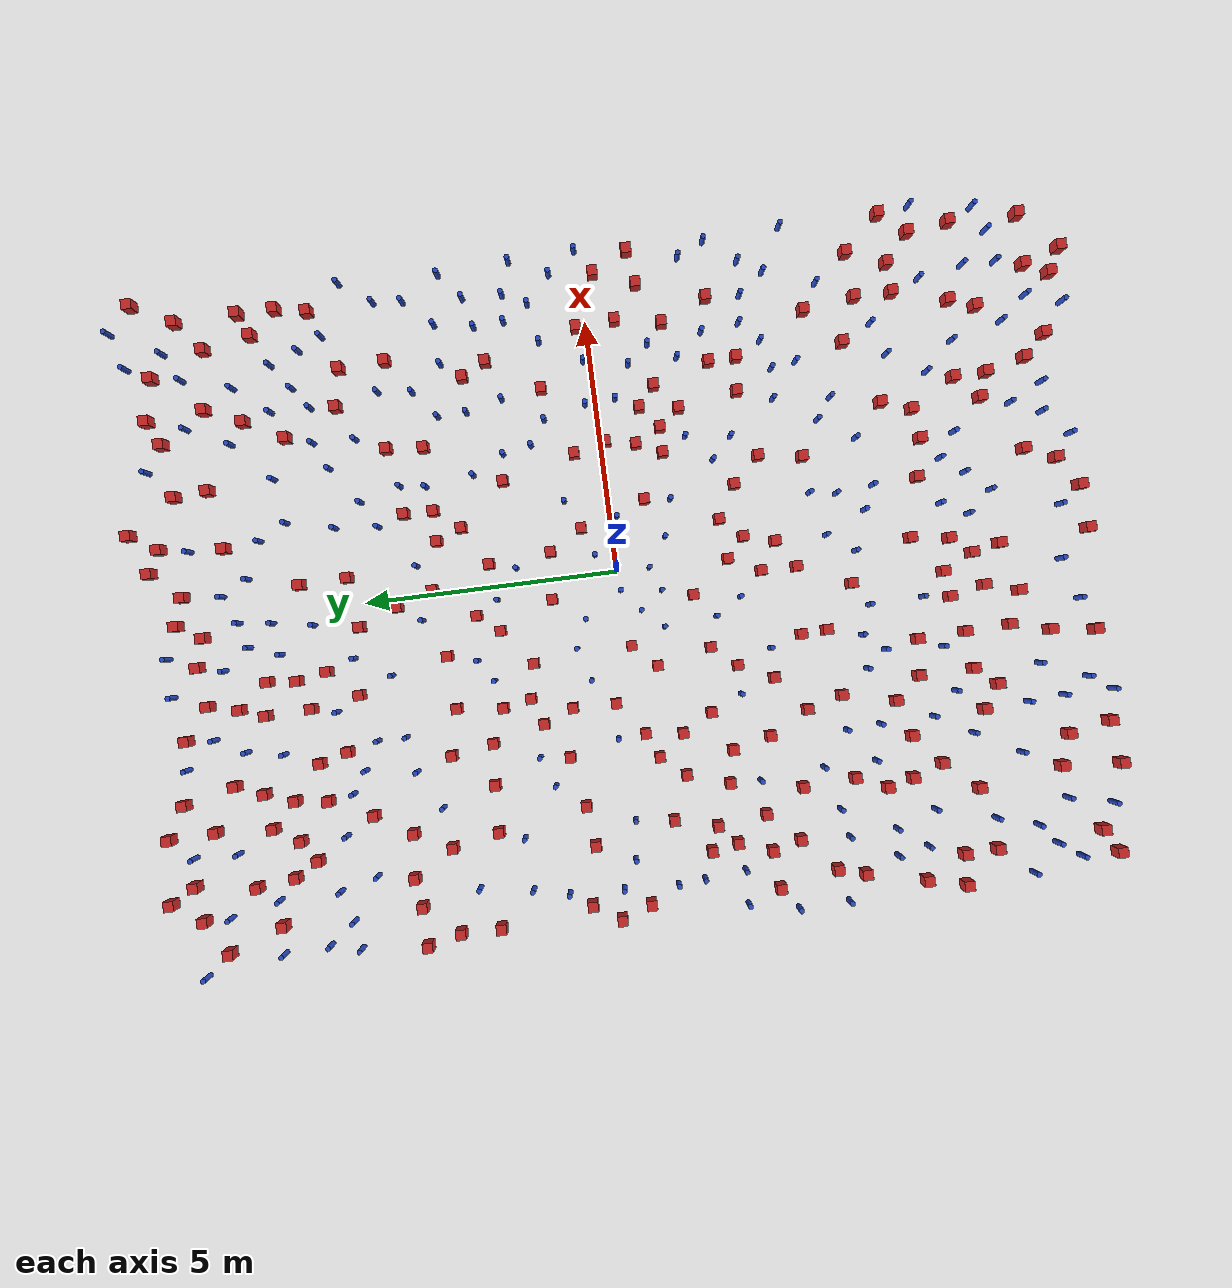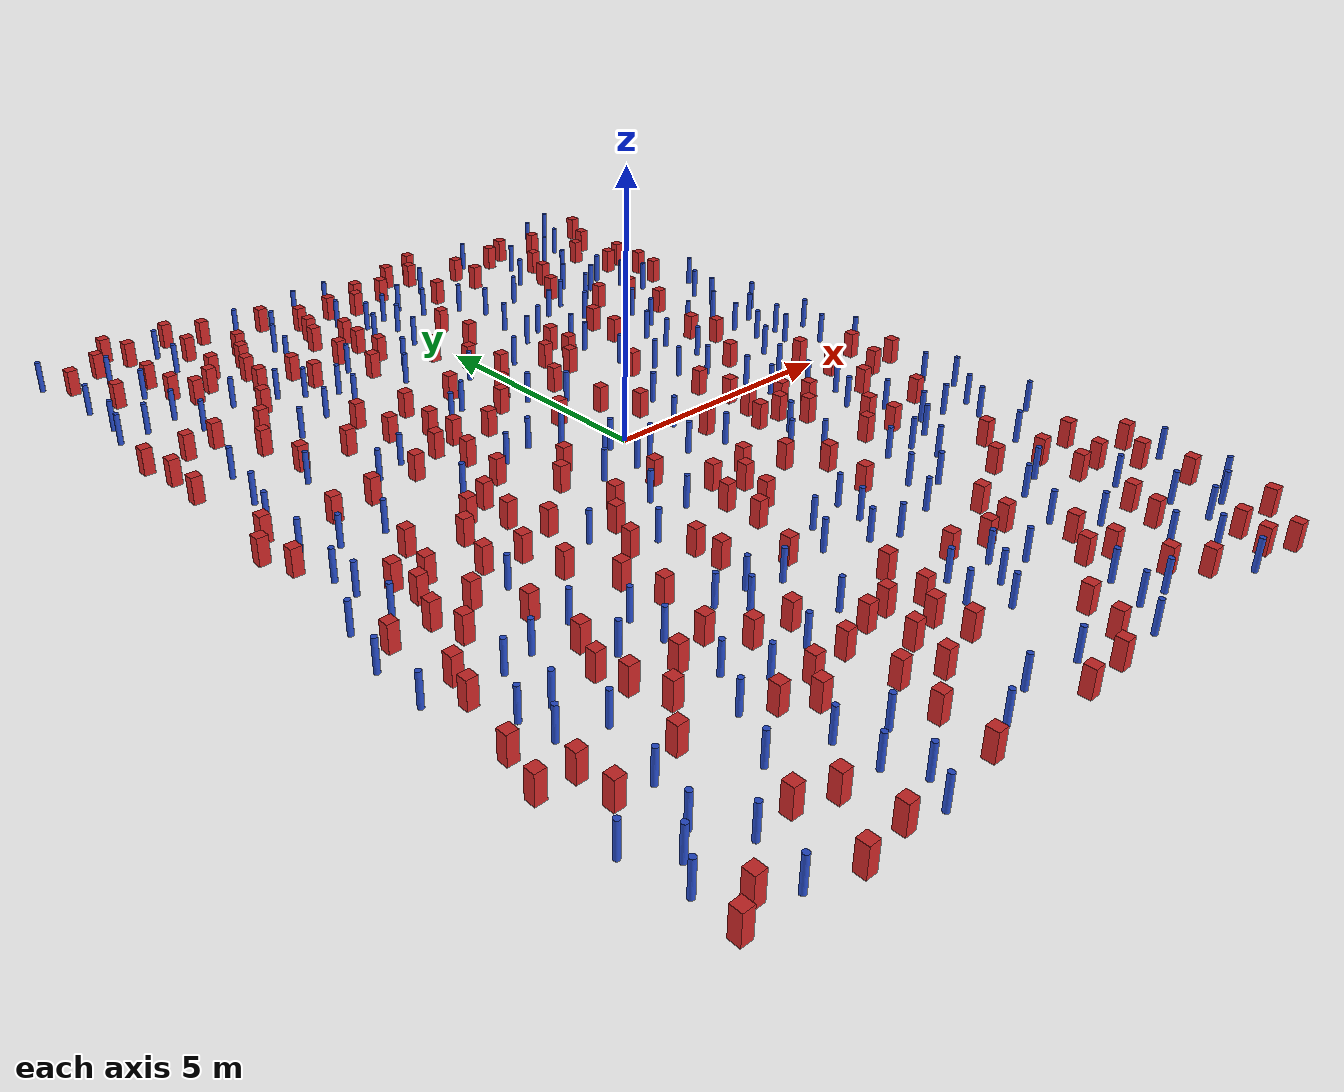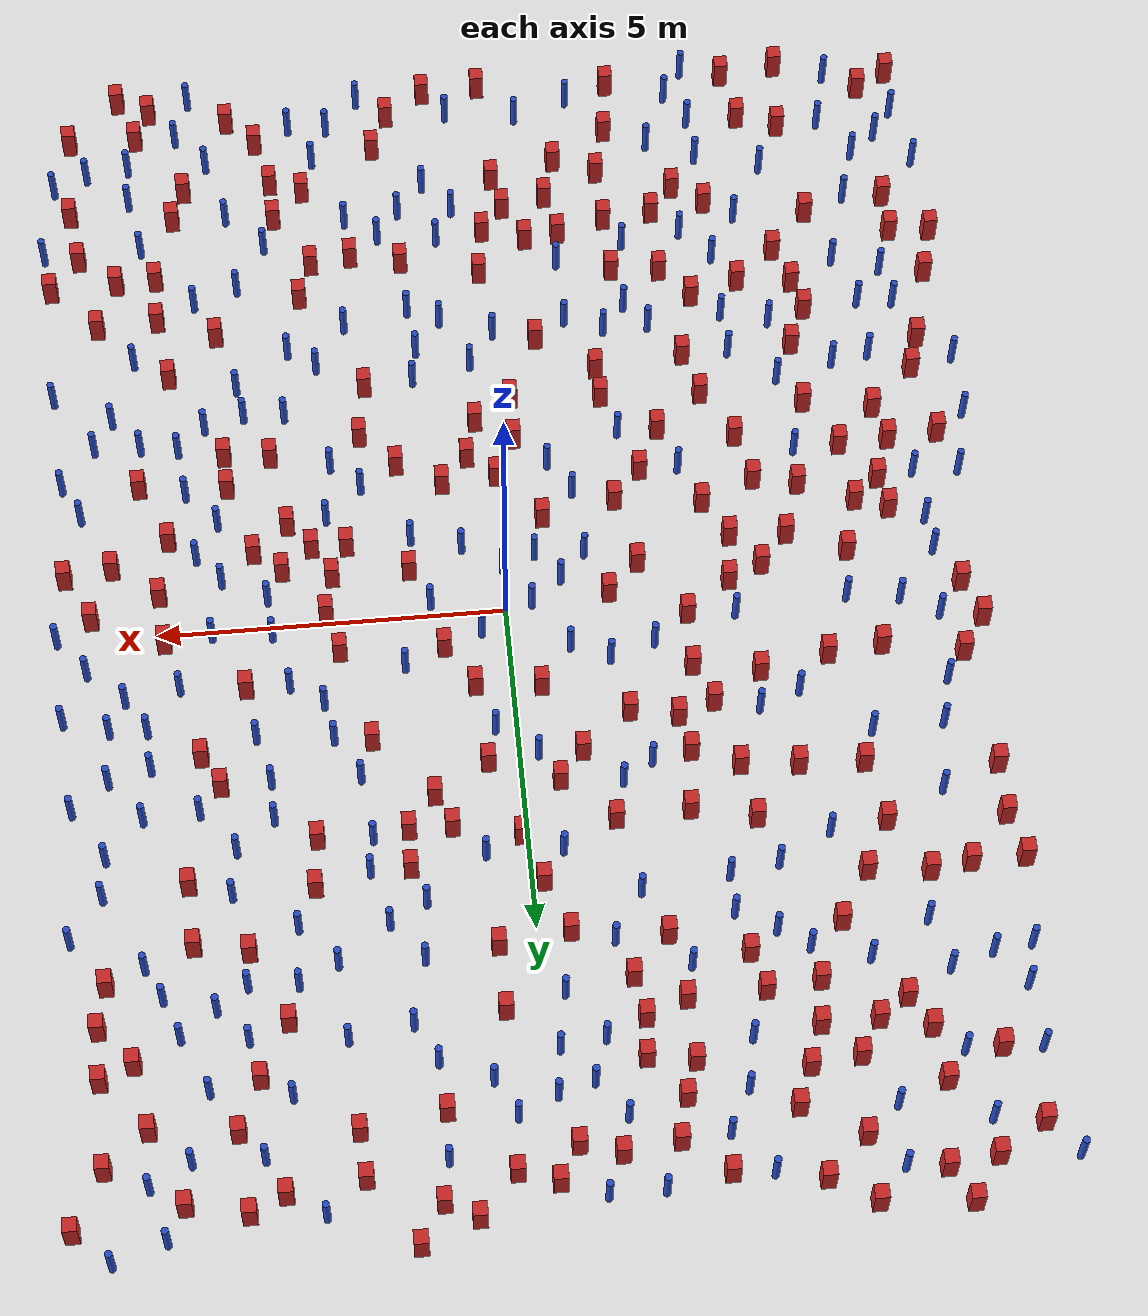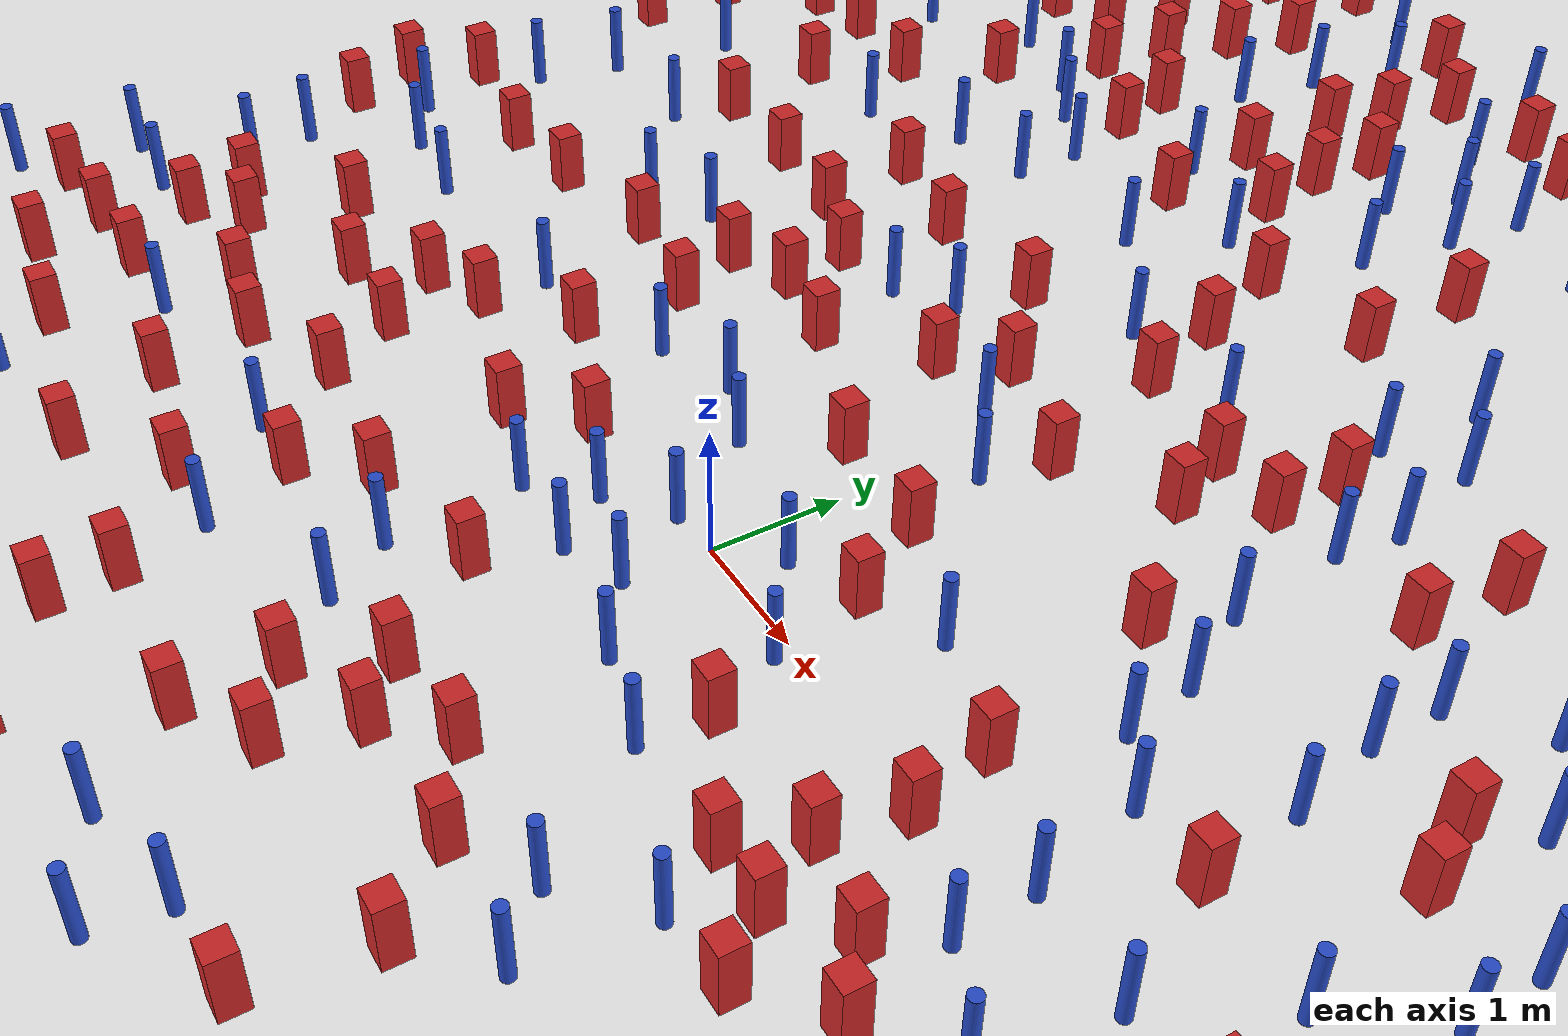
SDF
<sdf version="1.6">
  <model name="dense_14"><model name="square_post_obstacle0">
  <static>true</static>
  <pose frame="">-4.97025781886 3.84912494383 1.91545236811e-07 -7.35059704564e-06 1.12565212e-07 2.39332434364e-05</pose>
  <link name="link">
    <pose frame="">0 0 0.25 0 -0 0</pose>
    <inertial>
      <mass>100</mass>
      <inertia>
        <ixx>0.166667</ixx>
        <ixy>0</ixy>
        <ixz>0</ixz>
        <iyy>0.166667</iyy>
        <iyz>0</iyz>
        <izz>0.166667</izz>
      </inertia>
    </inertial>
    <collision name="collision">
      <geometry>
        <box>
          <size>.2 .2 .5</size>
        </box>
      </geometry>
      <max_contacts>10</max_contacts>
      <surface>
        <contact>
          <ode/>
        </contact>
        <bounce/>
        <friction>
          <torsional>
            <ode/>
          </torsional>
          <ode/>
        </friction>
      </surface>
    </collision>
    <visual name="visual">
      <geometry>
        <box>
          <size>.2 .2 .5</size>
        </box>
      </geometry>
      <material>
        <script>
          <name>Gazebo/Red</name>
          <uri>file://media/materials/scripts/gazebo.material</uri>
        </script>
      </material>
    </visual>
    <self_collide>0</self_collide>
    <kinematic>0</kinematic>
  </link>
</model>
<model name="square_post_obstacle1">
  <static>true</static>
  <pose frame="">-1.24322853132 3.50042942154 1.91545236811e-07 -7.35059704564e-06 1.12565212e-07 2.39332434364e-05</pose>
  <link name="link">
    <pose frame="">0 0 0.25 0 -0 0</pose>
    <inertial>
      <mass>100</mass>
      <inertia>
        <ixx>0.166667</ixx>
        <ixy>0</ixy>
        <ixz>0</ixz>
        <iyy>0.166667</iyy>
        <iyz>0</iyz>
        <izz>0.166667</izz>
      </inertia>
    </inertial>
    <collision name="collision">
      <geometry>
        <box>
          <size>.2 .2 .5</size>
        </box>
      </geometry>
      <max_contacts>10</max_contacts>
      <surface>
        <contact>
          <ode/>
        </contact>
        <bounce/>
        <friction>
          <torsional>
            <ode/>
          </torsional>
          <ode/>
        </friction>
      </surface>
    </collision>
    <visual name="visual">
      <geometry>
        <box>
          <size>.2 .2 .5</size>
        </box>
      </geometry>
      <material>
        <script>
          <name>Gazebo/Red</name>
          <uri>file://media/materials/scripts/gazebo.material</uri>
        </script>
      </material>
    </visual>
    <self_collide>0</self_collide>
    <kinematic>0</kinematic>
  </link>
</model>
<model name="pole_obstacle0">
  <static>true</static>
  <pose frame="">5.38879839555 8.36669542254 7.38925637345e-09 -8.471706928e-08 1.24976765081e-08 -1.74513093015e-07</pose>
  <link name="link">
  <pose frame="">0 0 0.3 0 -0 0</pose>
    <inertial>
      <mass>1</mass>
      <inertia>
        <ixx>0.145833</ixx>
        <ixy>0</ixy>
        <ixz>0</ixz>
        <iyy>0.145833</iyy>
        <iyz>0</iyz>
        <izz>0.125</izz>
      </inertia>
    </inertial>
    <collision name="collision">
      <geometry>
        <cylinder>
          <radius>0.05</radius>
          <length>.6</length>
        </cylinder>
      </geometry>
      <max_contacts>10</max_contacts>
      <surface>
        <contact>
          <ode/>
        </contact>
        <bounce/>
        <friction>
          <torsional>
            <ode/>
          </torsional>
          <ode/>
        </friction>
      </surface>
    </collision>
    <visual name="visual">
      <geometry>
        <cylinder>
          <radius>0.05</radius>
          <length>.6</length>
        </cylinder>
      </geometry>
      <material>
        <script>
          <name>Gazebo/Blue</name>
          <uri>file://media/materials/scripts/gazebo.material</uri>
        </script>
      </material>
    </visual>
    <self_collide>0</self_collide>
    <kinematic>0</kinematic>
  </link>
</model>
<model name="square_post_obstacle2">
  <static>true</static>
  <pose frame="">0.536799220432 5.27281515799 1.91545236811e-07 -7.35059704564e-06 1.12565212e-07 2.39332434364e-05</pose>
  <link name="link">
    <pose frame="">0 0 0.25 0 -0 0</pose>
    <inertial>
      <mass>100</mass>
      <inertia>
        <ixx>0.166667</ixx>
        <ixy>0</ixy>
        <ixz>0</ixz>
        <iyy>0.166667</iyy>
        <iyz>0</iyz>
        <izz>0.166667</izz>
      </inertia>
    </inertial>
    <collision name="collision">
      <geometry>
        <box>
          <size>.2 .2 .5</size>
        </box>
      </geometry>
      <max_contacts>10</max_contacts>
      <surface>
        <contact>
          <ode/>
        </contact>
        <bounce/>
        <friction>
          <torsional>
            <ode/>
          </torsional>
          <ode/>
        </friction>
      </surface>
    </collision>
    <visual name="visual">
      <geometry>
        <box>
          <size>.2 .2 .5</size>
        </box>
      </geometry>
      <material>
        <script>
          <name>Gazebo/Red</name>
          <uri>file://media/materials/scripts/gazebo.material</uri>
        </script>
      </material>
    </visual>
    <self_collide>0</self_collide>
    <kinematic>0</kinematic>
  </link>
</model>
<model name="pole_obstacle1">
  <static>true</static>
  <pose frame="">-1.84881068578 -4.64026522399 7.38925637345e-09 -8.47170692799e-08 1.24976765033e-08 -1.74513093018e-07</pose>
  <link name="link">
  <pose frame="">0 0 0.3 0 -0 0</pose>
    <inertial>
      <mass>1</mass>
      <inertia>
        <ixx>0.145833</ixx>
        <ixy>0</ixy>
        <ixz>0</ixz>
        <iyy>0.145833</iyy>
        <iyz>0</iyz>
        <izz>0.125</izz>
      </inertia>
    </inertial>
    <collision name="collision">
      <geometry>
        <cylinder>
          <radius>0.05</radius>
          <length>.6</length>
        </cylinder>
      </geometry>
      <max_contacts>10</max_contacts>
      <surface>
        <contact>
          <ode/>
        </contact>
        <bounce/>
        <friction>
          <torsional>
            <ode/>
          </torsional>
          <ode/>
        </friction>
      </surface>
    </collision>
    <visual name="visual">
      <geometry>
        <cylinder>
          <radius>0.05</radius>
          <length>.6</length>
        </cylinder>
      </geometry>
      <material>
        <script>
          <name>Gazebo/Blue</name>
          <uri>file://media/materials/scripts/gazebo.material</uri>
        </script>
      </material>
    </visual>
    <self_collide>0</self_collide>
    <kinematic>0</kinematic>
  </link>
</model>
<model name="square_post_obstacle3">
  <static>true</static>
  <pose frame="">-4.75040820775 -5.25794380199 1.91545236811e-07 -7.35059704564e-06 1.12565212e-07 2.39332434364e-05</pose>
  <link name="link">
    <pose frame="">0 0 0.25 0 -0 0</pose>
    <inertial>
      <mass>100</mass>
      <inertia>
        <ixx>0.166667</ixx>
        <ixy>0</ixy>
        <ixz>0</ixz>
        <iyy>0.166667</iyy>
        <iyz>0</iyz>
        <izz>0.166667</izz>
      </inertia>
    </inertial>
    <collision name="collision">
      <geometry>
        <box>
          <size>.2 .2 .5</size>
        </box>
      </geometry>
      <max_contacts>10</max_contacts>
      <surface>
        <contact>
          <ode/>
        </contact>
        <bounce/>
        <friction>
          <torsional>
            <ode/>
          </torsional>
          <ode/>
        </friction>
      </surface>
    </collision>
    <visual name="visual">
      <geometry>
        <box>
          <size>.2 .2 .5</size>
        </box>
      </geometry>
      <material>
        <script>
          <name>Gazebo/Red</name>
          <uri>file://media/materials/scripts/gazebo.material</uri>
        </script>
      </material>
    </visual>
    <self_collide>0</self_collide>
    <kinematic>0</kinematic>
  </link>
</model>
<model name="pole_obstacle2">
  <static>true</static>
  <pose frame="">-2.05235568331 5.7813444198 7.38925637345e-09 -8.47170692798e-08 1.24976765033e-08 -1.74513093019e-07</pose>
  <link name="link">
  <pose frame="">0 0 0.3 0 -0 0</pose>
    <inertial>
      <mass>1</mass>
      <inertia>
        <ixx>0.145833</ixx>
        <ixy>0</ixy>
        <ixz>0</ixz>
        <iyy>0.145833</iyy>
        <iyz>0</iyz>
        <izz>0.125</izz>
      </inertia>
    </inertial>
    <collision name="collision">
      <geometry>
        <cylinder>
          <radius>0.05</radius>
          <length>.6</length>
        </cylinder>
      </geometry>
      <max_contacts>10</max_contacts>
      <surface>
        <contact>
          <ode/>
        </contact>
        <bounce/>
        <friction>
          <torsional>
            <ode/>
          </torsional>
          <ode/>
        </friction>
      </surface>
    </collision>
    <visual name="visual">
      <geometry>
        <cylinder>
          <radius>0.05</radius>
          <length>.6</length>
        </cylinder>
      </geometry>
      <material>
        <script>
          <name>Gazebo/Blue</name>
          <uri>file://media/materials/scripts/gazebo.material</uri>
        </script>
      </material>
    </visual>
    <self_collide>0</self_collide>
    <kinematic>0</kinematic>
  </link>
</model>
<model name="pole_obstacle3">
  <static>true</static>
  <pose frame="">5.00161453407 -6.65563241505 7.38925637345e-09 -8.47170692796e-08 1.24976764786e-08 -1.74513093032e-07</pose>
  <link name="link">
  <pose frame="">0 0 0.3 0 -0 0</pose>
    <inertial>
      <mass>1</mass>
      <inertia>
        <ixx>0.145833</ixx>
        <ixy>0</ixy>
        <ixz>0</ixz>
        <iyy>0.145833</iyy>
        <iyz>0</iyz>
        <izz>0.125</izz>
      </inertia>
    </inertial>
    <collision name="collision">
      <geometry>
        <cylinder>
          <radius>0.05</radius>
          <length>.6</length>
        </cylinder>
      </geometry>
      <max_contacts>10</max_contacts>
      <surface>
        <contact>
          <ode/>
        </contact>
        <bounce/>
        <friction>
          <torsional>
            <ode/>
          </torsional>
          <ode/>
        </friction>
      </surface>
    </collision>
    <visual name="visual">
      <geometry>
        <cylinder>
          <radius>0.05</radius>
          <length>.6</length>
        </cylinder>
      </geometry>
      <material>
        <script>
          <name>Gazebo/Blue</name>
          <uri>file://media/materials/scripts/gazebo.material</uri>
        </script>
      </material>
    </visual>
    <self_collide>0</self_collide>
    <kinematic>0</kinematic>
  </link>
</model>
<model name="square_post_obstacle4">
  <static>true</static>
  <pose frame="">-3.86598333361 2.88226753271 1.91545236811e-07 -7.35059704564e-06 1.12565212e-07 2.39332434364e-05</pose>
  <link name="link">
    <pose frame="">0 0 0.25 0 -0 0</pose>
    <inertial>
      <mass>100</mass>
      <inertia>
        <ixx>0.166667</ixx>
        <ixy>0</ixy>
        <ixz>0</ixz>
        <iyy>0.166667</iyy>
        <iyz>0</iyz>
        <izz>0.166667</izz>
      </inertia>
    </inertial>
    <collision name="collision">
      <geometry>
        <box>
          <size>.2 .2 .5</size>
        </box>
      </geometry>
      <max_contacts>10</max_contacts>
      <surface>
        <contact>
          <ode/>
        </contact>
        <bounce/>
        <friction>
          <torsional>
            <ode/>
          </torsional>
          <ode/>
        </friction>
      </surface>
    </collision>
    <visual name="visual">
      <geometry>
        <box>
          <size>.2 .2 .5</size>
        </box>
      </geometry>
      <material>
        <script>
          <name>Gazebo/Red</name>
          <uri>file://media/materials/scripts/gazebo.material</uri>
        </script>
      </material>
    </visual>
    <self_collide>0</self_collide>
    <kinematic>0</kinematic>
  </link>
</model>
<model name="square_post_obstacle5">
  <static>true</static>
  <pose frame="">-4.66249946819 -3.09574171954 1.91545236811e-07 -7.35059704564e-06 1.12565212e-07 2.39332434364e-05</pose>
  <link name="link">
    <pose frame="">0 0 0.25 0 -0 0</pose>
    <inertial>
      <mass>100</mass>
      <inertia>
        <ixx>0.166667</ixx>
        <ixy>0</ixy>
        <ixz>0</ixz>
        <iyy>0.166667</iyy>
        <iyz>0</iyz>
        <izz>0.166667</izz>
      </inertia>
    </inertial>
    <collision name="collision">
      <geometry>
        <box>
          <size>.2 .2 .5</size>
        </box>
      </geometry>
      <max_contacts>10</max_contacts>
      <surface>
        <contact>
          <ode/>
        </contact>
        <bounce/>
        <friction>
          <torsional>
            <ode/>
          </torsional>
          <ode/>
        </friction>
      </surface>
    </collision>
    <visual name="visual">
      <geometry>
        <box>
          <size>.2 .2 .5</size>
        </box>
      </geometry>
      <material>
        <script>
          <name>Gazebo/Red</name>
          <uri>file://media/materials/scripts/gazebo.material</uri>
        </script>
      </material>
    </visual>
    <self_collide>0</self_collide>
    <kinematic>0</kinematic>
  </link>
</model>
<model name="square_post_obstacle6">
  <static>true</static>
  <pose frame="">6.05078648115 -7.38090235444 1.91545236811e-07 -7.35059704564e-06 1.12565212e-07 2.39332434364e-05</pose>
  <link name="link">
    <pose frame="">0 0 0.25 0 -0 0</pose>
    <inertial>
      <mass>100</mass>
      <inertia>
        <ixx>0.166667</ixx>
        <ixy>0</ixy>
        <ixz>0</ixz>
        <iyy>0.166667</iyy>
        <iyz>0</iyz>
        <izz>0.166667</izz>
      </inertia>
    </inertial>
    <collision name="collision">
      <geometry>
        <box>
          <size>.2 .2 .5</size>
        </box>
      </geometry>
      <max_contacts>10</max_contacts>
      <surface>
        <contact>
          <ode/>
        </contact>
        <bounce/>
        <friction>
          <torsional>
            <ode/>
          </torsional>
          <ode/>
        </friction>
      </surface>
    </collision>
    <visual name="visual">
      <geometry>
        <box>
          <size>.2 .2 .5</size>
        </box>
      </geometry>
      <material>
        <script>
          <name>Gazebo/Red</name>
          <uri>file://media/materials/scripts/gazebo.material</uri>
        </script>
      </material>
    </visual>
    <self_collide>0</self_collide>
    <kinematic>0</kinematic>
  </link>
</model>
<model name="pole_obstacle4">
  <static>true</static>
  <pose frame="">3.4753207857 3.11598202601 7.38925637345e-09 -8.47170692798e-08 1.24976764939e-08 -1.74513093025e-07</pose>
  <link name="link">
  <pose frame="">0 0 0.3 0 -0 0</pose>
    <inertial>
      <mass>1</mass>
      <inertia>
        <ixx>0.145833</ixx>
        <ixy>0</ixy>
        <ixz>0</ixz>
        <iyy>0.145833</iyy>
        <iyz>0</iyz>
        <izz>0.125</izz>
      </inertia>
    </inertial>
    <collision name="collision">
      <geometry>
        <cylinder>
          <radius>0.05</radius>
          <length>.6</length>
        </cylinder>
      </geometry>
      <max_contacts>10</max_contacts>
      <surface>
        <contact>
          <ode/>
        </contact>
        <bounce/>
        <friction>
          <torsional>
            <ode/>
          </torsional>
          <ode/>
        </friction>
      </surface>
    </collision>
    <visual name="visual">
      <geometry>
        <cylinder>
          <radius>0.05</radius>
          <length>.6</length>
        </cylinder>
      </geometry>
      <material>
        <script>
          <name>Gazebo/Blue</name>
          <uri>file://media/materials/scripts/gazebo.material</uri>
        </script>
      </material>
    </visual>
    <self_collide>0</self_collide>
    <kinematic>0</kinematic>
  </link>
</model>
<model name="pole_obstacle5">
  <static>true</static>
  <pose frame="">-5.41904791078 -5.61598771798 7.38925637345e-09 -8.47170692796e-08 1.24976764786e-08 -1.74513093032e-07</pose>
  <link name="link">
  <pose frame="">0 0 0.3 0 -0 0</pose>
    <inertial>
      <mass>1</mass>
      <inertia>
        <ixx>0.145833</ixx>
        <ixy>0</ixy>
        <ixz>0</ixz>
        <iyy>0.145833</iyy>
        <iyz>0</iyz>
        <izz>0.125</izz>
      </inertia>
    </inertial>
    <collision name="collision">
      <geometry>
        <cylinder>
          <radius>0.05</radius>
          <length>.6</length>
        </cylinder>
      </geometry>
      <max_contacts>10</max_contacts>
      <surface>
        <contact>
          <ode/>
        </contact>
        <bounce/>
        <friction>
          <torsional>
            <ode/>
          </torsional>
          <ode/>
        </friction>
      </surface>
    </collision>
    <visual name="visual">
      <geometry>
        <cylinder>
          <radius>0.05</radius>
          <length>.6</length>
        </cylinder>
      </geometry>
      <material>
        <script>
          <name>Gazebo/Blue</name>
          <uri>file://media/materials/scripts/gazebo.material</uri>
        </script>
      </material>
    </visual>
    <self_collide>0</self_collide>
    <kinematic>0</kinematic>
  </link>
</model>
<model name="square_post_obstacle7">
  <static>true</static>
  <pose frame="">4.19259915789 2.54085804016 1.91545236811e-07 -7.35059704564e-06 1.12565212e-07 2.39332434364e-05</pose>
  <link name="link">
    <pose frame="">0 0 0.25 0 -0 0</pose>
    <inertial>
      <mass>100</mass>
      <inertia>
        <ixx>0.166667</ixx>
        <ixy>0</ixy>
        <ixz>0</ixz>
        <iyy>0.166667</iyy>
        <iyz>0</iyz>
        <izz>0.166667</izz>
      </inertia>
    </inertial>
    <collision name="collision">
      <geometry>
        <box>
          <size>.2 .2 .5</size>
        </box>
      </geometry>
      <max_contacts>10</max_contacts>
      <surface>
        <contact>
          <ode/>
        </contact>
        <bounce/>
        <friction>
          <torsional>
            <ode/>
          </torsional>
          <ode/>
        </friction>
      </surface>
    </collision>
    <visual name="visual">
      <geometry>
        <box>
          <size>.2 .2 .5</size>
        </box>
      </geometry>
      <material>
        <script>
          <name>Gazebo/Red</name>
          <uri>file://media/materials/scripts/gazebo.material</uri>
        </script>
      </material>
    </visual>
    <self_collide>0</self_collide>
    <kinematic>0</kinematic>
  </link>
</model>
<model name="square_post_obstacle8">
  <static>true</static>
  <pose frame="">-3.3170645429 -0.900582751196 1.91545236811e-07 -7.35059704564e-06 1.12565212e-07 2.39332434364e-05</pose>
  <link name="link">
    <pose frame="">0 0 0.25 0 -0 0</pose>
    <inertial>
      <mass>100</mass>
      <inertia>
        <ixx>0.166667</ixx>
        <ixy>0</ixy>
        <ixz>0</ixz>
        <iyy>0.166667</iyy>
        <iyz>0</iyz>
        <izz>0.166667</izz>
      </inertia>
    </inertial>
    <collision name="collision">
      <geometry>
        <box>
          <size>.2 .2 .5</size>
        </box>
      </geometry>
      <max_contacts>10</max_contacts>
      <surface>
        <contact>
          <ode/>
        </contact>
        <bounce/>
        <friction>
          <torsional>
            <ode/>
          </torsional>
          <ode/>
        </friction>
      </surface>
    </collision>
    <visual name="visual">
      <geometry>
        <box>
          <size>.2 .2 .5</size>
        </box>
      </geometry>
      <material>
        <script>
          <name>Gazebo/Red</name>
          <uri>file://media/materials/scripts/gazebo.material</uri>
        </script>
      </material>
    </visual>
    <self_collide>0</self_collide>
    <kinematic>0</kinematic>
  </link>
</model>
<model name="pole_obstacle6">
  <static>true</static>
  <pose frame="">4.54309305607 7.07931227956 7.38925637345e-09 -8.47170692796e-08 1.24976764786e-08 -1.74513093032e-07</pose>
  <link name="link">
  <pose frame="">0 0 0.3 0 -0 0</pose>
    <inertial>
      <mass>1</mass>
      <inertia>
        <ixx>0.145833</ixx>
        <ixy>0</ixy>
        <ixz>0</ixz>
        <iyy>0.145833</iyy>
        <iyz>0</iyz>
        <izz>0.125</izz>
      </inertia>
    </inertial>
    <collision name="collision">
      <geometry>
        <cylinder>
          <radius>0.05</radius>
          <length>.6</length>
        </cylinder>
      </geometry>
      <max_contacts>10</max_contacts>
      <surface>
        <contact>
          <ode/>
        </contact>
        <bounce/>
        <friction>
          <torsional>
            <ode/>
          </torsional>
          <ode/>
        </friction>
      </surface>
    </collision>
    <visual name="visual">
      <geometry>
        <cylinder>
          <radius>0.05</radius>
          <length>.6</length>
        </cylinder>
      </geometry>
      <material>
        <script>
          <name>Gazebo/Blue</name>
          <uri>file://media/materials/scripts/gazebo.material</uri>
        </script>
      </material>
    </visual>
    <self_collide>0</self_collide>
    <kinematic>0</kinematic>
  </link>
</model>
<model name="pole_obstacle7">
  <static>true</static>
  <pose frame="">-3.5572372845 -7.70122249438 7.38925637345e-09 -8.47170692798e-08 1.24976765033e-08 -1.74513093019e-07</pose>
  <link name="link">
  <pose frame="">0 0 0.3 0 -0 0</pose>
    <inertial>
      <mass>1</mass>
      <inertia>
        <ixx>0.145833</ixx>
        <ixy>0</ixy>
        <ixz>0</ixz>
        <iyy>0.145833</iyy>
        <iyz>0</iyz>
        <izz>0.125</izz>
      </inertia>
    </inertial>
    <collision name="collision">
      <geometry>
        <cylinder>
          <radius>0.05</radius>
          <length>.6</length>
        </cylinder>
      </geometry>
      <max_contacts>10</max_contacts>
      <surface>
        <contact>
          <ode/>
        </contact>
        <bounce/>
        <friction>
          <torsional>
            <ode/>
          </torsional>
          <ode/>
        </friction>
      </surface>
    </collision>
    <visual name="visual">
      <geometry>
        <cylinder>
          <radius>0.05</radius>
          <length>.6</length>
        </cylinder>
      </geometry>
      <material>
        <script>
          <name>Gazebo/Blue</name>
          <uri>file://media/materials/scripts/gazebo.material</uri>
        </script>
      </material>
    </visual>
    <self_collide>0</self_collide>
    <kinematic>0</kinematic>
  </link>
</model>
<model name="square_post_obstacle9">
  <static>true</static>
  <pose frame="">-2.85442989702 5.66659609784 1.91545236811e-07 -7.35059704564e-06 1.12565212e-07 2.39332434364e-05</pose>
  <link name="link">
    <pose frame="">0 0 0.25 0 -0 0</pose>
    <inertial>
      <mass>100</mass>
      <inertia>
        <ixx>0.166667</ixx>
        <ixy>0</ixy>
        <ixz>0</ixz>
        <iyy>0.166667</iyy>
        <iyz>0</iyz>
        <izz>0.166667</izz>
      </inertia>
    </inertial>
    <collision name="collision">
      <geometry>
        <box>
          <size>.2 .2 .5</size>
        </box>
      </geometry>
      <max_contacts>10</max_contacts>
      <surface>
        <contact>
          <ode/>
        </contact>
        <bounce/>
        <friction>
          <torsional>
            <ode/>
          </torsional>
          <ode/>
        </friction>
      </surface>
    </collision>
    <visual name="visual">
      <geometry>
        <box>
          <size>.2 .2 .5</size>
        </box>
      </geometry>
      <material>
        <script>
          <name>Gazebo/Red</name>
          <uri>file://media/materials/scripts/gazebo.material</uri>
        </script>
      </material>
    </visual>
    <self_collide>0</self_collide>
    <kinematic>0</kinematic>
  </link>
</model>
<model name="square_post_obstacle10">
  <static>true</static>
  <pose frame="">2.50912233527 -7.55386749131 1.91545236811e-07 -7.35059704564e-06 1.12565212e-07 2.39332434364e-05</pose>
  <link name="link">
    <pose frame="">0 0 0.25 0 -0 0</pose>
    <inertial>
      <mass>100</mass>
      <inertia>
        <ixx>0.166667</ixx>
        <ixy>0</ixy>
        <ixz>0</ixz>
        <iyy>0.166667</iyy>
        <iyz>0</iyz>
        <izz>0.166667</izz>
      </inertia>
    </inertial>
    <collision name="collision">
      <geometry>
        <box>
          <size>.2 .2 .5</size>
        </box>
      </geometry>
      <max_contacts>10</max_contacts>
      <surface>
        <contact>
          <ode/>
        </contact>
        <bounce/>
        <friction>
          <torsional>
            <ode/>
          </torsional>
          <ode/>
        </friction>
      </surface>
    </collision>
    <visual name="visual">
      <geometry>
        <box>
          <size>.2 .2 .5</size>
        </box>
      </geometry>
      <material>
        <script>
          <name>Gazebo/Red</name>
          <uri>file://media/materials/scripts/gazebo.material</uri>
        </script>
      </material>
    </visual>
    <self_collide>0</self_collide>
    <kinematic>0</kinematic>
  </link>
</model>
<model name="square_post_obstacle11">
  <static>true</static>
  <pose frame="">2.98952658779 -7.73330978692 1.91545236811e-07 -7.35059704564e-06 1.12565212e-07 2.39332434364e-05</pose>
  <link name="link">
    <pose frame="">0 0 0.25 0 -0 0</pose>
    <inertial>
      <mass>100</mass>
      <inertia>
        <ixx>0.166667</ixx>
        <ixy>0</ixy>
        <ixz>0</ixz>
        <iyy>0.166667</iyy>
        <iyz>0</iyz>
        <izz>0.166667</izz>
      </inertia>
    </inertial>
    <collision name="collision">
      <geometry>
        <box>
          <size>.2 .2 .5</size>
        </box>
      </geometry>
      <max_contacts>10</max_contacts>
      <surface>
        <contact>
          <ode/>
        </contact>
        <bounce/>
        <friction>
          <torsional>
            <ode/>
          </torsional>
          <ode/>
        </friction>
      </surface>
    </collision>
    <visual name="visual">
      <geometry>
        <box>
          <size>.2 .2 .5</size>
        </box>
      </geometry>
      <material>
        <script>
          <name>Gazebo/Red</name>
          <uri>file://media/materials/scripts/gazebo.material</uri>
        </script>
      </material>
    </visual>
    <self_collide>0</self_collide>
    <kinematic>0</kinematic>
  </link>
</model>
<model name="square_post_obstacle12">
  <static>true</static>
  <pose frame="">3.16215896326 -0.851828893414 1.91545236811e-07 -7.35059704564e-06 1.12565212e-07 2.39332434364e-05</pose>
  <link name="link">
    <pose frame="">0 0 0.25 0 -0 0</pose>
    <inertial>
      <mass>100</mass>
      <inertia>
        <ixx>0.166667</ixx>
        <ixy>0</ixy>
        <ixz>0</ixz>
        <iyy>0.166667</iyy>
        <iyz>0</iyz>
        <izz>0.166667</izz>
      </inertia>
    </inertial>
    <collision name="collision">
      <geometry>
        <box>
          <size>.2 .2 .5</size>
        </box>
      </geometry>
      <max_contacts>10</max_contacts>
      <surface>
        <contact>
          <ode/>
        </contact>
        <bounce/>
        <friction>
          <torsional>
            <ode/>
          </torsional>
          <ode/>
        </friction>
      </surface>
    </collision>
    <visual name="visual">
      <geometry>
        <box>
          <size>.2 .2 .5</size>
        </box>
      </geometry>
      <material>
        <script>
          <name>Gazebo/Red</name>
          <uri>file://media/materials/scripts/gazebo.material</uri>
        </script>
      </material>
    </visual>
    <self_collide>0</self_collide>
    <kinematic>0</kinematic>
  </link>
</model>
<model name="square_post_obstacle13">
  <static>true</static>
  <pose frame="">2.21254775683 -1.19619095075 1.91545236811e-07 -7.35059704564e-06 1.12565212e-07 2.39332434364e-05</pose>
  <link name="link">
    <pose frame="">0 0 0.25 0 -0 0</pose>
    <inertial>
      <mass>100</mass>
      <inertia>
        <ixx>0.166667</ixx>
        <ixy>0</ixy>
        <ixz>0</ixz>
        <iyy>0.166667</iyy>
        <iyz>0</iyz>
        <izz>0.166667</izz>
      </inertia>
    </inertial>
    <collision name="collision">
      <geometry>
        <box>
          <size>.2 .2 .5</size>
        </box>
      </geometry>
      <max_contacts>10</max_contacts>
      <surface>
        <contact>
          <ode/>
        </contact>
        <bounce/>
        <friction>
          <torsional>
            <ode/>
          </torsional>
          <ode/>
        </friction>
      </surface>
    </collision>
    <visual name="visual">
      <geometry>
        <box>
          <size>.2 .2 .5</size>
        </box>
      </geometry>
      <material>
        <script>
          <name>Gazebo/Red</name>
          <uri>file://media/materials/scripts/gazebo.material</uri>
        </script>
      </material>
    </visual>
    <self_collide>0</self_collide>
    <kinematic>0</kinematic>
  </link>
</model>
<model name="pole_obstacle8">
  <static>true</static>
  <pose frame="">-1.66729357442 -8.96804927392 7.38925637345e-09 -8.47170692798e-08 1.24976764881e-08 -1.74513093027e-07</pose>
  <link name="link">
  <pose frame="">0 0 0.3 0 -0 0</pose>
    <inertial>
      <mass>1</mass>
      <inertia>
        <ixx>0.145833</ixx>
        <ixy>0</ixy>
        <ixz>0</ixz>
        <iyy>0.145833</iyy>
        <iyz>0</iyz>
        <izz>0.125</izz>
      </inertia>
    </inertial>
    <collision name="collision">
      <geometry>
        <cylinder>
          <radius>0.05</radius>
          <length>.6</length>
        </cylinder>
      </geometry>
      <max_contacts>10</max_contacts>
      <surface>
        <contact>
          <ode/>
        </contact>
        <bounce/>
        <friction>
          <torsional>
            <ode/>
          </torsional>
          <ode/>
        </friction>
      </surface>
    </collision>
    <visual name="visual">
      <geometry>
        <cylinder>
          <radius>0.05</radius>
          <length>.6</length>
        </cylinder>
      </geometry>
      <material>
        <script>
          <name>Gazebo/Blue</name>
          <uri>file://media/materials/scripts/gazebo.material</uri>
        </script>
      </material>
    </visual>
    <self_collide>0</self_collide>
    <kinematic>0</kinematic>
  </link>
</model>
<model name="square_post_obstacle14">
  <static>true</static>
  <pose frame="">4.31348551052 -7.69776963985 1.91545236811e-07 -7.35059704564e-06 1.12565212e-07 2.39332434364e-05</pose>
  <link name="link">
    <pose frame="">0 0 0.25 0 -0 0</pose>
    <inertial>
      <mass>100</mass>
      <inertia>
        <ixx>0.166667</ixx>
        <ixy>0</ixy>
        <ixz>0</ixz>
        <iyy>0.166667</iyy>
        <iyz>0</iyz>
        <izz>0.166667</izz>
      </inertia>
    </inertial>
    <collision name="collision">
      <geometry>
        <box>
          <size>.2 .2 .5</size>
        </box>
      </geometry>
      <max_contacts>10</max_contacts>
      <surface>
        <contact>
          <ode/>
        </contact>
        <bounce/>
        <friction>
          <torsional>
            <ode/>
          </torsional>
          <ode/>
        </friction>
      </surface>
    </collision>
    <visual name="visual">
      <geometry>
        <box>
          <size>.2 .2 .5</size>
        </box>
      </geometry>
      <material>
        <script>
          <name>Gazebo/Red</name>
          <uri>file://media/materials/scripts/gazebo.material</uri>
        </script>
      </material>
    </visual>
    <self_collide>0</self_collide>
    <kinematic>0</kinematic>
  </link>
</model>
<model name="square_post_obstacle15">
  <static>true</static>
  <pose frame="">-6.63698604734 3.89297951094 1.91545236811e-07 -7.35059704564e-06 1.12565212e-07 2.39332434364e-05</pose>
  <link name="link">
    <pose frame="">0 0 0.25 0 -0 0</pose>
    <inertial>
      <mass>100</mass>
      <inertia>
        <ixx>0.166667</ixx>
        <ixy>0</ixy>
        <ixz>0</ixz>
        <iyy>0.166667</iyy>
        <iyz>0</iyz>
        <izz>0.166667</izz>
      </inertia>
    </inertial>
    <collision name="collision">
      <geometry>
        <box>
          <size>.2 .2 .5</size>
        </box>
      </geometry>
      <max_contacts>10</max_contacts>
      <surface>
        <contact>
          <ode/>
        </contact>
        <bounce/>
        <friction>
          <torsional>
            <ode/>
          </torsional>
          <ode/>
        </friction>
      </surface>
    </collision>
    <visual name="visual">
      <geometry>
        <box>
          <size>.2 .2 .5</size>
        </box>
      </geometry>
      <material>
        <script>
          <name>Gazebo/Red</name>
          <uri>file://media/materials/scripts/gazebo.material</uri>
        </script>
      </material>
    </visual>
    <self_collide>0</self_collide>
    <kinematic>0</kinematic>
  </link>
</model>
<model name="square_post_obstacle16">
  <static>true</static>
  <pose frame="">-0.397680209868 1.31862929755 1.91545236811e-07 -7.35059704564e-06 1.12565212e-07 2.39332434364e-05</pose>
  <link name="link">
    <pose frame="">0 0 0.25 0 -0 0</pose>
    <inertial>
      <mass>100</mass>
      <inertia>
        <ixx>0.166667</ixx>
        <ixy>0</ixy>
        <ixz>0</ixz>
        <iyy>0.166667</iyy>
        <iyz>0</iyz>
        <izz>0.166667</izz>
      </inertia>
    </inertial>
    <collision name="collision">
      <geometry>
        <box>
          <size>.2 .2 .5</size>
        </box>
      </geometry>
      <max_contacts>10</max_contacts>
      <surface>
        <contact>
          <ode/>
        </contact>
        <bounce/>
        <friction>
          <torsional>
            <ode/>
          </torsional>
          <ode/>
        </friction>
      </surface>
    </collision>
    <visual name="visual">
      <geometry>
        <box>
          <size>.2 .2 .5</size>
        </box>
      </geometry>
      <material>
        <script>
          <name>Gazebo/Red</name>
          <uri>file://media/materials/scripts/gazebo.material</uri>
        </script>
      </material>
    </visual>
    <self_collide>0</self_collide>
    <kinematic>0</kinematic>
  </link>
</model>
<model name="pole_obstacle9">
  <static>true</static>
  <pose frame="">2.12831113329 3.52207049719 7.38925637345e-09 -8.47170692798e-08 1.24976764939e-08 -1.74513093025e-07</pose>
  <link name="link">
  <pose frame="">0 0 0.3 0 -0 0</pose>
    <inertial>
      <mass>1</mass>
      <inertia>
        <ixx>0.145833</ixx>
        <ixy>0</ixy>
        <ixz>0</ixz>
        <iyy>0.145833</iyy>
        <iyz>0</iyz>
        <izz>0.125</izz>
      </inertia>
    </inertial>
    <collision name="collision">
      <geometry>
        <cylinder>
          <radius>0.05</radius>
          <length>.6</length>
        </cylinder>
      </geometry>
      <max_contacts>10</max_contacts>
      <surface>
        <contact>
          <ode/>
        </contact>
        <bounce/>
        <friction>
          <torsional>
            <ode/>
          </torsional>
          <ode/>
        </friction>
      </surface>
    </collision>
    <visual name="visual">
      <geometry>
        <cylinder>
          <radius>0.05</radius>
          <length>.6</length>
        </cylinder>
      </geometry>
      <material>
        <script>
          <name>Gazebo/Blue</name>
          <uri>file://media/materials/scripts/gazebo.material</uri>
        </script>
      </material>
    </visual>
    <self_collide>0</self_collide>
    <kinematic>0</kinematic>
  </link>
</model>
<model name="square_post_obstacle17">
  <static>true</static>
  <pose frame="">4.93993323977 -0.584105912174 1.91545236811e-07 -7.35059704564e-06 1.12565212e-07 2.39332434364e-05</pose>
  <link name="link">
    <pose frame="">0 0 0.25 0 -0 0</pose>
    <inertial>
      <mass>100</mass>
      <inertia>
        <ixx>0.166667</ixx>
        <ixy>0</ixy>
        <ixz>0</ixz>
        <iyy>0.166667</iyy>
        <iyz>0</iyz>
        <izz>0.166667</izz>
      </inertia>
    </inertial>
    <collision name="collision">
      <geometry>
        <box>
          <size>.2 .2 .5</size>
        </box>
      </geometry>
      <max_contacts>10</max_contacts>
      <surface>
        <contact>
          <ode/>
        </contact>
        <bounce/>
        <friction>
          <torsional>
            <ode/>
          </torsional>
          <ode/>
        </friction>
      </surface>
    </collision>
    <visual name="visual">
      <geometry>
        <box>
          <size>.2 .2 .5</size>
        </box>
      </geometry>
      <material>
        <script>
          <name>Gazebo/Red</name>
          <uri>file://media/materials/scripts/gazebo.material</uri>
        </script>
      </material>
    </visual>
    <self_collide>0</self_collide>
    <kinematic>0</kinematic>
  </link>
</model>
<model name="square_post_obstacle18">
  <static>true</static>
  <pose frame="">-2.13460060143 -2.13000570045 1.91545236811e-07 -7.35059704564e-06 1.12565212e-07 2.39332434364e-05</pose>
  <link name="link">
    <pose frame="">0 0 0.25 0 -0 0</pose>
    <inertial>
      <mass>100</mass>
      <inertia>
        <ixx>0.166667</ixx>
        <ixy>0</ixy>
        <ixz>0</ixz>
        <iyy>0.166667</iyy>
        <iyz>0</iyz>
        <izz>0.166667</izz>
      </inertia>
    </inertial>
    <collision name="collision">
      <geometry>
        <box>
          <size>.2 .2 .5</size>
        </box>
      </geometry>
      <max_contacts>10</max_contacts>
      <surface>
        <contact>
          <ode/>
        </contact>
        <bounce/>
        <friction>
          <torsional>
            <ode/>
          </torsional>
          <ode/>
        </friction>
      </surface>
    </collision>
    <visual name="visual">
      <geometry>
        <box>
          <size>.2 .2 .5</size>
        </box>
      </geometry>
      <material>
        <script>
          <name>Gazebo/Red</name>
          <uri>file://media/materials/scripts/gazebo.material</uri>
        </script>
      </material>
    </visual>
    <self_collide>0</self_collide>
    <kinematic>0</kinematic>
  </link>
</model>
<model name="pole_obstacle10">
  <static>true</static>
  <pose frame="">2.01584505865 -5.01099669691 7.38925637345e-09 -8.47170692799e-08 1.24976765014e-08 -1.7451309302e-07</pose>
  <link name="link">
  <pose frame="">0 0 0.3 0 -0 0</pose>
    <inertial>
      <mass>1</mass>
      <inertia>
        <ixx>0.145833</ixx>
        <ixy>0</ixy>
        <ixz>0</ixz>
        <iyy>0.145833</iyy>
        <iyz>0</iyz>
        <izz>0.125</izz>
      </inertia>
    </inertial>
    <collision name="collision">
      <geometry>
        <cylinder>
          <radius>0.05</radius>
          <length>.6</length>
        </cylinder>
      </geometry>
      <max_contacts>10</max_contacts>
      <surface>
        <contact>
          <ode/>
        </contact>
        <bounce/>
        <friction>
          <torsional>
            <ode/>
          </torsional>
          <ode/>
        </friction>
      </surface>
    </collision>
    <visual name="visual">
      <geometry>
        <cylinder>
          <radius>0.05</radius>
          <length>.6</length>
        </cylinder>
      </geometry>
      <material>
        <script>
          <name>Gazebo/Blue</name>
          <uri>file://media/materials/scripts/gazebo.material</uri>
        </script>
      </material>
    </visual>
    <self_collide>0</self_collide>
    <kinematic>0</kinematic>
  </link>
</model>
<model name="square_post_obstacle19">
  <static>true</static>
  <pose frame="">-6.33920245669 -3.56347168327 1.91545236811e-07 -7.35059704564e-06 1.12565212e-07 2.39332434364e-05</pose>
  <link name="link">
    <pose frame="">0 0 0.25 0 -0 0</pose>
    <inertial>
      <mass>100</mass>
      <inertia>
        <ixx>0.166667</ixx>
        <ixy>0</ixy>
        <ixz>0</ixz>
        <iyy>0.166667</iyy>
        <iyz>0</iyz>
        <izz>0.166667</izz>
      </inertia>
    </inertial>
    <collision name="collision">
      <geometry>
        <box>
          <size>.2 .2 .5</size>
        </box>
      </geometry>
      <max_contacts>10</max_contacts>
      <surface>
        <contact>
          <ode/>
        </contact>
        <bounce/>
        <friction>
          <torsional>
            <ode/>
          </torsional>
          <ode/>
        </friction>
      </surface>
    </collision>
    <visual name="visual">
      <geometry>
        <box>
          <size>.2 .2 .5</size>
        </box>
      </geometry>
      <material>
        <script>
          <name>Gazebo/Red</name>
          <uri>file://media/materials/scripts/gazebo.material</uri>
        </script>
      </material>
    </visual>
    <self_collide>0</self_collide>
    <kinematic>0</kinematic>
  </link>
</model>
<model name="pole_obstacle11">
  <static>true</static>
  <pose frame="">-5.73747270481 -6.77735786824 7.38925637345e-09 -8.47170692796e-08 1.24976764786e-08 -1.74513093032e-07</pose>
  <link name="link">
  <pose frame="">0 0 0.3 0 -0 0</pose>
    <inertial>
      <mass>1</mass>
      <inertia>
        <ixx>0.145833</ixx>
        <ixy>0</ixy>
        <ixz>0</ixz>
        <iyy>0.145833</iyy>
        <iyz>0</iyz>
        <izz>0.125</izz>
      </inertia>
    </inertial>
    <collision name="collision">
      <geometry>
        <cylinder>
          <radius>0.05</radius>
          <length>.6</length>
        </cylinder>
      </geometry>
      <max_contacts>10</max_contacts>
      <surface>
        <contact>
          <ode/>
        </contact>
        <bounce/>
        <friction>
          <torsional>
            <ode/>
          </torsional>
          <ode/>
        </friction>
      </surface>
    </collision>
    <visual name="visual">
      <geometry>
        <cylinder>
          <radius>0.05</radius>
          <length>.6</length>
        </cylinder>
      </geometry>
      <material>
        <script>
          <name>Gazebo/Blue</name>
          <uri>file://media/materials/scripts/gazebo.material</uri>
        </script>
      </material>
    </visual>
    <self_collide>0</self_collide>
    <kinematic>0</kinematic>
  </link>
</model>
<model name="square_post_obstacle20">
  <static>true</static>
  <pose frame="">-1.63090544055 8.28647198296 1.91545236811e-07 -7.35059704564e-06 1.12565212e-07 2.39332434364e-05</pose>
  <link name="link">
    <pose frame="">0 0 0.25 0 -0 0</pose>
    <inertial>
      <mass>100</mass>
      <inertia>
        <ixx>0.166667</ixx>
        <ixy>0</ixy>
        <ixz>0</ixz>
        <iyy>0.166667</iyy>
        <iyz>0</iyz>
        <izz>0.166667</izz>
      </inertia>
    </inertial>
    <collision name="collision">
      <geometry>
        <box>
          <size>.2 .2 .5</size>
        </box>
      </geometry>
      <max_contacts>10</max_contacts>
      <surface>
        <contact>
          <ode/>
        </contact>
        <bounce/>
        <friction>
          <torsional>
            <ode/>
          </torsional>
          <ode/>
        </friction>
      </surface>
    </collision>
    <visual name="visual">
      <geometry>
        <box>
          <size>.2 .2 .5</size>
        </box>
      </geometry>
      <material>
        <script>
          <name>Gazebo/Red</name>
          <uri>file://media/materials/scripts/gazebo.material</uri>
        </script>
      </material>
    </visual>
    <self_collide>0</self_collide>
    <kinematic>0</kinematic>
  </link>
</model>
<model name="pole_obstacle12">
  <static>true</static>
  <pose frame="">6.36594659354 1.35749647897 7.38925637345e-09 -8.471706928e-08 1.24976765134e-08 -1.74513093015e-07</pose>
  <link name="link">
  <pose frame="">0 0 0.3 0 -0 0</pose>
    <inertial>
      <mass>1</mass>
      <inertia>
        <ixx>0.145833</ixx>
        <ixy>0</ixy>
        <ixz>0</ixz>
        <iyy>0.145833</iyy>
        <iyz>0</iyz>
        <izz>0.125</izz>
      </inertia>
    </inertial>
    <collision name="collision">
      <geometry>
        <cylinder>
          <radius>0.05</radius>
          <length>.6</length>
        </cylinder>
      </geometry>
      <max_contacts>10</max_contacts>
      <surface>
        <contact>
          <ode/>
        </contact>
        <bounce/>
        <friction>
          <torsional>
            <ode/>
          </torsional>
          <ode/>
        </friction>
      </surface>
    </collision>
    <visual name="visual">
      <geometry>
        <cylinder>
          <radius>0.05</radius>
          <length>.6</length>
        </cylinder>
      </geometry>
      <material>
        <script>
          <name>Gazebo/Blue</name>
          <uri>file://media/materials/scripts/gazebo.material</uri>
        </script>
      </material>
    </visual>
    <self_collide>0</self_collide>
    <kinematic>0</kinematic>
  </link>
</model>
<model name="square_post_obstacle21">
  <static>true</static>
  <pose frame="">-6.33234513217 -6.72217850294 1.91545236811e-07 -7.35059704564e-06 1.12565212e-07 2.39332434364e-05</pose>
  <link name="link">
    <pose frame="">0 0 0.25 0 -0 0</pose>
    <inertial>
      <mass>100</mass>
      <inertia>
        <ixx>0.166667</ixx>
        <ixy>0</ixy>
        <ixz>0</ixz>
        <iyy>0.166667</iyy>
        <iyz>0</iyz>
        <izz>0.166667</izz>
      </inertia>
    </inertial>
    <collision name="collision">
      <geometry>
        <box>
          <size>.2 .2 .5</size>
        </box>
      </geometry>
      <max_contacts>10</max_contacts>
      <surface>
        <contact>
          <ode/>
        </contact>
        <bounce/>
        <friction>
          <torsional>
            <ode/>
          </torsional>
          <ode/>
        </friction>
      </surface>
    </collision>
    <visual name="visual">
      <geometry>
        <box>
          <size>.2 .2 .5</size>
        </box>
      </geometry>
      <material>
        <script>
          <name>Gazebo/Red</name>
          <uri>file://media/materials/scripts/gazebo.material</uri>
        </script>
      </material>
    </visual>
    <self_collide>0</self_collide>
    <kinematic>0</kinematic>
  </link>
</model>
<model name="pole_obstacle13">
  <static>true</static>
  <pose frame="">-1.25658136341 -5.91449885367 7.38925637345e-09 -8.47170692799e-08 1.24976765033e-08 -1.74513093018e-07</pose>
  <link name="link">
  <pose frame="">0 0 0.3 0 -0 0</pose>
    <inertial>
      <mass>1</mass>
      <inertia>
        <ixx>0.145833</ixx>
        <ixy>0</ixy>
        <ixz>0</ixz>
        <iyy>0.145833</iyy>
        <iyz>0</iyz>
        <izz>0.125</izz>
      </inertia>
    </inertial>
    <collision name="collision">
      <geometry>
        <cylinder>
          <radius>0.05</radius>
          <length>.6</length>
        </cylinder>
      </geometry>
      <max_contacts>10</max_contacts>
      <surface>
        <contact>
          <ode/>
        </contact>
        <bounce/>
        <friction>
          <torsional>
            <ode/>
          </torsional>
          <ode/>
        </friction>
      </surface>
    </collision>
    <visual name="visual">
      <geometry>
        <cylinder>
          <radius>0.05</radius>
          <length>.6</length>
        </cylinder>
      </geometry>
      <material>
        <script>
          <name>Gazebo/Blue</name>
          <uri>file://media/materials/scripts/gazebo.material</uri>
        </script>
      </material>
    </visual>
    <self_collide>0</self_collide>
    <kinematic>0</kinematic>
  </link>
</model>
<model name="square_post_obstacle22">
  <static>true</static>
  <pose frame="">-3.21825724609 -5.12932889793 1.91545236811e-07 -7.35059704564e-06 1.12565212e-07 2.39332434364e-05</pose>
  <link name="link">
    <pose frame="">0 0 0.25 0 -0 0</pose>
    <inertial>
      <mass>100</mass>
      <inertia>
        <ixx>0.166667</ixx>
        <ixy>0</ixy>
        <ixz>0</ixz>
        <iyy>0.166667</iyy>
        <iyz>0</iyz>
        <izz>0.166667</izz>
      </inertia>
    </inertial>
    <collision name="collision">
      <geometry>
        <box>
          <size>.2 .2 .5</size>
        </box>
      </geometry>
      <max_contacts>10</max_contacts>
      <surface>
        <contact>
          <ode/>
        </contact>
        <bounce/>
        <friction>
          <torsional>
            <ode/>
          </torsional>
          <ode/>
        </friction>
      </surface>
    </collision>
    <visual name="visual">
      <geometry>
        <box>
          <size>.2 .2 .5</size>
        </box>
      </geometry>
      <material>
        <script>
          <name>Gazebo/Red</name>
          <uri>file://media/materials/scripts/gazebo.material</uri>
        </script>
      </material>
    </visual>
    <self_collide>0</self_collide>
    <kinematic>0</kinematic>
  </link>
</model>
<model name="pole_obstacle14">
  <static>true</static>
  <pose frame="">-0.192761047995 -4.72084093875 7.38925637345e-09 -8.47170692799e-08 1.24976765068e-08 -1.74513093018e-07</pose>
  <link name="link">
  <pose frame="">0 0 0.3 0 -0 0</pose>
    <inertial>
      <mass>1</mass>
      <inertia>
        <ixx>0.145833</ixx>
        <ixy>0</ixy>
        <ixz>0</ixz>
        <iyy>0.145833</iyy>
        <iyz>0</iyz>
        <izz>0.125</izz>
      </inertia>
    </inertial>
    <collision name="collision">
      <geometry>
        <cylinder>
          <radius>0.05</radius>
          <length>.6</length>
        </cylinder>
      </geometry>
      <max_contacts>10</max_contacts>
      <surface>
        <contact>
          <ode/>
        </contact>
        <bounce/>
        <friction>
          <torsional>
            <ode/>
          </torsional>
          <ode/>
        </friction>
      </surface>
    </collision>
    <visual name="visual">
      <geometry>
        <cylinder>
          <radius>0.05</radius>
          <length>.6</length>
        </cylinder>
      </geometry>
      <material>
        <script>
          <name>Gazebo/Blue</name>
          <uri>file://media/materials/scripts/gazebo.material</uri>
        </script>
      </material>
    </visual>
    <self_collide>0</self_collide>
    <kinematic>0</kinematic>
  </link>
</model>
<model name="pole_obstacle15">
  <static>true</static>
  <pose frame="">3.6611542165 1.82092345411 7.38925637345e-09 -8.471706928e-08 1.24976765152e-08 -1.74513093012e-07</pose>
  <link name="link">
  <pose frame="">0 0 0.3 0 -0 0</pose>
    <inertial>
      <mass>1</mass>
      <inertia>
        <ixx>0.145833</ixx>
        <ixy>0</ixy>
        <ixz>0</ixz>
        <iyy>0.145833</iyy>
        <iyz>0</iyz>
        <izz>0.125</izz>
      </inertia>
    </inertial>
    <collision name="collision">
      <geometry>
        <cylinder>
          <radius>0.05</radius>
          <length>.6</length>
        </cylinder>
      </geometry>
      <max_contacts>10</max_contacts>
      <surface>
        <contact>
          <ode/>
        </contact>
        <bounce/>
        <friction>
          <torsional>
            <ode/>
          </torsional>
          <ode/>
        </friction>
      </surface>
    </collision>
    <visual name="visual">
      <geometry>
        <cylinder>
          <radius>0.05</radius>
          <length>.6</length>
        </cylinder>
      </geometry>
      <material>
        <script>
          <name>Gazebo/Blue</name>
          <uri>file://media/materials/scripts/gazebo.material</uri>
        </script>
      </material>
    </visual>
    <self_collide>0</self_collide>
    <kinematic>0</kinematic>
  </link>
</model>
<model name="pole_obstacle16">
  <static>true</static>
  <pose frame="">2.65486659506 6.48654705687 7.38925637345e-09 -8.47170692798e-08 1.24976765033e-08 -1.74513093019e-07</pose>
  <link name="link">
  <pose frame="">0 0 0.3 0 -0 0</pose>
    <inertial>
      <mass>1</mass>
      <inertia>
        <ixx>0.145833</ixx>
        <ixy>0</ixy>
        <ixz>0</ixz>
        <iyy>0.145833</iyy>
        <iyz>0</iyz>
        <izz>0.125</izz>
      </inertia>
    </inertial>
    <collision name="collision">
      <geometry>
        <cylinder>
          <radius>0.05</radius>
          <length>.6</length>
        </cylinder>
      </geometry>
      <max_contacts>10</max_contacts>
      <surface>
        <contact>
          <ode/>
        </contact>
        <bounce/>
        <friction>
          <torsional>
            <ode/>
          </torsional>
          <ode/>
        </friction>
      </surface>
    </collision>
    <visual name="visual">
      <geometry>
        <cylinder>
          <radius>0.05</radius>
          <length>.6</length>
        </cylinder>
      </geometry>
      <material>
        <script>
          <name>Gazebo/Blue</name>
          <uri>file://media/materials/scripts/gazebo.material</uri>
        </script>
      </material>
    </visual>
    <self_collide>0</self_collide>
    <kinematic>0</kinematic>
  </link>
</model>
<model name="square_post_obstacle23">
  <static>true</static>
  <pose frame="">-2.27658814024 1.97460362556 1.91545236811e-07 -7.35059704564e-06 1.12565212e-07 2.39332434364e-05</pose>
  <link name="link">
    <pose frame="">0 0 0.25 0 -0 0</pose>
    <inertial>
      <mass>100</mass>
      <inertia>
        <ixx>0.166667</ixx>
        <ixy>0</ixy>
        <ixz>0</ixz>
        <iyy>0.166667</iyy>
        <iyz>0</iyz>
        <izz>0.166667</izz>
      </inertia>
    </inertial>
    <collision name="collision">
      <geometry>
        <box>
          <size>.2 .2 .5</size>
        </box>
      </geometry>
      <max_contacts>10</max_contacts>
      <surface>
        <contact>
          <ode/>
        </contact>
        <bounce/>
        <friction>
          <torsional>
            <ode/>
          </torsional>
          <ode/>
        </friction>
      </surface>
    </collision>
    <visual name="visual">
      <geometry>
        <box>
          <size>.2 .2 .5</size>
        </box>
      </geometry>
      <material>
        <script>
          <name>Gazebo/Red</name>
          <uri>file://media/materials/scripts/gazebo.material</uri>
        </script>
      </material>
    </visual>
    <self_collide>0</self_collide>
    <kinematic>0</kinematic>
  </link>
</model>
<model name="pole_obstacle17">
  <static>true</static>
  <pose frame="">-2.30111560594 8.23910748175 7.38925637345e-09 -8.47170692793e-08 1.24976764408e-08 -1.74513093041e-07</pose>
  <link name="link">
  <pose frame="">0 0 0.3 0 -0 0</pose>
    <inertial>
      <mass>1</mass>
      <inertia>
        <ixx>0.145833</ixx>
        <ixy>0</ixy>
        <ixz>0</ixz>
        <iyy>0.145833</iyy>
        <iyz>0</iyz>
        <izz>0.125</izz>
      </inertia>
    </inertial>
    <collision name="collision">
      <geometry>
        <cylinder>
          <radius>0.05</radius>
          <length>.6</length>
        </cylinder>
      </geometry>
      <max_contacts>10</max_contacts>
      <surface>
        <contact>
          <ode/>
        </contact>
        <bounce/>
        <friction>
          <torsional>
            <ode/>
          </torsional>
          <ode/>
        </friction>
      </surface>
    </collision>
    <visual name="visual">
      <geometry>
        <cylinder>
          <radius>0.05</radius>
          <length>.6</length>
        </cylinder>
      </geometry>
      <material>
        <script>
          <name>Gazebo/Blue</name>
          <uri>file://media/materials/scripts/gazebo.material</uri>
        </script>
      </material>
    </visual>
    <self_collide>0</self_collide>
    <kinematic>0</kinematic>
  </link>
</model>
<model name="square_post_obstacle24">
  <static>true</static>
  <pose frame="">-0.0370714918468 -2.20190636774 1.91545236811e-07 -7.35059704564e-06 1.12565212e-07 2.39332434364e-05</pose>
  <link name="link">
    <pose frame="">0 0 0.25 0 -0 0</pose>
    <inertial>
      <mass>100</mass>
      <inertia>
        <ixx>0.166667</ixx>
        <ixy>0</ixy>
        <ixz>0</ixz>
        <iyy>0.166667</iyy>
        <iyz>0</iyz>
        <izz>0.166667</izz>
      </inertia>
    </inertial>
    <collision name="collision">
      <geometry>
        <box>
          <size>.2 .2 .5</size>
        </box>
      </geometry>
      <max_contacts>10</max_contacts>
      <surface>
        <contact>
          <ode/>
        </contact>
        <bounce/>
        <friction>
          <torsional>
            <ode/>
          </torsional>
          <ode/>
        </friction>
      </surface>
    </collision>
    <visual name="visual">
      <geometry>
        <box>
          <size>.2 .2 .5</size>
        </box>
      </geometry>
      <material>
        <script>
          <name>Gazebo/Red</name>
          <uri>file://media/materials/scripts/gazebo.material</uri>
        </script>
      </material>
    </visual>
    <self_collide>0</self_collide>
    <kinematic>0</kinematic>
  </link>
</model>
<model name="square_post_obstacle25">
  <static>true</static>
  <pose frame="">1.90954830478 -3.0507660724 1.91545236811e-07 -7.35059704564e-06 1.12565212e-07 2.39332434364e-05</pose>
  <link name="link">
    <pose frame="">0 0 0.25 0 -0 0</pose>
    <inertial>
      <mass>100</mass>
      <inertia>
        <ixx>0.166667</ixx>
        <ixy>0</ixy>
        <ixz>0</ixz>
        <iyy>0.166667</iyy>
        <iyz>0</iyz>
        <izz>0.166667</izz>
      </inertia>
    </inertial>
    <collision name="collision">
      <geometry>
        <box>
          <size>.2 .2 .5</size>
        </box>
      </geometry>
      <max_contacts>10</max_contacts>
      <surface>
        <contact>
          <ode/>
        </contact>
        <bounce/>
        <friction>
          <torsional>
            <ode/>
          </torsional>
          <ode/>
        </friction>
      </surface>
    </collision>
    <visual name="visual">
      <geometry>
        <box>
          <size>.2 .2 .5</size>
        </box>
      </geometry>
      <material>
        <script>
          <name>Gazebo/Red</name>
          <uri>file://media/materials/scripts/gazebo.material</uri>
        </script>
      </material>
    </visual>
    <self_collide>0</self_collide>
    <kinematic>0</kinematic>
  </link>
</model>
<model name="square_post_obstacle26">
  <static>true</static>
  <pose frame="">-2.00770023754 -7.53832394728 1.91545236811e-07 -7.35059704564e-06 1.12565212e-07 2.39332434364e-05</pose>
  <link name="link">
    <pose frame="">0 0 0.25 0 -0 0</pose>
    <inertial>
      <mass>100</mass>
      <inertia>
        <ixx>0.166667</ixx>
        <ixy>0</ixy>
        <ixz>0</ixz>
        <iyy>0.166667</iyy>
        <iyz>0</iyz>
        <izz>0.166667</izz>
      </inertia>
    </inertial>
    <collision name="collision">
      <geometry>
        <box>
          <size>.2 .2 .5</size>
        </box>
      </geometry>
      <max_contacts>10</max_contacts>
      <surface>
        <contact>
          <ode/>
        </contact>
        <bounce/>
        <friction>
          <torsional>
            <ode/>
          </torsional>
          <ode/>
        </friction>
      </surface>
    </collision>
    <visual name="visual">
      <geometry>
        <box>
          <size>.2 .2 .5</size>
        </box>
      </geometry>
      <material>
        <script>
          <name>Gazebo/Red</name>
          <uri>file://media/materials/scripts/gazebo.material</uri>
        </script>
      </material>
    </visual>
    <self_collide>0</self_collide>
    <kinematic>0</kinematic>
  </link>
</model>
<model name="square_post_obstacle27">
  <static>true</static>
  <pose frame="">-3.18778566038 3.65261178495 1.91545236811e-07 -7.35059704564e-06 1.12565212e-07 2.39332434364e-05</pose>
  <link name="link">
    <pose frame="">0 0 0.25 0 -0 0</pose>
    <inertial>
      <mass>100</mass>
      <inertia>
        <ixx>0.166667</ixx>
        <ixy>0</ixy>
        <ixz>0</ixz>
        <iyy>0.166667</iyy>
        <iyz>0</iyz>
        <izz>0.166667</izz>
      </inertia>
    </inertial>
    <collision name="collision">
      <geometry>
        <box>
          <size>.2 .2 .5</size>
        </box>
      </geometry>
      <max_contacts>10</max_contacts>
      <surface>
        <contact>
          <ode/>
        </contact>
        <bounce/>
        <friction>
          <torsional>
            <ode/>
          </torsional>
          <ode/>
        </friction>
      </surface>
    </collision>
    <visual name="visual">
      <geometry>
        <box>
          <size>.2 .2 .5</size>
        </box>
      </geometry>
      <material>
        <script>
          <name>Gazebo/Red</name>
          <uri>file://media/materials/scripts/gazebo.material</uri>
        </script>
      </material>
    </visual>
    <self_collide>0</self_collide>
    <kinematic>0</kinematic>
  </link>
</model>
<model name="pole_obstacle18">
  <static>true</static>
  <pose frame="">-4.32782980573 -4.58440563796 7.38925637345e-09 -8.47170692796e-08 1.24976764786e-08 -1.74513093032e-07</pose>
  <link name="link">
  <pose frame="">0 0 0.3 0 -0 0</pose>
    <inertial>
      <mass>1</mass>
      <inertia>
        <ixx>0.145833</ixx>
        <ixy>0</ixy>
        <ixz>0</ixz>
        <iyy>0.145833</iyy>
        <iyz>0</iyz>
        <izz>0.125</izz>
      </inertia>
    </inertial>
    <collision name="collision">
      <geometry>
        <cylinder>
          <radius>0.05</radius>
          <length>.6</length>
        </cylinder>
      </geometry>
      <max_contacts>10</max_contacts>
      <surface>
        <contact>
          <ode/>
        </contact>
        <bounce/>
        <friction>
          <torsional>
            <ode/>
          </torsional>
          <ode/>
        </friction>
      </surface>
    </collision>
    <visual name="visual">
      <geometry>
        <cylinder>
          <radius>0.05</radius>
          <length>.6</length>
        </cylinder>
      </geometry>
      <material>
        <script>
          <name>Gazebo/Blue</name>
          <uri>file://media/materials/scripts/gazebo.material</uri>
        </script>
      </material>
    </visual>
    <self_collide>0</self_collide>
    <kinematic>0</kinematic>
  </link>
</model>
<model name="square_post_obstacle28">
  <static>true</static>
  <pose frame="">-2.77603770056 -6.71677511362 1.91545236811e-07 -7.35059704564e-06 1.12565212e-07 2.39332434364e-05</pose>
  <link name="link">
    <pose frame="">0 0 0.25 0 -0 0</pose>
    <inertial>
      <mass>100</mass>
      <inertia>
        <ixx>0.166667</ixx>
        <ixy>0</ixy>
        <ixz>0</ixz>
        <iyy>0.166667</iyy>
        <iyz>0</iyz>
        <izz>0.166667</izz>
      </inertia>
    </inertial>
    <collision name="collision">
      <geometry>
        <box>
          <size>.2 .2 .5</size>
        </box>
      </geometry>
      <max_contacts>10</max_contacts>
      <surface>
        <contact>
          <ode/>
        </contact>
        <bounce/>
        <friction>
          <torsional>
            <ode/>
          </torsional>
          <ode/>
        </friction>
      </surface>
    </collision>
    <visual name="visual">
      <geometry>
        <box>
          <size>.2 .2 .5</size>
        </box>
      </geometry>
      <material>
        <script>
          <name>Gazebo/Red</name>
          <uri>file://media/materials/scripts/gazebo.material</uri>
        </script>
      </material>
    </visual>
    <self_collide>0</self_collide>
    <kinematic>0</kinematic>
  </link>
</model>
<model name="pole_obstacle19">
  <static>true</static>
  <pose frame="">1.50019494946 0.849117613071 7.38925637345e-09 -8.47170692799e-08 1.24976765075e-08 -1.74513093017e-07</pose>
  <link name="link">
  <pose frame="">0 0 0.3 0 -0 0</pose>
    <inertial>
      <mass>1</mass>
      <inertia>
        <ixx>0.145833</ixx>
        <ixy>0</ixy>
        <ixz>0</ixz>
        <iyy>0.145833</iyy>
        <iyz>0</iyz>
        <izz>0.125</izz>
      </inertia>
    </inertial>
    <collision name="collision">
      <geometry>
        <cylinder>
          <radius>0.05</radius>
          <length>.6</length>
        </cylinder>
      </geometry>
      <max_contacts>10</max_contacts>
      <surface>
        <contact>
          <ode/>
        </contact>
        <bounce/>
        <friction>
          <torsional>
            <ode/>
          </torsional>
          <ode/>
        </friction>
      </surface>
    </collision>
    <visual name="visual">
      <geometry>
        <cylinder>
          <radius>0.05</radius>
          <length>.6</length>
        </cylinder>
      </geometry>
      <material>
        <script>
          <name>Gazebo/Blue</name>
          <uri>file://media/materials/scripts/gazebo.material</uri>
        </script>
      </material>
    </visual>
    <self_collide>0</self_collide>
    <kinematic>0</kinematic>
  </link>
</model>
<model name="square_post_obstacle29">
  <static>true</static>
  <pose frame="">5.69340688387 -5.28129569406 1.91545236811e-07 -7.35059704564e-06 1.12565212e-07 2.39332434364e-05</pose>
  <link name="link">
    <pose frame="">0 0 0.25 0 -0 0</pose>
    <inertial>
      <mass>100</mass>
      <inertia>
        <ixx>0.166667</ixx>
        <ixy>0</ixy>
        <ixz>0</ixz>
        <iyy>0.166667</iyy>
        <iyz>0</iyz>
        <izz>0.166667</izz>
      </inertia>
    </inertial>
    <collision name="collision">
      <geometry>
        <box>
          <size>.2 .2 .5</size>
        </box>
      </geometry>
      <max_contacts>10</max_contacts>
      <surface>
        <contact>
          <ode/>
        </contact>
        <bounce/>
        <friction>
          <torsional>
            <ode/>
          </torsional>
          <ode/>
        </friction>
      </surface>
    </collision>
    <visual name="visual">
      <geometry>
        <box>
          <size>.2 .2 .5</size>
        </box>
      </geometry>
      <material>
        <script>
          <name>Gazebo/Red</name>
          <uri>file://media/materials/scripts/gazebo.material</uri>
        </script>
      </material>
    </visual>
    <self_collide>0</self_collide>
    <kinematic>0</kinematic>
  </link>
</model>
<model name="square_post_obstacle30">
  <static>true</static>
  <pose frame="">-0.283953292854 8.22880494381 1.91545236811e-07 -7.35059704564e-06 1.12565212e-07 2.39332434364e-05</pose>
  <link name="link">
    <pose frame="">0 0 0.25 0 -0 0</pose>
    <inertial>
      <mass>100</mass>
      <inertia>
        <ixx>0.166667</ixx>
        <ixy>0</ixy>
        <ixz>0</ixz>
        <iyy>0.166667</iyy>
        <iyz>0</iyz>
        <izz>0.166667</izz>
      </inertia>
    </inertial>
    <collision name="collision">
      <geometry>
        <box>
          <size>.2 .2 .5</size>
        </box>
      </geometry>
      <max_contacts>10</max_contacts>
      <surface>
        <contact>
          <ode/>
        </contact>
        <bounce/>
        <friction>
          <torsional>
            <ode/>
          </torsional>
          <ode/>
        </friction>
      </surface>
    </collision>
    <visual name="visual">
      <geometry>
        <box>
          <size>.2 .2 .5</size>
        </box>
      </geometry>
      <material>
        <script>
          <name>Gazebo/Red</name>
          <uri>file://media/materials/scripts/gazebo.material</uri>
        </script>
      </material>
    </visual>
    <self_collide>0</self_collide>
    <kinematic>0</kinematic>
  </link>
</model>
<model name="pole_obstacle20">
  <static>true</static>
  <pose frame="">1.07511665851 -7.0514755231 7.38925637345e-09 -8.47170692799e-08 1.24976765033e-08 -1.74513093018e-07</pose>
  <link name="link">
  <pose frame="">0 0 0.3 0 -0 0</pose>
    <inertial>
      <mass>1</mass>
      <inertia>
        <ixx>0.145833</ixx>
        <ixy>0</ixy>
        <ixz>0</ixz>
        <iyy>0.145833</iyy>
        <iyz>0</iyz>
        <izz>0.125</izz>
      </inertia>
    </inertial>
    <collision name="collision">
      <geometry>
        <cylinder>
          <radius>0.05</radius>
          <length>.6</length>
        </cylinder>
      </geometry>
      <max_contacts>10</max_contacts>
      <surface>
        <contact>
          <ode/>
        </contact>
        <bounce/>
        <friction>
          <torsional>
            <ode/>
          </torsional>
          <ode/>
        </friction>
      </surface>
    </collision>
    <visual name="visual">
      <geometry>
        <cylinder>
          <radius>0.05</radius>
          <length>.6</length>
        </cylinder>
      </geometry>
      <material>
        <script>
          <name>Gazebo/Blue</name>
          <uri>file://media/materials/scripts/gazebo.material</uri>
        </script>
      </material>
    </visual>
    <self_collide>0</self_collide>
    <kinematic>0</kinematic>
  </link>
</model>
<model name="pole_obstacle21">
  <static>true</static>
  <pose frame="">5.29207884988 2.97407495505 7.38925637345e-09 -8.47170692798e-08 1.24976764937e-08 -1.74513093023e-07</pose>
  <link name="link">
  <pose frame="">0 0 0.3 0 -0 0</pose>
    <inertial>
      <mass>1</mass>
      <inertia>
        <ixx>0.145833</ixx>
        <ixy>0</ixy>
        <ixz>0</ixz>
        <iyy>0.145833</iyy>
        <iyz>0</iyz>
        <izz>0.125</izz>
      </inertia>
    </inertial>
    <collision name="collision">
      <geometry>
        <cylinder>
          <radius>0.05</radius>
          <length>.6</length>
        </cylinder>
      </geometry>
      <max_contacts>10</max_contacts>
      <surface>
        <contact>
          <ode/>
        </contact>
        <bounce/>
        <friction>
          <torsional>
            <ode/>
          </torsional>
          <ode/>
        </friction>
      </surface>
    </collision>
    <visual name="visual">
      <geometry>
        <cylinder>
          <radius>0.05</radius>
          <length>.6</length>
        </cylinder>
      </geometry>
      <material>
        <script>
          <name>Gazebo/Blue</name>
          <uri>file://media/materials/scripts/gazebo.material</uri>
        </script>
      </material>
    </visual>
    <self_collide>0</self_collide>
    <kinematic>0</kinematic>
  </link>
</model>
<model name="square_post_obstacle31">
  <static>true</static>
  <pose frame="">-1.9447592087 -0.572686958819 1.91545236811e-07 -7.35059704564e-06 1.12565212e-07 2.39332434364e-05</pose>
  <link name="link">
    <pose frame="">0 0 0.25 0 -0 0</pose>
    <inertial>
      <mass>100</mass>
      <inertia>
        <ixx>0.166667</ixx>
        <ixy>0</ixy>
        <ixz>0</ixz>
        <iyy>0.166667</iyy>
        <iyz>0</iyz>
        <izz>0.166667</izz>
      </inertia>
    </inertial>
    <collision name="collision">
      <geometry>
        <box>
          <size>.2 .2 .5</size>
        </box>
      </geometry>
      <max_contacts>10</max_contacts>
      <surface>
        <contact>
          <ode/>
        </contact>
        <bounce/>
        <friction>
          <torsional>
            <ode/>
          </torsional>
          <ode/>
        </friction>
      </surface>
    </collision>
    <visual name="visual">
      <geometry>
        <box>
          <size>.2 .2 .5</size>
        </box>
      </geometry>
      <material>
        <script>
          <name>Gazebo/Red</name>
          <uri>file://media/materials/scripts/gazebo.material</uri>
        </script>
      </material>
    </visual>
    <self_collide>0</self_collide>
    <kinematic>0</kinematic>
  </link>
</model>
<model name="pole_obstacle22">
  <static>true</static>
  <pose frame="">5.47900707221 1.08855759464 7.38925637345e-09 -8.471706928e-08 1.24976765134e-08 -1.74513093015e-07</pose>
  <link name="link">
  <pose frame="">0 0 0.3 0 -0 0</pose>
    <inertial>
      <mass>1</mass>
      <inertia>
        <ixx>0.145833</ixx>
        <ixy>0</ixy>
        <ixz>0</ixz>
        <iyy>0.145833</iyy>
        <iyz>0</iyz>
        <izz>0.125</izz>
      </inertia>
    </inertial>
    <collision name="collision">
      <geometry>
        <cylinder>
          <radius>0.05</radius>
          <length>.6</length>
        </cylinder>
      </geometry>
      <max_contacts>10</max_contacts>
      <surface>
        <contact>
          <ode/>
        </contact>
        <bounce/>
        <friction>
          <torsional>
            <ode/>
          </torsional>
          <ode/>
        </friction>
      </surface>
    </collision>
    <visual name="visual">
      <geometry>
        <cylinder>
          <radius>0.05</radius>
          <length>.6</length>
        </cylinder>
      </geometry>
      <material>
        <script>
          <name>Gazebo/Blue</name>
          <uri>file://media/materials/scripts/gazebo.material</uri>
        </script>
      </material>
    </visual>
    <self_collide>0</self_collide>
    <kinematic>0</kinematic>
  </link>
</model>
<model name="pole_obstacle23">
  <static>true</static>
  <pose frame="">-6.12050103944 -1.77591589325 7.38925637345e-09 -8.471706928e-08 1.24976765134e-08 -1.74513093015e-07</pose>
  <link name="link">
  <pose frame="">0 0 0.3 0 -0 0</pose>
    <inertial>
      <mass>1</mass>
      <inertia>
        <ixx>0.145833</ixx>
        <ixy>0</ixy>
        <ixz>0</ixz>
        <iyy>0.145833</iyy>
        <iyz>0</iyz>
        <izz>0.125</izz>
      </inertia>
    </inertial>
    <collision name="collision">
      <geometry>
        <cylinder>
          <radius>0.05</radius>
          <length>.6</length>
        </cylinder>
      </geometry>
      <max_contacts>10</max_contacts>
      <surface>
        <contact>
          <ode/>
        </contact>
        <bounce/>
        <friction>
          <torsional>
            <ode/>
          </torsional>
          <ode/>
        </friction>
      </surface>
    </collision>
    <visual name="visual">
      <geometry>
        <cylinder>
          <radius>0.05</radius>
          <length>.6</length>
        </cylinder>
      </geometry>
      <material>
        <script>
          <name>Gazebo/Blue</name>
          <uri>file://media/materials/scripts/gazebo.material</uri>
        </script>
      </material>
    </visual>
    <self_collide>0</self_collide>
    <kinematic>0</kinematic>
  </link>
</model>
<model name="pole_obstacle24">
  <static>true</static>
  <pose frame="">-5.82380194081 3.42238824055 7.38925637345e-09 -8.47170692798e-08 1.24976764937e-08 -1.74513093023e-07</pose>
  <link name="link">
  <pose frame="">0 0 0.3 0 -0 0</pose>
    <inertial>
      <mass>1</mass>
      <inertia>
        <ixx>0.145833</ixx>
        <ixy>0</ixy>
        <ixz>0</ixz>
        <iyy>0.145833</iyy>
        <iyz>0</iyz>
        <izz>0.125</izz>
      </inertia>
    </inertial>
    <collision name="collision">
      <geometry>
        <cylinder>
          <radius>0.05</radius>
          <length>.6</length>
        </cylinder>
      </geometry>
      <max_contacts>10</max_contacts>
      <surface>
        <contact>
          <ode/>
        </contact>
        <bounce/>
        <friction>
          <torsional>
            <ode/>
          </torsional>
          <ode/>
        </friction>
      </surface>
    </collision>
    <visual name="visual">
      <geometry>
        <cylinder>
          <radius>0.05</radius>
          <length>.6</length>
        </cylinder>
      </geometry>
      <material>
        <script>
          <name>Gazebo/Blue</name>
          <uri>file://media/materials/scripts/gazebo.material</uri>
        </script>
      </material>
    </visual>
    <self_collide>0</self_collide>
    <kinematic>0</kinematic>
  </link>
</model>
<model name="pole_obstacle25">
  <static>true</static>
  <pose frame="">-4.4315356092 -2.29630310365 7.38925637345e-09 -8.47170692798e-08 1.24976764937e-08 -1.74513093023e-07</pose>
  <link name="link">
  <pose frame="">0 0 0.3 0 -0 0</pose>
    <inertial>
      <mass>1</mass>
      <inertia>
        <ixx>0.145833</ixx>
        <ixy>0</ixy>
        <ixz>0</ixz>
        <iyy>0.145833</iyy>
        <iyz>0</iyz>
        <izz>0.125</izz>
      </inertia>
    </inertial>
    <collision name="collision">
      <geometry>
        <cylinder>
          <radius>0.05</radius>
          <length>.6</length>
        </cylinder>
      </geometry>
      <max_contacts>10</max_contacts>
      <surface>
        <contact>
          <ode/>
        </contact>
        <bounce/>
        <friction>
          <torsional>
            <ode/>
          </torsional>
          <ode/>
        </friction>
      </surface>
    </collision>
    <visual name="visual">
      <geometry>
        <cylinder>
          <radius>0.05</radius>
          <length>.6</length>
        </cylinder>
      </geometry>
      <material>
        <script>
          <name>Gazebo/Blue</name>
          <uri>file://media/materials/scripts/gazebo.material</uri>
        </script>
      </material>
    </visual>
    <self_collide>0</self_collide>
    <kinematic>0</kinematic>
  </link>
</model>
<model name="pole_obstacle26">
  <static>true</static>
  <pose frame="">4.18921879778 -9.4074121447 7.38925637345e-09 -8.471706928e-08 1.24976765081e-08 -1.74513093015e-07</pose>
  <link name="link">
  <pose frame="">0 0 0.3 0 -0 0</pose>
    <inertial>
      <mass>1</mass>
      <inertia>
        <ixx>0.145833</ixx>
        <ixy>0</ixy>
        <ixz>0</ixz>
        <iyy>0.145833</iyy>
        <iyz>0</iyz>
        <izz>0.125</izz>
      </inertia>
    </inertial>
    <collision name="collision">
      <geometry>
        <cylinder>
          <radius>0.05</radius>
          <length>.6</length>
        </cylinder>
      </geometry>
      <max_contacts>10</max_contacts>
      <surface>
        <contact>
          <ode/>
        </contact>
        <bounce/>
        <friction>
          <torsional>
            <ode/>
          </torsional>
          <ode/>
        </friction>
      </surface>
    </collision>
    <visual name="visual">
      <geometry>
        <cylinder>
          <radius>0.05</radius>
          <length>.6</length>
        </cylinder>
      </geometry>
      <material>
        <script>
          <name>Gazebo/Blue</name>
          <uri>file://media/materials/scripts/gazebo.material</uri>
        </script>
      </material>
    </visual>
    <self_collide>0</self_collide>
    <kinematic>0</kinematic>
  </link>
</model>
<model name="pole_obstacle27">
  <static>true</static>
  <pose frame="">1.54337196194 5.40097151856 7.38925637345e-09 -8.47170692799e-08 1.24976765033e-08 -1.74513093018e-07</pose>
  <link name="link">
  <pose frame="">0 0 0.3 0 -0 0</pose>
    <inertial>
      <mass>1</mass>
      <inertia>
        <ixx>0.145833</ixx>
        <ixy>0</ixy>
        <ixz>0</ixz>
        <iyy>0.145833</iyy>
        <iyz>0</iyz>
        <izz>0.125</izz>
      </inertia>
    </inertial>
    <collision name="collision">
      <geometry>
        <cylinder>
          <radius>0.05</radius>
          <length>.6</length>
        </cylinder>
      </geometry>
      <max_contacts>10</max_contacts>
      <surface>
        <contact>
          <ode/>
        </contact>
        <bounce/>
        <friction>
          <torsional>
            <ode/>
          </torsional>
          <ode/>
        </friction>
      </surface>
    </collision>
    <visual name="visual">
      <geometry>
        <cylinder>
          <radius>0.05</radius>
          <length>.6</length>
        </cylinder>
      </geometry>
      <material>
        <script>
          <name>Gazebo/Blue</name>
          <uri>file://media/materials/scripts/gazebo.material</uri>
        </script>
      </material>
    </visual>
    <self_collide>0</self_collide>
    <kinematic>0</kinematic>
  </link>
</model>
<model name="square_post_obstacle32">
  <static>true</static>
  <pose frame="">-5.16170095081 6.96884501505 1.91545236811e-07 -7.35059704564e-06 1.12565212e-07 2.39332434364e-05</pose>
  <link name="link">
    <pose frame="">0 0 0.25 0 -0 0</pose>
    <inertial>
      <mass>100</mass>
      <inertia>
        <ixx>0.166667</ixx>
        <ixy>0</ixy>
        <ixz>0</ixz>
        <iyy>0.166667</iyy>
        <iyz>0</iyz>
        <izz>0.166667</izz>
      </inertia>
    </inertial>
    <collision name="collision">
      <geometry>
        <box>
          <size>.2 .2 .5</size>
        </box>
      </geometry>
      <max_contacts>10</max_contacts>
      <surface>
        <contact>
          <ode/>
        </contact>
        <bounce/>
        <friction>
          <torsional>
            <ode/>
          </torsional>
          <ode/>
        </friction>
      </surface>
    </collision>
    <visual name="visual">
      <geometry>
        <box>
          <size>.2 .2 .5</size>
        </box>
      </geometry>
      <material>
        <script>
          <name>Gazebo/Red</name>
          <uri>file://media/materials/scripts/gazebo.material</uri>
        </script>
      </material>
    </visual>
    <self_collide>0</self_collide>
    <kinematic>0</kinematic>
  </link>
</model>
<model name="square_post_obstacle33">
  <static>true</static>
  <pose frame="">1.1004594954 9.1304392188 1.91545236811e-07 -7.35059704564e-06 1.12565212e-07 2.39332434364e-05</pose>
  <link name="link">
    <pose frame="">0 0 0.25 0 -0 0</pose>
    <inertial>
      <mass>100</mass>
      <inertia>
        <ixx>0.166667</ixx>
        <ixy>0</ixy>
        <ixz>0</ixz>
        <iyy>0.166667</iyy>
        <iyz>0</iyz>
        <izz>0.166667</izz>
      </inertia>
    </inertial>
    <collision name="collision">
      <geometry>
        <box>
          <size>.2 .2 .5</size>
        </box>
      </geometry>
      <max_contacts>10</max_contacts>
      <surface>
        <contact>
          <ode/>
        </contact>
        <bounce/>
        <friction>
          <torsional>
            <ode/>
          </torsional>
          <ode/>
        </friction>
      </surface>
    </collision>
    <visual name="visual">
      <geometry>
        <box>
          <size>.2 .2 .5</size>
        </box>
      </geometry>
      <material>
        <script>
          <name>Gazebo/Red</name>
          <uri>file://media/materials/scripts/gazebo.material</uri>
        </script>
      </material>
    </visual>
    <self_collide>0</self_collide>
    <kinematic>0</kinematic>
  </link>
</model>
<model name="pole_obstacle28">
  <static>true</static>
  <pose frame="">-1.37038856872 8.95715696325 7.38925637345e-09 -8.47170692798e-08 1.24976764881e-08 -1.74513093027e-07</pose>
  <link name="link">
  <pose frame="">0 0 0.3 0 -0 0</pose>
    <inertial>
      <mass>1</mass>
      <inertia>
        <ixx>0.145833</ixx>
        <ixy>0</ixy>
        <ixz>0</ixz>
        <iyy>0.145833</iyy>
        <iyz>0</iyz>
        <izz>0.125</izz>
      </inertia>
    </inertial>
    <collision name="collision">
      <geometry>
        <cylinder>
          <radius>0.05</radius>
          <length>.6</length>
        </cylinder>
      </geometry>
      <max_contacts>10</max_contacts>
      <surface>
        <contact>
          <ode/>
        </contact>
        <bounce/>
        <friction>
          <torsional>
            <ode/>
          </torsional>
          <ode/>
        </friction>
      </surface>
    </collision>
    <visual name="visual">
      <geometry>
        <cylinder>
          <radius>0.05</radius>
          <length>.6</length>
        </cylinder>
      </geometry>
      <material>
        <script>
          <name>Gazebo/Blue</name>
          <uri>file://media/materials/scripts/gazebo.material</uri>
        </script>
      </material>
    </visual>
    <self_collide>0</self_collide>
    <kinematic>0</kinematic>
  </link>
</model>
<model name="pole_obstacle29">
  <static>true</static>
  <pose frame="">0.557280738302 -1.03713041273 7.38925637345e-09 -8.47170692799e-08 1.24976765037e-08 -1.74513093019e-07</pose>
  <link name="link">
  <pose frame="">0 0 0.3 0 -0 0</pose>
    <inertial>
      <mass>1</mass>
      <inertia>
        <ixx>0.145833</ixx>
        <ixy>0</ixy>
        <ixz>0</ixz>
        <iyy>0.145833</iyy>
        <iyz>0</iyz>
        <izz>0.125</izz>
      </inertia>
    </inertial>
    <collision name="collision">
      <geometry>
        <cylinder>
          <radius>0.05</radius>
          <length>.6</length>
        </cylinder>
      </geometry>
      <max_contacts>10</max_contacts>
      <surface>
        <contact>
          <ode/>
        </contact>
        <bounce/>
        <friction>
          <torsional>
            <ode/>
          </torsional>
          <ode/>
        </friction>
      </surface>
    </collision>
    <visual name="visual">
      <geometry>
        <cylinder>
          <radius>0.05</radius>
          <length>.6</length>
        </cylinder>
      </geometry>
      <material>
        <script>
          <name>Gazebo/Blue</name>
          <uri>file://media/materials/scripts/gazebo.material</uri>
        </script>
      </material>
    </visual>
    <self_collide>0</self_collide>
    <kinematic>0</kinematic>
  </link>
</model>
<model name="square_post_obstacle34">
  <static>true</static>
  <pose frame="">2.41054552737 0.534825494728 1.91545236811e-07 -7.35059704564e-06 1.12565212e-07 2.39332434364e-05</pose>
  <link name="link">
    <pose frame="">0 0 0.25 0 -0 0</pose>
    <inertial>
      <mass>100</mass>
      <inertia>
        <ixx>0.166667</ixx>
        <ixy>0</ixy>
        <ixz>0</ixz>
        <iyy>0.166667</iyy>
        <iyz>0</iyz>
        <izz>0.166667</izz>
      </inertia>
    </inertial>
    <collision name="collision">
      <geometry>
        <box>
          <size>.2 .2 .5</size>
        </box>
      </geometry>
      <max_contacts>10</max_contacts>
      <surface>
        <contact>
          <ode/>
        </contact>
        <bounce/>
        <friction>
          <torsional>
            <ode/>
          </torsional>
          <ode/>
        </friction>
      </surface>
    </collision>
    <visual name="visual">
      <geometry>
        <box>
          <size>.2 .2 .5</size>
        </box>
      </geometry>
      <material>
        <script>
          <name>Gazebo/Red</name>
          <uri>file://media/materials/scripts/gazebo.material</uri>
        </script>
      </material>
    </visual>
    <self_collide>0</self_collide>
    <kinematic>0</kinematic>
  </link>
</model>
<model name="pole_obstacle30">
  <static>true</static>
  <pose frame="">3.96328516001 5.59237756743 7.38925637345e-09 -8.47170692798e-08 1.24976764915e-08 -1.74513093026e-07</pose>
  <link name="link">
  <pose frame="">0 0 0.3 0 -0 0</pose>
    <inertial>
      <mass>1</mass>
      <inertia>
        <ixx>0.145833</ixx>
        <ixy>0</ixy>
        <ixz>0</ixz>
        <iyy>0.145833</iyy>
        <iyz>0</iyz>
        <izz>0.125</izz>
      </inertia>
    </inertial>
    <collision name="collision">
      <geometry>
        <cylinder>
          <radius>0.05</radius>
          <length>.6</length>
        </cylinder>
      </geometry>
      <max_contacts>10</max_contacts>
      <surface>
        <contact>
          <ode/>
        </contact>
        <bounce/>
        <friction>
          <torsional>
            <ode/>
          </torsional>
          <ode/>
        </friction>
      </surface>
    </collision>
    <visual name="visual">
      <geometry>
        <cylinder>
          <radius>0.05</radius>
          <length>.6</length>
        </cylinder>
      </geometry>
      <material>
        <script>
          <name>Gazebo/Blue</name>
          <uri>file://media/materials/scripts/gazebo.material</uri>
        </script>
      </material>
    </visual>
    <self_collide>0</self_collide>
    <kinematic>0</kinematic>
  </link>
</model>
<model name="pole_obstacle31">
  <static>true</static>
  <pose frame="">-3.20861848336 -8.92463629734 7.38925637345e-09 -8.47170692793e-08 1.24976764408e-08 -1.74513093041e-07</pose>
  <link name="link">
  <pose frame="">0 0 0.3 0 -0 0</pose>
    <inertial>
      <mass>1</mass>
      <inertia>
        <ixx>0.145833</ixx>
        <ixy>0</ixy>
        <ixz>0</ixz>
        <iyy>0.145833</iyy>
        <iyz>0</iyz>
        <izz>0.125</izz>
      </inertia>
    </inertial>
    <collision name="collision">
      <geometry>
        <cylinder>
          <radius>0.05</radius>
          <length>.6</length>
        </cylinder>
      </geometry>
      <max_contacts>10</max_contacts>
      <surface>
        <contact>
          <ode/>
        </contact>
        <bounce/>
        <friction>
          <torsional>
            <ode/>
          </torsional>
          <ode/>
        </friction>
      </surface>
    </collision>
    <visual name="visual">
      <geometry>
        <cylinder>
          <radius>0.05</radius>
          <length>.6</length>
        </cylinder>
      </geometry>
      <material>
        <script>
          <name>Gazebo/Blue</name>
          <uri>file://media/materials/scripts/gazebo.material</uri>
        </script>
      </material>
    </visual>
    <self_collide>0</self_collide>
    <kinematic>0</kinematic>
  </link>
</model>
<model name="pole_obstacle32">
  <static>true</static>
  <pose frame="">0.371892614302 0.373718450188 7.38925637345e-09 -8.471706928e-08 1.24976765138e-08 -1.74513093013e-07</pose>
  <link name="link">
  <pose frame="">0 0 0.3 0 -0 0</pose>
    <inertial>
      <mass>1</mass>
      <inertia>
        <ixx>0.145833</ixx>
        <ixy>0</ixy>
        <ixz>0</ixz>
        <iyy>0.145833</iyy>
        <iyz>0</iyz>
        <izz>0.125</izz>
      </inertia>
    </inertial>
    <collision name="collision">
      <geometry>
        <cylinder>
          <radius>0.05</radius>
          <length>.6</length>
        </cylinder>
      </geometry>
      <max_contacts>10</max_contacts>
      <surface>
        <contact>
          <ode/>
        </contact>
        <bounce/>
        <friction>
          <torsional>
            <ode/>
          </torsional>
          <ode/>
        </friction>
      </surface>
    </collision>
    <visual name="visual">
      <geometry>
        <cylinder>
          <radius>0.05</radius>
          <length>.6</length>
        </cylinder>
      </geometry>
      <material>
        <script>
          <name>Gazebo/Blue</name>
          <uri>file://media/materials/scripts/gazebo.material</uri>
        </script>
      </material>
    </visual>
    <self_collide>0</self_collide>
    <kinematic>0</kinematic>
  </link>
</model>
<model name="pole_obstacle33">
  <static>true</static>
  <pose frame="">-2.52013096964 -4.6529972856 7.38925637345e-09 -8.47170692798e-08 1.24976765033e-08 -1.74513093019e-07</pose>
  <link name="link">
  <pose frame="">0 0 0.3 0 -0 0</pose>
    <inertial>
      <mass>1</mass>
      <inertia>
        <ixx>0.145833</ixx>
        <ixy>0</ixy>
        <ixz>0</ixz>
        <iyy>0.145833</iyy>
        <iyz>0</iyz>
        <izz>0.125</izz>
      </inertia>
    </inertial>
    <collision name="collision">
      <geometry>
        <cylinder>
          <radius>0.05</radius>
          <length>.6</length>
        </cylinder>
      </geometry>
      <max_contacts>10</max_contacts>
      <surface>
        <contact>
          <ode/>
        </contact>
        <bounce/>
        <friction>
          <torsional>
            <ode/>
          </torsional>
          <ode/>
        </friction>
      </surface>
    </collision>
    <visual name="visual">
      <geometry>
        <cylinder>
          <radius>0.05</radius>
          <length>.6</length>
        </cylinder>
      </geometry>
      <material>
        <script>
          <name>Gazebo/Blue</name>
          <uri>file://media/materials/scripts/gazebo.material</uri>
        </script>
      </material>
    </visual>
    <self_collide>0</self_collide>
    <kinematic>0</kinematic>
  </link>
</model>
<model name="square_post_obstacle35">
  <static>true</static>
  <pose frame="">-2.28471769667 3.44189347084 1.91545236811e-07 -7.35059704564e-06 1.12565212e-07 2.39332434364e-05</pose>
  <link name="link">
    <pose frame="">0 0 0.25 0 -0 0</pose>
    <inertial>
      <mass>100</mass>
      <inertia>
        <ixx>0.166667</ixx>
        <ixy>0</ixy>
        <ixz>0</ixz>
        <iyy>0.166667</iyy>
        <iyz>0</iyz>
        <izz>0.166667</izz>
      </inertia>
    </inertial>
    <collision name="collision">
      <geometry>
        <box>
          <size>.2 .2 .5</size>
        </box>
      </geometry>
      <max_contacts>10</max_contacts>
      <surface>
        <contact>
          <ode/>
        </contact>
        <bounce/>
        <friction>
          <torsional>
            <ode/>
          </torsional>
          <ode/>
        </friction>
      </surface>
    </collision>
    <visual name="visual">
      <geometry>
        <box>
          <size>.2 .2 .5</size>
        </box>
      </geometry>
      <material>
        <script>
          <name>Gazebo/Red</name>
          <uri>file://media/materials/scripts/gazebo.material</uri>
        </script>
      </material>
    </visual>
    <self_collide>0</self_collide>
    <kinematic>0</kinematic>
  </link>
</model>
<model name="pole_obstacle34">
  <static>true</static>
  <pose frame="">5.82847256001 3.53852207408 7.38925637345e-09 -8.47170692798e-08 1.24976764937e-08 -1.74513093023e-07</pose>
  <link name="link">
  <pose frame="">0 0 0.3 0 -0 0</pose>
    <inertial>
      <mass>1</mass>
      <inertia>
        <ixx>0.145833</ixx>
        <ixy>0</ixy>
        <ixz>0</ixz>
        <iyy>0.145833</iyy>
        <iyz>0</iyz>
        <izz>0.125</izz>
      </inertia>
    </inertial>
    <collision name="collision">
      <geometry>
        <cylinder>
          <radius>0.05</radius>
          <length>.6</length>
        </cylinder>
      </geometry>
      <max_contacts>10</max_contacts>
      <surface>
        <contact>
          <ode/>
        </contact>
        <bounce/>
        <friction>
          <torsional>
            <ode/>
          </torsional>
          <ode/>
        </friction>
      </surface>
    </collision>
    <visual name="visual">
      <geometry>
        <cylinder>
          <radius>0.05</radius>
          <length>.6</length>
        </cylinder>
      </geometry>
      <material>
        <script>
          <name>Gazebo/Blue</name>
          <uri>file://media/materials/scripts/gazebo.material</uri>
        </script>
      </material>
    </visual>
    <self_collide>0</self_collide>
    <kinematic>0</kinematic>
  </link>
</model>
<model name="pole_obstacle35">
  <static>true</static>
  <pose frame="">5.34245085465 5.2171930424 7.38925637345e-09 -8.47170692796e-08 1.24976764786e-08 -1.74513093032e-07</pose>
  <link name="link">
  <pose frame="">0 0 0.3 0 -0 0</pose>
    <inertial>
      <mass>1</mass>
      <inertia>
        <ixx>0.145833</ixx>
        <ixy>0</ixy>
        <ixz>0</ixz>
        <iyy>0.145833</iyy>
        <iyz>0</iyz>
        <izz>0.125</izz>
      </inertia>
    </inertial>
    <collision name="collision">
      <geometry>
        <cylinder>
          <radius>0.05</radius>
          <length>.6</length>
        </cylinder>
      </geometry>
      <max_contacts>10</max_contacts>
      <surface>
        <contact>
          <ode/>
        </contact>
        <bounce/>
        <friction>
          <torsional>
            <ode/>
          </torsional>
          <ode/>
        </friction>
      </surface>
    </collision>
    <visual name="visual">
      <geometry>
        <cylinder>
          <radius>0.05</radius>
          <length>.6</length>
        </cylinder>
      </geometry>
      <material>
        <script>
          <name>Gazebo/Blue</name>
          <uri>file://media/materials/scripts/gazebo.material</uri>
        </script>
      </material>
    </visual>
    <self_collide>0</self_collide>
    <kinematic>0</kinematic>
  </link>
</model>
<model name="pole_obstacle36">
  <static>true</static>
  <pose frame="">1.05467171235 -5.22719770016 7.38925637345e-09 -8.47170692799e-08 1.24976765033e-08 -1.74513093018e-07</pose>
  <link name="link">
  <pose frame="">0 0 0.3 0 -0 0</pose>
    <inertial>
      <mass>1</mass>
      <inertia>
        <ixx>0.145833</ixx>
        <ixy>0</ixy>
        <ixz>0</ixz>
        <iyy>0.145833</iyy>
        <iyz>0</iyz>
        <izz>0.125</izz>
      </inertia>
    </inertial>
    <collision name="collision">
      <geometry>
        <cylinder>
          <radius>0.05</radius>
          <length>.6</length>
        </cylinder>
      </geometry>
      <max_contacts>10</max_contacts>
      <surface>
        <contact>
          <ode/>
        </contact>
        <bounce/>
        <friction>
          <torsional>
            <ode/>
          </torsional>
          <ode/>
        </friction>
      </surface>
    </collision>
    <visual name="visual">
      <geometry>
        <cylinder>
          <radius>0.05</radius>
          <length>.6</length>
        </cylinder>
      </geometry>
      <material>
        <script>
          <name>Gazebo/Blue</name>
          <uri>file://media/materials/scripts/gazebo.material</uri>
        </script>
      </material>
    </visual>
    <self_collide>0</self_collide>
    <kinematic>0</kinematic>
  </link>
</model>
<model name="square_post_obstacle36">
  <static>true</static>
  <pose frame="">5.27091991104 -9.48905202881 1.91545236811e-07 -7.35059704564e-06 1.12565212e-07 2.39332434364e-05</pose>
  <link name="link">
    <pose frame="">0 0 0.25 0 -0 0</pose>
    <inertial>
      <mass>100</mass>
      <inertia>
        <ixx>0.166667</ixx>
        <ixy>0</ixy>
        <ixz>0</ixz>
        <iyy>0.166667</iyy>
        <iyz>0</iyz>
        <izz>0.166667</izz>
      </inertia>
    </inertial>
    <collision name="collision">
      <geometry>
        <box>
          <size>.2 .2 .5</size>
        </box>
      </geometry>
      <max_contacts>10</max_contacts>
      <surface>
        <contact>
          <ode/>
        </contact>
        <bounce/>
        <friction>
          <torsional>
            <ode/>
          </torsional>
          <ode/>
        </friction>
      </surface>
    </collision>
    <visual name="visual">
      <geometry>
        <box>
          <size>.2 .2 .5</size>
        </box>
      </geometry>
      <material>
        <script>
          <name>Gazebo/Red</name>
          <uri>file://media/materials/scripts/gazebo.material</uri>
        </script>
      </material>
    </visual>
    <self_collide>0</self_collide>
    <kinematic>0</kinematic>
  </link>
</model>
<model name="square_post_obstacle37">
  <static>true</static>
  <pose frame="">6.41477944838 8.88996979228 1.91545236811e-07 -7.35059704564e-06 1.12565212e-07 2.39332434364e-05</pose>
  <link name="link">
    <pose frame="">0 0 0.25 0 -0 0</pose>
    <inertial>
      <mass>100</mass>
      <inertia>
        <ixx>0.166667</ixx>
        <ixy>0</ixy>
        <ixz>0</ixz>
        <iyy>0.166667</iyy>
        <iyz>0</iyz>
        <izz>0.166667</izz>
      </inertia>
    </inertial>
    <collision name="collision">
      <geometry>
        <box>
          <size>.2 .2 .5</size>
        </box>
      </geometry>
      <max_contacts>10</max_contacts>
      <surface>
        <contact>
          <ode/>
        </contact>
        <bounce/>
        <friction>
          <torsional>
            <ode/>
          </torsional>
          <ode/>
        </friction>
      </surface>
    </collision>
    <visual name="visual">
      <geometry>
        <box>
          <size>.2 .2 .5</size>
        </box>
      </geometry>
      <material>
        <script>
          <name>Gazebo/Red</name>
          <uri>file://media/materials/scripts/gazebo.material</uri>
        </script>
      </material>
    </visual>
    <self_collide>0</self_collide>
    <kinematic>0</kinematic>
  </link>
</model>
<model name="pole_obstacle37">
  <static>true</static>
  <pose frame="">0.306828091469 1.94678276555 7.38925637345e-09 -8.47170692798e-08 1.24976765025e-08 -1.74513093018e-07</pose>
  <link name="link">
  <pose frame="">0 0 0.3 0 -0 0</pose>
    <inertial>
      <mass>1</mass>
      <inertia>
        <ixx>0.145833</ixx>
        <ixy>0</ixy>
        <ixz>0</ixz>
        <iyy>0.145833</iyy>
        <iyz>0</iyz>
        <izz>0.125</izz>
      </inertia>
    </inertial>
    <collision name="collision">
      <geometry>
        <cylinder>
          <radius>0.05</radius>
          <length>.6</length>
        </cylinder>
      </geometry>
      <max_contacts>10</max_contacts>
      <surface>
        <contact>
          <ode/>
        </contact>
        <bounce/>
        <friction>
          <torsional>
            <ode/>
          </torsional>
          <ode/>
        </friction>
      </surface>
    </collision>
    <visual name="visual">
      <geometry>
        <cylinder>
          <radius>0.05</radius>
          <length>.6</length>
        </cylinder>
      </geometry>
      <material>
        <script>
          <name>Gazebo/Blue</name>
          <uri>file://media/materials/scripts/gazebo.material</uri>
        </script>
      </material>
    </visual>
    <self_collide>0</self_collide>
    <kinematic>0</kinematic>
  </link>
</model>
<model name="pole_obstacle38">
  <static>true</static>
  <pose frame="">1.98644280753 4.83673088057 7.38925637345e-09 -8.471706928e-08 1.24976765202e-08 -1.7451309301e-07</pose>
  <link name="link">
  <pose frame="">0 0 0.3 0 -0 0</pose>
    <inertial>
      <mass>1</mass>
      <inertia>
        <ixx>0.145833</ixx>
        <ixy>0</ixy>
        <ixz>0</ixz>
        <iyy>0.145833</iyy>
        <iyz>0</iyz>
        <izz>0.125</izz>
      </inertia>
    </inertial>
    <collision name="collision">
      <geometry>
        <cylinder>
          <radius>0.05</radius>
          <length>.6</length>
        </cylinder>
      </geometry>
      <max_contacts>10</max_contacts>
      <surface>
        <contact>
          <ode/>
        </contact>
        <bounce/>
        <friction>
          <torsional>
            <ode/>
          </torsional>
          <ode/>
        </friction>
      </surface>
    </collision>
    <visual name="visual">
      <geometry>
        <cylinder>
          <radius>0.05</radius>
          <length>.6</length>
        </cylinder>
      </geometry>
      <material>
        <script>
          <name>Gazebo/Blue</name>
          <uri>file://media/materials/scripts/gazebo.material</uri>
        </script>
      </material>
    </visual>
    <self_collide>0</self_collide>
    <kinematic>0</kinematic>
  </link>
</model>
<model name="square_post_obstacle38">
  <static>true</static>
  <pose frame="">1.41443566055 7.61321873721 1.91545236811e-07 -7.35059704564e-06 1.12565212e-07 2.39332434364e-05</pose>
  <link name="link">
    <pose frame="">0 0 0.25 0 -0 0</pose>
    <inertial>
      <mass>100</mass>
      <inertia>
        <ixx>0.166667</ixx>
        <ixy>0</ixy>
        <ixz>0</ixz>
        <iyy>0.166667</iyy>
        <iyz>0</iyz>
        <izz>0.166667</izz>
      </inertia>
    </inertial>
    <collision name="collision">
      <geometry>
        <box>
          <size>.2 .2 .5</size>
        </box>
      </geometry>
      <max_contacts>10</max_contacts>
      <surface>
        <contact>
          <ode/>
        </contact>
        <bounce/>
        <friction>
          <torsional>
            <ode/>
          </torsional>
          <ode/>
        </friction>
      </surface>
    </collision>
    <visual name="visual">
      <geometry>
        <box>
          <size>.2 .2 .5</size>
        </box>
      </geometry>
      <material>
        <script>
          <name>Gazebo/Red</name>
          <uri>file://media/materials/scripts/gazebo.material</uri>
        </script>
      </material>
    </visual>
    <self_collide>0</self_collide>
    <kinematic>0</kinematic>
  </link>
</model>
<model name="square_post_obstacle39">
  <static>true</static>
  <pose frame="">-5.67663258866 -1.17191423581 1.91545236811e-07 -7.35059704564e-06 1.12565212e-07 2.39332434364e-05</pose>
  <link name="link">
    <pose frame="">0 0 0.25 0 -0 0</pose>
    <inertial>
      <mass>100</mass>
      <inertia>
        <ixx>0.166667</ixx>
        <ixy>0</ixy>
        <ixz>0</ixz>
        <iyy>0.166667</iyy>
        <iyz>0</iyz>
        <izz>0.166667</izz>
      </inertia>
    </inertial>
    <collision name="collision">
      <geometry>
        <box>
          <size>.2 .2 .5</size>
        </box>
      </geometry>
      <max_contacts>10</max_contacts>
      <surface>
        <contact>
          <ode/>
        </contact>
        <bounce/>
        <friction>
          <torsional>
            <ode/>
          </torsional>
          <ode/>
        </friction>
      </surface>
    </collision>
    <visual name="visual">
      <geometry>
        <box>
          <size>.2 .2 .5</size>
        </box>
      </geometry>
      <material>
        <script>
          <name>Gazebo/Red</name>
          <uri>file://media/materials/scripts/gazebo.material</uri>
        </script>
      </material>
    </visual>
    <self_collide>0</self_collide>
    <kinematic>0</kinematic>
  </link>
</model>
<model name="pole_obstacle39">
  <static>true</static>
  <pose frame="">-0.380817609797 -0.040012553788 7.38925637345e-09 -8.47170692798e-08 1.24976764929e-08 -1.74513093025e-07</pose>
  <link name="link">
  <pose frame="">0 0 0.3 0 -0 0</pose>
    <inertial>
      <mass>1</mass>
      <inertia>
        <ixx>0.145833</ixx>
        <ixy>0</ixy>
        <ixz>0</ixz>
        <iyy>0.145833</iyy>
        <iyz>0</iyz>
        <izz>0.125</izz>
      </inertia>
    </inertial>
    <collision name="collision">
      <geometry>
        <cylinder>
          <radius>0.05</radius>
          <length>.6</length>
        </cylinder>
      </geometry>
      <max_contacts>10</max_contacts>
      <surface>
        <contact>
          <ode/>
        </contact>
        <bounce/>
        <friction>
          <torsional>
            <ode/>
          </torsional>
          <ode/>
        </friction>
      </surface>
    </collision>
    <visual name="visual">
      <geometry>
        <cylinder>
          <radius>0.05</radius>
          <length>.6</length>
        </cylinder>
      </geometry>
      <material>
        <script>
          <name>Gazebo/Blue</name>
          <uri>file://media/materials/scripts/gazebo.material</uri>
        </script>
      </material>
    </visual>
    <self_collide>0</self_collide>
    <kinematic>0</kinematic>
  </link>
</model>
<model name="pole_obstacle40">
  <static>true</static>
  <pose frame="">3.14173892283 -6.57104107852 7.38925637345e-09 -8.47170692798e-08 1.24976765033e-08 -1.74513093019e-07</pose>
  <link name="link">
  <pose frame="">0 0 0.3 0 -0 0</pose>
    <inertial>
      <mass>1</mass>
      <inertia>
        <ixx>0.145833</ixx>
        <ixy>0</ixy>
        <ixz>0</ixz>
        <iyy>0.145833</iyy>
        <iyz>0</iyz>
        <izz>0.125</izz>
      </inertia>
    </inertial>
    <collision name="collision">
      <geometry>
        <cylinder>
          <radius>0.05</radius>
          <length>.6</length>
        </cylinder>
      </geometry>
      <max_contacts>10</max_contacts>
      <surface>
        <contact>
          <ode/>
        </contact>
        <bounce/>
        <friction>
          <torsional>
            <ode/>
          </torsional>
          <ode/>
        </friction>
      </surface>
    </collision>
    <visual name="visual">
      <geometry>
        <cylinder>
          <radius>0.05</radius>
          <length>.6</length>
        </cylinder>
      </geometry>
      <material>
        <script>
          <name>Gazebo/Blue</name>
          <uri>file://media/materials/scripts/gazebo.material</uri>
        </script>
      </material>
    </visual>
    <self_collide>0</self_collide>
    <kinematic>0</kinematic>
  </link>
</model>
<model name="pole_obstacle41">
  <static>true</static>
  <pose frame="">2.2366368042 2.56774828889 7.38925637345e-09 -8.47170692798e-08 1.24976764939e-08 -1.74513093025e-07</pose>
  <link name="link">
  <pose frame="">0 0 0.3 0 -0 0</pose>
    <inertial>
      <mass>1</mass>
      <inertia>
        <ixx>0.145833</ixx>
        <ixy>0</ixy>
        <ixz>0</ixz>
        <iyy>0.145833</iyy>
        <iyz>0</iyz>
        <izz>0.125</izz>
      </inertia>
    </inertial>
    <collision name="collision">
      <geometry>
        <cylinder>
          <radius>0.05</radius>
          <length>.6</length>
        </cylinder>
      </geometry>
      <max_contacts>10</max_contacts>
      <surface>
        <contact>
          <ode/>
        </contact>
        <bounce/>
        <friction>
          <torsional>
            <ode/>
          </torsional>
          <ode/>
        </friction>
      </surface>
    </collision>
    <visual name="visual">
      <geometry>
        <cylinder>
          <radius>0.05</radius>
          <length>.6</length>
        </cylinder>
      </geometry>
      <material>
        <script>
          <name>Gazebo/Blue</name>
          <uri>file://media/materials/scripts/gazebo.material</uri>
        </script>
      </material>
    </visual>
    <self_collide>0</self_collide>
    <kinematic>0</kinematic>
  </link>
</model>
<model name="pole_obstacle42">
  <static>true</static>
  <pose frame="">-3.68540518894 5.65697786786 7.38925637345e-09 -8.47170692798e-08 1.24976765033e-08 -1.74513093019e-07</pose>
  <link name="link">
  <pose frame="">0 0 0.3 0 -0 0</pose>
    <inertial>
      <mass>1</mass>
      <inertia>
        <ixx>0.145833</ixx>
        <ixy>0</ixy>
        <ixz>0</ixz>
        <iyy>0.145833</iyy>
        <iyz>0</iyz>
        <izz>0.125</izz>
      </inertia>
    </inertial>
    <collision name="collision">
      <geometry>
        <cylinder>
          <radius>0.05</radius>
          <length>.6</length>
        </cylinder>
      </geometry>
      <max_contacts>10</max_contacts>
      <surface>
        <contact>
          <ode/>
        </contact>
        <bounce/>
        <friction>
          <torsional>
            <ode/>
          </torsional>
          <ode/>
        </friction>
      </surface>
    </collision>
    <visual name="visual">
      <geometry>
        <cylinder>
          <radius>0.05</radius>
          <length>.6</length>
        </cylinder>
      </geometry>
      <material>
        <script>
          <name>Gazebo/Blue</name>
          <uri>file://media/materials/scripts/gazebo.material</uri>
        </script>
      </material>
    </visual>
    <self_collide>0</self_collide>
    <kinematic>0</kinematic>
  </link>
</model>
<model name="pole_obstacle43">
  <static>true</static>
  <pose frame="">-1.12382679869 -1.84733695524 7.38925637345e-09 -8.471706928e-08 1.24976765079e-08 -1.74513093017e-07</pose>
  <link name="link">
  <pose frame="">0 0 0.3 0 -0 0</pose>
    <inertial>
      <mass>1</mass>
      <inertia>
        <ixx>0.145833</ixx>
        <ixy>0</ixy>
        <ixz>0</ixz>
        <iyy>0.145833</iyy>
        <iyz>0</iyz>
        <izz>0.125</izz>
      </inertia>
    </inertial>
    <collision name="collision">
      <geometry>
        <cylinder>
          <radius>0.05</radius>
          <length>.6</length>
        </cylinder>
      </geometry>
      <max_contacts>10</max_contacts>
      <surface>
        <contact>
          <ode/>
        </contact>
        <bounce/>
        <friction>
          <torsional>
            <ode/>
          </torsional>
          <ode/>
        </friction>
      </surface>
    </collision>
    <visual name="visual">
      <geometry>
        <cylinder>
          <radius>0.05</radius>
          <length>.6</length>
        </cylinder>
      </geometry>
      <material>
        <script>
          <name>Gazebo/Blue</name>
          <uri>file://media/materials/scripts/gazebo.material</uri>
        </script>
      </material>
    </visual>
    <self_collide>0</self_collide>
    <kinematic>0</kinematic>
  </link>
</model>
<model name="square_post_obstacle40">
  <static>true</static>
  <pose frame="">1.02761904171 3.43130359728 1.91545236811e-07 -7.35059704564e-06 1.12565212e-07 2.39332434364e-05</pose>
  <link name="link">
    <pose frame="">0 0 0.25 0 -0 0</pose>
    <inertial>
      <mass>100</mass>
      <inertia>
        <ixx>0.166667</ixx>
        <ixy>0</ixy>
        <ixz>0</ixz>
        <iyy>0.166667</iyy>
        <iyz>0</iyz>
        <izz>0.166667</izz>
      </inertia>
    </inertial>
    <collision name="collision">
      <geometry>
        <box>
          <size>.2 .2 .5</size>
        </box>
      </geometry>
      <max_contacts>10</max_contacts>
      <surface>
        <contact>
          <ode/>
        </contact>
        <bounce/>
        <friction>
          <torsional>
            <ode/>
          </torsional>
          <ode/>
        </friction>
      </surface>
    </collision>
    <visual name="visual">
      <geometry>
        <box>
          <size>.2 .2 .5</size>
        </box>
      </geometry>
      <material>
        <script>
          <name>Gazebo/Red</name>
          <uri>file://media/materials/scripts/gazebo.material</uri>
        </script>
      </material>
    </visual>
    <self_collide>0</self_collide>
    <kinematic>0</kinematic>
  </link>
</model>
<model name="square_post_obstacle41">
  <static>true</static>
  <pose frame="">3.60693150186 -8.96799437698 1.91545236811e-07 -7.35059704564e-06 1.12565212e-07 2.39332434364e-05</pose>
  <link name="link">
    <pose frame="">0 0 0.25 0 -0 0</pose>
    <inertial>
      <mass>100</mass>
      <inertia>
        <ixx>0.166667</ixx>
        <ixy>0</ixy>
        <ixz>0</ixz>
        <iyy>0.166667</iyy>
        <iyz>0</iyz>
        <izz>0.166667</izz>
      </inertia>
    </inertial>
    <collision name="collision">
      <geometry>
        <box>
          <size>.2 .2 .5</size>
        </box>
      </geometry>
      <max_contacts>10</max_contacts>
      <surface>
        <contact>
          <ode/>
        </contact>
        <bounce/>
        <friction>
          <torsional>
            <ode/>
          </torsional>
          <ode/>
        </friction>
      </surface>
    </collision>
    <visual name="visual">
      <geometry>
        <box>
          <size>.2 .2 .5</size>
        </box>
      </geometry>
      <material>
        <script>
          <name>Gazebo/Red</name>
          <uri>file://media/materials/scripts/gazebo.material</uri>
        </script>
      </material>
    </visual>
    <self_collide>0</self_collide>
    <kinematic>0</kinematic>
  </link>
</model>
<model name="pole_obstacle44">
  <static>true</static>
  <pose frame="">-0.303136559903 6.04347579707 7.38925637345e-09 -8.471706928e-08 1.24976765079e-08 -1.74513093015e-07</pose>
  <link name="link">
  <pose frame="">0 0 0.3 0 -0 0</pose>
    <inertial>
      <mass>1</mass>
      <inertia>
        <ixx>0.145833</ixx>
        <ixy>0</ixy>
        <ixz>0</ixz>
        <iyy>0.145833</iyy>
        <iyz>0</iyz>
        <izz>0.125</izz>
      </inertia>
    </inertial>
    <collision name="collision">
      <geometry>
        <cylinder>
          <radius>0.05</radius>
          <length>.6</length>
        </cylinder>
      </geometry>
      <max_contacts>10</max_contacts>
      <surface>
        <contact>
          <ode/>
        </contact>
        <bounce/>
        <friction>
          <torsional>
            <ode/>
          </torsional>
          <ode/>
        </friction>
      </surface>
    </collision>
    <visual name="visual">
      <geometry>
        <cylinder>
          <radius>0.05</radius>
          <length>.6</length>
        </cylinder>
      </geometry>
      <material>
        <script>
          <name>Gazebo/Blue</name>
          <uri>file://media/materials/scripts/gazebo.material</uri>
        </script>
      </material>
    </visual>
    <self_collide>0</self_collide>
    <kinematic>0</kinematic>
  </link>
</model>
<model name="pole_obstacle45">
  <static>true</static>
  <pose frame="">-2.70119789987 -2.12984652717 7.38925637345e-09 -8.47170692798e-08 1.24976764939e-08 -1.74513093025e-07</pose>
  <link name="link">
  <pose frame="">0 0 0.3 0 -0 0</pose>
    <inertial>
      <mass>1</mass>
      <inertia>
        <ixx>0.145833</ixx>
        <ixy>0</ixy>
        <ixz>0</ixz>
        <iyy>0.145833</iyy>
        <iyz>0</iyz>
        <izz>0.125</izz>
      </inertia>
    </inertial>
    <collision name="collision">
      <geometry>
        <cylinder>
          <radius>0.05</radius>
          <length>.6</length>
        </cylinder>
      </geometry>
      <max_contacts>10</max_contacts>
      <surface>
        <contact>
          <ode/>
        </contact>
        <bounce/>
        <friction>
          <torsional>
            <ode/>
          </torsional>
          <ode/>
        </friction>
      </surface>
    </collision>
    <visual name="visual">
      <geometry>
        <cylinder>
          <radius>0.05</radius>
          <length>.6</length>
        </cylinder>
      </geometry>
      <material>
        <script>
          <name>Gazebo/Blue</name>
          <uri>file://media/materials/scripts/gazebo.material</uri>
        </script>
      </material>
    </visual>
    <self_collide>0</self_collide>
    <kinematic>0</kinematic>
  </link>
</model>
<model name="square_post_obstacle42">
  <static>true</static>
  <pose frame="">6.37140110075 -6.01066714493 1.91545236811e-07 -7.35059704564e-06 1.12565212e-07 2.39332434364e-05</pose>
  <link name="link">
    <pose frame="">0 0 0.25 0 -0 0</pose>
    <inertial>
      <mass>100</mass>
      <inertia>
        <ixx>0.166667</ixx>
        <ixy>0</ixy>
        <ixz>0</ixz>
        <iyy>0.166667</iyy>
        <iyz>0</iyz>
        <izz>0.166667</izz>
      </inertia>
    </inertial>
    <collision name="collision">
      <geometry>
        <box>
          <size>.2 .2 .5</size>
        </box>
      </geometry>
      <max_contacts>10</max_contacts>
      <surface>
        <contact>
          <ode/>
        </contact>
        <bounce/>
        <friction>
          <torsional>
            <ode/>
          </torsional>
          <ode/>
        </friction>
      </surface>
    </collision>
    <visual name="visual">
      <geometry>
        <box>
          <size>.2 .2 .5</size>
        </box>
      </geometry>
      <material>
        <script>
          <name>Gazebo/Red</name>
          <uri>file://media/materials/scripts/gazebo.material</uri>
        </script>
      </material>
    </visual>
    <self_collide>0</self_collide>
    <kinematic>0</kinematic>
  </link>
</model>
<model name="square_post_obstacle43">
  <static>true</static>
  <pose frame="">0.0811977910479 3.63156764394 1.91545236811e-07 -7.35059704564e-06 1.12565212e-07 2.39332434364e-05</pose>
  <link name="link">
    <pose frame="">0 0 0.25 0 -0 0</pose>
    <inertial>
      <mass>100</mass>
      <inertia>
        <ixx>0.166667</ixx>
        <ixy>0</ixy>
        <ixz>0</ixz>
        <iyy>0.166667</iyy>
        <iyz>0</iyz>
        <izz>0.166667</izz>
      </inertia>
    </inertial>
    <collision name="collision">
      <geometry>
        <box>
          <size>.2 .2 .5</size>
        </box>
      </geometry>
      <max_contacts>10</max_contacts>
      <surface>
        <contact>
          <ode/>
        </contact>
        <bounce/>
        <friction>
          <torsional>
            <ode/>
          </torsional>
          <ode/>
        </friction>
      </surface>
    </collision>
    <visual name="visual">
      <geometry>
        <box>
          <size>.2 .2 .5</size>
        </box>
      </geometry>
      <material>
        <script>
          <name>Gazebo/Red</name>
          <uri>file://media/materials/scripts/gazebo.material</uri>
        </script>
      </material>
    </visual>
    <self_collide>0</self_collide>
    <kinematic>0</kinematic>
  </link>
</model>
<model name="square_post_obstacle44">
  <static>true</static>
  <pose frame="">-4.47074708035 6.7832604496 1.91545236811e-07 -7.35059704564e-06 1.12565212e-07 2.39332434364e-05</pose>
  <link name="link">
    <pose frame="">0 0 0.25 0 -0 0</pose>
    <inertial>
      <mass>100</mass>
      <inertia>
        <ixx>0.166667</ixx>
        <ixy>0</ixy>
        <ixz>0</ixz>
        <iyy>0.166667</iyy>
        <iyz>0</iyz>
        <izz>0.166667</izz>
      </inertia>
    </inertial>
    <collision name="collision">
      <geometry>
        <box>
          <size>.2 .2 .5</size>
        </box>
      </geometry>
      <max_contacts>10</max_contacts>
      <surface>
        <contact>
          <ode/>
        </contact>
        <bounce/>
        <friction>
          <torsional>
            <ode/>
          </torsional>
          <ode/>
        </friction>
      </surface>
    </collision>
    <visual name="visual">
      <geometry>
        <box>
          <size>.2 .2 .5</size>
        </box>
      </geometry>
      <material>
        <script>
          <name>Gazebo/Red</name>
          <uri>file://media/materials/scripts/gazebo.material</uri>
        </script>
      </material>
    </visual>
    <self_collide>0</self_collide>
    <kinematic>0</kinematic>
  </link>
</model>
<model name="square_post_obstacle45">
  <static>true</static>
  <pose frame="">-1.77566519149 7.6786776423 1.91545236811e-07 -7.35059704564e-06 1.12565212e-07 2.39332434364e-05</pose>
  <link name="link">
    <pose frame="">0 0 0.25 0 -0 0</pose>
    <inertial>
      <mass>100</mass>
      <inertia>
        <ixx>0.166667</ixx>
        <ixy>0</ixy>
        <ixz>0</ixz>
        <iyy>0.166667</iyy>
        <iyz>0</iyz>
        <izz>0.166667</izz>
      </inertia>
    </inertial>
    <collision name="collision">
      <geometry>
        <box>
          <size>.2 .2 .5</size>
        </box>
      </geometry>
      <max_contacts>10</max_contacts>
      <surface>
        <contact>
          <ode/>
        </contact>
        <bounce/>
        <friction>
          <torsional>
            <ode/>
          </torsional>
          <ode/>
        </friction>
      </surface>
    </collision>
    <visual name="visual">
      <geometry>
        <box>
          <size>.2 .2 .5</size>
        </box>
      </geometry>
      <material>
        <script>
          <name>Gazebo/Red</name>
          <uri>file://media/materials/scripts/gazebo.material</uri>
        </script>
      </material>
    </visual>
    <self_collide>0</self_collide>
    <kinematic>0</kinematic>
  </link>
</model>
<model name="square_post_obstacle46">
  <static>true</static>
  <pose frame="">2.89947783839 3.46783123335 1.91545236811e-07 -7.35059704564e-06 1.12565212e-07 2.39332434364e-05</pose>
  <link name="link">
    <pose frame="">0 0 0.25 0 -0 0</pose>
    <inertial>
      <mass>100</mass>
      <inertia>
        <ixx>0.166667</ixx>
        <ixy>0</ixy>
        <ixz>0</ixz>
        <iyy>0.166667</iyy>
        <iyz>0</iyz>
        <izz>0.166667</izz>
      </inertia>
    </inertial>
    <collision name="collision">
      <geometry>
        <box>
          <size>.2 .2 .5</size>
        </box>
      </geometry>
      <max_contacts>10</max_contacts>
      <surface>
        <contact>
          <ode/>
        </contact>
        <bounce/>
        <friction>
          <torsional>
            <ode/>
          </torsional>
          <ode/>
        </friction>
      </surface>
    </collision>
    <visual name="visual">
      <geometry>
        <box>
          <size>.2 .2 .5</size>
        </box>
      </geometry>
      <material>
        <script>
          <name>Gazebo/Red</name>
          <uri>file://media/materials/scripts/gazebo.material</uri>
        </script>
      </material>
    </visual>
    <self_collide>0</self_collide>
    <kinematic>0</kinematic>
  </link>
</model>
<model name="square_post_obstacle47">
  <static>true</static>
  <pose frame="">0.0110091717661 8.7246706072 1.91545236811e-07 -7.35059704564e-06 1.12565212e-07 2.39332434364e-05</pose>
  <link name="link">
    <pose frame="">0 0 0.25 0 -0 0</pose>
    <inertial>
      <mass>100</mass>
      <inertia>
        <ixx>0.166667</ixx>
        <ixy>0</ixy>
        <ixz>0</ixz>
        <iyy>0.166667</iyy>
        <iyz>0</iyz>
        <izz>0.166667</izz>
      </inertia>
    </inertial>
    <collision name="collision">
      <geometry>
        <box>
          <size>.2 .2 .5</size>
        </box>
      </geometry>
      <max_contacts>10</max_contacts>
      <surface>
        <contact>
          <ode/>
        </contact>
        <bounce/>
        <friction>
          <torsional>
            <ode/>
          </torsional>
          <ode/>
        </friction>
      </surface>
    </collision>
    <visual name="visual">
      <geometry>
        <box>
          <size>.2 .2 .5</size>
        </box>
      </geometry>
      <material>
        <script>
          <name>Gazebo/Red</name>
          <uri>file://media/materials/scripts/gazebo.material</uri>
        </script>
      </material>
    </visual>
    <self_collide>0</self_collide>
    <kinematic>0</kinematic>
  </link>
</model>
<model name="square_post_obstacle48">
  <static>true</static>
  <pose frame="">-6.54903511514 0.136060916087 1.91545236811e-07 -7.35059704564e-06 1.12565212e-07 2.39332434364e-05</pose>
  <link name="link">
    <pose frame="">0 0 0.25 0 -0 0</pose>
    <inertial>
      <mass>100</mass>
      <inertia>
        <ixx>0.166667</ixx>
        <ixy>0</ixy>
        <ixz>0</ixz>
        <iyy>0.166667</iyy>
        <iyz>0</iyz>
        <izz>0.166667</izz>
      </inertia>
    </inertial>
    <collision name="collision">
      <geometry>
        <box>
          <size>.2 .2 .5</size>
        </box>
      </geometry>
      <max_contacts>10</max_contacts>
      <surface>
        <contact>
          <ode/>
        </contact>
        <bounce/>
        <friction>
          <torsional>
            <ode/>
          </torsional>
          <ode/>
        </friction>
      </surface>
    </collision>
    <visual name="visual">
      <geometry>
        <box>
          <size>.2 .2 .5</size>
        </box>
      </geometry>
      <material>
        <script>
          <name>Gazebo/Red</name>
          <uri>file://media/materials/scripts/gazebo.material</uri>
        </script>
      </material>
    </visual>
    <self_collide>0</self_collide>
    <kinematic>0</kinematic>
  </link>
</model>
<model name="pole_obstacle46">
  <static>true</static>
  <pose frame="">-5.54106864575 6.12801010274 7.38925637345e-09 -8.47170692796e-08 1.24976764786e-08 -1.74513093032e-07</pose>
  <link name="link">
  <pose frame="">0 0 0.3 0 -0 0</pose>
    <inertial>
      <mass>1</mass>
      <inertia>
        <ixx>0.145833</ixx>
        <ixy>0</ixy>
        <ixz>0</ixz>
        <iyy>0.145833</iyy>
        <iyz>0</iyz>
        <izz>0.125</izz>
      </inertia>
    </inertial>
    <collision name="collision">
      <geometry>
        <cylinder>
          <radius>0.05</radius>
          <length>.6</length>
        </cylinder>
      </geometry>
      <max_contacts>10</max_contacts>
      <surface>
        <contact>
          <ode/>
        </contact>
        <bounce/>
        <friction>
          <torsional>
            <ode/>
          </torsional>
          <ode/>
        </friction>
      </surface>
    </collision>
    <visual name="visual">
      <geometry>
        <cylinder>
          <radius>0.05</radius>
          <length>.6</length>
        </cylinder>
      </geometry>
      <material>
        <script>
          <name>Gazebo/Blue</name>
          <uri>file://media/materials/scripts/gazebo.material</uri>
        </script>
      </material>
    </visual>
    <self_collide>0</self_collide>
    <kinematic>0</kinematic>
  </link>
</model>
<model name="pole_obstacle47">
  <static>true</static>
  <pose frame="">4.23477064526 -5.59500006516 7.38925637345e-09 -8.47170692796e-08 1.24976764786e-08 -1.74513093032e-07</pose>
  <link name="link">
  <pose frame="">0 0 0.3 0 -0 0</pose>
    <inertial>
      <mass>1</mass>
      <inertia>
        <ixx>0.145833</ixx>
        <ixy>0</ixy>
        <ixz>0</ixz>
        <iyy>0.145833</iyy>
        <iyz>0</iyz>
        <izz>0.125</izz>
      </inertia>
    </inertial>
    <collision name="collision">
      <geometry>
        <cylinder>
          <radius>0.05</radius>
          <length>.6</length>
        </cylinder>
      </geometry>
      <max_contacts>10</max_contacts>
      <surface>
        <contact>
          <ode/>
        </contact>
        <bounce/>
        <friction>
          <torsional>
            <ode/>
          </torsional>
          <ode/>
        </friction>
      </surface>
    </collision>
    <visual name="visual">
      <geometry>
        <cylinder>
          <radius>0.05</radius>
          <length>.6</length>
        </cylinder>
      </geometry>
      <material>
        <script>
          <name>Gazebo/Blue</name>
          <uri>file://media/materials/scripts/gazebo.material</uri>
        </script>
      </material>
    </visual>
    <self_collide>0</self_collide>
    <kinematic>0</kinematic>
  </link>
</model>
<model name="pole_obstacle48">
  <static>true</static>
  <pose frame="">3.23181660423 4.78495591105 7.38925637345e-09 -8.47170692798e-08 1.24976765033e-08 -1.74513093019e-07</pose>
  <link name="link">
  <pose frame="">0 0 0.3 0 -0 0</pose>
    <inertial>
      <mass>1</mass>
      <inertia>
        <ixx>0.145833</ixx>
        <ixy>0</ixy>
        <ixz>0</ixz>
        <iyy>0.145833</iyy>
        <iyz>0</iyz>
        <izz>0.125</izz>
      </inertia>
    </inertial>
    <collision name="collision">
      <geometry>
        <cylinder>
          <radius>0.05</radius>
          <length>.6</length>
        </cylinder>
      </geometry>
      <max_contacts>10</max_contacts>
      <surface>
        <contact>
          <ode/>
        </contact>
        <bounce/>
        <friction>
          <torsional>
            <ode/>
          </torsional>
          <ode/>
        </friction>
      </surface>
    </collision>
    <visual name="visual">
      <geometry>
        <cylinder>
          <radius>0.05</radius>
          <length>.6</length>
        </cylinder>
      </geometry>
      <material>
        <script>
          <name>Gazebo/Blue</name>
          <uri>file://media/materials/scripts/gazebo.material</uri>
        </script>
      </material>
    </visual>
    <self_collide>0</self_collide>
    <kinematic>0</kinematic>
  </link>
</model>
<model name="pole_obstacle49">
  <static>true</static>
  <pose frame="">4.90130664667 6.2775078345 7.38925637345e-09 -8.47170692796e-08 1.24976764786e-08 -1.74513093032e-07</pose>
  <link name="link">
  <pose frame="">0 0 0.3 0 -0 0</pose>
    <inertial>
      <mass>1</mass>
      <inertia>
        <ixx>0.145833</ixx>
        <ixy>0</ixy>
        <ixz>0</ixz>
        <iyy>0.145833</iyy>
        <iyz>0</iyz>
        <izz>0.125</izz>
      </inertia>
    </inertial>
    <collision name="collision">
      <geometry>
        <cylinder>
          <radius>0.05</radius>
          <length>.6</length>
        </cylinder>
      </geometry>
      <max_contacts>10</max_contacts>
      <surface>
        <contact>
          <ode/>
        </contact>
        <bounce/>
        <friction>
          <torsional>
            <ode/>
          </torsional>
          <ode/>
        </friction>
      </surface>
    </collision>
    <visual name="visual">
      <geometry>
        <cylinder>
          <radius>0.05</radius>
          <length>.6</length>
        </cylinder>
      </geometry>
      <material>
        <script>
          <name>Gazebo/Blue</name>
          <uri>file://media/materials/scripts/gazebo.material</uri>
        </script>
      </material>
    </visual>
    <self_collide>0</self_collide>
    <kinematic>0</kinematic>
  </link>
</model>
<model name="pole_obstacle50">
  <static>true</static>
  <pose frame="">-2.6156706469 7.62935195743 7.38925637345e-09 -8.47170692798e-08 1.24976765033e-08 -1.74513093019e-07</pose>
  <link name="link">
  <pose frame="">0 0 0.3 0 -0 0</pose>
    <inertial>
      <mass>1</mass>
      <inertia>
        <ixx>0.145833</ixx>
        <ixy>0</ixy>
        <ixz>0</ixz>
        <iyy>0.145833</iyy>
        <iyz>0</iyz>
        <izz>0.125</izz>
      </inertia>
    </inertial>
    <collision name="collision">
      <geometry>
        <cylinder>
          <radius>0.05</radius>
          <length>.6</length>
        </cylinder>
      </geometry>
      <max_contacts>10</max_contacts>
      <surface>
        <contact>
          <ode/>
        </contact>
        <bounce/>
        <friction>
          <torsional>
            <ode/>
          </torsional>
          <ode/>
        </friction>
      </surface>
    </collision>
    <visual name="visual">
      <geometry>
        <cylinder>
          <radius>0.05</radius>
          <length>.6</length>
        </cylinder>
      </geometry>
      <material>
        <script>
          <name>Gazebo/Blue</name>
          <uri>file://media/materials/scripts/gazebo.material</uri>
        </script>
      </material>
    </visual>
    <self_collide>0</self_collide>
    <kinematic>0</kinematic>
  </link>
</model>
<model name="square_post_obstacle49">
  <static>true</static>
  <pose frame="">4.18138463505 7.68231442433 1.91545236811e-07 -7.35059704564e-06 1.12565212e-07 2.39332434364e-05</pose>
  <link name="link">
    <pose frame="">0 0 0.25 0 -0 0</pose>
    <inertial>
      <mass>100</mass>
      <inertia>
        <ixx>0.166667</ixx>
        <ixy>0</ixy>
        <ixz>0</ixz>
        <iyy>0.166667</iyy>
        <iyz>0</iyz>
        <izz>0.166667</izz>
      </inertia>
    </inertial>
    <collision name="collision">
      <geometry>
        <box>
          <size>.2 .2 .5</size>
        </box>
      </geometry>
      <max_contacts>10</max_contacts>
      <surface>
        <contact>
          <ode/>
        </contact>
        <bounce/>
        <friction>
          <torsional>
            <ode/>
          </torsional>
          <ode/>
        </friction>
      </surface>
    </collision>
    <visual name="visual">
      <geometry>
        <box>
          <size>.2 .2 .5</size>
        </box>
      </geometry>
      <material>
        <script>
          <name>Gazebo/Red</name>
          <uri>file://media/materials/scripts/gazebo.material</uri>
        </script>
      </material>
    </visual>
    <self_collide>0</self_collide>
    <kinematic>0</kinematic>
  </link>
</model>
<model name="square_post_obstacle50">
  <static>true</static>
  <pose frame="">2.04448895842 1.99613748367 1.91545236811e-07 -7.35059704564e-06 1.12565212e-07 2.39332434364e-05</pose>
  <link name="link">
    <pose frame="">0 0 0.25 0 -0 0</pose>
    <inertial>
      <mass>100</mass>
      <inertia>
        <ixx>0.166667</ixx>
        <ixy>0</ixy>
        <ixz>0</ixz>
        <iyy>0.166667</iyy>
        <iyz>0</iyz>
        <izz>0.166667</izz>
      </inertia>
    </inertial>
    <collision name="collision">
      <geometry>
        <box>
          <size>.2 .2 .5</size>
        </box>
      </geometry>
      <max_contacts>10</max_contacts>
      <surface>
        <contact>
          <ode/>
        </contact>
        <bounce/>
        <friction>
          <torsional>
            <ode/>
          </torsional>
          <ode/>
        </friction>
      </surface>
    </collision>
    <visual name="visual">
      <geometry>
        <box>
          <size>.2 .2 .5</size>
        </box>
      </geometry>
      <material>
        <script>
          <name>Gazebo/Red</name>
          <uri>file://media/materials/scripts/gazebo.material</uri>
        </script>
      </material>
    </visual>
    <self_collide>0</self_collide>
    <kinematic>0</kinematic>
  </link>
</model>
<model name="square_post_obstacle51">
  <static>true</static>
  <pose frame="">-0.344123641786 -2.82299321826 1.91545236811e-07 -7.35059704564e-06 1.12565212e-07 2.39332434364e-05</pose>
  <link name="link">
    <pose frame="">0 0 0.25 0 -0 0</pose>
    <inertial>
      <mass>100</mass>
      <inertia>
        <ixx>0.166667</ixx>
        <ixy>0</ixy>
        <ixz>0</ixz>
        <iyy>0.166667</iyy>
        <iyz>0</iyz>
        <izz>0.166667</izz>
      </inertia>
    </inertial>
    <collision name="collision">
      <geometry>
        <box>
          <size>.2 .2 .5</size>
        </box>
      </geometry>
      <max_contacts>10</max_contacts>
      <surface>
        <contact>
          <ode/>
        </contact>
        <bounce/>
        <friction>
          <torsional>
            <ode/>
          </torsional>
          <ode/>
        </friction>
      </surface>
    </collision>
    <visual name="visual">
      <geometry>
        <box>
          <size>.2 .2 .5</size>
        </box>
      </geometry>
      <material>
        <script>
          <name>Gazebo/Red</name>
          <uri>file://media/materials/scripts/gazebo.material</uri>
        </script>
      </material>
    </visual>
    <self_collide>0</self_collide>
    <kinematic>0</kinematic>
  </link>
</model>
<model name="square_post_obstacle52">
  <static>true</static>
  <pose frame="">-5.4665686495 4.66165060909 1.91545236811e-07 -7.35059704564e-06 1.12565212e-07 2.39332434364e-05</pose>
  <link name="link">
    <pose frame="">0 0 0.25 0 -0 0</pose>
    <inertial>
      <mass>100</mass>
      <inertia>
        <ixx>0.166667</ixx>
        <ixy>0</ixy>
        <ixz>0</ixz>
        <iyy>0.166667</iyy>
        <iyz>0</iyz>
        <izz>0.166667</izz>
      </inertia>
    </inertial>
    <collision name="collision">
      <geometry>
        <box>
          <size>.2 .2 .5</size>
        </box>
      </geometry>
      <max_contacts>10</max_contacts>
      <surface>
        <contact>
          <ode/>
        </contact>
        <bounce/>
        <friction>
          <torsional>
            <ode/>
          </torsional>
          <ode/>
        </friction>
      </surface>
    </collision>
    <visual name="visual">
      <geometry>
        <box>
          <size>.2 .2 .5</size>
        </box>
      </geometry>
      <material>
        <script>
          <name>Gazebo/Red</name>
          <uri>file://media/materials/scripts/gazebo.material</uri>
        </script>
      </material>
    </visual>
    <self_collide>0</self_collide>
    <kinematic>0</kinematic>
  </link>
</model>
<model name="square_post_obstacle53">
  <static>true</static>
  <pose frame="">-5.28162410226 1.07334737818 1.91545236811e-07 -7.35059704564e-06 1.12565212e-07 2.39332434364e-05</pose>
  <link name="link">
    <pose frame="">0 0 0.25 0 -0 0</pose>
    <inertial>
      <mass>100</mass>
      <inertia>
        <ixx>0.166667</ixx>
        <ixy>0</ixy>
        <ixz>0</ixz>
        <iyy>0.166667</iyy>
        <iyz>0</iyz>
        <izz>0.166667</izz>
      </inertia>
    </inertial>
    <collision name="collision">
      <geometry>
        <box>
          <size>.2 .2 .5</size>
        </box>
      </geometry>
      <max_contacts>10</max_contacts>
      <surface>
        <contact>
          <ode/>
        </contact>
        <bounce/>
        <friction>
          <torsional>
            <ode/>
          </torsional>
          <ode/>
        </friction>
      </surface>
    </collision>
    <visual name="visual">
      <geometry>
        <box>
          <size>.2 .2 .5</size>
        </box>
      </geometry>
      <material>
        <script>
          <name>Gazebo/Red</name>
          <uri>file://media/materials/scripts/gazebo.material</uri>
        </script>
      </material>
    </visual>
    <self_collide>0</self_collide>
    <kinematic>0</kinematic>
  </link>
</model>
<model name="pole_obstacle51">
  <static>true</static>
  <pose frame="">1.94644630929 -2.16776729743 7.38925637345e-09 -8.47170692799e-08 1.24976765053e-08 -1.74513093017e-07</pose>
  <link name="link">
  <pose frame="">0 0 0.3 0 -0 0</pose>
    <inertial>
      <mass>1</mass>
      <inertia>
        <ixx>0.145833</ixx>
        <ixy>0</ixy>
        <ixz>0</ixz>
        <iyy>0.145833</iyy>
        <iyz>0</iyz>
        <izz>0.125</izz>
      </inertia>
    </inertial>
    <collision name="collision">
      <geometry>
        <cylinder>
          <radius>0.05</radius>
          <length>.6</length>
        </cylinder>
      </geometry>
      <max_contacts>10</max_contacts>
      <surface>
        <contact>
          <ode/>
        </contact>
        <bounce/>
        <friction>
          <torsional>
            <ode/>
          </torsional>
          <ode/>
        </friction>
      </surface>
    </collision>
    <visual name="visual">
      <geometry>
        <cylinder>
          <radius>0.05</radius>
          <length>.6</length>
        </cylinder>
      </geometry>
      <material>
        <script>
          <name>Gazebo/Blue</name>
          <uri>file://media/materials/scripts/gazebo.material</uri>
        </script>
      </material>
    </visual>
    <self_collide>0</self_collide>
    <kinematic>0</kinematic>
  </link>
</model>
<model name="square_post_obstacle54">
  <static>true</static>
  <pose frame="">-4.98160088946 -0.513162918754 1.91545236811e-07 -7.35059704564e-06 1.12565212e-07 2.39332434364e-05</pose>
  <link name="link">
    <pose frame="">0 0 0.25 0 -0 0</pose>
    <inertial>
      <mass>100</mass>
      <inertia>
        <ixx>0.166667</ixx>
        <ixy>0</ixy>
        <ixz>0</ixz>
        <iyy>0.166667</iyy>
        <iyz>0</iyz>
        <izz>0.166667</izz>
      </inertia>
    </inertial>
    <collision name="collision">
      <geometry>
        <box>
          <size>.2 .2 .5</size>
        </box>
      </geometry>
      <max_contacts>10</max_contacts>
      <surface>
        <contact>
          <ode/>
        </contact>
        <bounce/>
        <friction>
          <torsional>
            <ode/>
          </torsional>
          <ode/>
        </friction>
      </surface>
    </collision>
    <visual name="visual">
      <geometry>
        <box>
          <size>.2 .2 .5</size>
        </box>
      </geometry>
      <material>
        <script>
          <name>Gazebo/Red</name>
          <uri>file://media/materials/scripts/gazebo.material</uri>
        </script>
      </material>
    </visual>
    <self_collide>0</self_collide>
    <kinematic>0</kinematic>
  </link>
</model>
<model name="square_post_obstacle55">
  <static>true</static>
  <pose frame="">5.01877675959 -8.74681724922 1.91545236811e-07 -7.35059704564e-06 1.12565212e-07 2.39332434364e-05</pose>
  <link name="link">
    <pose frame="">0 0 0.25 0 -0 0</pose>
    <inertial>
      <mass>100</mass>
      <inertia>
        <ixx>0.166667</ixx>
        <ixy>0</ixy>
        <ixz>0</ixz>
        <iyy>0.166667</iyy>
        <iyz>0</iyz>
        <izz>0.166667</izz>
      </inertia>
    </inertial>
    <collision name="collision">
      <geometry>
        <box>
          <size>.2 .2 .5</size>
        </box>
      </geometry>
      <max_contacts>10</max_contacts>
      <surface>
        <contact>
          <ode/>
        </contact>
        <bounce/>
        <friction>
          <torsional>
            <ode/>
          </torsional>
          <ode/>
        </friction>
      </surface>
    </collision>
    <visual name="visual">
      <geometry>
        <box>
          <size>.2 .2 .5</size>
        </box>
      </geometry>
      <material>
        <script>
          <name>Gazebo/Red</name>
          <uri>file://media/materials/scripts/gazebo.material</uri>
        </script>
      </material>
    </visual>
    <self_collide>0</self_collide>
    <kinematic>0</kinematic>
  </link>
</model>
<model name="pole_obstacle52">
  <static>true</static>
  <pose frame="">1.57583910471 -9.21745637014 7.38925637345e-09 -8.47170692798e-08 1.24976764881e-08 -1.74513093027e-07</pose>
  <link name="link">
  <pose frame="">0 0 0.3 0 -0 0</pose>
    <inertial>
      <mass>1</mass>
      <inertia>
        <ixx>0.145833</ixx>
        <ixy>0</ixy>
        <ixz>0</ixz>
        <iyy>0.145833</iyy>
        <iyz>0</iyz>
        <izz>0.125</izz>
      </inertia>
    </inertial>
    <collision name="collision">
      <geometry>
        <cylinder>
          <radius>0.05</radius>
          <length>.6</length>
        </cylinder>
      </geometry>
      <max_contacts>10</max_contacts>
      <surface>
        <contact>
          <ode/>
        </contact>
        <bounce/>
        <friction>
          <torsional>
            <ode/>
          </torsional>
          <ode/>
        </friction>
      </surface>
    </collision>
    <visual name="visual">
      <geometry>
        <cylinder>
          <radius>0.05</radius>
          <length>.6</length>
        </cylinder>
      </geometry>
      <material>
        <script>
          <name>Gazebo/Blue</name>
          <uri>file://media/materials/scripts/gazebo.material</uri>
        </script>
      </material>
    </visual>
    <self_collide>0</self_collide>
    <kinematic>0</kinematic>
  </link>
</model>
<model name="square_post_obstacle56">
  <static>true</static>
  <pose frame="">-5.82158959328 -2.34904391874 1.91545236811e-07 -7.35059704564e-06 1.12565212e-07 2.39332434364e-05</pose>
  <link name="link">
    <pose frame="">0 0 0.25 0 -0 0</pose>
    <inertial>
      <mass>100</mass>
      <inertia>
        <ixx>0.166667</ixx>
        <ixy>0</ixy>
        <ixz>0</ixz>
        <iyy>0.166667</iyy>
        <iyz>0</iyz>
        <izz>0.166667</izz>
      </inertia>
    </inertial>
    <collision name="collision">
      <geometry>
        <box>
          <size>.2 .2 .5</size>
        </box>
      </geometry>
      <max_contacts>10</max_contacts>
      <surface>
        <contact>
          <ode/>
        </contact>
        <bounce/>
        <friction>
          <torsional>
            <ode/>
          </torsional>
          <ode/>
        </friction>
      </surface>
    </collision>
    <visual name="visual">
      <geometry>
        <box>
          <size>.2 .2 .5</size>
        </box>
      </geometry>
      <material>
        <script>
          <name>Gazebo/Red</name>
          <uri>file://media/materials/scripts/gazebo.material</uri>
        </script>
      </material>
    </visual>
    <self_collide>0</self_collide>
    <kinematic>0</kinematic>
  </link>
</model>
<model name="pole_obstacle53">
  <static>true</static>
  <pose frame="">2.72183247384 5.36527266754 7.38925637345e-09 -8.47170692798e-08 1.24976765033e-08 -1.74513093019e-07</pose>
  <link name="link">
  <pose frame="">0 0 0.3 0 -0 0</pose>
    <inertial>
      <mass>1</mass>
      <inertia>
        <ixx>0.145833</ixx>
        <ixy>0</ixy>
        <ixz>0</ixz>
        <iyy>0.145833</iyy>
        <iyz>0</iyz>
        <izz>0.125</izz>
      </inertia>
    </inertial>
    <collision name="collision">
      <geometry>
        <cylinder>
          <radius>0.05</radius>
          <length>.6</length>
        </cylinder>
      </geometry>
      <max_contacts>10</max_contacts>
      <surface>
        <contact>
          <ode/>
        </contact>
        <bounce/>
        <friction>
          <torsional>
            <ode/>
          </torsional>
          <ode/>
        </friction>
      </surface>
    </collision>
    <visual name="visual">
      <geometry>
        <cylinder>
          <radius>0.05</radius>
          <length>.6</length>
        </cylinder>
      </geometry>
      <material>
        <script>
          <name>Gazebo/Blue</name>
          <uri>file://media/materials/scripts/gazebo.material</uri>
        </script>
      </material>
    </visual>
    <self_collide>0</self_collide>
    <kinematic>0</kinematic>
  </link>
</model>
<model name="square_post_obstacle57">
  <static>true</static>
  <pose frame="">1.09560624676 -6.1105834641 1.91545236811e-07 -7.35059704564e-06 1.12565212e-07 2.39332434364e-05</pose>
  <link name="link">
    <pose frame="">0 0 0.25 0 -0 0</pose>
    <inertial>
      <mass>100</mass>
      <inertia>
        <ixx>0.166667</ixx>
        <ixy>0</ixy>
        <ixz>0</ixz>
        <iyy>0.166667</iyy>
        <iyz>0</iyz>
        <izz>0.166667</izz>
      </inertia>
    </inertial>
    <collision name="collision">
      <geometry>
        <box>
          <size>.2 .2 .5</size>
        </box>
      </geometry>
      <max_contacts>10</max_contacts>
      <surface>
        <contact>
          <ode/>
        </contact>
        <bounce/>
        <friction>
          <torsional>
            <ode/>
          </torsional>
          <ode/>
        </friction>
      </surface>
    </collision>
    <visual name="visual">
      <geometry>
        <box>
          <size>.2 .2 .5</size>
        </box>
      </geometry>
      <material>
        <script>
          <name>Gazebo/Red</name>
          <uri>file://media/materials/scripts/gazebo.material</uri>
        </script>
      </material>
    </visual>
    <self_collide>0</self_collide>
    <kinematic>0</kinematic>
  </link>
</model>
<model name="pole_obstacle54">
  <static>true</static>
  <pose frame="">-1.28207548808 -4.86159596519 7.38925637345e-09 -8.47170692799e-08 1.24976765033e-08 -1.74513093018e-07</pose>
  <link name="link">
  <pose frame="">0 0 0.3 0 -0 0</pose>
    <inertial>
      <mass>1</mass>
      <inertia>
        <ixx>0.145833</ixx>
        <ixy>0</ixy>
        <ixz>0</ixz>
        <iyy>0.145833</iyy>
        <iyz>0</iyz>
        <izz>0.125</izz>
      </inertia>
    </inertial>
    <collision name="collision">
      <geometry>
        <cylinder>
          <radius>0.05</radius>
          <length>.6</length>
        </cylinder>
      </geometry>
      <max_contacts>10</max_contacts>
      <surface>
        <contact>
          <ode/>
        </contact>
        <bounce/>
        <friction>
          <torsional>
            <ode/>
          </torsional>
          <ode/>
        </friction>
      </surface>
    </collision>
    <visual name="visual">
      <geometry>
        <cylinder>
          <radius>0.05</radius>
          <length>.6</length>
        </cylinder>
      </geometry>
      <material>
        <script>
          <name>Gazebo/Blue</name>
          <uri>file://media/materials/scripts/gazebo.material</uri>
        </script>
      </material>
    </visual>
    <self_collide>0</self_collide>
    <kinematic>0</kinematic>
  </link>
</model>
<model name="pole_obstacle55">
  <static>true</static>
  <pose frame="">-2.19346601943 -5.05200030553 7.38925637345e-09 -8.47170692798e-08 1.24976765033e-08 -1.74513093019e-07</pose>
  <link name="link">
  <pose frame="">0 0 0.3 0 -0 0</pose>
    <inertial>
      <mass>1</mass>
      <inertia>
        <ixx>0.145833</ixx>
        <ixy>0</ixy>
        <ixz>0</ixz>
        <iyy>0.145833</iyy>
        <iyz>0</iyz>
        <izz>0.125</izz>
      </inertia>
    </inertial>
    <collision name="collision">
      <geometry>
        <cylinder>
          <radius>0.05</radius>
          <length>.6</length>
        </cylinder>
      </geometry>
      <max_contacts>10</max_contacts>
      <surface>
        <contact>
          <ode/>
        </contact>
        <bounce/>
        <friction>
          <torsional>
            <ode/>
          </torsional>
          <ode/>
        </friction>
      </surface>
    </collision>
    <visual name="visual">
      <geometry>
        <cylinder>
          <radius>0.05</radius>
          <length>.6</length>
        </cylinder>
      </geometry>
      <material>
        <script>
          <name>Gazebo/Blue</name>
          <uri>file://media/materials/scripts/gazebo.material</uri>
        </script>
      </material>
    </visual>
    <self_collide>0</self_collide>
    <kinematic>0</kinematic>
  </link>
</model>
<model name="square_post_obstacle58">
  <static>true</static>
  <pose frame="">3.60351716718 8.5957478818 1.91545236811e-07 -7.35059704564e-06 1.12565212e-07 2.39332434364e-05</pose>
  <link name="link">
    <pose frame="">0 0 0.25 0 -0 0</pose>
    <inertial>
      <mass>100</mass>
      <inertia>
        <ixx>0.166667</ixx>
        <ixy>0</ixy>
        <ixz>0</ixz>
        <iyy>0.166667</iyy>
        <iyz>0</iyz>
        <izz>0.166667</izz>
      </inertia>
    </inertial>
    <collision name="collision">
      <geometry>
        <box>
          <size>.2 .2 .5</size>
        </box>
      </geometry>
      <max_contacts>10</max_contacts>
      <surface>
        <contact>
          <ode/>
        </contact>
        <bounce/>
        <friction>
          <torsional>
            <ode/>
          </torsional>
          <ode/>
        </friction>
      </surface>
    </collision>
    <visual name="visual">
      <geometry>
        <box>
          <size>.2 .2 .5</size>
        </box>
      </geometry>
      <material>
        <script>
          <name>Gazebo/Red</name>
          <uri>file://media/materials/scripts/gazebo.material</uri>
        </script>
      </material>
    </visual>
    <self_collide>0</self_collide>
    <kinematic>0</kinematic>
  </link>
</model>
<model name="square_post_obstacle59">
  <static>true</static>
  <pose frame="">-4.08996802707 8.4220307917 1.91545236811e-07 -7.35059704564e-06 1.12565212e-07 2.39332434364e-05</pose>
  <link name="link">
    <pose frame="">0 0 0.25 0 -0 0</pose>
    <inertial>
      <mass>100</mass>
      <inertia>
        <ixx>0.166667</ixx>
        <ixy>0</ixy>
        <ixz>0</ixz>
        <iyy>0.166667</iyy>
        <iyz>0</iyz>
        <izz>0.166667</izz>
      </inertia>
    </inertial>
    <collision name="collision">
      <geometry>
        <box>
          <size>.2 .2 .5</size>
        </box>
      </geometry>
      <max_contacts>10</max_contacts>
      <surface>
        <contact>
          <ode/>
        </contact>
        <bounce/>
        <friction>
          <torsional>
            <ode/>
          </torsional>
          <ode/>
        </friction>
      </surface>
    </collision>
    <visual name="visual">
      <geometry>
        <box>
          <size>.2 .2 .5</size>
        </box>
      </geometry>
      <material>
        <script>
          <name>Gazebo/Red</name>
          <uri>file://media/materials/scripts/gazebo.material</uri>
        </script>
      </material>
    </visual>
    <self_collide>0</self_collide>
    <kinematic>0</kinematic>
  </link>
</model>
<model name="square_post_obstacle60">
  <static>true</static>
  <pose frame="">-2.38868051023 2.53659035665 1.91545236811e-07 -7.35059704564e-06 1.12565212e-07 2.39332434364e-05</pose>
  <link name="link">
    <pose frame="">0 0 0.25 0 -0 0</pose>
    <inertial>
      <mass>100</mass>
      <inertia>
        <ixx>0.166667</ixx>
        <ixy>0</ixy>
        <ixz>0</ixz>
        <iyy>0.166667</iyy>
        <iyz>0</iyz>
        <izz>0.166667</izz>
      </inertia>
    </inertial>
    <collision name="collision">
      <geometry>
        <box>
          <size>.2 .2 .5</size>
        </box>
      </geometry>
      <max_contacts>10</max_contacts>
      <surface>
        <contact>
          <ode/>
        </contact>
        <bounce/>
        <friction>
          <torsional>
            <ode/>
          </torsional>
          <ode/>
        </friction>
      </surface>
    </collision>
    <visual name="visual">
      <geometry>
        <box>
          <size>.2 .2 .5</size>
        </box>
      </geometry>
      <material>
        <script>
          <name>Gazebo/Red</name>
          <uri>file://media/materials/scripts/gazebo.material</uri>
        </script>
      </material>
    </visual>
    <self_collide>0</self_collide>
    <kinematic>0</kinematic>
  </link>
</model>
<model name="pole_obstacle56">
  <static>true</static>
  <pose frame="">5.52481239268 -3.60699303117 7.38925637345e-09 -8.47170692798e-08 1.24976764937e-08 -1.74513093023e-07</pose>
  <link name="link">
  <pose frame="">0 0 0.3 0 -0 0</pose>
    <inertial>
      <mass>1</mass>
      <inertia>
        <ixx>0.145833</ixx>
        <ixy>0</ixy>
        <ixz>0</ixz>
        <iyy>0.145833</iyy>
        <iyz>0</iyz>
        <izz>0.125</izz>
      </inertia>
    </inertial>
    <collision name="collision">
      <geometry>
        <cylinder>
          <radius>0.05</radius>
          <length>.6</length>
        </cylinder>
      </geometry>
      <max_contacts>10</max_contacts>
      <surface>
        <contact>
          <ode/>
        </contact>
        <bounce/>
        <friction>
          <torsional>
            <ode/>
          </torsional>
          <ode/>
        </friction>
      </surface>
    </collision>
    <visual name="visual">
      <geometry>
        <cylinder>
          <radius>0.05</radius>
          <length>.6</length>
        </cylinder>
      </geometry>
      <material>
        <script>
          <name>Gazebo/Blue</name>
          <uri>file://media/materials/scripts/gazebo.material</uri>
        </script>
      </material>
    </visual>
    <self_collide>0</self_collide>
    <kinematic>0</kinematic>
  </link>
</model>
<model name="pole_obstacle57">
  <static>true</static>
  <pose frame="">-2.81979597644 8.8357921418 7.38925637345e-09 -8.47170692793e-08 1.24976764408e-08 -1.74513093041e-07</pose>
  <link name="link">
  <pose frame="">0 0 0.3 0 -0 0</pose>
    <inertial>
      <mass>1</mass>
      <inertia>
        <ixx>0.145833</ixx>
        <ixy>0</ixy>
        <ixz>0</ixz>
        <iyy>0.145833</iyy>
        <iyz>0</iyz>
        <izz>0.125</izz>
      </inertia>
    </inertial>
    <collision name="collision">
      <geometry>
        <cylinder>
          <radius>0.05</radius>
          <length>.6</length>
        </cylinder>
      </geometry>
      <max_contacts>10</max_contacts>
      <surface>
        <contact>
          <ode/>
        </contact>
        <bounce/>
        <friction>
          <torsional>
            <ode/>
          </torsional>
          <ode/>
        </friction>
      </surface>
    </collision>
    <visual name="visual">
      <geometry>
        <cylinder>
          <radius>0.05</radius>
          <length>.6</length>
        </cylinder>
      </geometry>
      <material>
        <script>
          <name>Gazebo/Blue</name>
          <uri>file://media/materials/scripts/gazebo.material</uri>
        </script>
      </material>
    </visual>
    <self_collide>0</self_collide>
    <kinematic>0</kinematic>
  </link>
</model>
<model name="square_post_obstacle61">
  <static>true</static>
  <pose frame="">-6.80562496174 4.56008774929 1.91545236811e-07 -7.35059704564e-06 1.12565212e-07 2.39332434364e-05</pose>
  <link name="link">
    <pose frame="">0 0 0.25 0 -0 0</pose>
    <inertial>
      <mass>100</mass>
      <inertia>
        <ixx>0.166667</ixx>
        <ixy>0</ixy>
        <ixz>0</ixz>
        <iyy>0.166667</iyy>
        <iyz>0</iyz>
        <izz>0.166667</izz>
      </inertia>
    </inertial>
    <collision name="collision">
      <geometry>
        <box>
          <size>.2 .2 .5</size>
        </box>
      </geometry>
      <max_contacts>10</max_contacts>
      <surface>
        <contact>
          <ode/>
        </contact>
        <bounce/>
        <friction>
          <torsional>
            <ode/>
          </torsional>
          <ode/>
        </friction>
      </surface>
    </collision>
    <visual name="visual">
      <geometry>
        <box>
          <size>.2 .2 .5</size>
        </box>
      </geometry>
      <material>
        <script>
          <name>Gazebo/Red</name>
          <uri>file://media/materials/scripts/gazebo.material</uri>
        </script>
      </material>
    </visual>
    <self_collide>0</self_collide>
    <kinematic>0</kinematic>
  </link>
</model>
<model name="pole_obstacle58">
  <static>true</static>
  <pose frame="">5.17714366487 9.11898467634 7.38925637345e-09 -8.471706928e-08 1.24976765081e-08 -1.74513093015e-07</pose>
  <link name="link">
  <pose frame="">0 0 0.3 0 -0 0</pose>
    <inertial>
      <mass>1</mass>
      <inertia>
        <ixx>0.145833</ixx>
        <ixy>0</ixy>
        <ixz>0</ixz>
        <iyy>0.145833</iyy>
        <iyz>0</iyz>
        <izz>0.125</izz>
      </inertia>
    </inertial>
    <collision name="collision">
      <geometry>
        <cylinder>
          <radius>0.05</radius>
          <length>.6</length>
        </cylinder>
      </geometry>
      <max_contacts>10</max_contacts>
      <surface>
        <contact>
          <ode/>
        </contact>
        <bounce/>
        <friction>
          <torsional>
            <ode/>
          </torsional>
          <ode/>
        </friction>
      </surface>
    </collision>
    <visual name="visual">
      <geometry>
        <cylinder>
          <radius>0.05</radius>
          <length>.6</length>
        </cylinder>
      </geometry>
      <material>
        <script>
          <name>Gazebo/Blue</name>
          <uri>file://media/materials/scripts/gazebo.material</uri>
        </script>
      </material>
    </visual>
    <self_collide>0</self_collide>
    <kinematic>0</kinematic>
  </link>
</model>
<model name="pole_obstacle59">
  <static>true</static>
  <pose frame="">1.05890238541 -3.9743473748 7.38925637345e-09 -8.471706928e-08 1.24976765103e-08 -1.74513093014e-07</pose>
  <link name="link">
  <pose frame="">0 0 0.3 0 -0 0</pose>
    <inertial>
      <mass>1</mass>
      <inertia>
        <ixx>0.145833</ixx>
        <ixy>0</ixy>
        <ixz>0</ixz>
        <iyy>0.145833</iyy>
        <iyz>0</iyz>
        <izz>0.125</izz>
      </inertia>
    </inertial>
    <collision name="collision">
      <geometry>
        <cylinder>
          <radius>0.05</radius>
          <length>.6</length>
        </cylinder>
      </geometry>
      <max_contacts>10</max_contacts>
      <surface>
        <contact>
          <ode/>
        </contact>
        <bounce/>
        <friction>
          <torsional>
            <ode/>
          </torsional>
          <ode/>
        </friction>
      </surface>
    </collision>
    <visual name="visual">
      <geometry>
        <cylinder>
          <radius>0.05</radius>
          <length>.6</length>
        </cylinder>
      </geometry>
      <material>
        <script>
          <name>Gazebo/Blue</name>
          <uri>file://media/materials/scripts/gazebo.material</uri>
        </script>
      </material>
    </visual>
    <self_collide>0</self_collide>
    <kinematic>0</kinematic>
  </link>
</model>
<model name="pole_obstacle60">
  <static>true</static>
  <pose frame="">-0.864197074035 0.712315180211 7.38925637345e-09 -8.47170692799e-08 1.24976765008e-08 -1.7451309302e-07</pose>
  <link name="link">
  <pose frame="">0 0 0.3 0 -0 0</pose>
    <inertial>
      <mass>1</mass>
      <inertia>
        <ixx>0.145833</ixx>
        <ixy>0</ixy>
        <ixz>0</ixz>
        <iyy>0.145833</iyy>
        <iyz>0</iyz>
        <izz>0.125</izz>
      </inertia>
    </inertial>
    <collision name="collision">
      <geometry>
        <cylinder>
          <radius>0.05</radius>
          <length>.6</length>
        </cylinder>
      </geometry>
      <max_contacts>10</max_contacts>
      <surface>
        <contact>
          <ode/>
        </contact>
        <bounce/>
        <friction>
          <torsional>
            <ode/>
          </torsional>
          <ode/>
        </friction>
      </surface>
    </collision>
    <visual name="visual">
      <geometry>
        <cylinder>
          <radius>0.05</radius>
          <length>.6</length>
        </cylinder>
      </geometry>
      <material>
        <script>
          <name>Gazebo/Blue</name>
          <uri>file://media/materials/scripts/gazebo.material</uri>
        </script>
      </material>
    </visual>
    <self_collide>0</self_collide>
    <kinematic>0</kinematic>
  </link>
</model>
<model name="square_post_obstacle62">
  <static>true</static>
  <pose frame="">2.5420085227 8.47117893151 1.91545236811e-07 -7.35059704564e-06 1.12565212e-07 2.39332434364e-05</pose>
  <link name="link">
    <pose frame="">0 0 0.25 0 -0 0</pose>
    <inertial>
      <mass>100</mass>
      <inertia>
        <ixx>0.166667</ixx>
        <ixy>0</ixy>
        <ixz>0</ixz>
        <iyy>0.166667</iyy>
        <iyz>0</iyz>
        <izz>0.166667</izz>
      </inertia>
    </inertial>
    <collision name="collision">
      <geometry>
        <box>
          <size>.2 .2 .5</size>
        </box>
      </geometry>
      <max_contacts>10</max_contacts>
      <surface>
        <contact>
          <ode/>
        </contact>
        <bounce/>
        <friction>
          <torsional>
            <ode/>
          </torsional>
          <ode/>
        </friction>
      </surface>
    </collision>
    <visual name="visual">
      <geometry>
        <box>
          <size>.2 .2 .5</size>
        </box>
      </geometry>
      <material>
        <script>
          <name>Gazebo/Red</name>
          <uri>file://media/materials/scripts/gazebo.material</uri>
        </script>
      </material>
    </visual>
    <self_collide>0</self_collide>
    <kinematic>0</kinematic>
  </link>
</model>
<model name="square_post_obstacle63">
  <static>true</static>
  <pose frame="">-6.05952056738 7.32410291039 1.91545236811e-07 -7.35059704564e-06 1.12565212e-07 2.39332434364e-05</pose>
  <link name="link">
    <pose frame="">0 0 0.25 0 -0 0</pose>
    <inertial>
      <mass>100</mass>
      <inertia>
        <ixx>0.166667</ixx>
        <ixy>0</ixy>
        <ixz>0</ixz>
        <iyy>0.166667</iyy>
        <iyz>0</iyz>
        <izz>0.166667</izz>
      </inertia>
    </inertial>
    <collision name="collision">
      <geometry>
        <box>
          <size>.2 .2 .5</size>
        </box>
      </geometry>
      <max_contacts>10</max_contacts>
      <surface>
        <contact>
          <ode/>
        </contact>
        <bounce/>
        <friction>
          <torsional>
            <ode/>
          </torsional>
          <ode/>
        </friction>
      </surface>
    </collision>
    <visual name="visual">
      <geometry>
        <box>
          <size>.2 .2 .5</size>
        </box>
      </geometry>
      <material>
        <script>
          <name>Gazebo/Red</name>
          <uri>file://media/materials/scripts/gazebo.material</uri>
        </script>
      </material>
    </visual>
    <self_collide>0</self_collide>
    <kinematic>0</kinematic>
  </link>
</model>
<model name="pole_obstacle61">
  <static>true</static>
  <pose frame="">1.44120581217 8.30787787056 7.38925637345e-09 -8.47170692798e-08 1.24976764881e-08 -1.74513093027e-07</pose>
  <link name="link">
  <pose frame="">0 0 0.3 0 -0 0</pose>
    <inertial>
      <mass>1</mass>
      <inertia>
        <ixx>0.145833</ixx>
        <ixy>0</ixy>
        <ixz>0</ixz>
        <iyy>0.145833</iyy>
        <iyz>0</iyz>
        <izz>0.125</izz>
      </inertia>
    </inertial>
    <collision name="collision">
      <geometry>
        <cylinder>
          <radius>0.05</radius>
          <length>.6</length>
        </cylinder>
      </geometry>
      <max_contacts>10</max_contacts>
      <surface>
        <contact>
          <ode/>
        </contact>
        <bounce/>
        <friction>
          <torsional>
            <ode/>
          </torsional>
          <ode/>
        </friction>
      </surface>
    </collision>
    <visual name="visual">
      <geometry>
        <cylinder>
          <radius>0.05</radius>
          <length>.6</length>
        </cylinder>
      </geometry>
      <material>
        <script>
          <name>Gazebo/Blue</name>
          <uri>file://media/materials/scripts/gazebo.material</uri>
        </script>
      </material>
    </visual>
    <self_collide>0</self_collide>
    <kinematic>0</kinematic>
  </link>
</model>
<model name="pole_obstacle62">
  <static>true</static>
  <pose frame="">0.586006470978 -5.00266563167 7.38925637345e-09 -8.471706928e-08 1.24976765086e-08 -1.74513093015e-07</pose>
  <link name="link">
  <pose frame="">0 0 0.3 0 -0 0</pose>
    <inertial>
      <mass>1</mass>
      <inertia>
        <ixx>0.145833</ixx>
        <ixy>0</ixy>
        <ixz>0</ixz>
        <iyy>0.145833</iyy>
        <iyz>0</iyz>
        <izz>0.125</izz>
      </inertia>
    </inertial>
    <collision name="collision">
      <geometry>
        <cylinder>
          <radius>0.05</radius>
          <length>.6</length>
        </cylinder>
      </geometry>
      <max_contacts>10</max_contacts>
      <surface>
        <contact>
          <ode/>
        </contact>
        <bounce/>
        <friction>
          <torsional>
            <ode/>
          </torsional>
          <ode/>
        </friction>
      </surface>
    </collision>
    <visual name="visual">
      <geometry>
        <cylinder>
          <radius>0.05</radius>
          <length>.6</length>
        </cylinder>
      </geometry>
      <material>
        <script>
          <name>Gazebo/Blue</name>
          <uri>file://media/materials/scripts/gazebo.material</uri>
        </script>
      </material>
    </visual>
    <self_collide>0</self_collide>
    <kinematic>0</kinematic>
  </link>
</model>
<model name="square_post_obstacle64">
  <static>true</static>
  <pose frame="">1.64322874893 4.01217210504 1.91545236811e-07 -7.35059704564e-06 1.12565212e-07 2.39332434364e-05</pose>
  <link name="link">
    <pose frame="">0 0 0.25 0 -0 0</pose>
    <inertial>
      <mass>100</mass>
      <inertia>
        <ixx>0.166667</ixx>
        <ixy>0</ixy>
        <ixz>0</ixz>
        <iyy>0.166667</iyy>
        <iyz>0</iyz>
        <izz>0.166667</izz>
      </inertia>
    </inertial>
    <collision name="collision">
      <geometry>
        <box>
          <size>.2 .2 .5</size>
        </box>
      </geometry>
      <max_contacts>10</max_contacts>
      <surface>
        <contact>
          <ode/>
        </contact>
        <bounce/>
        <friction>
          <torsional>
            <ode/>
          </torsional>
          <ode/>
        </friction>
      </surface>
    </collision>
    <visual name="visual">
      <geometry>
        <box>
          <size>.2 .2 .5</size>
        </box>
      </geometry>
      <material>
        <script>
          <name>Gazebo/Red</name>
          <uri>file://media/materials/scripts/gazebo.material</uri>
        </script>
      </material>
    </visual>
    <self_collide>0</self_collide>
    <kinematic>0</kinematic>
  </link>
</model>
<model name="square_post_obstacle65">
  <static>true</static>
  <pose frame="">2.58540721505 7.79565693337 1.91545236811e-07 -7.35059704564e-06 1.12565212e-07 2.39332434364e-05</pose>
  <link name="link">
    <pose frame="">0 0 0.25 0 -0 0</pose>
    <inertial>
      <mass>100</mass>
      <inertia>
        <ixx>0.166667</ixx>
        <ixy>0</ixy>
        <ixz>0</ixz>
        <iyy>0.166667</iyy>
        <iyz>0</iyz>
        <izz>0.166667</izz>
      </inertia>
    </inertial>
    <collision name="collision">
      <geometry>
        <box>
          <size>.2 .2 .5</size>
        </box>
      </geometry>
      <max_contacts>10</max_contacts>
      <surface>
        <contact>
          <ode/>
        </contact>
        <bounce/>
        <friction>
          <torsional>
            <ode/>
          </torsional>
          <ode/>
        </friction>
      </surface>
    </collision>
    <visual name="visual">
      <geometry>
        <box>
          <size>.2 .2 .5</size>
        </box>
      </geometry>
      <material>
        <script>
          <name>Gazebo/Red</name>
          <uri>file://media/materials/scripts/gazebo.material</uri>
        </script>
      </material>
    </visual>
    <self_collide>0</self_collide>
    <kinematic>0</kinematic>
  </link>
</model>
<model name="pole_obstacle63">
  <static>true</static>
  <pose frame="">6.37486377922 -4.04856052572 7.38925637345e-09 -8.47170692796e-08 1.24976764791e-08 -1.74513093031e-07</pose>
  <link name="link">
  <pose frame="">0 0 0.3 0 -0 0</pose>
    <inertial>
      <mass>1</mass>
      <inertia>
        <ixx>0.145833</ixx>
        <ixy>0</ixy>
        <ixz>0</ixz>
        <iyy>0.145833</iyy>
        <iyz>0</iyz>
        <izz>0.125</izz>
      </inertia>
    </inertial>
    <collision name="collision">
      <geometry>
        <cylinder>
          <radius>0.05</radius>
          <length>.6</length>
        </cylinder>
      </geometry>
      <max_contacts>10</max_contacts>
      <surface>
        <contact>
          <ode/>
        </contact>
        <bounce/>
        <friction>
          <torsional>
            <ode/>
          </torsional>
          <ode/>
        </friction>
      </surface>
    </collision>
    <visual name="visual">
      <geometry>
        <cylinder>
          <radius>0.05</radius>
          <length>.6</length>
        </cylinder>
      </geometry>
      <material>
        <script>
          <name>Gazebo/Blue</name>
          <uri>file://media/materials/scripts/gazebo.material</uri>
        </script>
      </material>
    </visual>
    <self_collide>0</self_collide>
    <kinematic>0</kinematic>
  </link>
</model>
<model name="square_post_obstacle66">
  <static>true</static>
  <pose frame="">-1.17490828188 -7.13997313544 1.91545236811e-07 -7.35059704564e-06 1.12565212e-07 2.39332434364e-05</pose>
  <link name="link">
    <pose frame="">0 0 0.25 0 -0 0</pose>
    <inertial>
      <mass>100</mass>
      <inertia>
        <ixx>0.166667</ixx>
        <ixy>0</ixy>
        <ixz>0</ixz>
        <iyy>0.166667</iyy>
        <iyz>0</iyz>
        <izz>0.166667</izz>
      </inertia>
    </inertial>
    <collision name="collision">
      <geometry>
        <box>
          <size>.2 .2 .5</size>
        </box>
      </geometry>
      <max_contacts>10</max_contacts>
      <surface>
        <contact>
          <ode/>
        </contact>
        <bounce/>
        <friction>
          <torsional>
            <ode/>
          </torsional>
          <ode/>
        </friction>
      </surface>
    </collision>
    <visual name="visual">
      <geometry>
        <box>
          <size>.2 .2 .5</size>
        </box>
      </geometry>
      <material>
        <script>
          <name>Gazebo/Red</name>
          <uri>file://media/materials/scripts/gazebo.material</uri>
        </script>
      </material>
    </visual>
    <self_collide>0</self_collide>
    <kinematic>0</kinematic>
  </link>
</model>
<model name="pole_obstacle64">
  <static>true</static>
  <pose frame="">2.6789766977 1.36043709312 7.38925637345e-09 -8.471706928e-08 1.24976765152e-08 -1.74513093012e-07</pose>
  <link name="link">
  <pose frame="">0 0 0.3 0 -0 0</pose>
    <inertial>
      <mass>1</mass>
      <inertia>
        <ixx>0.145833</ixx>
        <ixy>0</ixy>
        <ixz>0</ixz>
        <iyy>0.145833</iyy>
        <iyz>0</iyz>
        <izz>0.125</izz>
      </inertia>
    </inertial>
    <collision name="collision">
      <geometry>
        <cylinder>
          <radius>0.05</radius>
          <length>.6</length>
        </cylinder>
      </geometry>
      <max_contacts>10</max_contacts>
      <surface>
        <contact>
          <ode/>
        </contact>
        <bounce/>
        <friction>
          <torsional>
            <ode/>
          </torsional>
          <ode/>
        </friction>
      </surface>
    </collision>
    <visual name="visual">
      <geometry>
        <cylinder>
          <radius>0.05</radius>
          <length>.6</length>
        </cylinder>
      </geometry>
      <material>
        <script>
          <name>Gazebo/Blue</name>
          <uri>file://media/materials/scripts/gazebo.material</uri>
        </script>
      </material>
    </visual>
    <self_collide>0</self_collide>
    <kinematic>0</kinematic>
  </link>
</model>
<model name="square_post_obstacle67">
  <static>true</static>
  <pose frame="">0.364031468398 -2.55769582153 1.91545236811e-07 -7.35059704564e-06 1.12565212e-07 2.39332434364e-05</pose>
  <link name="link">
    <pose frame="">0 0 0.25 0 -0 0</pose>
    <inertial>
      <mass>100</mass>
      <inertia>
        <ixx>0.166667</ixx>
        <ixy>0</ixy>
        <ixz>0</ixz>
        <iyy>0.166667</iyy>
        <iyz>0</iyz>
        <izz>0.166667</izz>
      </inertia>
    </inertial>
    <collision name="collision">
      <geometry>
        <box>
          <size>.2 .2 .5</size>
        </box>
      </geometry>
      <max_contacts>10</max_contacts>
      <surface>
        <contact>
          <ode/>
        </contact>
        <bounce/>
        <friction>
          <torsional>
            <ode/>
          </torsional>
          <ode/>
        </friction>
      </surface>
    </collision>
    <visual name="visual">
      <geometry>
        <box>
          <size>.2 .2 .5</size>
        </box>
      </geometry>
      <material>
        <script>
          <name>Gazebo/Red</name>
          <uri>file://media/materials/scripts/gazebo.material</uri>
        </script>
      </material>
    </visual>
    <self_collide>0</self_collide>
    <kinematic>0</kinematic>
  </link>
</model>
<model name="pole_obstacle65">
  <static>true</static>
  <pose frame="">-0.161952074228 6.84530537255 7.38925637345e-09 -8.47170692799e-08 1.24976765043e-08 -1.74513093019e-07</pose>
  <link name="link">
  <pose frame="">0 0 0.3 0 -0 0</pose>
    <inertial>
      <mass>1</mass>
      <inertia>
        <ixx>0.145833</ixx>
        <ixy>0</ixy>
        <ixz>0</ixz>
        <iyy>0.145833</iyy>
        <iyz>0</iyz>
        <izz>0.125</izz>
      </inertia>
    </inertial>
    <collision name="collision">
      <geometry>
        <cylinder>
          <radius>0.05</radius>
          <length>.6</length>
        </cylinder>
      </geometry>
      <max_contacts>10</max_contacts>
      <surface>
        <contact>
          <ode/>
        </contact>
        <bounce/>
        <friction>
          <torsional>
            <ode/>
          </torsional>
          <ode/>
        </friction>
      </surface>
    </collision>
    <visual name="visual">
      <geometry>
        <cylinder>
          <radius>0.05</radius>
          <length>.6</length>
        </cylinder>
      </geometry>
      <material>
        <script>
          <name>Gazebo/Blue</name>
          <uri>file://media/materials/scripts/gazebo.material</uri>
        </script>
      </material>
    </visual>
    <self_collide>0</self_collide>
    <kinematic>0</kinematic>
  </link>
</model>
<model name="square_post_obstacle68">
  <static>true</static>
  <pose frame="">-1.49339212036 -0.113153167867 1.91545236811e-07 -7.35059704564e-06 1.12565212e-07 2.39332434364e-05</pose>
  <link name="link">
    <pose frame="">0 0 0.25 0 -0 0</pose>
    <inertial>
      <mass>100</mass>
      <inertia>
        <ixx>0.166667</ixx>
        <ixy>0</ixy>
        <ixz>0</ixz>
        <iyy>0.166667</iyy>
        <iyz>0</iyz>
        <izz>0.166667</izz>
      </inertia>
    </inertial>
    <collision name="collision">
      <geometry>
        <box>
          <size>.2 .2 .5</size>
        </box>
      </geometry>
      <max_contacts>10</max_contacts>
      <surface>
        <contact>
          <ode/>
        </contact>
        <bounce/>
        <friction>
          <torsional>
            <ode/>
          </torsional>
          <ode/>
        </friction>
      </surface>
    </collision>
    <visual name="visual">
      <geometry>
        <box>
          <size>.2 .2 .5</size>
        </box>
      </geometry>
      <material>
        <script>
          <name>Gazebo/Red</name>
          <uri>file://media/materials/scripts/gazebo.material</uri>
        </script>
      </material>
    </visual>
    <self_collide>0</self_collide>
    <kinematic>0</kinematic>
  </link>
</model>
<model name="pole_obstacle66">
  <static>true</static>
  <pose frame="">0.758773156314 7.2256268469 7.38925637345e-09 -8.471706928e-08 1.24976765086e-08 -1.74513093015e-07</pose>
  <link name="link">
  <pose frame="">0 0 0.3 0 -0 0</pose>
    <inertial>
      <mass>1</mass>
      <inertia>
        <ixx>0.145833</ixx>
        <ixy>0</ixy>
        <ixz>0</ixz>
        <iyy>0.145833</iyy>
        <iyz>0</iyz>
        <izz>0.125</izz>
      </inertia>
    </inertial>
    <collision name="collision">
      <geometry>
        <cylinder>
          <radius>0.05</radius>
          <length>.6</length>
        </cylinder>
      </geometry>
      <max_contacts>10</max_contacts>
      <surface>
        <contact>
          <ode/>
        </contact>
        <bounce/>
        <friction>
          <torsional>
            <ode/>
          </torsional>
          <ode/>
        </friction>
      </surface>
    </collision>
    <visual name="visual">
      <geometry>
        <cylinder>
          <radius>0.05</radius>
          <length>.6</length>
        </cylinder>
      </geometry>
      <material>
        <script>
          <name>Gazebo/Blue</name>
          <uri>file://media/materials/scripts/gazebo.material</uri>
        </script>
      </material>
    </visual>
    <self_collide>0</self_collide>
    <kinematic>0</kinematic>
  </link>
</model>
<model name="square_post_obstacle69">
  <static>true</static>
  <pose frame="">2.65408206465 -5.58776047129 1.91545236811e-07 -7.35059704564e-06 1.12565212e-07 2.39332434364e-05</pose>
  <link name="link">
    <pose frame="">0 0 0.25 0 -0 0</pose>
    <inertial>
      <mass>100</mass>
      <inertia>
        <ixx>0.166667</ixx>
        <ixy>0</ixy>
        <ixz>0</ixz>
        <iyy>0.166667</iyy>
        <iyz>0</iyz>
        <izz>0.166667</izz>
      </inertia>
    </inertial>
    <collision name="collision">
      <geometry>
        <box>
          <size>.2 .2 .5</size>
        </box>
      </geometry>
      <max_contacts>10</max_contacts>
      <surface>
        <contact>
          <ode/>
        </contact>
        <bounce/>
        <friction>
          <torsional>
            <ode/>
          </torsional>
          <ode/>
        </friction>
      </surface>
    </collision>
    <visual name="visual">
      <geometry>
        <box>
          <size>.2 .2 .5</size>
        </box>
      </geometry>
      <material>
        <script>
          <name>Gazebo/Red</name>
          <uri>file://media/materials/scripts/gazebo.material</uri>
        </script>
      </material>
    </visual>
    <self_collide>0</self_collide>
    <kinematic>0</kinematic>
  </link>
</model>
<model name="square_post_obstacle70">
  <static>true</static>
  <pose frame="">-5.37658399443 9.45192045014 1.91545236811e-07 -7.35059704564e-06 1.12565212e-07 2.39332434364e-05</pose>
  <link name="link">
    <pose frame="">0 0 0.25 0 -0 0</pose>
    <inertial>
      <mass>100</mass>
      <inertia>
        <ixx>0.166667</ixx>
        <ixy>0</ixy>
        <ixz>0</ixz>
        <iyy>0.166667</iyy>
        <iyz>0</iyz>
        <izz>0.166667</izz>
      </inertia>
    </inertial>
    <collision name="collision">
      <geometry>
        <box>
          <size>.2 .2 .5</size>
        </box>
      </geometry>
      <max_contacts>10</max_contacts>
      <surface>
        <contact>
          <ode/>
        </contact>
        <bounce/>
        <friction>
          <torsional>
            <ode/>
          </torsional>
          <ode/>
        </friction>
      </surface>
    </collision>
    <visual name="visual">
      <geometry>
        <box>
          <size>.2 .2 .5</size>
        </box>
      </geometry>
      <material>
        <script>
          <name>Gazebo/Red</name>
          <uri>file://media/materials/scripts/gazebo.material</uri>
        </script>
      </material>
    </visual>
    <self_collide>0</self_collide>
    <kinematic>0</kinematic>
  </link>
</model>
<model name="pole_obstacle67">
  <static>true</static>
  <pose frame="">5.15801422053 -7.5465787388 7.38925637345e-09 -8.47170692796e-08 1.24976764786e-08 -1.74513093032e-07</pose>
  <link name="link">
  <pose frame="">0 0 0.3 0 -0 0</pose>
    <inertial>
      <mass>1</mass>
      <inertia>
        <ixx>0.145833</ixx>
        <ixy>0</ixy>
        <ixz>0</ixz>
        <iyy>0.145833</iyy>
        <iyz>0</iyz>
        <izz>0.125</izz>
      </inertia>
    </inertial>
    <collision name="collision">
      <geometry>
        <cylinder>
          <radius>0.05</radius>
          <length>.6</length>
        </cylinder>
      </geometry>
      <max_contacts>10</max_contacts>
      <surface>
        <contact>
          <ode/>
        </contact>
        <bounce/>
        <friction>
          <torsional>
            <ode/>
          </torsional>
          <ode/>
        </friction>
      </surface>
    </collision>
    <visual name="visual">
      <geometry>
        <cylinder>
          <radius>0.05</radius>
          <length>.6</length>
        </cylinder>
      </geometry>
      <material>
        <script>
          <name>Gazebo/Blue</name>
          <uri>file://media/materials/scripts/gazebo.material</uri>
        </script>
      </material>
    </visual>
    <self_collide>0</self_collide>
    <kinematic>0</kinematic>
  </link>
</model>
<model name="square_post_obstacle71">
  <static>true</static>
  <pose frame="">-6.76866938418 -5.27043575749 1.91545236811e-07 -7.35059704564e-06 1.12565212e-07 2.39332434364e-05</pose>
  <link name="link">
    <pose frame="">0 0 0.25 0 -0 0</pose>
    <inertial>
      <mass>100</mass>
      <inertia>
        <ixx>0.166667</ixx>
        <ixy>0</ixy>
        <ixz>0</ixz>
        <iyy>0.166667</iyy>
        <iyz>0</iyz>
        <izz>0.166667</izz>
      </inertia>
    </inertial>
    <collision name="collision">
      <geometry>
        <box>
          <size>.2 .2 .5</size>
        </box>
      </geometry>
      <max_contacts>10</max_contacts>
      <surface>
        <contact>
          <ode/>
        </contact>
        <bounce/>
        <friction>
          <torsional>
            <ode/>
          </torsional>
          <ode/>
        </friction>
      </surface>
    </collision>
    <visual name="visual">
      <geometry>
        <box>
          <size>.2 .2 .5</size>
        </box>
      </geometry>
      <material>
        <script>
          <name>Gazebo/Red</name>
          <uri>file://media/materials/scripts/gazebo.material</uri>
        </script>
      </material>
    </visual>
    <self_collide>0</self_collide>
    <kinematic>0</kinematic>
  </link>
</model>
<model name="pole_obstacle68">
  <static>true</static>
  <pose frame="">-0.854134465293 -8.70278437342 7.38925637345e-09 -8.47170692797e-08 1.249767648e-08 -1.74513093032e-07</pose>
  <link name="link">
  <pose frame="">0 0 0.3 0 -0 0</pose>
    <inertial>
      <mass>1</mass>
      <inertia>
        <ixx>0.145833</ixx>
        <ixy>0</ixy>
        <ixz>0</ixz>
        <iyy>0.145833</iyy>
        <iyz>0</iyz>
        <izz>0.125</izz>
      </inertia>
    </inertial>
    <collision name="collision">
      <geometry>
        <cylinder>
          <radius>0.05</radius>
          <length>.6</length>
        </cylinder>
      </geometry>
      <max_contacts>10</max_contacts>
      <surface>
        <contact>
          <ode/>
        </contact>
        <bounce/>
        <friction>
          <torsional>
            <ode/>
          </torsional>
          <ode/>
        </friction>
      </surface>
    </collision>
    <visual name="visual">
      <geometry>
        <cylinder>
          <radius>0.05</radius>
          <length>.6</length>
        </cylinder>
      </geometry>
      <material>
        <script>
          <name>Gazebo/Blue</name>
          <uri>file://media/materials/scripts/gazebo.material</uri>
        </script>
      </material>
    </visual>
    <self_collide>0</self_collide>
    <kinematic>0</kinematic>
  </link>
</model>
<model name="square_post_obstacle72">
  <static>true</static>
  <pose frame="">-5.20244748279 -1.34698575695 1.91545236811e-07 -7.35059704564e-06 1.12565212e-07 2.39332434364e-05</pose>
  <link name="link">
    <pose frame="">0 0 0.25 0 -0 0</pose>
    <inertial>
      <mass>100</mass>
      <inertia>
        <ixx>0.166667</ixx>
        <ixy>0</ixy>
        <ixz>0</ixz>
        <iyy>0.166667</iyy>
        <iyz>0</iyz>
        <izz>0.166667</izz>
      </inertia>
    </inertial>
    <collision name="collision">
      <geometry>
        <box>
          <size>.2 .2 .5</size>
        </box>
      </geometry>
      <max_contacts>10</max_contacts>
      <surface>
        <contact>
          <ode/>
        </contact>
        <bounce/>
        <friction>
          <torsional>
            <ode/>
          </torsional>
          <ode/>
        </friction>
      </surface>
    </collision>
    <visual name="visual">
      <geometry>
        <box>
          <size>.2 .2 .5</size>
        </box>
      </geometry>
      <material>
        <script>
          <name>Gazebo/Red</name>
          <uri>file://media/materials/scripts/gazebo.material</uri>
        </script>
      </material>
    </visual>
    <self_collide>0</self_collide>
    <kinematic>0</kinematic>
  </link>
</model>
<model name="square_post_obstacle73">
  <static>true</static>
  <pose frame="">4.79727907932 -9.23521522652 1.91545236811e-07 -7.35059704564e-06 1.12565212e-07 2.39332434364e-05</pose>
  <link name="link">
    <pose frame="">0 0 0.25 0 -0 0</pose>
    <inertial>
      <mass>100</mass>
      <inertia>
        <ixx>0.166667</ixx>
        <ixy>0</ixy>
        <ixz>0</ixz>
        <iyy>0.166667</iyy>
        <iyz>0</iyz>
        <izz>0.166667</izz>
      </inertia>
    </inertial>
    <collision name="collision">
      <geometry>
        <box>
          <size>.2 .2 .5</size>
        </box>
      </geometry>
      <max_contacts>10</max_contacts>
      <surface>
        <contact>
          <ode/>
        </contact>
        <bounce/>
        <friction>
          <torsional>
            <ode/>
          </torsional>
          <ode/>
        </friction>
      </surface>
    </collision>
    <visual name="visual">
      <geometry>
        <box>
          <size>.2 .2 .5</size>
        </box>
      </geometry>
      <material>
        <script>
          <name>Gazebo/Red</name>
          <uri>file://media/materials/scripts/gazebo.material</uri>
        </script>
      </material>
    </visual>
    <self_collide>0</self_collide>
    <kinematic>0</kinematic>
  </link>
</model>
<model name="square_post_obstacle74">
  <static>true</static>
  <pose frame="">-2.25332398965 8.78657249056 1.91545236811e-07 -7.35059704564e-06 1.12565212e-07 2.39332434364e-05</pose>
  <link name="link">
    <pose frame="">0 0 0.25 0 -0 0</pose>
    <inertial>
      <mass>100</mass>
      <inertia>
        <ixx>0.166667</ixx>
        <ixy>0</ixy>
        <ixz>0</ixz>
        <iyy>0.166667</iyy>
        <iyz>0</iyz>
        <izz>0.166667</izz>
      </inertia>
    </inertial>
    <collision name="collision">
      <geometry>
        <box>
          <size>.2 .2 .5</size>
        </box>
      </geometry>
      <max_contacts>10</max_contacts>
      <surface>
        <contact>
          <ode/>
        </contact>
        <bounce/>
        <friction>
          <torsional>
            <ode/>
          </torsional>
          <ode/>
        </friction>
      </surface>
    </collision>
    <visual name="visual">
      <geometry>
        <box>
          <size>.2 .2 .5</size>
        </box>
      </geometry>
      <material>
        <script>
          <name>Gazebo/Red</name>
          <uri>file://media/materials/scripts/gazebo.material</uri>
        </script>
      </material>
    </visual>
    <self_collide>0</self_collide>
    <kinematic>0</kinematic>
  </link>
</model>
<model name="square_post_obstacle75">
  <static>true</static>
  <pose frame="">5.87247760209 5.428976696 1.91545236811e-07 -7.35059704564e-06 1.12565212e-07 2.39332434364e-05</pose>
  <link name="link">
    <pose frame="">0 0 0.25 0 -0 0</pose>
    <inertial>
      <mass>100</mass>
      <inertia>
        <ixx>0.166667</ixx>
        <ixy>0</ixy>
        <ixz>0</ixz>
        <iyy>0.166667</iyy>
        <iyz>0</iyz>
        <izz>0.166667</izz>
      </inertia>
    </inertial>
    <collision name="collision">
      <geometry>
        <box>
          <size>.2 .2 .5</size>
        </box>
      </geometry>
      <max_contacts>10</max_contacts>
      <surface>
        <contact>
          <ode/>
        </contact>
        <bounce/>
        <friction>
          <torsional>
            <ode/>
          </torsional>
          <ode/>
        </friction>
      </surface>
    </collision>
    <visual name="visual">
      <geometry>
        <box>
          <size>.2 .2 .5</size>
        </box>
      </geometry>
      <material>
        <script>
          <name>Gazebo/Red</name>
          <uri>file://media/materials/scripts/gazebo.material</uri>
        </script>
      </material>
    </visual>
    <self_collide>0</self_collide>
    <kinematic>0</kinematic>
  </link>
</model>
<model name="pole_obstacle69">
  <static>true</static>
  <pose frame="">2.47459224412 -4.31536995979 7.38925637345e-09 -8.47170692798e-08 1.24976765033e-08 -1.74513093019e-07</pose>
  <link name="link">
  <pose frame="">0 0 0.3 0 -0 0</pose>
    <inertial>
      <mass>1</mass>
      <inertia>
        <ixx>0.145833</ixx>
        <ixy>0</ixy>
        <ixz>0</ixz>
        <iyy>0.145833</iyy>
        <iyz>0</iyz>
        <izz>0.125</izz>
      </inertia>
    </inertial>
    <collision name="collision">
      <geometry>
        <cylinder>
          <radius>0.05</radius>
          <length>.6</length>
        </cylinder>
      </geometry>
      <max_contacts>10</max_contacts>
      <surface>
        <contact>
          <ode/>
        </contact>
        <bounce/>
        <friction>
          <torsional>
            <ode/>
          </torsional>
          <ode/>
        </friction>
      </surface>
    </collision>
    <visual name="visual">
      <geometry>
        <cylinder>
          <radius>0.05</radius>
          <length>.6</length>
        </cylinder>
      </geometry>
      <material>
        <script>
          <name>Gazebo/Blue</name>
          <uri>file://media/materials/scripts/gazebo.material</uri>
        </script>
      </material>
    </visual>
    <self_collide>0</self_collide>
    <kinematic>0</kinematic>
  </link>
</model>
<model name="pole_obstacle70">
  <static>true</static>
  <pose frame="">2.07500734429 -8.72048961867 7.38925637345e-09 -8.47170692793e-08 1.24976764408e-08 -1.74513093041e-07</pose>
  <link name="link">
  <pose frame="">0 0 0.3 0 -0 0</pose>
    <inertial>
      <mass>1</mass>
      <inertia>
        <ixx>0.145833</ixx>
        <ixy>0</ixy>
        <ixz>0</ixz>
        <iyy>0.145833</iyy>
        <iyz>0</iyz>
        <izz>0.125</izz>
      </inertia>
    </inertial>
    <collision name="collision">
      <geometry>
        <cylinder>
          <radius>0.05</radius>
          <length>.6</length>
        </cylinder>
      </geometry>
      <max_contacts>10</max_contacts>
      <surface>
        <contact>
          <ode/>
        </contact>
        <bounce/>
        <friction>
          <torsional>
            <ode/>
          </torsional>
          <ode/>
        </friction>
      </surface>
    </collision>
    <visual name="visual">
      <geometry>
        <cylinder>
          <radius>0.05</radius>
          <length>.6</length>
        </cylinder>
      </geometry>
      <material>
        <script>
          <name>Gazebo/Blue</name>
          <uri>file://media/materials/scripts/gazebo.material</uri>
        </script>
      </material>
    </visual>
    <self_collide>0</self_collide>
    <kinematic>0</kinematic>
  </link>
</model>
<model name="pole_obstacle71">
  <static>true</static>
  <pose frame="">5.79900119219 -3.13846601403 7.38925637345e-09 -8.47170692798e-08 1.24976764937e-08 -1.74513093023e-07</pose>
  <link name="link">
  <pose frame="">0 0 0.3 0 -0 0</pose>
    <inertial>
      <mass>1</mass>
      <inertia>
        <ixx>0.145833</ixx>
        <ixy>0</ixy>
        <ixz>0</ixz>
        <iyy>0.145833</iyy>
        <iyz>0</iyz>
        <izz>0.125</izz>
      </inertia>
    </inertial>
    <collision name="collision">
      <geometry>
        <cylinder>
          <radius>0.05</radius>
          <length>.6</length>
        </cylinder>
      </geometry>
      <max_contacts>10</max_contacts>
      <surface>
        <contact>
          <ode/>
        </contact>
        <bounce/>
        <friction>
          <torsional>
            <ode/>
          </torsional>
          <ode/>
        </friction>
      </surface>
    </collision>
    <visual name="visual">
      <geometry>
        <cylinder>
          <radius>0.05</radius>
          <length>.6</length>
        </cylinder>
      </geometry>
      <material>
        <script>
          <name>Gazebo/Blue</name>
          <uri>file://media/materials/scripts/gazebo.material</uri>
        </script>
      </material>
    </visual>
    <self_collide>0</self_collide>
    <kinematic>0</kinematic>
  </link>
</model>
<model name="square_post_obstacle76">
  <static>true</static>
  <pose frame="">-1.29769928294 7.07150250357 1.91545236811e-07 -7.35059704564e-06 1.12565212e-07 2.39332434364e-05</pose>
  <link name="link">
    <pose frame="">0 0 0.25 0 -0 0</pose>
    <inertial>
      <mass>100</mass>
      <inertia>
        <ixx>0.166667</ixx>
        <ixy>0</ixy>
        <ixz>0</ixz>
        <iyy>0.166667</iyy>
        <iyz>0</iyz>
        <izz>0.166667</izz>
      </inertia>
    </inertial>
    <collision name="collision">
      <geometry>
        <box>
          <size>.2 .2 .5</size>
        </box>
      </geometry>
      <max_contacts>10</max_contacts>
      <surface>
        <contact>
          <ode/>
        </contact>
        <bounce/>
        <friction>
          <torsional>
            <ode/>
          </torsional>
          <ode/>
        </friction>
      </surface>
    </collision>
    <visual name="visual">
      <geometry>
        <box>
          <size>.2 .2 .5</size>
        </box>
      </geometry>
      <material>
        <script>
          <name>Gazebo/Red</name>
          <uri>file://media/materials/scripts/gazebo.material</uri>
        </script>
      </material>
    </visual>
    <self_collide>0</self_collide>
    <kinematic>0</kinematic>
  </link>
</model>
<model name="pole_obstacle72">
  <static>true</static>
  <pose frame="">2.99181409538 -3.49242293006 7.38925637345e-09 -8.47170692798e-08 1.24976764939e-08 -1.74513093025e-07</pose>
  <link name="link">
  <pose frame="">0 0 0.3 0 -0 0</pose>
    <inertial>
      <mass>1</mass>
      <inertia>
        <ixx>0.145833</ixx>
        <ixy>0</ixy>
        <ixz>0</ixz>
        <iyy>0.145833</iyy>
        <iyz>0</iyz>
        <izz>0.125</izz>
      </inertia>
    </inertial>
    <collision name="collision">
      <geometry>
        <cylinder>
          <radius>0.05</radius>
          <length>.6</length>
        </cylinder>
      </geometry>
      <max_contacts>10</max_contacts>
      <surface>
        <contact>
          <ode/>
        </contact>
        <bounce/>
        <friction>
          <torsional>
            <ode/>
          </torsional>
          <ode/>
        </friction>
      </surface>
    </collision>
    <visual name="visual">
      <geometry>
        <cylinder>
          <radius>0.05</radius>
          <length>.6</length>
        </cylinder>
      </geometry>
      <material>
        <script>
          <name>Gazebo/Blue</name>
          <uri>file://media/materials/scripts/gazebo.material</uri>
        </script>
      </material>
    </visual>
    <self_collide>0</self_collide>
    <kinematic>0</kinematic>
  </link>
</model>
<model name="pole_obstacle73">
  <static>true</static>
  <pose frame="">-6.99591552288 -2.72365771583 7.38925637345e-09 -8.47170692798e-08 1.24976764937e-08 -1.74513093023e-07</pose>
  <link name="link">
  <pose frame="">0 0 0.3 0 -0 0</pose>
    <inertial>
      <mass>1</mass>
      <inertia>
        <ixx>0.145833</ixx>
        <ixy>0</ixy>
        <ixz>0</ixz>
        <iyy>0.145833</iyy>
        <iyz>0</iyz>
        <izz>0.125</izz>
      </inertia>
    </inertial>
    <collision name="collision">
      <geometry>
        <cylinder>
          <radius>0.05</radius>
          <length>.6</length>
        </cylinder>
      </geometry>
      <max_contacts>10</max_contacts>
      <surface>
        <contact>
          <ode/>
        </contact>
        <bounce/>
        <friction>
          <torsional>
            <ode/>
          </torsional>
          <ode/>
        </friction>
      </surface>
    </collision>
    <visual name="visual">
      <geometry>
        <cylinder>
          <radius>0.05</radius>
          <length>.6</length>
        </cylinder>
      </geometry>
      <material>
        <script>
          <name>Gazebo/Blue</name>
          <uri>file://media/materials/scripts/gazebo.material</uri>
        </script>
      </material>
    </visual>
    <self_collide>0</self_collide>
    <kinematic>0</kinematic>
  </link>
</model>
<model name="pole_obstacle74">
  <static>true</static>
  <pose frame="">-6.67206594578 -8.33022040095 7.38925637345e-09 -8.471706928e-08 1.24976765081e-08 -1.74513093015e-07</pose>
  <link name="link">
  <pose frame="">0 0 0.3 0 -0 0</pose>
    <inertial>
      <mass>1</mass>
      <inertia>
        <ixx>0.145833</ixx>
        <ixy>0</ixy>
        <ixz>0</ixz>
        <iyy>0.145833</iyy>
        <iyz>0</iyz>
        <izz>0.125</izz>
      </inertia>
    </inertial>
    <collision name="collision">
      <geometry>
        <cylinder>
          <radius>0.05</radius>
          <length>.6</length>
        </cylinder>
      </geometry>
      <max_contacts>10</max_contacts>
      <surface>
        <contact>
          <ode/>
        </contact>
        <bounce/>
        <friction>
          <torsional>
            <ode/>
          </torsional>
          <ode/>
        </friction>
      </surface>
    </collision>
    <visual name="visual">
      <geometry>
        <cylinder>
          <radius>0.05</radius>
          <length>.6</length>
        </cylinder>
      </geometry>
      <material>
        <script>
          <name>Gazebo/Blue</name>
          <uri>file://media/materials/scripts/gazebo.material</uri>
        </script>
      </material>
    </visual>
    <self_collide>0</self_collide>
    <kinematic>0</kinematic>
  </link>
</model>
<model name="pole_obstacle75">
  <static>true</static>
  <pose frame="">4.49496236078 -2.25572692038 7.38925637345e-09 -8.47170692798e-08 1.24976764937e-08 -1.74513093023e-07</pose>
  <link name="link">
  <pose frame="">0 0 0.3 0 -0 0</pose>
    <inertial>
      <mass>1</mass>
      <inertia>
        <ixx>0.145833</ixx>
        <ixy>0</ixy>
        <ixz>0</ixz>
        <iyy>0.145833</iyy>
        <iyz>0</iyz>
        <izz>0.125</izz>
      </inertia>
    </inertial>
    <collision name="collision">
      <geometry>
        <cylinder>
          <radius>0.05</radius>
          <length>.6</length>
        </cylinder>
      </geometry>
      <max_contacts>10</max_contacts>
      <surface>
        <contact>
          <ode/>
        </contact>
        <bounce/>
        <friction>
          <torsional>
            <ode/>
          </torsional>
          <ode/>
        </friction>
      </surface>
    </collision>
    <visual name="visual">
      <geometry>
        <cylinder>
          <radius>0.05</radius>
          <length>.6</length>
        </cylinder>
      </geometry>
      <material>
        <script>
          <name>Gazebo/Blue</name>
          <uri>file://media/materials/scripts/gazebo.material</uri>
        </script>
      </material>
    </visual>
    <self_collide>0</self_collide>
    <kinematic>0</kinematic>
  </link>
</model>
<model name="pole_obstacle76">
  <static>true</static>
  <pose frame="">0.254293867741 -7.02089184477 7.38925637345e-09 -8.47170692799e-08 1.24976765101e-08 -1.74513093014e-07</pose>
  <link name="link">
  <pose frame="">0 0 0.3 0 -0 0</pose>
    <inertial>
      <mass>1</mass>
      <inertia>
        <ixx>0.145833</ixx>
        <ixy>0</ixy>
        <ixz>0</ixz>
        <iyy>0.145833</iyy>
        <iyz>0</iyz>
        <izz>0.125</izz>
      </inertia>
    </inertial>
    <collision name="collision">
      <geometry>
        <cylinder>
          <radius>0.05</radius>
          <length>.6</length>
        </cylinder>
      </geometry>
      <max_contacts>10</max_contacts>
      <surface>
        <contact>
          <ode/>
        </contact>
        <bounce/>
        <friction>
          <torsional>
            <ode/>
          </torsional>
          <ode/>
        </friction>
      </surface>
    </collision>
    <visual name="visual">
      <geometry>
        <cylinder>
          <radius>0.05</radius>
          <length>.6</length>
        </cylinder>
      </geometry>
      <material>
        <script>
          <name>Gazebo/Blue</name>
          <uri>file://media/materials/scripts/gazebo.material</uri>
        </script>
      </material>
    </visual>
    <self_collide>0</self_collide>
    <kinematic>0</kinematic>
  </link>
</model>
<model name="pole_obstacle77">
  <static>true</static>
  <pose frame="">-1.4175305346 0.956889586621 7.38925637345e-09 -8.47170692799e-08 1.24976765135e-08 -1.74513093013e-07</pose>
  <link name="link">
  <pose frame="">0 0 0.3 0 -0 0</pose>
    <inertial>
      <mass>1</mass>
      <inertia>
        <ixx>0.145833</ixx>
        <ixy>0</ixy>
        <ixz>0</ixz>
        <iyy>0.145833</iyy>
        <iyz>0</iyz>
        <izz>0.125</izz>
      </inertia>
    </inertial>
    <collision name="collision">
      <geometry>
        <cylinder>
          <radius>0.05</radius>
          <length>.6</length>
        </cylinder>
      </geometry>
      <max_contacts>10</max_contacts>
      <surface>
        <contact>
          <ode/>
        </contact>
        <bounce/>
        <friction>
          <torsional>
            <ode/>
          </torsional>
          <ode/>
        </friction>
      </surface>
    </collision>
    <visual name="visual">
      <geometry>
        <cylinder>
          <radius>0.05</radius>
          <length>.6</length>
        </cylinder>
      </geometry>
      <material>
        <script>
          <name>Gazebo/Blue</name>
          <uri>file://media/materials/scripts/gazebo.material</uri>
        </script>
      </material>
    </visual>
    <self_collide>0</self_collide>
    <kinematic>0</kinematic>
  </link>
</model>
<model name="pole_obstacle78">
  <static>true</static>
  <pose frame="">6.01016642665 0.596015054051 7.38925637345e-09 -8.47170692799e-08 1.24976765038e-08 -1.74513093018e-07</pose>
  <link name="link">
  <pose frame="">0 0 0.3 0 -0 0</pose>
    <inertial>
      <mass>1</mass>
      <inertia>
        <ixx>0.145833</ixx>
        <ixy>0</ixy>
        <ixz>0</ixz>
        <iyy>0.145833</iyy>
        <iyz>0</iyz>
        <izz>0.125</izz>
      </inertia>
    </inertial>
    <collision name="collision">
      <geometry>
        <cylinder>
          <radius>0.05</radius>
          <length>.6</length>
        </cylinder>
      </geometry>
      <max_contacts>10</max_contacts>
      <surface>
        <contact>
          <ode/>
        </contact>
        <bounce/>
        <friction>
          <torsional>
            <ode/>
          </torsional>
          <ode/>
        </friction>
      </surface>
    </collision>
    <visual name="visual">
      <geometry>
        <cylinder>
          <radius>0.05</radius>
          <length>.6</length>
        </cylinder>
      </geometry>
      <material>
        <script>
          <name>Gazebo/Blue</name>
          <uri>file://media/materials/scripts/gazebo.material</uri>
        </script>
      </material>
    </visual>
    <self_collide>0</self_collide>
    <kinematic>0</kinematic>
  </link>
</model>
<model name="square_post_obstacle77">
  <static>true</static>
  <pose frame="">0.196807844034 -3.16989307366 1.91545236811e-07 -7.35059704564e-06 1.12565212e-07 2.39332434364e-05</pose>
  <link name="link">
    <pose frame="">0 0 0.25 0 -0 0</pose>
    <inertial>
      <mass>100</mass>
      <inertia>
        <ixx>0.166667</ixx>
        <ixy>0</ixy>
        <ixz>0</ixz>
        <iyy>0.166667</iyy>
        <iyz>0</iyz>
        <izz>0.166667</izz>
      </inertia>
    </inertial>
    <collision name="collision">
      <geometry>
        <box>
          <size>.2 .2 .5</size>
        </box>
      </geometry>
      <max_contacts>10</max_contacts>
      <surface>
        <contact>
          <ode/>
        </contact>
        <bounce/>
        <friction>
          <torsional>
            <ode/>
          </torsional>
          <ode/>
        </friction>
      </surface>
    </collision>
    <visual name="visual">
      <geometry>
        <box>
          <size>.2 .2 .5</size>
        </box>
      </geometry>
      <material>
        <script>
          <name>Gazebo/Red</name>
          <uri>file://media/materials/scripts/gazebo.material</uri>
        </script>
      </material>
    </visual>
    <self_collide>0</self_collide>
    <kinematic>0</kinematic>
  </link>
</model>
<model name="pole_obstacle79">
  <static>true</static>
  <pose frame="">3.39210028791 -0.403522626479 7.38925637345e-09 -8.471706928e-08 1.24976765172e-08 -1.74513093013e-07</pose>
  <link name="link">
  <pose frame="">0 0 0.3 0 -0 0</pose>
    <inertial>
      <mass>1</mass>
      <inertia>
        <ixx>0.145833</ixx>
        <ixy>0</ixy>
        <ixz>0</ixz>
        <iyy>0.145833</iyy>
        <iyz>0</iyz>
        <izz>0.125</izz>
      </inertia>
    </inertial>
    <collision name="collision">
      <geometry>
        <cylinder>
          <radius>0.05</radius>
          <length>.6</length>
        </cylinder>
      </geometry>
      <max_contacts>10</max_contacts>
      <surface>
        <contact>
          <ode/>
        </contact>
        <bounce/>
        <friction>
          <torsional>
            <ode/>
          </torsional>
          <ode/>
        </friction>
      </surface>
    </collision>
    <visual name="visual">
      <geometry>
        <cylinder>
          <radius>0.05</radius>
          <length>.6</length>
        </cylinder>
      </geometry>
      <material>
        <script>
          <name>Gazebo/Blue</name>
          <uri>file://media/materials/scripts/gazebo.material</uri>
        </script>
      </material>
    </visual>
    <self_collide>0</self_collide>
    <kinematic>0</kinematic>
  </link>
</model>
<model name="square_post_obstacle78">
  <static>true</static>
  <pose frame="">-1.66414000236 -3.95398625809 1.91545236811e-07 -7.35059704564e-06 1.12565212e-07 2.39332434364e-05</pose>
  <link name="link">
    <pose frame="">0 0 0.25 0 -0 0</pose>
    <inertial>
      <mass>100</mass>
      <inertia>
        <ixx>0.166667</ixx>
        <ixy>0</ixy>
        <ixz>0</ixz>
        <iyy>0.166667</iyy>
        <iyz>0</iyz>
        <izz>0.166667</izz>
      </inertia>
    </inertial>
    <collision name="collision">
      <geometry>
        <box>
          <size>.2 .2 .5</size>
        </box>
      </geometry>
      <max_contacts>10</max_contacts>
      <surface>
        <contact>
          <ode/>
        </contact>
        <bounce/>
        <friction>
          <torsional>
            <ode/>
          </torsional>
          <ode/>
        </friction>
      </surface>
    </collision>
    <visual name="visual">
      <geometry>
        <box>
          <size>.2 .2 .5</size>
        </box>
      </geometry>
      <material>
        <script>
          <name>Gazebo/Red</name>
          <uri>file://media/materials/scripts/gazebo.material</uri>
        </script>
      </material>
    </visual>
    <self_collide>0</self_collide>
    <kinematic>0</kinematic>
  </link>
</model>
<model name="square_post_obstacle79">
  <static>true</static>
  <pose frame="">-4.49568398467 1.16003869923 1.91545236811e-07 -7.35059704564e-06 1.12565212e-07 2.39332434364e-05</pose>
  <link name="link">
    <pose frame="">0 0 0.25 0 -0 0</pose>
    <inertial>
      <mass>100</mass>
      <inertia>
        <ixx>0.166667</ixx>
        <ixy>0</ixy>
        <ixz>0</ixz>
        <iyy>0.166667</iyy>
        <iyz>0</iyz>
        <izz>0.166667</izz>
      </inertia>
    </inertial>
    <collision name="collision">
      <geometry>
        <box>
          <size>.2 .2 .5</size>
        </box>
      </geometry>
      <max_contacts>10</max_contacts>
      <surface>
        <contact>
          <ode/>
        </contact>
        <bounce/>
        <friction>
          <torsional>
            <ode/>
          </torsional>
          <ode/>
        </friction>
      </surface>
    </collision>
    <visual name="visual">
      <geometry>
        <box>
          <size>.2 .2 .5</size>
        </box>
      </geometry>
      <material>
        <script>
          <name>Gazebo/Red</name>
          <uri>file://media/materials/scripts/gazebo.material</uri>
        </script>
      </material>
    </visual>
    <self_collide>0</self_collide>
    <kinematic>0</kinematic>
  </link>
</model>
<model name="pole_obstacle80">
  <static>true</static>
  <pose frame="">-6.23508785668 -0.439088424686 7.38925637345e-09 -8.47170692798e-08 1.24976765003e-08 -1.7451309302e-07</pose>
  <link name="link">
  <pose frame="">0 0 0.3 0 -0 0</pose>
    <inertial>
      <mass>1</mass>
      <inertia>
        <ixx>0.145833</ixx>
        <ixy>0</ixy>
        <ixz>0</ixz>
        <iyy>0.145833</iyy>
        <iyz>0</iyz>
        <izz>0.125</izz>
      </inertia>
    </inertial>
    <collision name="collision">
      <geometry>
        <cylinder>
          <radius>0.05</radius>
          <length>.6</length>
        </cylinder>
      </geometry>
      <max_contacts>10</max_contacts>
      <surface>
        <contact>
          <ode/>
        </contact>
        <bounce/>
        <friction>
          <torsional>
            <ode/>
          </torsional>
          <ode/>
        </friction>
      </surface>
    </collision>
    <visual name="visual">
      <geometry>
        <cylinder>
          <radius>0.05</radius>
          <length>.6</length>
        </cylinder>
      </geometry>
      <material>
        <script>
          <name>Gazebo/Blue</name>
          <uri>file://media/materials/scripts/gazebo.material</uri>
        </script>
      </material>
    </visual>
    <self_collide>0</self_collide>
    <kinematic>0</kinematic>
  </link>
</model>
<model name="pole_obstacle81">
  <static>true</static>
  <pose frame="">-4.52421816658 -7.43935797813 7.38925637345e-09 -8.47170692796e-08 1.24976764786e-08 -1.74513093032e-07</pose>
  <link name="link">
  <pose frame="">0 0 0.3 0 -0 0</pose>
    <inertial>
      <mass>1</mass>
      <inertia>
        <ixx>0.145833</ixx>
        <ixy>0</ixy>
        <ixz>0</ixz>
        <iyy>0.145833</iyy>
        <iyz>0</iyz>
        <izz>0.125</izz>
      </inertia>
    </inertial>
    <collision name="collision">
      <geometry>
        <cylinder>
          <radius>0.05</radius>
          <length>.6</length>
        </cylinder>
      </geometry>
      <max_contacts>10</max_contacts>
      <surface>
        <contact>
          <ode/>
        </contact>
        <bounce/>
        <friction>
          <torsional>
            <ode/>
          </torsional>
          <ode/>
        </friction>
      </surface>
    </collision>
    <visual name="visual">
      <geometry>
        <cylinder>
          <radius>0.05</radius>
          <length>.6</length>
        </cylinder>
      </geometry>
      <material>
        <script>
          <name>Gazebo/Blue</name>
          <uri>file://media/materials/scripts/gazebo.material</uri>
        </script>
      </material>
    </visual>
    <self_collide>0</self_collide>
    <kinematic>0</kinematic>
  </link>
</model>
<model name="pole_obstacle82">
  <static>true</static>
  <pose frame="">3.98117430681 6.3852932254 7.38925637345e-09 -8.47170692798e-08 1.24976764915e-08 -1.74513093026e-07</pose>
  <link name="link">
  <pose frame="">0 0 0.3 0 -0 0</pose>
    <inertial>
      <mass>1</mass>
      <inertia>
        <ixx>0.145833</ixx>
        <ixy>0</ixy>
        <ixz>0</ixz>
        <iyy>0.145833</iyy>
        <iyz>0</iyz>
        <izz>0.125</izz>
      </inertia>
    </inertial>
    <collision name="collision">
      <geometry>
        <cylinder>
          <radius>0.05</radius>
          <length>.6</length>
        </cylinder>
      </geometry>
      <max_contacts>10</max_contacts>
      <surface>
        <contact>
          <ode/>
        </contact>
        <bounce/>
        <friction>
          <torsional>
            <ode/>
          </torsional>
          <ode/>
        </friction>
      </surface>
    </collision>
    <visual name="visual">
      <geometry>
        <cylinder>
          <radius>0.05</radius>
          <length>.6</length>
        </cylinder>
      </geometry>
      <material>
        <script>
          <name>Gazebo/Blue</name>
          <uri>file://media/materials/scripts/gazebo.material</uri>
        </script>
      </material>
    </visual>
    <self_collide>0</self_collide>
    <kinematic>0</kinematic>
  </link>
</model>
<model name="pole_obstacle83">
  <static>true</static>
  <pose frame="">-2.71773941472 4.49316833306 7.38925637345e-09 -8.47170692798e-08 1.24976765033e-08 -1.74513093019e-07</pose>
  <link name="link">
  <pose frame="">0 0 0.3 0 -0 0</pose>
    <inertial>
      <mass>1</mass>
      <inertia>
        <ixx>0.145833</ixx>
        <ixy>0</ixy>
        <ixz>0</ixz>
        <iyy>0.145833</iyy>
        <iyz>0</iyz>
        <izz>0.125</izz>
      </inertia>
    </inertial>
    <collision name="collision">
      <geometry>
        <cylinder>
          <radius>0.05</radius>
          <length>.6</length>
        </cylinder>
      </geometry>
      <max_contacts>10</max_contacts>
      <surface>
        <contact>
          <ode/>
        </contact>
        <bounce/>
        <friction>
          <torsional>
            <ode/>
          </torsional>
          <ode/>
        </friction>
      </surface>
    </collision>
    <visual name="visual">
      <geometry>
        <cylinder>
          <radius>0.05</radius>
          <length>.6</length>
        </cylinder>
      </geometry>
      <material>
        <script>
          <name>Gazebo/Blue</name>
          <uri>file://media/materials/scripts/gazebo.material</uri>
        </script>
      </material>
    </visual>
    <self_collide>0</self_collide>
    <kinematic>0</kinematic>
  </link>
</model>
<model name="pole_obstacle84">
  <static>true</static>
  <pose frame="">3.08896477385 8.93891303512 7.38925637345e-09 -8.47170692793e-08 1.24976764408e-08 -1.74513093041e-07</pose>
  <link name="link">
  <pose frame="">0 0 0.3 0 -0 0</pose>
    <inertial>
      <mass>1</mass>
      <inertia>
        <ixx>0.145833</ixx>
        <ixy>0</ixy>
        <ixz>0</ixz>
        <iyy>0.145833</iyy>
        <iyz>0</iyz>
        <izz>0.125</izz>
      </inertia>
    </inertial>
    <collision name="collision">
      <geometry>
        <cylinder>
          <radius>0.05</radius>
          <length>.6</length>
        </cylinder>
      </geometry>
      <max_contacts>10</max_contacts>
      <surface>
        <contact>
          <ode/>
        </contact>
        <bounce/>
        <friction>
          <torsional>
            <ode/>
          </torsional>
          <ode/>
        </friction>
      </surface>
    </collision>
    <visual name="visual">
      <geometry>
        <cylinder>
          <radius>0.05</radius>
          <length>.6</length>
        </cylinder>
      </geometry>
      <material>
        <script>
          <name>Gazebo/Blue</name>
          <uri>file://media/materials/scripts/gazebo.material</uri>
        </script>
      </material>
    </visual>
    <self_collide>0</self_collide>
    <kinematic>0</kinematic>
  </link>
</model>
<model name="pole_obstacle85">
  <static>true</static>
  <pose frame="">-5.72342418394 -9.09307023768 7.38925637345e-09 -8.471706928e-08 1.24976765081e-08 -1.74513093015e-07</pose>
  <link name="link">
  <pose frame="">0 0 0.3 0 -0 0</pose>
    <inertial>
      <mass>1</mass>
      <inertia>
        <ixx>0.145833</ixx>
        <ixy>0</ixy>
        <ixz>0</ixz>
        <iyy>0.145833</iyy>
        <iyz>0</iyz>
        <izz>0.125</izz>
      </inertia>
    </inertial>
    <collision name="collision">
      <geometry>
        <cylinder>
          <radius>0.05</radius>
          <length>.6</length>
        </cylinder>
      </geometry>
      <max_contacts>10</max_contacts>
      <surface>
        <contact>
          <ode/>
        </contact>
        <bounce/>
        <friction>
          <torsional>
            <ode/>
          </torsional>
          <ode/>
        </friction>
      </surface>
    </collision>
    <visual name="visual">
      <geometry>
        <cylinder>
          <radius>0.05</radius>
          <length>.6</length>
        </cylinder>
      </geometry>
      <material>
        <script>
          <name>Gazebo/Blue</name>
          <uri>file://media/materials/scripts/gazebo.material</uri>
        </script>
      </material>
    </visual>
    <self_collide>0</self_collide>
    <kinematic>0</kinematic>
  </link>
</model>
<model name="square_post_obstacle80">
  <static>true</static>
  <pose frame="">-1.68837549073 -3.44707543412 1.91545236811e-07 -7.35059704564e-06 1.12565212e-07 2.39332434364e-05</pose>
  <link name="link">
    <pose frame="">0 0 0.25 0 -0 0</pose>
    <inertial>
      <mass>100</mass>
      <inertia>
        <ixx>0.166667</ixx>
        <ixy>0</ixy>
        <ixz>0</ixz>
        <iyy>0.166667</iyy>
        <iyz>0</iyz>
        <izz>0.166667</izz>
      </inertia>
    </inertial>
    <collision name="collision">
      <geometry>
        <box>
          <size>.2 .2 .5</size>
        </box>
      </geometry>
      <max_contacts>10</max_contacts>
      <surface>
        <contact>
          <ode/>
        </contact>
        <bounce/>
        <friction>
          <torsional>
            <ode/>
          </torsional>
          <ode/>
        </friction>
      </surface>
    </collision>
    <visual name="visual">
      <geometry>
        <box>
          <size>.2 .2 .5</size>
        </box>
      </geometry>
      <material>
        <script>
          <name>Gazebo/Red</name>
          <uri>file://media/materials/scripts/gazebo.material</uri>
        </script>
      </material>
    </visual>
    <self_collide>0</self_collide>
    <kinematic>0</kinematic>
  </link>
</model>
<model name="pole_obstacle86">
  <static>true</static>
  <pose frame="">-2.8366495444 -8.01783894106 7.38925637345e-09 -8.47170692795e-08 1.24976764645e-08 -1.74513093041e-07</pose>
  <link name="link">
  <pose frame="">0 0 0.3 0 -0 0</pose>
    <inertial>
      <mass>1</mass>
      <inertia>
        <ixx>0.145833</ixx>
        <ixy>0</ixy>
        <ixz>0</ixz>
        <iyy>0.145833</iyy>
        <iyz>0</iyz>
        <izz>0.125</izz>
      </inertia>
    </inertial>
    <collision name="collision">
      <geometry>
        <cylinder>
          <radius>0.05</radius>
          <length>.6</length>
        </cylinder>
      </geometry>
      <max_contacts>10</max_contacts>
      <surface>
        <contact>
          <ode/>
        </contact>
        <bounce/>
        <friction>
          <torsional>
            <ode/>
          </torsional>
          <ode/>
        </friction>
      </surface>
    </collision>
    <visual name="visual">
      <geometry>
        <cylinder>
          <radius>0.05</radius>
          <length>.6</length>
        </cylinder>
      </geometry>
      <material>
        <script>
          <name>Gazebo/Blue</name>
          <uri>file://media/materials/scripts/gazebo.material</uri>
        </script>
      </material>
    </visual>
    <self_collide>0</self_collide>
    <kinematic>0</kinematic>
  </link>
</model>
<model name="pole_obstacle87">
  <static>true</static>
  <pose frame="">4.38406763411 -1.16810369598 7.38925637345e-09 -8.471706928e-08 1.24976765134e-08 -1.74513093015e-07</pose>
  <link name="link">
  <pose frame="">0 0 0.3 0 -0 0</pose>
    <inertial>
      <mass>1</mass>
      <inertia>
        <ixx>0.145833</ixx>
        <ixy>0</ixy>
        <ixz>0</ixz>
        <iyy>0.145833</iyy>
        <iyz>0</iyz>
        <izz>0.125</izz>
      </inertia>
    </inertial>
    <collision name="collision">
      <geometry>
        <cylinder>
          <radius>0.05</radius>
          <length>.6</length>
        </cylinder>
      </geometry>
      <max_contacts>10</max_contacts>
      <surface>
        <contact>
          <ode/>
        </contact>
        <bounce/>
        <friction>
          <torsional>
            <ode/>
          </torsional>
          <ode/>
        </friction>
      </surface>
    </collision>
    <visual name="visual">
      <geometry>
        <cylinder>
          <radius>0.05</radius>
          <length>.6</length>
        </cylinder>
      </geometry>
      <material>
        <script>
          <name>Gazebo/Blue</name>
          <uri>file://media/materials/scripts/gazebo.material</uri>
        </script>
      </material>
    </visual>
    <self_collide>0</self_collide>
    <kinematic>0</kinematic>
  </link>
</model>
<model name="square_post_obstacle81">
  <static>true</static>
  <pose frame="">5.94193825845 -6.54380221645 1.91545236811e-07 -7.35059704564e-06 1.12565212e-07 2.39332434364e-05</pose>
  <link name="link">
    <pose frame="">0 0 0.25 0 -0 0</pose>
    <inertial>
      <mass>100</mass>
      <inertia>
        <ixx>0.166667</ixx>
        <ixy>0</ixy>
        <ixz>0</ixz>
        <iyy>0.166667</iyy>
        <iyz>0</iyz>
        <izz>0.166667</izz>
      </inertia>
    </inertial>
    <collision name="collision">
      <geometry>
        <box>
          <size>.2 .2 .5</size>
        </box>
      </geometry>
      <max_contacts>10</max_contacts>
      <surface>
        <contact>
          <ode/>
        </contact>
        <bounce/>
        <friction>
          <torsional>
            <ode/>
          </torsional>
          <ode/>
        </friction>
      </surface>
    </collision>
    <visual name="visual">
      <geometry>
        <box>
          <size>.2 .2 .5</size>
        </box>
      </geometry>
      <material>
        <script>
          <name>Gazebo/Red</name>
          <uri>file://media/materials/scripts/gazebo.material</uri>
        </script>
      </material>
    </visual>
    <self_collide>0</self_collide>
    <kinematic>0</kinematic>
  </link>
</model>
<model name="pole_obstacle88">
  <static>true</static>
  <pose frame="">3.95771335629 -8.16842878115 7.38925637345e-09 -8.47170692793e-08 1.24976764405e-08 -1.74513093041e-07</pose>
  <link name="link">
  <pose frame="">0 0 0.3 0 -0 0</pose>
    <inertial>
      <mass>1</mass>
      <inertia>
        <ixx>0.145833</ixx>
        <ixy>0</ixy>
        <ixz>0</ixz>
        <iyy>0.145833</iyy>
        <iyz>0</iyz>
        <izz>0.125</izz>
      </inertia>
    </inertial>
    <collision name="collision">
      <geometry>
        <cylinder>
          <radius>0.05</radius>
          <length>.6</length>
        </cylinder>
      </geometry>
      <max_contacts>10</max_contacts>
      <surface>
        <contact>
          <ode/>
        </contact>
        <bounce/>
        <friction>
          <torsional>
            <ode/>
          </torsional>
          <ode/>
        </friction>
      </surface>
    </collision>
    <visual name="visual">
      <geometry>
        <cylinder>
          <radius>0.05</radius>
          <length>.6</length>
        </cylinder>
      </geometry>
      <material>
        <script>
          <name>Gazebo/Blue</name>
          <uri>file://media/materials/scripts/gazebo.material</uri>
        </script>
      </material>
    </visual>
    <self_collide>0</self_collide>
    <kinematic>0</kinematic>
  </link>
</model>
<model name="pole_obstacle89">
  <static>true</static>
  <pose frame="">-5.55924194064 7.32618800866 7.38925637345e-09 -8.47170692796e-08 1.24976764786e-08 -1.74513093032e-07</pose>
  <link name="link">
  <pose frame="">0 0 0.3 0 -0 0</pose>
    <inertial>
      <mass>1</mass>
      <inertia>
        <ixx>0.145833</ixx>
        <ixy>0</ixy>
        <ixz>0</ixz>
        <iyy>0.145833</iyy>
        <iyz>0</iyz>
        <izz>0.125</izz>
      </inertia>
    </inertial>
    <collision name="collision">
      <geometry>
        <cylinder>
          <radius>0.05</radius>
          <length>.6</length>
        </cylinder>
      </geometry>
      <max_contacts>10</max_contacts>
      <surface>
        <contact>
          <ode/>
        </contact>
        <bounce/>
        <friction>
          <torsional>
            <ode/>
          </torsional>
          <ode/>
        </friction>
      </surface>
    </collision>
    <visual name="visual">
      <geometry>
        <cylinder>
          <radius>0.05</radius>
          <length>.6</length>
        </cylinder>
      </geometry>
      <material>
        <script>
          <name>Gazebo/Blue</name>
          <uri>file://media/materials/scripts/gazebo.material</uri>
        </script>
      </material>
    </visual>
    <self_collide>0</self_collide>
    <kinematic>0</kinematic>
  </link>
</model>
<model name="square_post_obstacle82">
  <static>true</static>
  <pose frame="">-3.23187347072 -0.170444504514 1.91545236811e-07 -7.35059704564e-06 1.12565212e-07 2.39332434364e-05</pose>
  <link name="link">
    <pose frame="">0 0 0.25 0 -0 0</pose>
    <inertial>
      <mass>100</mass>
      <inertia>
        <ixx>0.166667</ixx>
        <ixy>0</ixy>
        <ixz>0</ixz>
        <iyy>0.166667</iyy>
        <iyz>0</iyz>
        <izz>0.166667</izz>
      </inertia>
    </inertial>
    <collision name="collision">
      <geometry>
        <box>
          <size>.2 .2 .5</size>
        </box>
      </geometry>
      <max_contacts>10</max_contacts>
      <surface>
        <contact>
          <ode/>
        </contact>
        <bounce/>
        <friction>
          <torsional>
            <ode/>
          </torsional>
          <ode/>
        </friction>
      </surface>
    </collision>
    <visual name="visual">
      <geometry>
        <box>
          <size>.2 .2 .5</size>
        </box>
      </geometry>
      <material>
        <script>
          <name>Gazebo/Red</name>
          <uri>file://media/materials/scripts/gazebo.material</uri>
        </script>
      </material>
    </visual>
    <self_collide>0</self_collide>
    <kinematic>0</kinematic>
  </link>
</model>
<model name="pole_obstacle90">
  <static>true</static>
  <pose frame="">-3.66260420712 -4.09473667292 7.38925637345e-09 -8.47170692794e-08 1.24976764468e-08 -1.7451309304e-07</pose>
  <link name="link">
  <pose frame="">0 0 0.3 0 -0 0</pose>
    <inertial>
      <mass>1</mass>
      <inertia>
        <ixx>0.145833</ixx>
        <ixy>0</ixy>
        <ixz>0</ixz>
        <iyy>0.145833</iyy>
        <iyz>0</iyz>
        <izz>0.125</izz>
      </inertia>
    </inertial>
    <collision name="collision">
      <geometry>
        <cylinder>
          <radius>0.05</radius>
          <length>.6</length>
        </cylinder>
      </geometry>
      <max_contacts>10</max_contacts>
      <surface>
        <contact>
          <ode/>
        </contact>
        <bounce/>
        <friction>
          <torsional>
            <ode/>
          </torsional>
          <ode/>
        </friction>
      </surface>
    </collision>
    <visual name="visual">
      <geometry>
        <cylinder>
          <radius>0.05</radius>
          <length>.6</length>
        </cylinder>
      </geometry>
      <material>
        <script>
          <name>Gazebo/Blue</name>
          <uri>file://media/materials/scripts/gazebo.material</uri>
        </script>
      </material>
    </visual>
    <self_collide>0</self_collide>
    <kinematic>0</kinematic>
  </link>
</model>
<model name="pole_obstacle91">
  <static>true</static>
  <pose frame="">-3.51267044847 -8.41167891589 7.38925637345e-09 -8.47170692793e-08 1.24976764408e-08 -1.74513093041e-07</pose>
  <link name="link">
  <pose frame="">0 0 0.3 0 -0 0</pose>
    <inertial>
      <mass>1</mass>
      <inertia>
        <ixx>0.145833</ixx>
        <ixy>0</ixy>
        <ixz>0</ixz>
        <iyy>0.145833</iyy>
        <iyz>0</iyz>
        <izz>0.125</izz>
      </inertia>
    </inertial>
    <collision name="collision">
      <geometry>
        <cylinder>
          <radius>0.05</radius>
          <length>.6</length>
        </cylinder>
      </geometry>
      <max_contacts>10</max_contacts>
      <surface>
        <contact>
          <ode/>
        </contact>
        <bounce/>
        <friction>
          <torsional>
            <ode/>
          </torsional>
          <ode/>
        </friction>
      </surface>
    </collision>
    <visual name="visual">
      <geometry>
        <cylinder>
          <radius>0.05</radius>
          <length>.6</length>
        </cylinder>
      </geometry>
      <material>
        <script>
          <name>Gazebo/Blue</name>
          <uri>file://media/materials/scripts/gazebo.material</uri>
        </script>
      </material>
    </visual>
    <self_collide>0</self_collide>
    <kinematic>0</kinematic>
  </link>
</model>
<model name="pole_obstacle92">
  <static>true</static>
  <pose frame="">-0.977474751525 7.8932325363 7.38925637345e-09 -8.47170692799e-08 1.2497676509e-08 -1.74513093015e-07</pose>
  <link name="link">
  <pose frame="">0 0 0.3 0 -0 0</pose>
    <inertial>
      <mass>1</mass>
      <inertia>
        <ixx>0.145833</ixx>
        <ixy>0</ixy>
        <ixz>0</ixz>
        <iyy>0.145833</iyy>
        <iyz>0</iyz>
        <izz>0.125</izz>
      </inertia>
    </inertial>
    <collision name="collision">
      <geometry>
        <cylinder>
          <radius>0.05</radius>
          <length>.6</length>
        </cylinder>
      </geometry>
      <max_contacts>10</max_contacts>
      <surface>
        <contact>
          <ode/>
        </contact>
        <bounce/>
        <friction>
          <torsional>
            <ode/>
          </torsional>
          <ode/>
        </friction>
      </surface>
    </collision>
    <visual name="visual">
      <geometry>
        <cylinder>
          <radius>0.05</radius>
          <length>.6</length>
        </cylinder>
      </geometry>
      <material>
        <script>
          <name>Gazebo/Blue</name>
          <uri>file://media/materials/scripts/gazebo.material</uri>
        </script>
      </material>
    </visual>
    <self_collide>0</self_collide>
    <kinematic>0</kinematic>
  </link>
</model>
<model name="pole_obstacle93">
  <static>true</static>
  <pose frame="">0.523946703772 -6.49540256584 7.38925637345e-09 -8.47170692799e-08 1.24976765073e-08 -1.74513093015e-07</pose>
  <link name="link">
  <pose frame="">0 0 0.3 0 -0 0</pose>
    <inertial>
      <mass>1</mass>
      <inertia>
        <ixx>0.145833</ixx>
        <ixy>0</ixy>
        <ixz>0</ixz>
        <iyy>0.145833</iyy>
        <iyz>0</iyz>
        <izz>0.125</izz>
      </inertia>
    </inertial>
    <collision name="collision">
      <geometry>
        <cylinder>
          <radius>0.05</radius>
          <length>.6</length>
        </cylinder>
      </geometry>
      <max_contacts>10</max_contacts>
      <surface>
        <contact>
          <ode/>
        </contact>
        <bounce/>
        <friction>
          <torsional>
            <ode/>
          </torsional>
          <ode/>
        </friction>
      </surface>
    </collision>
    <visual name="visual">
      <geometry>
        <cylinder>
          <radius>0.05</radius>
          <length>.6</length>
        </cylinder>
      </geometry>
      <material>
        <script>
          <name>Gazebo/Blue</name>
          <uri>file://media/materials/scripts/gazebo.material</uri>
        </script>
      </material>
    </visual>
    <self_collide>0</self_collide>
    <kinematic>0</kinematic>
  </link>
</model>
<model name="pole_obstacle94">
  <static>true</static>
  <pose frame="">4.39530376754 5.9116258459 7.38925637345e-09 -8.47170692796e-08 1.24976764786e-08 -1.74513093032e-07</pose>
  <link name="link">
  <pose frame="">0 0 0.3 0 -0 0</pose>
    <inertial>
      <mass>1</mass>
      <inertia>
        <ixx>0.145833</ixx>
        <ixy>0</ixy>
        <ixz>0</ixz>
        <iyy>0.145833</iyy>
        <iyz>0</iyz>
        <izz>0.125</izz>
      </inertia>
    </inertial>
    <collision name="collision">
      <geometry>
        <cylinder>
          <radius>0.05</radius>
          <length>.6</length>
        </cylinder>
      </geometry>
      <max_contacts>10</max_contacts>
      <surface>
        <contact>
          <ode/>
        </contact>
        <bounce/>
        <friction>
          <torsional>
            <ode/>
          </torsional>
          <ode/>
        </friction>
      </surface>
    </collision>
    <visual name="visual">
      <geometry>
        <cylinder>
          <radius>0.05</radius>
          <length>.6</length>
        </cylinder>
      </geometry>
      <material>
        <script>
          <name>Gazebo/Blue</name>
          <uri>file://media/materials/scripts/gazebo.material</uri>
        </script>
      </material>
    </visual>
    <self_collide>0</self_collide>
    <kinematic>0</kinematic>
  </link>
</model>
<model name="square_post_obstacle83">
  <static>true</static>
  <pose frame="">-1.71807746851 -1.64762767895 1.91545236811e-07 -7.35059704564e-06 1.12565212e-07 2.39332434364e-05</pose>
  <link name="link">
    <pose frame="">0 0 0.25 0 -0 0</pose>
    <inertial>
      <mass>100</mass>
      <inertia>
        <ixx>0.166667</ixx>
        <ixy>0</ixy>
        <ixz>0</ixz>
        <iyy>0.166667</iyy>
        <iyz>0</iyz>
        <izz>0.166667</izz>
      </inertia>
    </inertial>
    <collision name="collision">
      <geometry>
        <box>
          <size>.2 .2 .5</size>
        </box>
      </geometry>
      <max_contacts>10</max_contacts>
      <surface>
        <contact>
          <ode/>
        </contact>
        <bounce/>
        <friction>
          <torsional>
            <ode/>
          </torsional>
          <ode/>
        </friction>
      </surface>
    </collision>
    <visual name="visual">
      <geometry>
        <box>
          <size>.2 .2 .5</size>
        </box>
      </geometry>
      <material>
        <script>
          <name>Gazebo/Red</name>
          <uri>file://media/materials/scripts/gazebo.material</uri>
        </script>
      </material>
    </visual>
    <self_collide>0</self_collide>
    <kinematic>0</kinematic>
  </link>
</model>
<model name="pole_obstacle95">
  <static>true</static>
  <pose frame="">-3.26624420597 0.37259614479 7.38925637345e-09 -8.47170692796e-08 1.249767648e-08 -1.74513093032e-07</pose>
  <link name="link">
  <pose frame="">0 0 0.3 0 -0 0</pose>
    <inertial>
      <mass>1</mass>
      <inertia>
        <ixx>0.145833</ixx>
        <ixy>0</ixy>
        <ixz>0</ixz>
        <iyy>0.145833</iyy>
        <iyz>0</iyz>
        <izz>0.125</izz>
      </inertia>
    </inertial>
    <collision name="collision">
      <geometry>
        <cylinder>
          <radius>0.05</radius>
          <length>.6</length>
        </cylinder>
      </geometry>
      <max_contacts>10</max_contacts>
      <surface>
        <contact>
          <ode/>
        </contact>
        <bounce/>
        <friction>
          <torsional>
            <ode/>
          </torsional>
          <ode/>
        </friction>
      </surface>
    </collision>
    <visual name="visual">
      <geometry>
        <cylinder>
          <radius>0.05</radius>
          <length>.6</length>
        </cylinder>
      </geometry>
      <material>
        <script>
          <name>Gazebo/Blue</name>
          <uri>file://media/materials/scripts/gazebo.material</uri>
        </script>
      </material>
    </visual>
    <self_collide>0</self_collide>
    <kinematic>0</kinematic>
  </link>
</model>
<model name="pole_obstacle96">
  <static>true</static>
  <pose frame="">3.35391686732 0.193663910173 7.38925637345e-09 -8.47170692801e-08 1.24976765195e-08 -1.74513093011e-07</pose>
  <link name="link">
  <pose frame="">0 0 0.3 0 -0 0</pose>
    <inertial>
      <mass>1</mass>
      <inertia>
        <ixx>0.145833</ixx>
        <ixy>0</ixy>
        <ixz>0</ixz>
        <iyy>0.145833</iyy>
        <iyz>0</iyz>
        <izz>0.125</izz>
      </inertia>
    </inertial>
    <collision name="collision">
      <geometry>
        <cylinder>
          <radius>0.05</radius>
          <length>.6</length>
        </cylinder>
      </geometry>
      <max_contacts>10</max_contacts>
      <surface>
        <contact>
          <ode/>
        </contact>
        <bounce/>
        <friction>
          <torsional>
            <ode/>
          </torsional>
          <ode/>
        </friction>
      </surface>
    </collision>
    <visual name="visual">
      <geometry>
        <cylinder>
          <radius>0.05</radius>
          <length>.6</length>
        </cylinder>
      </geometry>
      <material>
        <script>
          <name>Gazebo/Blue</name>
          <uri>file://media/materials/scripts/gazebo.material</uri>
        </script>
      </material>
    </visual>
    <self_collide>0</self_collide>
    <kinematic>0</kinematic>
  </link>
</model>
<model name="square_post_obstacle84">
  <static>true</static>
  <pose frame="">-3.76424909903 -1.82880964202 1.91545236811e-07 -7.35059704564e-06 1.12565212e-07 2.39332434364e-05</pose>
  <link name="link">
    <pose frame="">0 0 0.25 0 -0 0</pose>
    <inertial>
      <mass>100</mass>
      <inertia>
        <ixx>0.166667</ixx>
        <ixy>0</ixy>
        <ixz>0</ixz>
        <iyy>0.166667</iyy>
        <iyz>0</iyz>
        <izz>0.166667</izz>
      </inertia>
    </inertial>
    <collision name="collision">
      <geometry>
        <box>
          <size>.2 .2 .5</size>
        </box>
      </geometry>
      <max_contacts>10</max_contacts>
      <surface>
        <contact>
          <ode/>
        </contact>
        <bounce/>
        <friction>
          <torsional>
            <ode/>
          </torsional>
          <ode/>
        </friction>
      </surface>
    </collision>
    <visual name="visual">
      <geometry>
        <box>
          <size>.2 .2 .5</size>
        </box>
      </geometry>
      <material>
        <script>
          <name>Gazebo/Red</name>
          <uri>file://media/materials/scripts/gazebo.material</uri>
        </script>
      </material>
    </visual>
    <self_collide>0</self_collide>
    <kinematic>0</kinematic>
  </link>
</model>
<model name="square_post_obstacle85">
  <static>true</static>
  <pose frame="">-6.42788382697 1.27540453783 1.91545236811e-07 -7.35059704564e-06 1.12565212e-07 2.39332434364e-05</pose>
  <link name="link">
    <pose frame="">0 0 0.25 0 -0 0</pose>
    <inertial>
      <mass>100</mass>
      <inertia>
        <ixx>0.166667</ixx>
        <ixy>0</ixy>
        <ixz>0</ixz>
        <iyy>0.166667</iyy>
        <iyz>0</iyz>
        <izz>0.166667</izz>
      </inertia>
    </inertial>
    <collision name="collision">
      <geometry>
        <box>
          <size>.2 .2 .5</size>
        </box>
      </geometry>
      <max_contacts>10</max_contacts>
      <surface>
        <contact>
          <ode/>
        </contact>
        <bounce/>
        <friction>
          <torsional>
            <ode/>
          </torsional>
          <ode/>
        </friction>
      </surface>
    </collision>
    <visual name="visual">
      <geometry>
        <box>
          <size>.2 .2 .5</size>
        </box>
      </geometry>
      <material>
        <script>
          <name>Gazebo/Red</name>
          <uri>file://media/materials/scripts/gazebo.material</uri>
        </script>
      </material>
    </visual>
    <self_collide>0</self_collide>
    <kinematic>0</kinematic>
  </link>
</model>
<model name="square_post_obstacle86">
  <static>true</static>
  <pose frame="">6.28317286158 -0.984443088483 1.91545236811e-07 -7.35059704564e-06 1.12565212e-07 2.39332434364e-05</pose>
  <link name="link">
    <pose frame="">0 0 0.25 0 -0 0</pose>
    <inertial>
      <mass>100</mass>
      <inertia>
        <ixx>0.166667</ixx>
        <ixy>0</ixy>
        <ixz>0</ixz>
        <iyy>0.166667</iyy>
        <iyz>0</iyz>
        <izz>0.166667</izz>
      </inertia>
    </inertial>
    <collision name="collision">
      <geometry>
        <box>
          <size>.2 .2 .5</size>
        </box>
      </geometry>
      <max_contacts>10</max_contacts>
      <surface>
        <contact>
          <ode/>
        </contact>
        <bounce/>
        <friction>
          <torsional>
            <ode/>
          </torsional>
          <ode/>
        </friction>
      </surface>
    </collision>
    <visual name="visual">
      <geometry>
        <box>
          <size>.2 .2 .5</size>
        </box>
      </geometry>
      <material>
        <script>
          <name>Gazebo/Red</name>
          <uri>file://media/materials/scripts/gazebo.material</uri>
        </script>
      </material>
    </visual>
    <self_collide>0</self_collide>
    <kinematic>0</kinematic>
  </link>
</model>
<model name="square_post_obstacle87">
  <static>true</static>
  <pose frame="">-0.515649748169 -6.98824187796 1.91545236811e-07 -7.35059704564e-06 1.12565212e-07 2.39332434364e-05</pose>
  <link name="link">
    <pose frame="">0 0 0.25 0 -0 0</pose>
    <inertial>
      <mass>100</mass>
      <inertia>
        <ixx>0.166667</ixx>
        <ixy>0</ixy>
        <ixz>0</ixz>
        <iyy>0.166667</iyy>
        <iyz>0</iyz>
        <izz>0.166667</izz>
      </inertia>
    </inertial>
    <collision name="collision">
      <geometry>
        <box>
          <size>.2 .2 .5</size>
        </box>
      </geometry>
      <max_contacts>10</max_contacts>
      <surface>
        <contact>
          <ode/>
        </contact>
        <bounce/>
        <friction>
          <torsional>
            <ode/>
          </torsional>
          <ode/>
        </friction>
      </surface>
    </collision>
    <visual name="visual">
      <geometry>
        <box>
          <size>.2 .2 .5</size>
        </box>
      </geometry>
      <material>
        <script>
          <name>Gazebo/Red</name>
          <uri>file://media/materials/scripts/gazebo.material</uri>
        </script>
      </material>
    </visual>
    <self_collide>0</self_collide>
    <kinematic>0</kinematic>
  </link>
</model>
<model name="pole_obstacle97">
  <static>true</static>
  <pose frame="">3.26965174614 5.63186402851 7.38925637345e-09 -8.47170692798e-08 1.24976765033e-08 -1.74513093019e-07</pose>
  <link name="link">
  <pose frame="">0 0 0.3 0 -0 0</pose>
    <inertial>
      <mass>1</mass>
      <inertia>
        <ixx>0.145833</ixx>
        <ixy>0</ixy>
        <ixz>0</ixz>
        <iyy>0.145833</iyy>
        <iyz>0</iyz>
        <izz>0.125</izz>
      </inertia>
    </inertial>
    <collision name="collision">
      <geometry>
        <cylinder>
          <radius>0.05</radius>
          <length>.6</length>
        </cylinder>
      </geometry>
      <max_contacts>10</max_contacts>
      <surface>
        <contact>
          <ode/>
        </contact>
        <bounce/>
        <friction>
          <torsional>
            <ode/>
          </torsional>
          <ode/>
        </friction>
      </surface>
    </collision>
    <visual name="visual">
      <geometry>
        <cylinder>
          <radius>0.05</radius>
          <length>.6</length>
        </cylinder>
      </geometry>
      <material>
        <script>
          <name>Gazebo/Blue</name>
          <uri>file://media/materials/scripts/gazebo.material</uri>
        </script>
      </material>
    </visual>
    <self_collide>0</self_collide>
    <kinematic>0</kinematic>
  </link>
</model>
<model name="pole_obstacle98">
  <static>true</static>
  <pose frame="">-0.483628905147 -0.842553702162 7.38925637345e-09 -8.47170692798e-08 1.24976764924e-08 -1.74513093025e-07</pose>
  <link name="link">
  <pose frame="">0 0 0.3 0 -0 0</pose>
    <inertial>
      <mass>1</mass>
      <inertia>
        <ixx>0.145833</ixx>
        <ixy>0</ixy>
        <ixz>0</ixz>
        <iyy>0.145833</iyy>
        <iyz>0</iyz>
        <izz>0.125</izz>
      </inertia>
    </inertial>
    <collision name="collision">
      <geometry>
        <cylinder>
          <radius>0.05</radius>
          <length>.6</length>
        </cylinder>
      </geometry>
      <max_contacts>10</max_contacts>
      <surface>
        <contact>
          <ode/>
        </contact>
        <bounce/>
        <friction>
          <torsional>
            <ode/>
          </torsional>
          <ode/>
        </friction>
      </surface>
    </collision>
    <visual name="visual">
      <geometry>
        <cylinder>
          <radius>0.05</radius>
          <length>.6</length>
        </cylinder>
      </geometry>
      <material>
        <script>
          <name>Gazebo/Blue</name>
          <uri>file://media/materials/scripts/gazebo.material</uri>
        </script>
      </material>
    </visual>
    <self_collide>0</self_collide>
    <kinematic>0</kinematic>
  </link>
</model>
<model name="pole_obstacle99">
  <static>true</static>
  <pose frame="">-0.0767213638143 7.5057592026 7.38925637345e-09 -8.47170692799e-08 1.24976765047e-08 -1.74513093018e-07</pose>
  <link name="link">
  <pose frame="">0 0 0.3 0 -0 0</pose>
    <inertial>
      <mass>1</mass>
      <inertia>
        <ixx>0.145833</ixx>
        <ixy>0</ixy>
        <ixz>0</ixz>
        <iyy>0.145833</iyy>
        <iyz>0</iyz>
        <izz>0.125</izz>
      </inertia>
    </inertial>
    <collision name="collision">
      <geometry>
        <cylinder>
          <radius>0.05</radius>
          <length>.6</length>
        </cylinder>
      </geometry>
      <max_contacts>10</max_contacts>
      <surface>
        <contact>
          <ode/>
        </contact>
        <bounce/>
        <friction>
          <torsional>
            <ode/>
          </torsional>
          <ode/>
        </friction>
      </surface>
    </collision>
    <visual name="visual">
      <geometry>
        <cylinder>
          <radius>0.05</radius>
          <length>.6</length>
        </cylinder>
      </geometry>
      <material>
        <script>
          <name>Gazebo/Blue</name>
          <uri>file://media/materials/scripts/gazebo.material</uri>
        </script>
      </material>
    </visual>
    <self_collide>0</self_collide>
    <kinematic>0</kinematic>
  </link>
</model>
<model name="pole_obstacle100">
  <static>true</static>
  <pose frame="">-4.17454916638 3.94270140237 7.38925637345e-09 -8.47170692798e-08 1.24976764937e-08 -1.74513093023e-07</pose>
  <link name="link">
  <pose frame="">0 0 0.3 0 -0 0</pose>
    <inertial>
      <mass>1</mass>
      <inertia>
        <ixx>0.145833</ixx>
        <ixy>0</ixy>
        <ixz>0</ixz>
        <iyy>0.145833</iyy>
        <iyz>0</iyz>
        <izz>0.125</izz>
      </inertia>
    </inertial>
    <collision name="collision">
      <geometry>
        <cylinder>
          <radius>0.05</radius>
          <length>.6</length>
        </cylinder>
      </geometry>
      <max_contacts>10</max_contacts>
      <surface>
        <contact>
          <ode/>
        </contact>
        <bounce/>
        <friction>
          <torsional>
            <ode/>
          </torsional>
          <ode/>
        </friction>
      </surface>
    </collision>
    <visual name="visual">
      <geometry>
        <cylinder>
          <radius>0.05</radius>
          <length>.6</length>
        </cylinder>
      </geometry>
      <material>
        <script>
          <name>Gazebo/Blue</name>
          <uri>file://media/materials/scripts/gazebo.material</uri>
        </script>
      </material>
    </visual>
    <self_collide>0</self_collide>
    <kinematic>0</kinematic>
  </link>
</model>
<model name="square_post_obstacle88">
  <static>true</static>
  <pose frame="">-2.4632374861 -2.80875596226 1.91545236811e-07 -7.35059704564e-06 1.12565212e-07 2.39332434364e-05</pose>
  <link name="link">
    <pose frame="">0 0 0.25 0 -0 0</pose>
    <inertial>
      <mass>100</mass>
      <inertia>
        <ixx>0.166667</ixx>
        <ixy>0</ixy>
        <ixz>0</ixz>
        <iyy>0.166667</iyy>
        <iyz>0</iyz>
        <izz>0.166667</izz>
      </inertia>
    </inertial>
    <collision name="collision">
      <geometry>
        <box>
          <size>.2 .2 .5</size>
        </box>
      </geometry>
      <max_contacts>10</max_contacts>
      <surface>
        <contact>
          <ode/>
        </contact>
        <bounce/>
        <friction>
          <torsional>
            <ode/>
          </torsional>
          <ode/>
        </friction>
      </surface>
    </collision>
    <visual name="visual">
      <geometry>
        <box>
          <size>.2 .2 .5</size>
        </box>
      </geometry>
      <material>
        <script>
          <name>Gazebo/Red</name>
          <uri>file://media/materials/scripts/gazebo.material</uri>
        </script>
      </material>
    </visual>
    <self_collide>0</self_collide>
    <kinematic>0</kinematic>
  </link>
</model>
<model name="pole_obstacle101">
  <static>true</static>
  <pose frame="">4.0364401352 -0.749233371579 7.38925637345e-09 -8.471706928e-08 1.24976765147e-08 -1.74513093015e-07</pose>
  <link name="link">
  <pose frame="">0 0 0.3 0 -0 0</pose>
    <inertial>
      <mass>1</mass>
      <inertia>
        <ixx>0.145833</ixx>
        <ixy>0</ixy>
        <ixz>0</ixz>
        <iyy>0.145833</iyy>
        <iyz>0</iyz>
        <izz>0.125</izz>
      </inertia>
    </inertial>
    <collision name="collision">
      <geometry>
        <cylinder>
          <radius>0.05</radius>
          <length>.6</length>
        </cylinder>
      </geometry>
      <max_contacts>10</max_contacts>
      <surface>
        <contact>
          <ode/>
        </contact>
        <bounce/>
        <friction>
          <torsional>
            <ode/>
          </torsional>
          <ode/>
        </friction>
      </surface>
    </collision>
    <visual name="visual">
      <geometry>
        <cylinder>
          <radius>0.05</radius>
          <length>.6</length>
        </cylinder>
      </geometry>
      <material>
        <script>
          <name>Gazebo/Blue</name>
          <uri>file://media/materials/scripts/gazebo.material</uri>
        </script>
      </material>
    </visual>
    <self_collide>0</self_collide>
    <kinematic>0</kinematic>
  </link>
</model>
<model name="square_post_obstacle89">
  <static>true</static>
  <pose frame="">0.535082998885 1.23949737687 1.91545236811e-07 -7.35059704564e-06 1.12565212e-07 2.39332434364e-05</pose>
  <link name="link">
    <pose frame="">0 0 0.25 0 -0 0</pose>
    <inertial>
      <mass>100</mass>
      <inertia>
        <ixx>0.166667</ixx>
        <ixy>0</ixy>
        <ixz>0</ixz>
        <iyy>0.166667</iyy>
        <iyz>0</iyz>
        <izz>0.166667</izz>
      </inertia>
    </inertial>
    <collision name="collision">
      <geometry>
        <box>
          <size>.2 .2 .5</size>
        </box>
      </geometry>
      <max_contacts>10</max_contacts>
      <surface>
        <contact>
          <ode/>
        </contact>
        <bounce/>
        <friction>
          <torsional>
            <ode/>
          </torsional>
          <ode/>
        </friction>
      </surface>
    </collision>
    <visual name="visual">
      <geometry>
        <box>
          <size>.2 .2 .5</size>
        </box>
      </geometry>
      <material>
        <script>
          <name>Gazebo/Red</name>
          <uri>file://media/materials/scripts/gazebo.material</uri>
        </script>
      </material>
    </visual>
    <self_collide>0</self_collide>
    <kinematic>0</kinematic>
  </link>
</model>
<model name="square_post_obstacle90">
  <static>true</static>
  <pose frame="">1.89212309256 9.4477759502 1.91545236811e-07 -7.35059704564e-06 1.12565212e-07 2.39332434364e-05</pose>
  <link name="link">
    <pose frame="">0 0 0.25 0 -0 0</pose>
    <inertial>
      <mass>100</mass>
      <inertia>
        <ixx>0.166667</ixx>
        <ixy>0</ixy>
        <ixz>0</ixz>
        <iyy>0.166667</iyy>
        <iyz>0</iyz>
        <izz>0.166667</izz>
      </inertia>
    </inertial>
    <collision name="collision">
      <geometry>
        <box>
          <size>.2 .2 .5</size>
        </box>
      </geometry>
      <max_contacts>10</max_contacts>
      <surface>
        <contact>
          <ode/>
        </contact>
        <bounce/>
        <friction>
          <torsional>
            <ode/>
          </torsional>
          <ode/>
        </friction>
      </surface>
    </collision>
    <visual name="visual">
      <geometry>
        <box>
          <size>.2 .2 .5</size>
        </box>
      </geometry>
      <material>
        <script>
          <name>Gazebo/Red</name>
          <uri>file://media/materials/scripts/gazebo.material</uri>
        </script>
      </material>
    </visual>
    <self_collide>0</self_collide>
    <kinematic>0</kinematic>
  </link>
</model>
<model name="pole_obstacle102">
  <static>true</static>
  <pose frame="">-6.14248402992 1.69378054967 7.38925637345e-09 -8.471706928e-08 1.24976765134e-08 -1.74513093015e-07</pose>
  <link name="link">
  <pose frame="">0 0 0.3 0 -0 0</pose>
    <inertial>
      <mass>1</mass>
      <inertia>
        <ixx>0.145833</ixx>
        <ixy>0</ixy>
        <ixz>0</ixz>
        <iyy>0.145833</iyy>
        <iyz>0</iyz>
        <izz>0.125</izz>
      </inertia>
    </inertial>
    <collision name="collision">
      <geometry>
        <cylinder>
          <radius>0.05</radius>
          <length>.6</length>
        </cylinder>
      </geometry>
      <max_contacts>10</max_contacts>
      <surface>
        <contact>
          <ode/>
        </contact>
        <bounce/>
        <friction>
          <torsional>
            <ode/>
          </torsional>
          <ode/>
        </friction>
      </surface>
    </collision>
    <visual name="visual">
      <geometry>
        <cylinder>
          <radius>0.05</radius>
          <length>.6</length>
        </cylinder>
      </geometry>
      <material>
        <script>
          <name>Gazebo/Blue</name>
          <uri>file://media/materials/scripts/gazebo.material</uri>
        </script>
      </material>
    </visual>
    <self_collide>0</self_collide>
    <kinematic>0</kinematic>
  </link>
</model>
<model name="square_post_obstacle91">
  <static>true</static>
  <pose frame="">0.924591864158 0.582892531093 1.91545236811e-07 -7.35059704564e-06 1.12565212e-07 2.39332434364e-05</pose>
  <link name="link">
    <pose frame="">0 0 0.25 0 -0 0</pose>
    <inertial>
      <mass>100</mass>
      <inertia>
        <ixx>0.166667</ixx>
        <ixy>0</ixy>
        <ixz>0</ixz>
        <iyy>0.166667</iyy>
        <iyz>0</iyz>
        <izz>0.166667</izz>
      </inertia>
    </inertial>
    <collision name="collision">
      <geometry>
        <box>
          <size>.2 .2 .5</size>
        </box>
      </geometry>
      <max_contacts>10</max_contacts>
      <surface>
        <contact>
          <ode/>
        </contact>
        <bounce/>
        <friction>
          <torsional>
            <ode/>
          </torsional>
          <ode/>
        </friction>
      </surface>
    </collision>
    <visual name="visual">
      <geometry>
        <box>
          <size>.2 .2 .5</size>
        </box>
      </geometry>
      <material>
        <script>
          <name>Gazebo/Red</name>
          <uri>file://media/materials/scripts/gazebo.material</uri>
        </script>
      </material>
    </visual>
    <self_collide>0</self_collide>
    <kinematic>0</kinematic>
  </link>
</model>
<model name="pole_obstacle103">
  <static>true</static>
  <pose frame="">-4.55988121987 8.01883214712 7.38925637345e-09 -8.47170692797e-08 1.24976764908e-08 -1.74513093024e-07</pose>
  <link name="link">
  <pose frame="">0 0 0.3 0 -0 0</pose>
    <inertial>
      <mass>1</mass>
      <inertia>
        <ixx>0.145833</ixx>
        <ixy>0</ixy>
        <ixz>0</ixz>
        <iyy>0.145833</iyy>
        <iyz>0</iyz>
        <izz>0.125</izz>
      </inertia>
    </inertial>
    <collision name="collision">
      <geometry>
        <cylinder>
          <radius>0.05</radius>
          <length>.6</length>
        </cylinder>
      </geometry>
      <max_contacts>10</max_contacts>
      <surface>
        <contact>
          <ode/>
        </contact>
        <bounce/>
        <friction>
          <torsional>
            <ode/>
          </torsional>
          <ode/>
        </friction>
      </surface>
    </collision>
    <visual name="visual">
      <geometry>
        <cylinder>
          <radius>0.05</radius>
          <length>.6</length>
        </cylinder>
      </geometry>
      <material>
        <script>
          <name>Gazebo/Blue</name>
          <uri>file://media/materials/scripts/gazebo.material</uri>
        </script>
      </material>
    </visual>
    <self_collide>0</self_collide>
    <kinematic>0</kinematic>
  </link>
</model>
<model name="pole_obstacle104">
  <static>true</static>
  <pose frame="">1.76484448761 6.3440490695 7.38925637345e-09 -8.47170692799e-08 1.24976765033e-08 -1.74513093018e-07</pose>
  <link name="link">
  <pose frame="">0 0 0.3 0 -0 0</pose>
    <inertial>
      <mass>1</mass>
      <inertia>
        <ixx>0.145833</ixx>
        <ixy>0</ixy>
        <ixz>0</ixz>
        <iyy>0.145833</iyy>
        <iyz>0</iyz>
        <izz>0.125</izz>
      </inertia>
    </inertial>
    <collision name="collision">
      <geometry>
        <cylinder>
          <radius>0.05</radius>
          <length>.6</length>
        </cylinder>
      </geometry>
      <max_contacts>10</max_contacts>
      <surface>
        <contact>
          <ode/>
        </contact>
        <bounce/>
        <friction>
          <torsional>
            <ode/>
          </torsional>
          <ode/>
        </friction>
      </surface>
    </collision>
    <visual name="visual">
      <geometry>
        <cylinder>
          <radius>0.05</radius>
          <length>.6</length>
        </cylinder>
      </geometry>
      <material>
        <script>
          <name>Gazebo/Blue</name>
          <uri>file://media/materials/scripts/gazebo.material</uri>
        </script>
      </material>
    </visual>
    <self_collide>0</self_collide>
    <kinematic>0</kinematic>
  </link>
</model>
<model name="square_post_obstacle92">
  <static>true</static>
  <pose frame="">-4.28128702221 -8.40016103278 1.91545236811e-07 -7.35059704564e-06 1.12565212e-07 2.39332434364e-05</pose>
  <link name="link">
    <pose frame="">0 0 0.25 0 -0 0</pose>
    <inertial>
      <mass>100</mass>
      <inertia>
        <ixx>0.166667</ixx>
        <ixy>0</ixy>
        <ixz>0</ixz>
        <iyy>0.166667</iyy>
        <iyz>0</iyz>
        <izz>0.166667</izz>
      </inertia>
    </inertial>
    <collision name="collision">
      <geometry>
        <box>
          <size>.2 .2 .5</size>
        </box>
      </geometry>
      <max_contacts>10</max_contacts>
      <surface>
        <contact>
          <ode/>
        </contact>
        <bounce/>
        <friction>
          <torsional>
            <ode/>
          </torsional>
          <ode/>
        </friction>
      </surface>
    </collision>
    <visual name="visual">
      <geometry>
        <box>
          <size>.2 .2 .5</size>
        </box>
      </geometry>
      <material>
        <script>
          <name>Gazebo/Red</name>
          <uri>file://media/materials/scripts/gazebo.material</uri>
        </script>
      </material>
    </visual>
    <self_collide>0</self_collide>
    <kinematic>0</kinematic>
  </link>
</model>
<model name="square_post_obstacle93">
  <static>true</static>
  <pose frame="">-2.03839218152 -6.64972489206 1.91545236811e-07 -7.35059704564e-06 1.12565212e-07 2.39332434364e-05</pose>
  <link name="link">
    <pose frame="">0 0 0.25 0 -0 0</pose>
    <inertial>
      <mass>100</mass>
      <inertia>
        <ixx>0.166667</ixx>
        <ixy>0</ixy>
        <ixz>0</ixz>
        <iyy>0.166667</iyy>
        <iyz>0</iyz>
        <izz>0.166667</izz>
      </inertia>
    </inertial>
    <collision name="collision">
      <geometry>
        <box>
          <size>.2 .2 .5</size>
        </box>
      </geometry>
      <max_contacts>10</max_contacts>
      <surface>
        <contact>
          <ode/>
        </contact>
        <bounce/>
        <friction>
          <torsional>
            <ode/>
          </torsional>
          <ode/>
        </friction>
      </surface>
    </collision>
    <visual name="visual">
      <geometry>
        <box>
          <size>.2 .2 .5</size>
        </box>
      </geometry>
      <material>
        <script>
          <name>Gazebo/Red</name>
          <uri>file://media/materials/scripts/gazebo.material</uri>
        </script>
      </material>
    </visual>
    <self_collide>0</self_collide>
    <kinematic>0</kinematic>
  </link>
</model>
<model name="pole_obstacle105">
  <static>true</static>
  <pose frame="">3.58492762385 -5.83124893988 7.38925637345e-09 -8.47170692798e-08 1.24976765033e-08 -1.74513093019e-07</pose>
  <link name="link">
  <pose frame="">0 0 0.3 0 -0 0</pose>
    <inertial>
      <mass>1</mass>
      <inertia>
        <ixx>0.145833</ixx>
        <ixy>0</ixy>
        <ixz>0</ixz>
        <iyy>0.145833</iyy>
        <iyz>0</iyz>
        <izz>0.125</izz>
      </inertia>
    </inertial>
    <collision name="collision">
      <geometry>
        <cylinder>
          <radius>0.05</radius>
          <length>.6</length>
        </cylinder>
      </geometry>
      <max_contacts>10</max_contacts>
      <surface>
        <contact>
          <ode/>
        </contact>
        <bounce/>
        <friction>
          <torsional>
            <ode/>
          </torsional>
          <ode/>
        </friction>
      </surface>
    </collision>
    <visual name="visual">
      <geometry>
        <cylinder>
          <radius>0.05</radius>
          <length>.6</length>
        </cylinder>
      </geometry>
      <material>
        <script>
          <name>Gazebo/Blue</name>
          <uri>file://media/materials/scripts/gazebo.material</uri>
        </script>
      </material>
    </visual>
    <self_collide>0</self_collide>
    <kinematic>0</kinematic>
  </link>
</model>
<model name="pole_obstacle106">
  <static>true</static>
  <pose frame="">6.28519339228 -7.884198596 7.38925637345e-09 -8.47170692796e-08 1.24976764786e-08 -1.74513093032e-07</pose>
  <link name="link">
  <pose frame="">0 0 0.3 0 -0 0</pose>
    <inertial>
      <mass>1</mass>
      <inertia>
        <ixx>0.145833</ixx>
        <ixy>0</ixy>
        <ixz>0</ixz>
        <iyy>0.145833</iyy>
        <iyz>0</iyz>
        <izz>0.125</izz>
      </inertia>
    </inertial>
    <collision name="collision">
      <geometry>
        <cylinder>
          <radius>0.05</radius>
          <length>.6</length>
        </cylinder>
      </geometry>
      <max_contacts>10</max_contacts>
      <surface>
        <contact>
          <ode/>
        </contact>
        <bounce/>
        <friction>
          <torsional>
            <ode/>
          </torsional>
          <ode/>
        </friction>
      </surface>
    </collision>
    <visual name="visual">
      <geometry>
        <cylinder>
          <radius>0.05</radius>
          <length>.6</length>
        </cylinder>
      </geometry>
      <material>
        <script>
          <name>Gazebo/Blue</name>
          <uri>file://media/materials/scripts/gazebo.material</uri>
        </script>
      </material>
    </visual>
    <self_collide>0</self_collide>
    <kinematic>0</kinematic>
  </link>
</model>
<model name="square_post_obstacle94">
  <static>true</static>
  <pose frame="">-5.09435517928 8.94712184973 1.91545236811e-07 -7.35059704564e-06 1.12565212e-07 2.39332434364e-05</pose>
  <link name="link">
    <pose frame="">0 0 0.25 0 -0 0</pose>
    <inertial>
      <mass>100</mass>
      <inertia>
        <ixx>0.166667</ixx>
        <ixy>0</ixy>
        <ixz>0</ixz>
        <iyy>0.166667</iyy>
        <iyz>0</iyz>
        <izz>0.166667</izz>
      </inertia>
    </inertial>
    <collision name="collision">
      <geometry>
        <box>
          <size>.2 .2 .5</size>
        </box>
      </geometry>
      <max_contacts>10</max_contacts>
      <surface>
        <contact>
          <ode/>
        </contact>
        <bounce/>
        <friction>
          <torsional>
            <ode/>
          </torsional>
          <ode/>
        </friction>
      </surface>
    </collision>
    <visual name="visual">
      <geometry>
        <box>
          <size>.2 .2 .5</size>
        </box>
      </geometry>
      <material>
        <script>
          <name>Gazebo/Red</name>
          <uri>file://media/materials/scripts/gazebo.material</uri>
        </script>
      </material>
    </visual>
    <self_collide>0</self_collide>
    <kinematic>0</kinematic>
  </link>
</model>
<model name="pole_obstacle107">
  <static>true</static>
  <pose frame="">-6.18327196262 0.629941559392 7.38925637345e-09 -8.47170692799e-08 1.24976765038e-08 -1.74513093018e-07</pose>
  <link name="link">
  <pose frame="">0 0 0.3 0 -0 0</pose>
    <inertial>
      <mass>1</mass>
      <inertia>
        <ixx>0.145833</ixx>
        <ixy>0</ixy>
        <ixz>0</ixz>
        <iyy>0.145833</iyy>
        <iyz>0</iyz>
        <izz>0.125</izz>
      </inertia>
    </inertial>
    <collision name="collision">
      <geometry>
        <cylinder>
          <radius>0.05</radius>
          <length>.6</length>
        </cylinder>
      </geometry>
      <max_contacts>10</max_contacts>
      <surface>
        <contact>
          <ode/>
        </contact>
        <bounce/>
        <friction>
          <torsional>
            <ode/>
          </torsional>
          <ode/>
        </friction>
      </surface>
    </collision>
    <visual name="visual">
      <geometry>
        <cylinder>
          <radius>0.05</radius>
          <length>.6</length>
        </cylinder>
      </geometry>
      <material>
        <script>
          <name>Gazebo/Blue</name>
          <uri>file://media/materials/scripts/gazebo.material</uri>
        </script>
      </material>
    </visual>
    <self_collide>0</self_collide>
    <kinematic>0</kinematic>
  </link>
</model>
<model name="square_post_obstacle95">
  <static>true</static>
  <pose frame="">4.70060899639 4.02054487223 1.91545236811e-07 -7.35059704564e-06 1.12565212e-07 2.39332434364e-05</pose>
  <link name="link">
    <pose frame="">0 0 0.25 0 -0 0</pose>
    <inertial>
      <mass>100</mass>
      <inertia>
        <ixx>0.166667</ixx>
        <ixy>0</ixy>
        <ixz>0</ixz>
        <iyy>0.166667</iyy>
        <iyz>0</iyz>
        <izz>0.166667</izz>
      </inertia>
    </inertial>
    <collision name="collision">
      <geometry>
        <box>
          <size>.2 .2 .5</size>
        </box>
      </geometry>
      <max_contacts>10</max_contacts>
      <surface>
        <contact>
          <ode/>
        </contact>
        <bounce/>
        <friction>
          <torsional>
            <ode/>
          </torsional>
          <ode/>
        </friction>
      </surface>
    </collision>
    <visual name="visual">
      <geometry>
        <box>
          <size>.2 .2 .5</size>
        </box>
      </geometry>
      <material>
        <script>
          <name>Gazebo/Red</name>
          <uri>file://media/materials/scripts/gazebo.material</uri>
        </script>
      </material>
    </visual>
    <self_collide>0</self_collide>
    <kinematic>0</kinematic>
  </link>
</model>
<model name="pole_obstacle108">
  <static>true</static>
  <pose frame="">6.02685979798 -1.98142017567 7.38925637345e-09 -8.47170692801e-08 1.24976765219e-08 -1.74513093009e-07</pose>
  <link name="link">
  <pose frame="">0 0 0.3 0 -0 0</pose>
    <inertial>
      <mass>1</mass>
      <inertia>
        <ixx>0.145833</ixx>
        <ixy>0</ixy>
        <ixz>0</ixz>
        <iyy>0.145833</iyy>
        <iyz>0</iyz>
        <izz>0.125</izz>
      </inertia>
    </inertial>
    <collision name="collision">
      <geometry>
        <cylinder>
          <radius>0.05</radius>
          <length>.6</length>
        </cylinder>
      </geometry>
      <max_contacts>10</max_contacts>
      <surface>
        <contact>
          <ode/>
        </contact>
        <bounce/>
        <friction>
          <torsional>
            <ode/>
          </torsional>
          <ode/>
        </friction>
      </surface>
    </collision>
    <visual name="visual">
      <geometry>
        <cylinder>
          <radius>0.05</radius>
          <length>.6</length>
        </cylinder>
      </geometry>
      <material>
        <script>
          <name>Gazebo/Blue</name>
          <uri>file://media/materials/scripts/gazebo.material</uri>
        </script>
      </material>
    </visual>
    <self_collide>0</self_collide>
    <kinematic>0</kinematic>
  </link>
</model>
<model name="square_post_obstacle96">
  <static>true</static>
  <pose frame="">-4.15640698942 5.30566305121 1.91545236811e-07 -7.35059704564e-06 1.12565212e-07 2.39332434364e-05</pose>
  <link name="link">
    <pose frame="">0 0 0.25 0 -0 0</pose>
    <inertial>
      <mass>100</mass>
      <inertia>
        <ixx>0.166667</ixx>
        <ixy>0</ixy>
        <ixz>0</ixz>
        <iyy>0.166667</iyy>
        <iyz>0</iyz>
        <izz>0.166667</izz>
      </inertia>
    </inertial>
    <collision name="collision">
      <geometry>
        <box>
          <size>.2 .2 .5</size>
        </box>
      </geometry>
      <max_contacts>10</max_contacts>
      <surface>
        <contact>
          <ode/>
        </contact>
        <bounce/>
        <friction>
          <torsional>
            <ode/>
          </torsional>
          <ode/>
        </friction>
      </surface>
    </collision>
    <visual name="visual">
      <geometry>
        <box>
          <size>.2 .2 .5</size>
        </box>
      </geometry>
      <material>
        <script>
          <name>Gazebo/Red</name>
          <uri>file://media/materials/scripts/gazebo.material</uri>
        </script>
      </material>
    </visual>
    <self_collide>0</self_collide>
    <kinematic>0</kinematic>
  </link>
</model>
<model name="pole_obstacle109">
  <static>true</static>
  <pose frame="">-1.88088596322 -2.81708456206 7.38925637345e-09 -8.47170692799e-08 1.24976765053e-08 -1.74513093017e-07</pose>
  <link name="link">
  <pose frame="">0 0 0.3 0 -0 0</pose>
    <inertial>
      <mass>1</mass>
      <inertia>
        <ixx>0.145833</ixx>
        <ixy>0</ixy>
        <ixz>0</ixz>
        <iyy>0.145833</iyy>
        <iyz>0</iyz>
        <izz>0.125</izz>
      </inertia>
    </inertial>
    <collision name="collision">
      <geometry>
        <cylinder>
          <radius>0.05</radius>
          <length>.6</length>
        </cylinder>
      </geometry>
      <max_contacts>10</max_contacts>
      <surface>
        <contact>
          <ode/>
        </contact>
        <bounce/>
        <friction>
          <torsional>
            <ode/>
          </torsional>
          <ode/>
        </friction>
      </surface>
    </collision>
    <visual name="visual">
      <geometry>
        <cylinder>
          <radius>0.05</radius>
          <length>.6</length>
        </cylinder>
      </geometry>
      <material>
        <script>
          <name>Gazebo/Blue</name>
          <uri>file://media/materials/scripts/gazebo.material</uri>
        </script>
      </material>
    </visual>
    <self_collide>0</self_collide>
    <kinematic>0</kinematic>
  </link>
</model>
<model name="square_post_obstacle97">
  <static>true</static>
  <pose frame="">-5.7809474143 8.84381801006 1.91545236811e-07 -7.35059704564e-06 1.12565212e-07 2.39332434364e-05</pose>
  <link name="link">
    <pose frame="">0 0 0.25 0 -0 0</pose>
    <inertial>
      <mass>100</mass>
      <inertia>
        <ixx>0.166667</ixx>
        <ixy>0</ixy>
        <ixz>0</ixz>
        <iyy>0.166667</iyy>
        <iyz>0</iyz>
        <izz>0.166667</izz>
      </inertia>
    </inertial>
    <collision name="collision">
      <geometry>
        <box>
          <size>.2 .2 .5</size>
        </box>
      </geometry>
      <max_contacts>10</max_contacts>
      <surface>
        <contact>
          <ode/>
        </contact>
        <bounce/>
        <friction>
          <torsional>
            <ode/>
          </torsional>
          <ode/>
        </friction>
      </surface>
    </collision>
    <visual name="visual">
      <geometry>
        <box>
          <size>.2 .2 .5</size>
        </box>
      </geometry>
      <material>
        <script>
          <name>Gazebo/Red</name>
          <uri>file://media/materials/scripts/gazebo.material</uri>
        </script>
      </material>
    </visual>
    <self_collide>0</self_collide>
    <kinematic>0</kinematic>
  </link>
</model>
<model name="square_post_obstacle98">
  <static>true</static>
  <pose frame="">-2.55888870245 1.1815309597 1.91545236811e-07 -7.35059704564e-06 1.12565212e-07 2.39332434364e-05</pose>
  <link name="link">
    <pose frame="">0 0 0.25 0 -0 0</pose>
    <inertial>
      <mass>100</mass>
      <inertia>
        <ixx>0.166667</ixx>
        <ixy>0</ixy>
        <ixz>0</ixz>
        <iyy>0.166667</iyy>
        <iyz>0</iyz>
        <izz>0.166667</izz>
      </inertia>
    </inertial>
    <collision name="collision">
      <geometry>
        <box>
          <size>.2 .2 .5</size>
        </box>
      </geometry>
      <max_contacts>10</max_contacts>
      <surface>
        <contact>
          <ode/>
        </contact>
        <bounce/>
        <friction>
          <torsional>
            <ode/>
          </torsional>
          <ode/>
        </friction>
      </surface>
    </collision>
    <visual name="visual">
      <geometry>
        <box>
          <size>.2 .2 .5</size>
        </box>
      </geometry>
      <material>
        <script>
          <name>Gazebo/Red</name>
          <uri>file://media/materials/scripts/gazebo.material</uri>
        </script>
      </material>
    </visual>
    <self_collide>0</self_collide>
    <kinematic>0</kinematic>
  </link>
</model>
<model name="pole_obstacle110">
  <static>true</static>
  <pose frame="">-4.96443462099 2.42740442874 7.38925637345e-09 -8.47170692798e-08 1.24976764937e-08 -1.74513093023e-07</pose>
  <link name="link">
  <pose frame="">0 0 0.3 0 -0 0</pose>
    <inertial>
      <mass>1</mass>
      <inertia>
        <ixx>0.145833</ixx>
        <ixy>0</ixy>
        <ixz>0</ixz>
        <iyy>0.145833</iyy>
        <iyz>0</iyz>
        <izz>0.125</izz>
      </inertia>
    </inertial>
    <collision name="collision">
      <geometry>
        <cylinder>
          <radius>0.05</radius>
          <length>.6</length>
        </cylinder>
      </geometry>
      <max_contacts>10</max_contacts>
      <surface>
        <contact>
          <ode/>
        </contact>
        <bounce/>
        <friction>
          <torsional>
            <ode/>
          </torsional>
          <ode/>
        </friction>
      </surface>
    </collision>
    <visual name="visual">
      <geometry>
        <cylinder>
          <radius>0.05</radius>
          <length>.6</length>
        </cylinder>
      </geometry>
      <material>
        <script>
          <name>Gazebo/Blue</name>
          <uri>file://media/materials/scripts/gazebo.material</uri>
        </script>
      </material>
    </visual>
    <self_collide>0</self_collide>
    <kinematic>0</kinematic>
  </link>
</model>
<model name="pole_obstacle111">
  <static>true</static>
  <pose frame="">-0.607305707706 8.967530057 7.38925637345e-09 -8.47170692797e-08 1.249767648e-08 -1.74513093032e-07</pose>
  <link name="link">
  <pose frame="">0 0 0.3 0 -0 0</pose>
    <inertial>
      <mass>1</mass>
      <inertia>
        <ixx>0.145833</ixx>
        <ixy>0</ixy>
        <ixz>0</ixz>
        <iyy>0.145833</iyy>
        <iyz>0</iyz>
        <izz>0.125</izz>
      </inertia>
    </inertial>
    <collision name="collision">
      <geometry>
        <cylinder>
          <radius>0.05</radius>
          <length>.6</length>
        </cylinder>
      </geometry>
      <max_contacts>10</max_contacts>
      <surface>
        <contact>
          <ode/>
        </contact>
        <bounce/>
        <friction>
          <torsional>
            <ode/>
          </torsional>
          <ode/>
        </friction>
      </surface>
    </collision>
    <visual name="visual">
      <geometry>
        <cylinder>
          <radius>0.05</radius>
          <length>.6</length>
        </cylinder>
      </geometry>
      <material>
        <script>
          <name>Gazebo/Blue</name>
          <uri>file://media/materials/scripts/gazebo.material</uri>
        </script>
      </material>
    </visual>
    <self_collide>0</self_collide>
    <kinematic>0</kinematic>
  </link>
</model>
<model name="pole_obstacle112">
  <static>true</static>
  <pose frame="">-5.98329214992 2.38992206263 7.38925637345e-09 -8.47170692798e-08 1.24976764937e-08 -1.74513093023e-07</pose>
  <link name="link">
  <pose frame="">0 0 0.3 0 -0 0</pose>
    <inertial>
      <mass>1</mass>
      <inertia>
        <ixx>0.145833</ixx>
        <ixy>0</ixy>
        <ixz>0</ixz>
        <iyy>0.145833</iyy>
        <iyz>0</iyz>
        <izz>0.125</izz>
      </inertia>
    </inertial>
    <collision name="collision">
      <geometry>
        <cylinder>
          <radius>0.05</radius>
          <length>.6</length>
        </cylinder>
      </geometry>
      <max_contacts>10</max_contacts>
      <surface>
        <contact>
          <ode/>
        </contact>
        <bounce/>
        <friction>
          <torsional>
            <ode/>
          </torsional>
          <ode/>
        </friction>
      </surface>
    </collision>
    <visual name="visual">
      <geometry>
        <cylinder>
          <radius>0.05</radius>
          <length>.6</length>
        </cylinder>
      </geometry>
      <material>
        <script>
          <name>Gazebo/Blue</name>
          <uri>file://media/materials/scripts/gazebo.material</uri>
        </script>
      </material>
    </visual>
    <self_collide>0</self_collide>
    <kinematic>0</kinematic>
  </link>
</model>
<model name="square_post_obstacle99">
  <static>true</static>
  <pose frame="">-2.78251898521 -5.63511792427 1.91545236811e-07 -7.35059704564e-06 1.12565212e-07 2.39332434364e-05</pose>
  <link name="link">
    <pose frame="">0 0 0.25 0 -0 0</pose>
    <inertial>
      <mass>100</mass>
      <inertia>
        <ixx>0.166667</ixx>
        <ixy>0</ixy>
        <ixz>0</ixz>
        <iyy>0.166667</iyy>
        <iyz>0</iyz>
        <izz>0.166667</izz>
      </inertia>
    </inertial>
    <collision name="collision">
      <geometry>
        <box>
          <size>.2 .2 .5</size>
        </box>
      </geometry>
      <max_contacts>10</max_contacts>
      <surface>
        <contact>
          <ode/>
        </contact>
        <bounce/>
        <friction>
          <torsional>
            <ode/>
          </torsional>
          <ode/>
        </friction>
      </surface>
    </collision>
    <visual name="visual">
      <geometry>
        <box>
          <size>.2 .2 .5</size>
        </box>
      </geometry>
      <material>
        <script>
          <name>Gazebo/Red</name>
          <uri>file://media/materials/scripts/gazebo.material</uri>
        </script>
      </material>
    </visual>
    <self_collide>0</self_collide>
    <kinematic>0</kinematic>
  </link>
</model>
<model name="pole_obstacle113">
  <static>true</static>
  <pose frame="">2.88236965268 -4.61901614844 7.38925637345e-09 -8.47170692798e-08 1.24976765033e-08 -1.74513093019e-07</pose>
  <link name="link">
  <pose frame="">0 0 0.3 0 -0 0</pose>
    <inertial>
      <mass>1</mass>
      <inertia>
        <ixx>0.145833</ixx>
        <ixy>0</ixy>
        <ixz>0</ixz>
        <iyy>0.145833</iyy>
        <iyz>0</iyz>
        <izz>0.125</izz>
      </inertia>
    </inertial>
    <collision name="collision">
      <geometry>
        <cylinder>
          <radius>0.05</radius>
          <length>.6</length>
        </cylinder>
      </geometry>
      <max_contacts>10</max_contacts>
      <surface>
        <contact>
          <ode/>
        </contact>
        <bounce/>
        <friction>
          <torsional>
            <ode/>
          </torsional>
          <ode/>
        </friction>
      </surface>
    </collision>
    <visual name="visual">
      <geometry>
        <cylinder>
          <radius>0.05</radius>
          <length>.6</length>
        </cylinder>
      </geometry>
      <material>
        <script>
          <name>Gazebo/Blue</name>
          <uri>file://media/materials/scripts/gazebo.material</uri>
        </script>
      </material>
    </visual>
    <self_collide>0</self_collide>
    <kinematic>0</kinematic>
  </link>
</model>
<model name="square_post_obstacle100">
  <static>true</static>
  <pose frame="">-3.16208119073 -3.37779031237 1.91545236811e-07 -7.35059704564e-06 1.12565212e-07 2.39332434364e-05</pose>
  <link name="link">
    <pose frame="">0 0 0.25 0 -0 0</pose>
    <inertial>
      <mass>100</mass>
      <inertia>
        <ixx>0.166667</ixx>
        <ixy>0</ixy>
        <ixz>0</ixz>
        <iyy>0.166667</iyy>
        <iyz>0</iyz>
        <izz>0.166667</izz>
      </inertia>
    </inertial>
    <collision name="collision">
      <geometry>
        <box>
          <size>.2 .2 .5</size>
        </box>
      </geometry>
      <max_contacts>10</max_contacts>
      <surface>
        <contact>
          <ode/>
        </contact>
        <bounce/>
        <friction>
          <torsional>
            <ode/>
          </torsional>
          <ode/>
        </friction>
      </surface>
    </collision>
    <visual name="visual">
      <geometry>
        <box>
          <size>.2 .2 .5</size>
        </box>
      </geometry>
      <material>
        <script>
          <name>Gazebo/Red</name>
          <uri>file://media/materials/scripts/gazebo.material</uri>
        </script>
      </material>
    </visual>
    <self_collide>0</self_collide>
    <kinematic>0</kinematic>
  </link>
</model>
<model name="square_post_obstacle101">
  <static>true</static>
  <pose frame="">-0.882737397624 2.40069752558 1.91545236811e-07 -7.35059704564e-06 1.12565212e-07 2.39332434364e-05</pose>
  <link name="link">
    <pose frame="">0 0 0.25 0 -0 0</pose>
    <inertial>
      <mass>100</mass>
      <inertia>
        <ixx>0.166667</ixx>
        <ixy>0</ixy>
        <ixz>0</ixz>
        <iyy>0.166667</iyy>
        <iyz>0</iyz>
        <izz>0.166667</izz>
      </inertia>
    </inertial>
    <collision name="collision">
      <geometry>
        <box>
          <size>.2 .2 .5</size>
        </box>
      </geometry>
      <max_contacts>10</max_contacts>
      <surface>
        <contact>
          <ode/>
        </contact>
        <bounce/>
        <friction>
          <torsional>
            <ode/>
          </torsional>
          <ode/>
        </friction>
      </surface>
    </collision>
    <visual name="visual">
      <geometry>
        <box>
          <size>.2 .2 .5</size>
        </box>
      </geometry>
      <material>
        <script>
          <name>Gazebo/Red</name>
          <uri>file://media/materials/scripts/gazebo.material</uri>
        </script>
      </material>
    </visual>
    <self_collide>0</self_collide>
    <kinematic>0</kinematic>
  </link>
</model>
<model name="pole_obstacle114">
  <static>true</static>
  <pose frame="">-5.64610674155 0.330263888589 7.38925637345e-09 -8.47170692798e-08 1.24976765003e-08 -1.7451309302e-07</pose>
  <link name="link">
  <pose frame="">0 0 0.3 0 -0 0</pose>
    <inertial>
      <mass>1</mass>
      <inertia>
        <ixx>0.145833</ixx>
        <ixy>0</ixy>
        <ixz>0</ixz>
        <iyy>0.145833</iyy>
        <iyz>0</iyz>
        <izz>0.125</izz>
      </inertia>
    </inertial>
    <collision name="collision">
      <geometry>
        <cylinder>
          <radius>0.05</radius>
          <length>.6</length>
        </cylinder>
      </geometry>
      <max_contacts>10</max_contacts>
      <surface>
        <contact>
          <ode/>
        </contact>
        <bounce/>
        <friction>
          <torsional>
            <ode/>
          </torsional>
          <ode/>
        </friction>
      </surface>
    </collision>
    <visual name="visual">
      <geometry>
        <cylinder>
          <radius>0.05</radius>
          <length>.6</length>
        </cylinder>
      </geometry>
      <material>
        <script>
          <name>Gazebo/Blue</name>
          <uri>file://media/materials/scripts/gazebo.material</uri>
        </script>
      </material>
    </visual>
    <self_collide>0</self_collide>
    <kinematic>0</kinematic>
  </link>
</model>
<model name="pole_obstacle115">
  <static>true</static>
  <pose frame="">2.6579866676 -8.78523901186 7.38925637345e-09 -8.47170692793e-08 1.24976764408e-08 -1.74513093041e-07</pose>
  <link name="link">
  <pose frame="">0 0 0.3 0 -0 0</pose>
    <inertial>
      <mass>1</mass>
      <inertia>
        <ixx>0.145833</ixx>
        <ixy>0</ixy>
        <ixz>0</ixz>
        <iyy>0.145833</iyy>
        <iyz>0</iyz>
        <izz>0.125</izz>
      </inertia>
    </inertial>
    <collision name="collision">
      <geometry>
        <cylinder>
          <radius>0.05</radius>
          <length>.6</length>
        </cylinder>
      </geometry>
      <max_contacts>10</max_contacts>
      <surface>
        <contact>
          <ode/>
        </contact>
        <bounce/>
        <friction>
          <torsional>
            <ode/>
          </torsional>
          <ode/>
        </friction>
      </surface>
    </collision>
    <visual name="visual">
      <geometry>
        <cylinder>
          <radius>0.05</radius>
          <length>.6</length>
        </cylinder>
      </geometry>
      <material>
        <script>
          <name>Gazebo/Blue</name>
          <uri>file://media/materials/scripts/gazebo.material</uri>
        </script>
      </material>
    </visual>
    <self_collide>0</self_collide>
    <kinematic>0</kinematic>
  </link>
</model>
<model name="square_post_obstacle102">
  <static>true</static>
  <pose frame="">-4.97345073629 -9.34482491327 1.91545236811e-07 -7.35059704564e-06 1.12565212e-07 2.39332434364e-05</pose>
  <link name="link">
    <pose frame="">0 0 0.25 0 -0 0</pose>
    <inertial>
      <mass>100</mass>
      <inertia>
        <ixx>0.166667</ixx>
        <ixy>0</ixy>
        <ixz>0</ixz>
        <iyy>0.166667</iyy>
        <iyz>0</iyz>
        <izz>0.166667</izz>
      </inertia>
    </inertial>
    <collision name="collision">
      <geometry>
        <box>
          <size>.2 .2 .5</size>
        </box>
      </geometry>
      <max_contacts>10</max_contacts>
      <surface>
        <contact>
          <ode/>
        </contact>
        <bounce/>
        <friction>
          <torsional>
            <ode/>
          </torsional>
          <ode/>
        </friction>
      </surface>
    </collision>
    <visual name="visual">
      <geometry>
        <box>
          <size>.2 .2 .5</size>
        </box>
      </geometry>
      <material>
        <script>
          <name>Gazebo/Red</name>
          <uri>file://media/materials/scripts/gazebo.material</uri>
        </script>
      </material>
    </visual>
    <self_collide>0</self_collide>
    <kinematic>0</kinematic>
  </link>
</model>
<model name="pole_obstacle116">
  <static>true</static>
  <pose frame="">5.91081352548 9.36799034811 7.38925637345e-09 -8.471706928e-08 1.24976765081e-08 -1.74513093015e-07</pose>
  <link name="link">
  <pose frame="">0 0 0.3 0 -0 0</pose>
    <inertial>
      <mass>1</mass>
      <inertia>
        <ixx>0.145833</ixx>
        <ixy>0</ixy>
        <ixz>0</ixz>
        <iyy>0.145833</iyy>
        <iyz>0</iyz>
        <izz>0.125</izz>
      </inertia>
    </inertial>
    <collision name="collision">
      <geometry>
        <cylinder>
          <radius>0.05</radius>
          <length>.6</length>
        </cylinder>
      </geometry>
      <max_contacts>10</max_contacts>
      <surface>
        <contact>
          <ode/>
        </contact>
        <bounce/>
        <friction>
          <torsional>
            <ode/>
          </torsional>
          <ode/>
        </friction>
      </surface>
    </collision>
    <visual name="visual">
      <geometry>
        <cylinder>
          <radius>0.05</radius>
          <length>.6</length>
        </cylinder>
      </geometry>
      <material>
        <script>
          <name>Gazebo/Blue</name>
          <uri>file://media/materials/scripts/gazebo.material</uri>
        </script>
      </material>
    </visual>
    <self_collide>0</self_collide>
    <kinematic>0</kinematic>
  </link>
</model>
<model name="pole_obstacle117">
  <static>true</static>
  <pose frame="">-6.98178403921 -3.71574419724 7.38925637345e-09 -8.47170692798e-08 1.24976764937e-08 -1.74513093023e-07</pose>
  <link name="link">
  <pose frame="">0 0 0.3 0 -0 0</pose>
    <inertial>
      <mass>1</mass>
      <inertia>
        <ixx>0.145833</ixx>
        <ixy>0</ixy>
        <ixz>0</ixz>
        <iyy>0.145833</iyy>
        <iyz>0</iyz>
        <izz>0.125</izz>
      </inertia>
    </inertial>
    <collision name="collision">
      <geometry>
        <cylinder>
          <radius>0.05</radius>
          <length>.6</length>
        </cylinder>
      </geometry>
      <max_contacts>10</max_contacts>
      <surface>
        <contact>
          <ode/>
        </contact>
        <bounce/>
        <friction>
          <torsional>
            <ode/>
          </torsional>
          <ode/>
        </friction>
      </surface>
    </collision>
    <visual name="visual">
      <geometry>
        <cylinder>
          <radius>0.05</radius>
          <length>.6</length>
        </cylinder>
      </geometry>
      <material>
        <script>
          <name>Gazebo/Blue</name>
          <uri>file://media/materials/scripts/gazebo.material</uri>
        </script>
      </material>
    </visual>
    <self_collide>0</self_collide>
    <kinematic>0</kinematic>
  </link>
</model>
<model name="pole_obstacle118">
  <static>true</static>
  <pose frame="">-0.266246674676 2.39301318907 7.38925637345e-09 -8.471706928e-08 1.24976765139e-08 -1.74513093014e-07</pose>
  <link name="link">
  <pose frame="">0 0 0.3 0 -0 0</pose>
    <inertial>
      <mass>1</mass>
      <inertia>
        <ixx>0.145833</ixx>
        <ixy>0</ixy>
        <ixz>0</ixz>
        <iyy>0.145833</iyy>
        <iyz>0</iyz>
        <izz>0.125</izz>
      </inertia>
    </inertial>
    <collision name="collision">
      <geometry>
        <cylinder>
          <radius>0.05</radius>
          <length>.6</length>
        </cylinder>
      </geometry>
      <max_contacts>10</max_contacts>
      <surface>
        <contact>
          <ode/>
        </contact>
        <bounce/>
        <friction>
          <torsional>
            <ode/>
          </torsional>
          <ode/>
        </friction>
      </surface>
    </collision>
    <visual name="visual">
      <geometry>
        <cylinder>
          <radius>0.05</radius>
          <length>.6</length>
        </cylinder>
      </geometry>
      <material>
        <script>
          <name>Gazebo/Blue</name>
          <uri>file://media/materials/scripts/gazebo.material</uri>
        </script>
      </material>
    </visual>
    <self_collide>0</self_collide>
    <kinematic>0</kinematic>
  </link>
</model>
<model name="square_post_obstacle103">
  <static>true</static>
  <pose frame="">5.60131226832 -1.08450716508 1.91545236811e-07 -7.35059704564e-06 1.12565212e-07 2.39332434364e-05</pose>
  <link name="link">
    <pose frame="">0 0 0.25 0 -0 0</pose>
    <inertial>
      <mass>100</mass>
      <inertia>
        <ixx>0.166667</ixx>
        <ixy>0</ixy>
        <ixz>0</ixz>
        <iyy>0.166667</iyy>
        <iyz>0</iyz>
        <izz>0.166667</izz>
      </inertia>
    </inertial>
    <collision name="collision">
      <geometry>
        <box>
          <size>.2 .2 .5</size>
        </box>
      </geometry>
      <max_contacts>10</max_contacts>
      <surface>
        <contact>
          <ode/>
        </contact>
        <bounce/>
        <friction>
          <torsional>
            <ode/>
          </torsional>
          <ode/>
        </friction>
      </surface>
    </collision>
    <visual name="visual">
      <geometry>
        <box>
          <size>.2 .2 .5</size>
        </box>
      </geometry>
      <material>
        <script>
          <name>Gazebo/Red</name>
          <uri>file://media/materials/scripts/gazebo.material</uri>
        </script>
      </material>
    </visual>
    <self_collide>0</self_collide>
    <kinematic>0</kinematic>
  </link>
</model>
<model name="square_post_obstacle104">
  <static>true</static>
  <pose frame="">-5.11164721147 -6.52096478131 1.91545236811e-07 -7.35059704564e-06 1.12565212e-07 2.39332434364e-05</pose>
  <link name="link">
    <pose frame="">0 0 0.25 0 -0 0</pose>
    <inertial>
      <mass>100</mass>
      <inertia>
        <ixx>0.166667</ixx>
        <ixy>0</ixy>
        <ixz>0</ixz>
        <iyy>0.166667</iyy>
        <iyz>0</iyz>
        <izz>0.166667</izz>
      </inertia>
    </inertial>
    <collision name="collision">
      <geometry>
        <box>
          <size>.2 .2 .5</size>
        </box>
      </geometry>
      <max_contacts>10</max_contacts>
      <surface>
        <contact>
          <ode/>
        </contact>
        <bounce/>
        <friction>
          <torsional>
            <ode/>
          </torsional>
          <ode/>
        </friction>
      </surface>
    </collision>
    <visual name="visual">
      <geometry>
        <box>
          <size>.2 .2 .5</size>
        </box>
      </geometry>
      <material>
        <script>
          <name>Gazebo/Red</name>
          <uri>file://media/materials/scripts/gazebo.material</uri>
        </script>
      </material>
    </visual>
    <self_collide>0</self_collide>
    <kinematic>0</kinematic>
  </link>
</model>
<model name="square_post_obstacle105">
  <static>true</static>
  <pose frame="">2.57095059268 -0.106861203602 1.91545236811e-07 -7.35059704564e-06 1.12565212e-07 2.39332434364e-05</pose>
  <link name="link">
    <pose frame="">0 0 0.25 0 -0 0</pose>
    <inertial>
      <mass>100</mass>
      <inertia>
        <ixx>0.166667</ixx>
        <ixy>0</ixy>
        <ixz>0</ixz>
        <iyy>0.166667</iyy>
        <iyz>0</iyz>
        <izz>0.166667</izz>
      </inertia>
    </inertial>
    <collision name="collision">
      <geometry>
        <box>
          <size>.2 .2 .5</size>
        </box>
      </geometry>
      <max_contacts>10</max_contacts>
      <surface>
        <contact>
          <ode/>
        </contact>
        <bounce/>
        <friction>
          <torsional>
            <ode/>
          </torsional>
          <ode/>
        </friction>
      </surface>
    </collision>
    <visual name="visual">
      <geometry>
        <box>
          <size>.2 .2 .5</size>
        </box>
      </geometry>
      <material>
        <script>
          <name>Gazebo/Red</name>
          <uri>file://media/materials/scripts/gazebo.material</uri>
        </script>
      </material>
    </visual>
    <self_collide>0</self_collide>
    <kinematic>0</kinematic>
  </link>
</model>
<model name="square_post_obstacle106">
  <static>true</static>
  <pose frame="">-6.63959071088 3.0970154174 1.91545236811e-07 -7.35059704564e-06 1.12565212e-07 2.39332434364e-05</pose>
  <link name="link">
    <pose frame="">0 0 0.25 0 -0 0</pose>
    <inertial>
      <mass>100</mass>
      <inertia>
        <ixx>0.166667</ixx>
        <ixy>0</ixy>
        <ixz>0</ixz>
        <iyy>0.166667</iyy>
        <iyz>0</iyz>
        <izz>0.166667</izz>
      </inertia>
    </inertial>
    <collision name="collision">
      <geometry>
        <box>
          <size>.2 .2 .5</size>
        </box>
      </geometry>
      <max_contacts>10</max_contacts>
      <surface>
        <contact>
          <ode/>
        </contact>
        <bounce/>
        <friction>
          <torsional>
            <ode/>
          </torsional>
          <ode/>
        </friction>
      </surface>
    </collision>
    <visual name="visual">
      <geometry>
        <box>
          <size>.2 .2 .5</size>
        </box>
      </geometry>
      <material>
        <script>
          <name>Gazebo/Red</name>
          <uri>file://media/materials/scripts/gazebo.material</uri>
        </script>
      </material>
    </visual>
    <self_collide>0</self_collide>
    <kinematic>0</kinematic>
  </link>
</model>
<model name="square_post_obstacle107">
  <static>true</static>
  <pose frame="">-2.57836519348 0.328483387836 1.91545236811e-07 -7.35059704564e-06 1.12565212e-07 2.39332434364e-05</pose>
  <link name="link">
    <pose frame="">0 0 0.25 0 -0 0</pose>
    <inertial>
      <mass>100</mass>
      <inertia>
        <ixx>0.166667</ixx>
        <ixy>0</ixy>
        <ixz>0</ixz>
        <iyy>0.166667</iyy>
        <iyz>0</iyz>
        <izz>0.166667</izz>
      </inertia>
    </inertial>
    <collision name="collision">
      <geometry>
        <box>
          <size>.2 .2 .5</size>
        </box>
      </geometry>
      <max_contacts>10</max_contacts>
      <surface>
        <contact>
          <ode/>
        </contact>
        <bounce/>
        <friction>
          <torsional>
            <ode/>
          </torsional>
          <ode/>
        </friction>
      </surface>
    </collision>
    <visual name="visual">
      <geometry>
        <box>
          <size>.2 .2 .5</size>
        </box>
      </geometry>
      <material>
        <script>
          <name>Gazebo/Red</name>
          <uri>file://media/materials/scripts/gazebo.material</uri>
        </script>
      </material>
    </visual>
    <self_collide>0</self_collide>
    <kinematic>0</kinematic>
  </link>
</model>
<model name="pole_obstacle119">
  <static>true</static>
  <pose frame="">4.01920119011 3.56018556924 7.38925637345e-09 -8.47170692799e-08 1.24976765e-08 -1.7451309302e-07</pose>
  <link name="link">
  <pose frame="">0 0 0.3 0 -0 0</pose>
    <inertial>
      <mass>1</mass>
      <inertia>
        <ixx>0.145833</ixx>
        <ixy>0</ixy>
        <ixz>0</ixz>
        <iyy>0.145833</iyy>
        <iyz>0</iyz>
        <izz>0.125</izz>
      </inertia>
    </inertial>
    <collision name="collision">
      <geometry>
        <cylinder>
          <radius>0.05</radius>
          <length>.6</length>
        </cylinder>
      </geometry>
      <max_contacts>10</max_contacts>
      <surface>
        <contact>
          <ode/>
        </contact>
        <bounce/>
        <friction>
          <torsional>
            <ode/>
          </torsional>
          <ode/>
        </friction>
      </surface>
    </collision>
    <visual name="visual">
      <geometry>
        <cylinder>
          <radius>0.05</radius>
          <length>.6</length>
        </cylinder>
      </geometry>
      <material>
        <script>
          <name>Gazebo/Blue</name>
          <uri>file://media/materials/scripts/gazebo.material</uri>
        </script>
      </material>
    </visual>
    <self_collide>0</self_collide>
    <kinematic>0</kinematic>
  </link>
</model>
<model name="square_post_obstacle108">
  <static>true</static>
  <pose frame="">-3.75960846203 6.15755080581 1.91545236811e-07 -7.35059704564e-06 1.12565212e-07 2.39332434364e-05</pose>
  <link name="link">
    <pose frame="">0 0 0.25 0 -0 0</pose>
    <inertial>
      <mass>100</mass>
      <inertia>
        <ixx>0.166667</ixx>
        <ixy>0</ixy>
        <ixz>0</ixz>
        <iyy>0.166667</iyy>
        <iyz>0</iyz>
        <izz>0.166667</izz>
      </inertia>
    </inertial>
    <collision name="collision">
      <geometry>
        <box>
          <size>.2 .2 .5</size>
        </box>
      </geometry>
      <max_contacts>10</max_contacts>
      <surface>
        <contact>
          <ode/>
        </contact>
        <bounce/>
        <friction>
          <torsional>
            <ode/>
          </torsional>
          <ode/>
        </friction>
      </surface>
    </collision>
    <visual name="visual">
      <geometry>
        <box>
          <size>.2 .2 .5</size>
        </box>
      </geometry>
      <material>
        <script>
          <name>Gazebo/Red</name>
          <uri>file://media/materials/scripts/gazebo.material</uri>
        </script>
      </material>
    </visual>
    <self_collide>0</self_collide>
    <kinematic>0</kinematic>
  </link>
</model>
<model name="square_post_obstacle109">
  <static>true</static>
  <pose frame="">2.96975866536 -7.07996548812 1.91545236811e-07 -7.35059704564e-06 1.12565212e-07 2.39332434364e-05</pose>
  <link name="link">
    <pose frame="">0 0 0.25 0 -0 0</pose>
    <inertial>
      <mass>100</mass>
      <inertia>
        <ixx>0.166667</ixx>
        <ixy>0</ixy>
        <ixz>0</ixz>
        <iyy>0.166667</iyy>
        <iyz>0</iyz>
        <izz>0.166667</izz>
      </inertia>
    </inertial>
    <collision name="collision">
      <geometry>
        <box>
          <size>.2 .2 .5</size>
        </box>
      </geometry>
      <max_contacts>10</max_contacts>
      <surface>
        <contact>
          <ode/>
        </contact>
        <bounce/>
        <friction>
          <torsional>
            <ode/>
          </torsional>
          <ode/>
        </friction>
      </surface>
    </collision>
    <visual name="visual">
      <geometry>
        <box>
          <size>.2 .2 .5</size>
        </box>
      </geometry>
      <material>
        <script>
          <name>Gazebo/Red</name>
          <uri>file://media/materials/scripts/gazebo.material</uri>
        </script>
      </material>
    </visual>
    <self_collide>0</self_collide>
    <kinematic>0</kinematic>
  </link>
</model>
<model name="square_post_obstacle110">
  <static>true</static>
  <pose frame="">4.79668433501 -6.08466083333 1.91545236811e-07 -7.35059704564e-06 1.12565212e-07 2.39332434364e-05</pose>
  <link name="link">
    <pose frame="">0 0 0.25 0 -0 0</pose>
    <inertial>
      <mass>100</mass>
      <inertia>
        <ixx>0.166667</ixx>
        <ixy>0</ixy>
        <ixz>0</ixz>
        <iyy>0.166667</iyy>
        <iyz>0</iyz>
        <izz>0.166667</izz>
      </inertia>
    </inertial>
    <collision name="collision">
      <geometry>
        <box>
          <size>.2 .2 .5</size>
        </box>
      </geometry>
      <max_contacts>10</max_contacts>
      <surface>
        <contact>
          <ode/>
        </contact>
        <bounce/>
        <friction>
          <torsional>
            <ode/>
          </torsional>
          <ode/>
        </friction>
      </surface>
    </collision>
    <visual name="visual">
      <geometry>
        <box>
          <size>.2 .2 .5</size>
        </box>
      </geometry>
      <material>
        <script>
          <name>Gazebo/Red</name>
          <uri>file://media/materials/scripts/gazebo.material</uri>
        </script>
      </material>
    </visual>
    <self_collide>0</self_collide>
    <kinematic>0</kinematic>
  </link>
</model>
<model name="square_post_obstacle111">
  <static>true</static>
  <pose frame="">-0.315592153126 -9.32040250138 1.91545236811e-07 -7.35059704564e-06 1.12565212e-07 2.39332434364e-05</pose>
  <link name="link">
    <pose frame="">0 0 0.25 0 -0 0</pose>
    <inertial>
      <mass>100</mass>
      <inertia>
        <ixx>0.166667</ixx>
        <ixy>0</ixy>
        <ixz>0</ixz>
        <iyy>0.166667</iyy>
        <iyz>0</iyz>
        <izz>0.166667</izz>
      </inertia>
    </inertial>
    <collision name="collision">
      <geometry>
        <box>
          <size>.2 .2 .5</size>
        </box>
      </geometry>
      <max_contacts>10</max_contacts>
      <surface>
        <contact>
          <ode/>
        </contact>
        <bounce/>
        <friction>
          <torsional>
            <ode/>
          </torsional>
          <ode/>
        </friction>
      </surface>
    </collision>
    <visual name="visual">
      <geometry>
        <box>
          <size>.2 .2 .5</size>
        </box>
      </geometry>
      <material>
        <script>
          <name>Gazebo/Red</name>
          <uri>file://media/materials/scripts/gazebo.material</uri>
        </script>
      </material>
    </visual>
    <self_collide>0</self_collide>
    <kinematic>0</kinematic>
  </link>
</model>
<model name="pole_obstacle120">
  <static>true</static>
  <pose frame="">-5.18564551384 -3.77398090686 7.38925637345e-09 -8.47170692798e-08 1.24976764937e-08 -1.74513093023e-07</pose>
  <link name="link">
  <pose frame="">0 0 0.3 0 -0 0</pose>
    <inertial>
      <mass>1</mass>
      <inertia>
        <ixx>0.145833</ixx>
        <ixy>0</ixy>
        <ixz>0</ixz>
        <iyy>0.145833</iyy>
        <iyz>0</iyz>
        <izz>0.125</izz>
      </inertia>
    </inertial>
    <collision name="collision">
      <geometry>
        <cylinder>
          <radius>0.05</radius>
          <length>.6</length>
        </cylinder>
      </geometry>
      <max_contacts>10</max_contacts>
      <surface>
        <contact>
          <ode/>
        </contact>
        <bounce/>
        <friction>
          <torsional>
            <ode/>
          </torsional>
          <ode/>
        </friction>
      </surface>
    </collision>
    <visual name="visual">
      <geometry>
        <cylinder>
          <radius>0.05</radius>
          <length>.6</length>
        </cylinder>
      </geometry>
      <material>
        <script>
          <name>Gazebo/Blue</name>
          <uri>file://media/materials/scripts/gazebo.material</uri>
        </script>
      </material>
    </visual>
    <self_collide>0</self_collide>
    <kinematic>0</kinematic>
  </link>
</model>
<model name="square_post_obstacle112">
  <static>true</static>
  <pose frame="">1.33789278855 -0.72065602648 1.91545236811e-07 -7.35059704564e-06 1.12565212e-07 2.39332434364e-05</pose>
  <link name="link">
    <pose frame="">0 0 0.25 0 -0 0</pose>
    <inertial>
      <mass>100</mass>
      <inertia>
        <ixx>0.166667</ixx>
        <ixy>0</ixy>
        <ixz>0</ixz>
        <iyy>0.166667</iyy>
        <iyz>0</iyz>
        <izz>0.166667</izz>
      </inertia>
    </inertial>
    <collision name="collision">
      <geometry>
        <box>
          <size>.2 .2 .5</size>
        </box>
      </geometry>
      <max_contacts>10</max_contacts>
      <surface>
        <contact>
          <ode/>
        </contact>
        <bounce/>
        <friction>
          <torsional>
            <ode/>
          </torsional>
          <ode/>
        </friction>
      </surface>
    </collision>
    <visual name="visual">
      <geometry>
        <box>
          <size>.2 .2 .5</size>
        </box>
      </geometry>
      <material>
        <script>
          <name>Gazebo/Red</name>
          <uri>file://media/materials/scripts/gazebo.material</uri>
        </script>
      </material>
    </visual>
    <self_collide>0</self_collide>
    <kinematic>0</kinematic>
  </link>
</model>
<model name="pole_obstacle121">
  <static>true</static>
  <pose frame="">-4.33293077332 -3.55771444007 7.38925637345e-09 -8.47170692798e-08 1.24976764937e-08 -1.74513093023e-07</pose>
  <link name="link">
  <pose frame="">0 0 0.3 0 -0 0</pose>
    <inertial>
      <mass>1</mass>
      <inertia>
        <ixx>0.145833</ixx>
        <ixy>0</ixy>
        <ixz>0</ixz>
        <iyy>0.145833</iyy>
        <iyz>0</iyz>
        <izz>0.125</izz>
      </inertia>
    </inertial>
    <collision name="collision">
      <geometry>
        <cylinder>
          <radius>0.05</radius>
          <length>.6</length>
        </cylinder>
      </geometry>
      <max_contacts>10</max_contacts>
      <surface>
        <contact>
          <ode/>
        </contact>
        <bounce/>
        <friction>
          <torsional>
            <ode/>
          </torsional>
          <ode/>
        </friction>
      </surface>
    </collision>
    <visual name="visual">
      <geometry>
        <cylinder>
          <radius>0.05</radius>
          <length>.6</length>
        </cylinder>
      </geometry>
      <material>
        <script>
          <name>Gazebo/Blue</name>
          <uri>file://media/materials/scripts/gazebo.material</uri>
        </script>
      </material>
    </visual>
    <self_collide>0</self_collide>
    <kinematic>0</kinematic>
  </link>
</model>
<model name="pole_obstacle122">
  <static>true</static>
  <pose frame="">-2.06522358585 0.745845973623 7.38925637345e-09 -8.471706928e-08 1.24976765177e-08 -1.74513093012e-07</pose>
  <link name="link">
  <pose frame="">0 0 0.3 0 -0 0</pose>
    <inertial>
      <mass>1</mass>
      <inertia>
        <ixx>0.145833</ixx>
        <ixy>0</ixy>
        <ixz>0</ixz>
        <iyy>0.145833</iyy>
        <iyz>0</iyz>
        <izz>0.125</izz>
      </inertia>
    </inertial>
    <collision name="collision">
      <geometry>
        <cylinder>
          <radius>0.05</radius>
          <length>.6</length>
        </cylinder>
      </geometry>
      <max_contacts>10</max_contacts>
      <surface>
        <contact>
          <ode/>
        </contact>
        <bounce/>
        <friction>
          <torsional>
            <ode/>
          </torsional>
          <ode/>
        </friction>
      </surface>
    </collision>
    <visual name="visual">
      <geometry>
        <cylinder>
          <radius>0.05</radius>
          <length>.6</length>
        </cylinder>
      </geometry>
      <material>
        <script>
          <name>Gazebo/Blue</name>
          <uri>file://media/materials/scripts/gazebo.material</uri>
        </script>
      </material>
    </visual>
    <self_collide>0</self_collide>
    <kinematic>0</kinematic>
  </link>
</model>
<model name="pole_obstacle123">
  <static>true</static>
  <pose frame="">-1.04994637408 5.3256394457 7.38925637345e-09 -8.47170692799e-08 1.2497676505e-08 -1.74513093018e-07</pose>
  <link name="link">
  <pose frame="">0 0 0.3 0 -0 0</pose>
    <inertial>
      <mass>1</mass>
      <inertia>
        <ixx>0.145833</ixx>
        <ixy>0</ixy>
        <ixz>0</ixz>
        <iyy>0.145833</iyy>
        <iyz>0</iyz>
        <izz>0.125</izz>
      </inertia>
    </inertial>
    <collision name="collision">
      <geometry>
        <cylinder>
          <radius>0.05</radius>
          <length>.6</length>
        </cylinder>
      </geometry>
      <max_contacts>10</max_contacts>
      <surface>
        <contact>
          <ode/>
        </contact>
        <bounce/>
        <friction>
          <torsional>
            <ode/>
          </torsional>
          <ode/>
        </friction>
      </surface>
    </collision>
    <visual name="visual">
      <geometry>
        <cylinder>
          <radius>0.05</radius>
          <length>.6</length>
        </cylinder>
      </geometry>
      <material>
        <script>
          <name>Gazebo/Blue</name>
          <uri>file://media/materials/scripts/gazebo.material</uri>
        </script>
      </material>
    </visual>
    <self_collide>0</self_collide>
    <kinematic>0</kinematic>
  </link>
</model>
<model name="pole_obstacle124">
  <static>true</static>
  <pose frame="">-1.83590255649 2.64179994518 7.38925637345e-09 -8.47170692799e-08 1.24976765053e-08 -1.74513093017e-07</pose>
  <link name="link">
  <pose frame="">0 0 0.3 0 -0 0</pose>
    <inertial>
      <mass>1</mass>
      <inertia>
        <ixx>0.145833</ixx>
        <ixy>0</ixy>
        <ixz>0</ixz>
        <iyy>0.145833</iyy>
        <iyz>0</iyz>
        <izz>0.125</izz>
      </inertia>
    </inertial>
    <collision name="collision">
      <geometry>
        <cylinder>
          <radius>0.05</radius>
          <length>.6</length>
        </cylinder>
      </geometry>
      <max_contacts>10</max_contacts>
      <surface>
        <contact>
          <ode/>
        </contact>
        <bounce/>
        <friction>
          <torsional>
            <ode/>
          </torsional>
          <ode/>
        </friction>
      </surface>
    </collision>
    <visual name="visual">
      <geometry>
        <cylinder>
          <radius>0.05</radius>
          <length>.6</length>
        </cylinder>
      </geometry>
      <material>
        <script>
          <name>Gazebo/Blue</name>
          <uri>file://media/materials/scripts/gazebo.material</uri>
        </script>
      </material>
    </visual>
    <self_collide>0</self_collide>
    <kinematic>0</kinematic>
  </link>
</model>
<model name="pole_obstacle125">
  <static>true</static>
  <pose frame="">-4.88435363116 0.235740482961 7.38925637345e-09 -8.471706928e-08 1.24976765136e-08 -1.74513093014e-07</pose>
  <link name="link">
  <pose frame="">0 0 0.3 0 -0 0</pose>
    <inertial>
      <mass>1</mass>
      <inertia>
        <ixx>0.145833</ixx>
        <ixy>0</ixy>
        <ixz>0</ixz>
        <iyy>0.145833</iyy>
        <iyz>0</iyz>
        <izz>0.125</izz>
      </inertia>
    </inertial>
    <collision name="collision">
      <geometry>
        <cylinder>
          <radius>0.05</radius>
          <length>.6</length>
        </cylinder>
      </geometry>
      <max_contacts>10</max_contacts>
      <surface>
        <contact>
          <ode/>
        </contact>
        <bounce/>
        <friction>
          <torsional>
            <ode/>
          </torsional>
          <ode/>
        </friction>
      </surface>
    </collision>
    <visual name="visual">
      <geometry>
        <cylinder>
          <radius>0.05</radius>
          <length>.6</length>
        </cylinder>
      </geometry>
      <material>
        <script>
          <name>Gazebo/Blue</name>
          <uri>file://media/materials/scripts/gazebo.material</uri>
        </script>
      </material>
    </visual>
    <self_collide>0</self_collide>
    <kinematic>0</kinematic>
  </link>
</model>
<model name="pole_obstacle126">
  <static>true</static>
  <pose frame="">-6.14815340424 5.93255443952 7.38925637345e-09 -8.47170692796e-08 1.24976764786e-08 -1.74513093032e-07</pose>
  <link name="link">
  <pose frame="">0 0 0.3 0 -0 0</pose>
    <inertial>
      <mass>1</mass>
      <inertia>
        <ixx>0.145833</ixx>
        <ixy>0</ixy>
        <ixz>0</ixz>
        <iyy>0.145833</iyy>
        <iyz>0</iyz>
        <izz>0.125</izz>
      </inertia>
    </inertial>
    <collision name="collision">
      <geometry>
        <cylinder>
          <radius>0.05</radius>
          <length>.6</length>
        </cylinder>
      </geometry>
      <max_contacts>10</max_contacts>
      <surface>
        <contact>
          <ode/>
        </contact>
        <bounce/>
        <friction>
          <torsional>
            <ode/>
          </torsional>
          <ode/>
        </friction>
      </surface>
    </collision>
    <visual name="visual">
      <geometry>
        <cylinder>
          <radius>0.05</radius>
          <length>.6</length>
        </cylinder>
      </geometry>
      <material>
        <script>
          <name>Gazebo/Blue</name>
          <uri>file://media/materials/scripts/gazebo.material</uri>
        </script>
      </material>
    </visual>
    <self_collide>0</self_collide>
    <kinematic>0</kinematic>
  </link>
</model>
<model name="pole_obstacle127">
  <static>true</static>
  <pose frame="">-5.33431636704 5.37856413525 7.38925637345e-09 -8.47170692796e-08 1.24976764786e-08 -1.74513093032e-07</pose>
  <link name="link">
  <pose frame="">0 0 0.3 0 -0 0</pose>
    <inertial>
      <mass>1</mass>
      <inertia>
        <ixx>0.145833</ixx>
        <ixy>0</ixy>
        <ixz>0</ixz>
        <iyy>0.145833</iyy>
        <iyz>0</iyz>
        <izz>0.125</izz>
      </inertia>
    </inertial>
    <collision name="collision">
      <geometry>
        <cylinder>
          <radius>0.05</radius>
          <length>.6</length>
        </cylinder>
      </geometry>
      <max_contacts>10</max_contacts>
      <surface>
        <contact>
          <ode/>
        </contact>
        <bounce/>
        <friction>
          <torsional>
            <ode/>
          </torsional>
          <ode/>
        </friction>
      </surface>
    </collision>
    <visual name="visual">
      <geometry>
        <cylinder>
          <radius>0.05</radius>
          <length>.6</length>
        </cylinder>
      </geometry>
      <material>
        <script>
          <name>Gazebo/Blue</name>
          <uri>file://media/materials/scripts/gazebo.material</uri>
        </script>
      </material>
    </visual>
    <self_collide>0</self_collide>
    <kinematic>0</kinematic>
  </link>
</model>
<model name="square_post_obstacle113">
  <static>true</static>
  <pose frame="">1.5477226511 8.88657351805 1.91545236811e-07 -7.35059704564e-06 1.12565212e-07 2.39332434364e-05</pose>
  <link name="link">
    <pose frame="">0 0 0.25 0 -0 0</pose>
    <inertial>
      <mass>100</mass>
      <inertia>
        <ixx>0.166667</ixx>
        <ixy>0</ixy>
        <ixz>0</ixz>
        <iyy>0.166667</iyy>
        <iyz>0</iyz>
        <izz>0.166667</izz>
      </inertia>
    </inertial>
    <collision name="collision">
      <geometry>
        <box>
          <size>.2 .2 .5</size>
        </box>
      </geometry>
      <max_contacts>10</max_contacts>
      <surface>
        <contact>
          <ode/>
        </contact>
        <bounce/>
        <friction>
          <torsional>
            <ode/>
          </torsional>
          <ode/>
        </friction>
      </surface>
    </collision>
    <visual name="visual">
      <geometry>
        <box>
          <size>.2 .2 .5</size>
        </box>
      </geometry>
      <material>
        <script>
          <name>Gazebo/Red</name>
          <uri>file://media/materials/scripts/gazebo.material</uri>
        </script>
      </material>
    </visual>
    <self_collide>0</self_collide>
    <kinematic>0</kinematic>
  </link>
</model>
<model name="pole_obstacle128">
  <static>true</static>
  <pose frame="">1.4116408151 -6.60987289272 7.38925637345e-09 -8.47170692799e-08 1.24976765033e-08 -1.74513093018e-07</pose>
  <link name="link">
  <pose frame="">0 0 0.3 0 -0 0</pose>
    <inertial>
      <mass>1</mass>
      <inertia>
        <ixx>0.145833</ixx>
        <ixy>0</ixy>
        <ixz>0</ixz>
        <iyy>0.145833</iyy>
        <iyz>0</iyz>
        <izz>0.125</izz>
      </inertia>
    </inertial>
    <collision name="collision">
      <geometry>
        <cylinder>
          <radius>0.05</radius>
          <length>.6</length>
        </cylinder>
      </geometry>
      <max_contacts>10</max_contacts>
      <surface>
        <contact>
          <ode/>
        </contact>
        <bounce/>
        <friction>
          <torsional>
            <ode/>
          </torsional>
          <ode/>
        </friction>
      </surface>
    </collision>
    <visual name="visual">
      <geometry>
        <cylinder>
          <radius>0.05</radius>
          <length>.6</length>
        </cylinder>
      </geometry>
      <material>
        <script>
          <name>Gazebo/Blue</name>
          <uri>file://media/materials/scripts/gazebo.material</uri>
        </script>
      </material>
    </visual>
    <self_collide>0</self_collide>
    <kinematic>0</kinematic>
  </link>
</model>
<model name="pole_obstacle129">
  <static>true</static>
  <pose frame="">-3.16903858844 -6.3198099116 7.38925637345e-09 -8.47170692798e-08 1.24976765033e-08 -1.74513093019e-07</pose>
  <link name="link">
  <pose frame="">0 0 0.3 0 -0 0</pose>
    <inertial>
      <mass>1</mass>
      <inertia>
        <ixx>0.145833</ixx>
        <ixy>0</ixy>
        <ixz>0</ixz>
        <iyy>0.145833</iyy>
        <iyz>0</iyz>
        <izz>0.125</izz>
      </inertia>
    </inertial>
    <collision name="collision">
      <geometry>
        <cylinder>
          <radius>0.05</radius>
          <length>.6</length>
        </cylinder>
      </geometry>
      <max_contacts>10</max_contacts>
      <surface>
        <contact>
          <ode/>
        </contact>
        <bounce/>
        <friction>
          <torsional>
            <ode/>
          </torsional>
          <ode/>
        </friction>
      </surface>
    </collision>
    <visual name="visual">
      <geometry>
        <cylinder>
          <radius>0.05</radius>
          <length>.6</length>
        </cylinder>
      </geometry>
      <material>
        <script>
          <name>Gazebo/Blue</name>
          <uri>file://media/materials/scripts/gazebo.material</uri>
        </script>
      </material>
    </visual>
    <self_collide>0</self_collide>
    <kinematic>0</kinematic>
  </link>
</model>
<model name="square_post_obstacle114">
  <static>true</static>
  <pose frame="">-0.0765258356455 -5.82317347467 1.91545236811e-07 -7.35059704564e-06 1.12565212e-07 2.39332434364e-05</pose>
  <link name="link">
    <pose frame="">0 0 0.25 0 -0 0</pose>
    <inertial>
      <mass>100</mass>
      <inertia>
        <ixx>0.166667</ixx>
        <ixy>0</ixy>
        <ixz>0</ixz>
        <iyy>0.166667</iyy>
        <iyz>0</iyz>
        <izz>0.166667</izz>
      </inertia>
    </inertial>
    <collision name="collision">
      <geometry>
        <box>
          <size>.2 .2 .5</size>
        </box>
      </geometry>
      <max_contacts>10</max_contacts>
      <surface>
        <contact>
          <ode/>
        </contact>
        <bounce/>
        <friction>
          <torsional>
            <ode/>
          </torsional>
          <ode/>
        </friction>
      </surface>
    </collision>
    <visual name="visual">
      <geometry>
        <box>
          <size>.2 .2 .5</size>
        </box>
      </geometry>
      <material>
        <script>
          <name>Gazebo/Red</name>
          <uri>file://media/materials/scripts/gazebo.material</uri>
        </script>
      </material>
    </visual>
    <self_collide>0</self_collide>
    <kinematic>0</kinematic>
  </link>
</model>
<model name="pole_obstacle130">
  <static>true</static>
  <pose frame="">6.34636134842 4.75340261393 7.38925637345e-09 -8.47170692796e-08 1.24976764786e-08 -1.74513093032e-07</pose>
  <link name="link">
  <pose frame="">0 0 0.3 0 -0 0</pose>
    <inertial>
      <mass>1</mass>
      <inertia>
        <ixx>0.145833</ixx>
        <ixy>0</ixy>
        <ixz>0</ixz>
        <iyy>0.145833</iyy>
        <iyz>0</iyz>
        <izz>0.125</izz>
      </inertia>
    </inertial>
    <collision name="collision">
      <geometry>
        <cylinder>
          <radius>0.05</radius>
          <length>.6</length>
        </cylinder>
      </geometry>
      <max_contacts>10</max_contacts>
      <surface>
        <contact>
          <ode/>
        </contact>
        <bounce/>
        <friction>
          <torsional>
            <ode/>
          </torsional>
          <ode/>
        </friction>
      </surface>
    </collision>
    <visual name="visual">
      <geometry>
        <cylinder>
          <radius>0.05</radius>
          <length>.6</length>
        </cylinder>
      </geometry>
      <material>
        <script>
          <name>Gazebo/Blue</name>
          <uri>file://media/materials/scripts/gazebo.material</uri>
        </script>
      </material>
    </visual>
    <self_collide>0</self_collide>
    <kinematic>0</kinematic>
  </link>
</model>
<model name="pole_obstacle131">
  <static>true</static>
  <pose frame="">5.75321398918 2.354576415 7.38925637345e-09 -8.47170692798e-08 1.24976764937e-08 -1.74513093023e-07</pose>
  <link name="link">
  <pose frame="">0 0 0.3 0 -0 0</pose>
    <inertial>
      <mass>1</mass>
      <inertia>
        <ixx>0.145833</ixx>
        <ixy>0</ixy>
        <ixz>0</ixz>
        <iyy>0.145833</iyy>
        <iyz>0</iyz>
        <izz>0.125</izz>
      </inertia>
    </inertial>
    <collision name="collision">
      <geometry>
        <cylinder>
          <radius>0.05</radius>
          <length>.6</length>
        </cylinder>
      </geometry>
      <max_contacts>10</max_contacts>
      <surface>
        <contact>
          <ode/>
        </contact>
        <bounce/>
        <friction>
          <torsional>
            <ode/>
          </torsional>
          <ode/>
        </friction>
      </surface>
    </collision>
    <visual name="visual">
      <geometry>
        <cylinder>
          <radius>0.05</radius>
          <length>.6</length>
        </cylinder>
      </geometry>
      <material>
        <script>
          <name>Gazebo/Blue</name>
          <uri>file://media/materials/scripts/gazebo.material</uri>
        </script>
      </material>
    </visual>
    <self_collide>0</self_collide>
    <kinematic>0</kinematic>
  </link>
</model>
<model name="pole_obstacle132">
  <static>true</static>
  <pose frame="">-3.43605450938 1.93358650975 7.38925637345e-09 -8.47170692796e-08 1.24976764713e-08 -1.74513093037e-07</pose>
  <link name="link">
  <pose frame="">0 0 0.3 0 -0 0</pose>
    <inertial>
      <mass>1</mass>
      <inertia>
        <ixx>0.145833</ixx>
        <ixy>0</ixy>
        <ixz>0</ixz>
        <iyy>0.145833</iyy>
        <iyz>0</iyz>
        <izz>0.125</izz>
      </inertia>
    </inertial>
    <collision name="collision">
      <geometry>
        <cylinder>
          <radius>0.05</radius>
          <length>.6</length>
        </cylinder>
      </geometry>
      <max_contacts>10</max_contacts>
      <surface>
        <contact>
          <ode/>
        </contact>
        <bounce/>
        <friction>
          <torsional>
            <ode/>
          </torsional>
          <ode/>
        </friction>
      </surface>
    </collision>
    <visual name="visual">
      <geometry>
        <cylinder>
          <radius>0.05</radius>
          <length>.6</length>
        </cylinder>
      </geometry>
      <material>
        <script>
          <name>Gazebo/Blue</name>
          <uri>file://media/materials/scripts/gazebo.material</uri>
        </script>
      </material>
    </visual>
    <self_collide>0</self_collide>
    <kinematic>0</kinematic>
  </link>
</model>
<model name="pole_obstacle133">
  <static>true</static>
  <pose frame="">-5.70384435547 -4.8218028178 7.38925637345e-09 -8.47170692796e-08 1.24976764786e-08 -1.74513093032e-07</pose>
  <link name="link">
  <pose frame="">0 0 0.3 0 -0 0</pose>
    <inertial>
      <mass>1</mass>
      <inertia>
        <ixx>0.145833</ixx>
        <ixy>0</ixy>
        <ixz>0</ixz>
        <iyy>0.145833</iyy>
        <iyz>0</iyz>
        <izz>0.125</izz>
      </inertia>
    </inertial>
    <collision name="collision">
      <geometry>
        <cylinder>
          <radius>0.05</radius>
          <length>.6</length>
        </cylinder>
      </geometry>
      <max_contacts>10</max_contacts>
      <surface>
        <contact>
          <ode/>
        </contact>
        <bounce/>
        <friction>
          <torsional>
            <ode/>
          </torsional>
          <ode/>
        </friction>
      </surface>
    </collision>
    <visual name="visual">
      <geometry>
        <cylinder>
          <radius>0.05</radius>
          <length>.6</length>
        </cylinder>
      </geometry>
      <material>
        <script>
          <name>Gazebo/Blue</name>
          <uri>file://media/materials/scripts/gazebo.material</uri>
        </script>
      </material>
    </visual>
    <self_collide>0</self_collide>
    <kinematic>0</kinematic>
  </link>
</model>
<model name="square_post_obstacle115">
  <static>true</static>
  <pose frame="">-3.24395472816 7.94143597845 1.91545236811e-07 -7.35059704564e-06 1.12565212e-07 2.39332434364e-05</pose>
  <link name="link">
    <pose frame="">0 0 0.25 0 -0 0</pose>
    <inertial>
      <mass>100</mass>
      <inertia>
        <ixx>0.166667</ixx>
        <ixy>0</ixy>
        <ixz>0</ixz>
        <iyy>0.166667</iyy>
        <iyz>0</iyz>
        <izz>0.166667</izz>
      </inertia>
    </inertial>
    <collision name="collision">
      <geometry>
        <box>
          <size>.2 .2 .5</size>
        </box>
      </geometry>
      <max_contacts>10</max_contacts>
      <surface>
        <contact>
          <ode/>
        </contact>
        <bounce/>
        <friction>
          <torsional>
            <ode/>
          </torsional>
          <ode/>
        </friction>
      </surface>
    </collision>
    <visual name="visual">
      <geometry>
        <box>
          <size>.2 .2 .5</size>
        </box>
      </geometry>
      <material>
        <script>
          <name>Gazebo/Red</name>
          <uri>file://media/materials/scripts/gazebo.material</uri>
        </script>
      </material>
    </visual>
    <self_collide>0</self_collide>
    <kinematic>0</kinematic>
  </link>
</model>
<model name="pole_obstacle134">
  <static>true</static>
  <pose frame="">-6.69459446181 5.85579628059 7.38925637345e-09 -8.47170692796e-08 1.24976764786e-08 -1.74513093032e-07</pose>
  <link name="link">
  <pose frame="">0 0 0.3 0 -0 0</pose>
    <inertial>
      <mass>1</mass>
      <inertia>
        <ixx>0.145833</ixx>
        <ixy>0</ixy>
        <ixz>0</ixz>
        <iyy>0.145833</iyy>
        <iyz>0</iyz>
        <izz>0.125</izz>
      </inertia>
    </inertial>
    <collision name="collision">
      <geometry>
        <cylinder>
          <radius>0.05</radius>
          <length>.6</length>
        </cylinder>
      </geometry>
      <max_contacts>10</max_contacts>
      <surface>
        <contact>
          <ode/>
        </contact>
        <bounce/>
        <friction>
          <torsional>
            <ode/>
          </torsional>
          <ode/>
        </friction>
      </surface>
    </collision>
    <visual name="visual">
      <geometry>
        <cylinder>
          <radius>0.05</radius>
          <length>.6</length>
        </cylinder>
      </geometry>
      <material>
        <script>
          <name>Gazebo/Blue</name>
          <uri>file://media/materials/scripts/gazebo.material</uri>
        </script>
      </material>
    </visual>
    <self_collide>0</self_collide>
    <kinematic>0</kinematic>
  </link>
</model>
<model name="pole_obstacle135">
  <static>true</static>
  <pose frame="">5.17050635692 -4.62187942249 7.38925637345e-09 -8.47170692796e-08 1.24976764786e-08 -1.74513093032e-07</pose>
  <link name="link">
  <pose frame="">0 0 0.3 0 -0 0</pose>
    <inertial>
      <mass>1</mass>
      <inertia>
        <ixx>0.145833</ixx>
        <ixy>0</ixy>
        <ixz>0</ixz>
        <iyy>0.145833</iyy>
        <iyz>0</iyz>
        <izz>0.125</izz>
      </inertia>
    </inertial>
    <collision name="collision">
      <geometry>
        <cylinder>
          <radius>0.05</radius>
          <length>.6</length>
        </cylinder>
      </geometry>
      <max_contacts>10</max_contacts>
      <surface>
        <contact>
          <ode/>
        </contact>
        <bounce/>
        <friction>
          <torsional>
            <ode/>
          </torsional>
          <ode/>
        </friction>
      </surface>
    </collision>
    <visual name="visual">
      <geometry>
        <cylinder>
          <radius>0.05</radius>
          <length>.6</length>
        </cylinder>
      </geometry>
      <material>
        <script>
          <name>Gazebo/Blue</name>
          <uri>file://media/materials/scripts/gazebo.material</uri>
        </script>
      </material>
    </visual>
    <self_collide>0</self_collide>
    <kinematic>0</kinematic>
  </link>
</model>
<model name="square_post_obstacle116">
  <static>true</static>
  <pose frame="">-3.13709994784 -7.14868101662 1.91545236811e-07 -7.35059704564e-06 1.12565212e-07 2.39332434364e-05</pose>
  <link name="link">
    <pose frame="">0 0 0.25 0 -0 0</pose>
    <inertial>
      <mass>100</mass>
      <inertia>
        <ixx>0.166667</ixx>
        <ixy>0</ixy>
        <ixz>0</ixz>
        <iyy>0.166667</iyy>
        <iyz>0</iyz>
        <izz>0.166667</izz>
      </inertia>
    </inertial>
    <collision name="collision">
      <geometry>
        <box>
          <size>.2 .2 .5</size>
        </box>
      </geometry>
      <max_contacts>10</max_contacts>
      <surface>
        <contact>
          <ode/>
        </contact>
        <bounce/>
        <friction>
          <torsional>
            <ode/>
          </torsional>
          <ode/>
        </friction>
      </surface>
    </collision>
    <visual name="visual">
      <geometry>
        <box>
          <size>.2 .2 .5</size>
        </box>
      </geometry>
      <material>
        <script>
          <name>Gazebo/Red</name>
          <uri>file://media/materials/scripts/gazebo.material</uri>
        </script>
      </material>
    </visual>
    <self_collide>0</self_collide>
    <kinematic>0</kinematic>
  </link>
</model>
<model name="square_post_obstacle117">
  <static>true</static>
  <pose frame="">3.91656311781 5.08801730312 1.91545236811e-07 -7.35059704564e-06 1.12565212e-07 2.39332434364e-05</pose>
  <link name="link">
    <pose frame="">0 0 0.25 0 -0 0</pose>
    <inertial>
      <mass>100</mass>
      <inertia>
        <ixx>0.166667</ixx>
        <ixy>0</ixy>
        <ixz>0</ixz>
        <iyy>0.166667</iyy>
        <iyz>0</iyz>
        <izz>0.166667</izz>
      </inertia>
    </inertial>
    <collision name="collision">
      <geometry>
        <box>
          <size>.2 .2 .5</size>
        </box>
      </geometry>
      <max_contacts>10</max_contacts>
      <surface>
        <contact>
          <ode/>
        </contact>
        <bounce/>
        <friction>
          <torsional>
            <ode/>
          </torsional>
          <ode/>
        </friction>
      </surface>
    </collision>
    <visual name="visual">
      <geometry>
        <box>
          <size>.2 .2 .5</size>
        </box>
      </geometry>
      <material>
        <script>
          <name>Gazebo/Red</name>
          <uri>file://media/materials/scripts/gazebo.material</uri>
        </script>
      </material>
    </visual>
    <self_collide>0</self_collide>
    <kinematic>0</kinematic>
  </link>
</model>
<model name="pole_obstacle136">
  <static>true</static>
  <pose frame="">-2.27756281207 -6.18310734207 7.38925637345e-09 -8.47170692798e-08 1.24976765033e-08 -1.74513093019e-07</pose>
  <link name="link">
  <pose frame="">0 0 0.3 0 -0 0</pose>
    <inertial>
      <mass>1</mass>
      <inertia>
        <ixx>0.145833</ixx>
        <ixy>0</ixy>
        <ixz>0</ixz>
        <iyy>0.145833</iyy>
        <iyz>0</iyz>
        <izz>0.125</izz>
      </inertia>
    </inertial>
    <collision name="collision">
      <geometry>
        <cylinder>
          <radius>0.05</radius>
          <length>.6</length>
        </cylinder>
      </geometry>
      <max_contacts>10</max_contacts>
      <surface>
        <contact>
          <ode/>
        </contact>
        <bounce/>
        <friction>
          <torsional>
            <ode/>
          </torsional>
          <ode/>
        </friction>
      </surface>
    </collision>
    <visual name="visual">
      <geometry>
        <cylinder>
          <radius>0.05</radius>
          <length>.6</length>
        </cylinder>
      </geometry>
      <material>
        <script>
          <name>Gazebo/Blue</name>
          <uri>file://media/materials/scripts/gazebo.material</uri>
        </script>
      </material>
    </visual>
    <self_collide>0</self_collide>
    <kinematic>0</kinematic>
  </link>
</model>
<model name="square_post_obstacle118">
  <static>true</static>
  <pose frame="">-6.68944882884 -9.07113608227 1.91545236811e-07 -7.35059704564e-06 1.12565212e-07 2.39332434364e-05</pose>
  <link name="link">
    <pose frame="">0 0 0.25 0 -0 0</pose>
    <inertial>
      <mass>100</mass>
      <inertia>
        <ixx>0.166667</ixx>
        <ixy>0</ixy>
        <ixz>0</ixz>
        <iyy>0.166667</iyy>
        <iyz>0</iyz>
        <izz>0.166667</izz>
      </inertia>
    </inertial>
    <collision name="collision">
      <geometry>
        <box>
          <size>.2 .2 .5</size>
        </box>
      </geometry>
      <max_contacts>10</max_contacts>
      <surface>
        <contact>
          <ode/>
        </contact>
        <bounce/>
        <friction>
          <torsional>
            <ode/>
          </torsional>
          <ode/>
        </friction>
      </surface>
    </collision>
    <visual name="visual">
      <geometry>
        <box>
          <size>.2 .2 .5</size>
        </box>
      </geometry>
      <material>
        <script>
          <name>Gazebo/Red</name>
          <uri>file://media/materials/scripts/gazebo.material</uri>
        </script>
      </material>
    </visual>
    <self_collide>0</self_collide>
    <kinematic>0</kinematic>
  </link>
</model>
<model name="pole_obstacle137">
  <static>true</static>
  <pose frame="">-5.97143235773 -7.57407908389 7.38925637345e-09 -8.47170692796e-08 1.24976764786e-08 -1.74513093032e-07</pose>
  <link name="link">
  <pose frame="">0 0 0.3 0 -0 0</pose>
    <inertial>
      <mass>1</mass>
      <inertia>
        <ixx>0.145833</ixx>
        <ixy>0</ixy>
        <ixz>0</ixz>
        <iyy>0.145833</iyy>
        <iyz>0</iyz>
        <izz>0.125</izz>
      </inertia>
    </inertial>
    <collision name="collision">
      <geometry>
        <cylinder>
          <radius>0.05</radius>
          <length>.6</length>
        </cylinder>
      </geometry>
      <max_contacts>10</max_contacts>
      <surface>
        <contact>
          <ode/>
        </contact>
        <bounce/>
        <friction>
          <torsional>
            <ode/>
          </torsional>
          <ode/>
        </friction>
      </surface>
    </collision>
    <visual name="visual">
      <geometry>
        <cylinder>
          <radius>0.05</radius>
          <length>.6</length>
        </cylinder>
      </geometry>
      <material>
        <script>
          <name>Gazebo/Blue</name>
          <uri>file://media/materials/scripts/gazebo.material</uri>
        </script>
      </material>
    </visual>
    <self_collide>0</self_collide>
    <kinematic>0</kinematic>
  </link>
</model>
<model name="pole_obstacle138">
  <static>true</static>
  <pose frame="">-4.48553714155 5.88292029603 7.38925637345e-09 -8.47170692796e-08 1.24976764786e-08 -1.74513093032e-07</pose>
  <link name="link">
  <pose frame="">0 0 0.3 0 -0 0</pose>
    <inertial>
      <mass>1</mass>
      <inertia>
        <ixx>0.145833</ixx>
        <ixy>0</ixy>
        <ixz>0</ixz>
        <iyy>0.145833</iyy>
        <iyz>0</iyz>
        <izz>0.125</izz>
      </inertia>
    </inertial>
    <collision name="collision">
      <geometry>
        <cylinder>
          <radius>0.05</radius>
          <length>.6</length>
        </cylinder>
      </geometry>
      <max_contacts>10</max_contacts>
      <surface>
        <contact>
          <ode/>
        </contact>
        <bounce/>
        <friction>
          <torsional>
            <ode/>
          </torsional>
          <ode/>
        </friction>
      </surface>
    </collision>
    <visual name="visual">
      <geometry>
        <cylinder>
          <radius>0.05</radius>
          <length>.6</length>
        </cylinder>
      </geometry>
      <material>
        <script>
          <name>Gazebo/Blue</name>
          <uri>file://media/materials/scripts/gazebo.material</uri>
        </script>
      </material>
    </visual>
    <self_collide>0</self_collide>
    <kinematic>0</kinematic>
  </link>
</model>
<model name="square_post_obstacle119">
  <static>true</static>
  <pose frame="">-4.13738865157 -0.86473550705 1.91545236811e-07 -7.35059704564e-06 1.12565212e-07 2.39332434364e-05</pose>
  <link name="link">
    <pose frame="">0 0 0.25 0 -0 0</pose>
    <inertial>
      <mass>100</mass>
      <inertia>
        <ixx>0.166667</ixx>
        <ixy>0</ixy>
        <ixz>0</ixz>
        <iyy>0.166667</iyy>
        <iyz>0</iyz>
        <izz>0.166667</izz>
      </inertia>
    </inertial>
    <collision name="collision">
      <geometry>
        <box>
          <size>.2 .2 .5</size>
        </box>
      </geometry>
      <max_contacts>10</max_contacts>
      <surface>
        <contact>
          <ode/>
        </contact>
        <bounce/>
        <friction>
          <torsional>
            <ode/>
          </torsional>
          <ode/>
        </friction>
      </surface>
    </collision>
    <visual name="visual">
      <geometry>
        <box>
          <size>.2 .2 .5</size>
        </box>
      </geometry>
      <material>
        <script>
          <name>Gazebo/Red</name>
          <uri>file://media/materials/scripts/gazebo.material</uri>
        </script>
      </material>
    </visual>
    <self_collide>0</self_collide>
    <kinematic>0</kinematic>
  </link>
</model>
<model name="square_post_obstacle120">
  <static>true</static>
  <pose frame="">5.16645562176 -2.42343122033 1.91545236811e-07 -7.35059704564e-06 1.12565212e-07 2.39332434364e-05</pose>
  <link name="link">
    <pose frame="">0 0 0.25 0 -0 0</pose>
    <inertial>
      <mass>100</mass>
      <inertia>
        <ixx>0.166667</ixx>
        <ixy>0</ixy>
        <ixz>0</ixz>
        <iyy>0.166667</iyy>
        <iyz>0</iyz>
        <izz>0.166667</izz>
      </inertia>
    </inertial>
    <collision name="collision">
      <geometry>
        <box>
          <size>.2 .2 .5</size>
        </box>
      </geometry>
      <max_contacts>10</max_contacts>
      <surface>
        <contact>
          <ode/>
        </contact>
        <bounce/>
        <friction>
          <torsional>
            <ode/>
          </torsional>
          <ode/>
        </friction>
      </surface>
    </collision>
    <visual name="visual">
      <geometry>
        <box>
          <size>.2 .2 .5</size>
        </box>
      </geometry>
      <material>
        <script>
          <name>Gazebo/Red</name>
          <uri>file://media/materials/scripts/gazebo.material</uri>
        </script>
      </material>
    </visual>
    <self_collide>0</self_collide>
    <kinematic>0</kinematic>
  </link>
</model>
<model name="square_post_obstacle121">
  <static>true</static>
  <pose frame="">6.02450490833 -8.7530494179 1.91545236811e-07 -7.35059704564e-06 1.12565212e-07 2.39332434364e-05</pose>
  <link name="link">
    <pose frame="">0 0 0.25 0 -0 0</pose>
    <inertial>
      <mass>100</mass>
      <inertia>
        <ixx>0.166667</ixx>
        <ixy>0</ixy>
        <ixz>0</ixz>
        <iyy>0.166667</iyy>
        <iyz>0</iyz>
        <izz>0.166667</izz>
      </inertia>
    </inertial>
    <collision name="collision">
      <geometry>
        <box>
          <size>.2 .2 .5</size>
        </box>
      </geometry>
      <max_contacts>10</max_contacts>
      <surface>
        <contact>
          <ode/>
        </contact>
        <bounce/>
        <friction>
          <torsional>
            <ode/>
          </torsional>
          <ode/>
        </friction>
      </surface>
    </collision>
    <visual name="visual">
      <geometry>
        <box>
          <size>.2 .2 .5</size>
        </box>
      </geometry>
      <material>
        <script>
          <name>Gazebo/Red</name>
          <uri>file://media/materials/scripts/gazebo.material</uri>
        </script>
      </material>
    </visual>
    <self_collide>0</self_collide>
    <kinematic>0</kinematic>
  </link>
</model>
<model name="square_post_obstacle122">
  <static>true</static>
  <pose frame="">-4.88945038623 6.49772064754 1.91545236811e-07 -7.35059704564e-06 1.12565212e-07 2.39332434364e-05</pose>
  <link name="link">
    <pose frame="">0 0 0.25 0 -0 0</pose>
    <inertial>
      <mass>100</mass>
      <inertia>
        <ixx>0.166667</ixx>
        <ixy>0</ixy>
        <ixz>0</ixz>
        <iyy>0.166667</iyy>
        <iyz>0</iyz>
        <izz>0.166667</izz>
      </inertia>
    </inertial>
    <collision name="collision">
      <geometry>
        <box>
          <size>.2 .2 .5</size>
        </box>
      </geometry>
      <max_contacts>10</max_contacts>
      <surface>
        <contact>
          <ode/>
        </contact>
        <bounce/>
        <friction>
          <torsional>
            <ode/>
          </torsional>
          <ode/>
        </friction>
      </surface>
    </collision>
    <visual name="visual">
      <geometry>
        <box>
          <size>.2 .2 .5</size>
        </box>
      </geometry>
      <material>
        <script>
          <name>Gazebo/Red</name>
          <uri>file://media/materials/scripts/gazebo.material</uri>
        </script>
      </material>
    </visual>
    <self_collide>0</self_collide>
    <kinematic>0</kinematic>
  </link>
</model>
<model name="pole_obstacle139">
  <static>true</static>
  <pose frame="">-5.74058200402 -3.87920063508 7.38925637345e-09 -8.47170692798e-08 1.24976764937e-08 -1.74513093023e-07</pose>
  <link name="link">
  <pose frame="">0 0 0.3 0 -0 0</pose>
    <inertial>
      <mass>1</mass>
      <inertia>
        <ixx>0.145833</ixx>
        <ixy>0</ixy>
        <ixz>0</ixz>
        <iyy>0.145833</iyy>
        <iyz>0</iyz>
        <izz>0.125</izz>
      </inertia>
    </inertial>
    <collision name="collision">
      <geometry>
        <cylinder>
          <radius>0.05</radius>
          <length>.6</length>
        </cylinder>
      </geometry>
      <max_contacts>10</max_contacts>
      <surface>
        <contact>
          <ode/>
        </contact>
        <bounce/>
        <friction>
          <torsional>
            <ode/>
          </torsional>
          <ode/>
        </friction>
      </surface>
    </collision>
    <visual name="visual">
      <geometry>
        <cylinder>
          <radius>0.05</radius>
          <length>.6</length>
        </cylinder>
      </geometry>
      <material>
        <script>
          <name>Gazebo/Blue</name>
          <uri>file://media/materials/scripts/gazebo.material</uri>
        </script>
      </material>
    </visual>
    <self_collide>0</self_collide>
    <kinematic>0</kinematic>
  </link>
</model>
<model name="square_post_obstacle123">
  <static>true</static>
  <pose frame="">3.76766822107 1.02142883052 1.91545236811e-07 -7.35059704564e-06 1.12565212e-07 2.39332434364e-05</pose>
  <link name="link">
    <pose frame="">0 0 0.25 0 -0 0</pose>
    <inertial>
      <mass>100</mass>
      <inertia>
        <ixx>0.166667</ixx>
        <ixy>0</ixy>
        <ixz>0</ixz>
        <iyy>0.166667</iyy>
        <iyz>0</iyz>
        <izz>0.166667</izz>
      </inertia>
    </inertial>
    <collision name="collision">
      <geometry>
        <box>
          <size>.2 .2 .5</size>
        </box>
      </geometry>
      <max_contacts>10</max_contacts>
      <surface>
        <contact>
          <ode/>
        </contact>
        <bounce/>
        <friction>
          <torsional>
            <ode/>
          </torsional>
          <ode/>
        </friction>
      </surface>
    </collision>
    <visual name="visual">
      <geometry>
        <box>
          <size>.2 .2 .5</size>
        </box>
      </geometry>
      <material>
        <script>
          <name>Gazebo/Red</name>
          <uri>file://media/materials/scripts/gazebo.material</uri>
        </script>
      </material>
    </visual>
    <self_collide>0</self_collide>
    <kinematic>0</kinematic>
  </link>
</model>
<model name="square_post_obstacle124">
  <static>true</static>
  <pose frame="">-3.58557388449 -2.58921379791 1.91545236811e-07 -7.35059704564e-06 1.12565212e-07 2.39332434364e-05</pose>
  <link name="link">
    <pose frame="">0 0 0.25 0 -0 0</pose>
    <inertial>
      <mass>100</mass>
      <inertia>
        <ixx>0.166667</ixx>
        <ixy>0</ixy>
        <ixz>0</ixz>
        <iyy>0.166667</iyy>
        <iyz>0</iyz>
        <izz>0.166667</izz>
      </inertia>
    </inertial>
    <collision name="collision">
      <geometry>
        <box>
          <size>.2 .2 .5</size>
        </box>
      </geometry>
      <max_contacts>10</max_contacts>
      <surface>
        <contact>
          <ode/>
        </contact>
        <bounce/>
        <friction>
          <torsional>
            <ode/>
          </torsional>
          <ode/>
        </friction>
      </surface>
    </collision>
    <visual name="visual">
      <geometry>
        <box>
          <size>.2 .2 .5</size>
        </box>
      </geometry>
      <material>
        <script>
          <name>Gazebo/Red</name>
          <uri>file://media/materials/scripts/gazebo.material</uri>
        </script>
      </material>
    </visual>
    <self_collide>0</self_collide>
    <kinematic>0</kinematic>
  </link>
</model>
<model name="square_post_obstacle125">
  <static>true</static>
  <pose frame="">1.78222479238 -3.91550690715 1.91545236811e-07 -7.35059704564e-06 1.12565212e-07 2.39332434364e-05</pose>
  <link name="link">
    <pose frame="">0 0 0.25 0 -0 0</pose>
    <inertial>
      <mass>100</mass>
      <inertia>
        <ixx>0.166667</ixx>
        <ixy>0</ixy>
        <ixz>0</ixz>
        <iyy>0.166667</iyy>
        <iyz>0</iyz>
        <izz>0.166667</izz>
      </inertia>
    </inertial>
    <collision name="collision">
      <geometry>
        <box>
          <size>.2 .2 .5</size>
        </box>
      </geometry>
      <max_contacts>10</max_contacts>
      <surface>
        <contact>
          <ode/>
        </contact>
        <bounce/>
        <friction>
          <torsional>
            <ode/>
          </torsional>
          <ode/>
        </friction>
      </surface>
    </collision>
    <visual name="visual">
      <geometry>
        <box>
          <size>.2 .2 .5</size>
        </box>
      </geometry>
      <material>
        <script>
          <name>Gazebo/Red</name>
          <uri>file://media/materials/scripts/gazebo.material</uri>
        </script>
      </material>
    </visual>
    <self_collide>0</self_collide>
    <kinematic>0</kinematic>
  </link>
</model>
<model name="pole_obstacle140">
  <static>true</static>
  <pose frame="">6.28584198457 -2.5175639227 7.38925637345e-09 -8.47170692798e-08 1.24976764937e-08 -1.74513093023e-07</pose>
  <link name="link">
  <pose frame="">0 0 0.3 0 -0 0</pose>
    <inertial>
      <mass>1</mass>
      <inertia>
        <ixx>0.145833</ixx>
        <ixy>0</ixy>
        <ixz>0</ixz>
        <iyy>0.145833</iyy>
        <iyz>0</iyz>
        <izz>0.125</izz>
      </inertia>
    </inertial>
    <collision name="collision">
      <geometry>
        <cylinder>
          <radius>0.05</radius>
          <length>.6</length>
        </cylinder>
      </geometry>
      <max_contacts>10</max_contacts>
      <surface>
        <contact>
          <ode/>
        </contact>
        <bounce/>
        <friction>
          <torsional>
            <ode/>
          </torsional>
          <ode/>
        </friction>
      </surface>
    </collision>
    <visual name="visual">
      <geometry>
        <cylinder>
          <radius>0.05</radius>
          <length>.6</length>
        </cylinder>
      </geometry>
      <material>
        <script>
          <name>Gazebo/Blue</name>
          <uri>file://media/materials/scripts/gazebo.material</uri>
        </script>
      </material>
    </visual>
    <self_collide>0</self_collide>
    <kinematic>0</kinematic>
  </link>
</model>
<model name="pole_obstacle141">
  <static>true</static>
  <pose frame="">0.213506838867 -8.83967705717 7.38925637345e-09 -8.47170692797e-08 1.24976764785e-08 -1.74513093032e-07</pose>
  <link name="link">
  <pose frame="">0 0 0.3 0 -0 0</pose>
    <inertial>
      <mass>1</mass>
      <inertia>
        <ixx>0.145833</ixx>
        <ixy>0</ixy>
        <ixz>0</ixz>
        <iyy>0.145833</iyy>
        <iyz>0</iyz>
        <izz>0.125</izz>
      </inertia>
    </inertial>
    <collision name="collision">
      <geometry>
        <cylinder>
          <radius>0.05</radius>
          <length>.6</length>
        </cylinder>
      </geometry>
      <max_contacts>10</max_contacts>
      <surface>
        <contact>
          <ode/>
        </contact>
        <bounce/>
        <friction>
          <torsional>
            <ode/>
          </torsional>
          <ode/>
        </friction>
      </surface>
    </collision>
    <visual name="visual">
      <geometry>
        <cylinder>
          <radius>0.05</radius>
          <length>.6</length>
        </cylinder>
      </geometry>
      <material>
        <script>
          <name>Gazebo/Blue</name>
          <uri>file://media/materials/scripts/gazebo.material</uri>
        </script>
      </material>
    </visual>
    <self_collide>0</self_collide>
    <kinematic>0</kinematic>
  </link>
</model>
<model name="square_post_obstacle126">
  <static>true</static>
  <pose frame="">-4.78497377221 2.91939412401 1.91545236811e-07 -7.35059704564e-06 1.12565212e-07 2.39332434364e-05</pose>
  <link name="link">
    <pose frame="">0 0 0.25 0 -0 0</pose>
    <inertial>
      <mass>100</mass>
      <inertia>
        <ixx>0.166667</ixx>
        <ixy>0</ixy>
        <ixz>0</ixz>
        <iyy>0.166667</iyy>
        <iyz>0</iyz>
        <izz>0.166667</izz>
      </inertia>
    </inertial>
    <collision name="collision">
      <geometry>
        <box>
          <size>.2 .2 .5</size>
        </box>
      </geometry>
      <max_contacts>10</max_contacts>
      <surface>
        <contact>
          <ode/>
        </contact>
        <bounce/>
        <friction>
          <torsional>
            <ode/>
          </torsional>
          <ode/>
        </friction>
      </surface>
    </collision>
    <visual name="visual">
      <geometry>
        <box>
          <size>.2 .2 .5</size>
        </box>
      </geometry>
      <material>
        <script>
          <name>Gazebo/Red</name>
          <uri>file://media/materials/scripts/gazebo.material</uri>
        </script>
      </material>
    </visual>
    <self_collide>0</self_collide>
    <kinematic>0</kinematic>
  </link>
</model>
<model name="square_post_obstacle127">
  <static>true</static>
  <pose frame="">1.38849927669 -8.27175822131 1.91545236811e-07 -7.35059704564e-06 1.12565212e-07 2.39332434364e-05</pose>
  <link name="link">
    <pose frame="">0 0 0.25 0 -0 0</pose>
    <inertial>
      <mass>100</mass>
      <inertia>
        <ixx>0.166667</ixx>
        <ixy>0</ixy>
        <ixz>0</ixz>
        <iyy>0.166667</iyy>
        <iyz>0</iyz>
        <izz>0.166667</izz>
      </inertia>
    </inertial>
    <collision name="collision">
      <geometry>
        <box>
          <size>.2 .2 .5</size>
        </box>
      </geometry>
      <max_contacts>10</max_contacts>
      <surface>
        <contact>
          <ode/>
        </contact>
        <bounce/>
        <friction>
          <torsional>
            <ode/>
          </torsional>
          <ode/>
        </friction>
      </surface>
    </collision>
    <visual name="visual">
      <geometry>
        <box>
          <size>.2 .2 .5</size>
        </box>
      </geometry>
      <material>
        <script>
          <name>Gazebo/Red</name>
          <uri>file://media/materials/scripts/gazebo.material</uri>
        </script>
      </material>
    </visual>
    <self_collide>0</self_collide>
    <kinematic>0</kinematic>
  </link>
</model>
<model name="square_post_obstacle128">
  <static>true</static>
  <pose frame="">-4.12512194226 -9.23349786019 1.91545236811e-07 -7.35059704564e-06 1.12565212e-07 2.39332434364e-05</pose>
  <link name="link">
    <pose frame="">0 0 0.25 0 -0 0</pose>
    <inertial>
      <mass>100</mass>
      <inertia>
        <ixx>0.166667</ixx>
        <ixy>0</ixy>
        <ixz>0</ixz>
        <iyy>0.166667</iyy>
        <iyz>0</iyz>
        <izz>0.166667</izz>
      </inertia>
    </inertial>
    <collision name="collision">
      <geometry>
        <box>
          <size>.2 .2 .5</size>
        </box>
      </geometry>
      <max_contacts>10</max_contacts>
      <surface>
        <contact>
          <ode/>
        </contact>
        <bounce/>
        <friction>
          <torsional>
            <ode/>
          </torsional>
          <ode/>
        </friction>
      </surface>
    </collision>
    <visual name="visual">
      <geometry>
        <box>
          <size>.2 .2 .5</size>
        </box>
      </geometry>
      <material>
        <script>
          <name>Gazebo/Red</name>
          <uri>file://media/materials/scripts/gazebo.material</uri>
        </script>
      </material>
    </visual>
    <self_collide>0</self_collide>
    <kinematic>0</kinematic>
  </link>
</model>
<model name="square_post_obstacle129">
  <static>true</static>
  <pose frame="">0.519232255106 6.22443608551 1.91545236811e-07 -7.35059704564e-06 1.12565212e-07 2.39332434364e-05</pose>
  <link name="link">
    <pose frame="">0 0 0.25 0 -0 0</pose>
    <inertial>
      <mass>100</mass>
      <inertia>
        <ixx>0.166667</ixx>
        <ixy>0</ixy>
        <ixz>0</ixz>
        <iyy>0.166667</iyy>
        <iyz>0</iyz>
        <izz>0.166667</izz>
      </inertia>
    </inertial>
    <collision name="collision">
      <geometry>
        <box>
          <size>.2 .2 .5</size>
        </box>
      </geometry>
      <max_contacts>10</max_contacts>
      <surface>
        <contact>
          <ode/>
        </contact>
        <bounce/>
        <friction>
          <torsional>
            <ode/>
          </torsional>
          <ode/>
        </friction>
      </surface>
    </collision>
    <visual name="visual">
      <geometry>
        <box>
          <size>.2 .2 .5</size>
        </box>
      </geometry>
      <material>
        <script>
          <name>Gazebo/Red</name>
          <uri>file://media/materials/scripts/gazebo.material</uri>
        </script>
      </material>
    </visual>
    <self_collide>0</self_collide>
    <kinematic>0</kinematic>
  </link>
</model>
<model name="pole_obstacle142">
  <static>true</static>
  <pose frame="">3.48668480515 2.54363415938 7.38925637345e-09 -8.47170692798e-08 1.24976764939e-08 -1.74513093025e-07</pose>
  <link name="link">
  <pose frame="">0 0 0.3 0 -0 0</pose>
    <inertial>
      <mass>1</mass>
      <inertia>
        <ixx>0.145833</ixx>
        <ixy>0</ixy>
        <ixz>0</ixz>
        <iyy>0.145833</iyy>
        <iyz>0</iyz>
        <izz>0.125</izz>
      </inertia>
    </inertial>
    <collision name="collision">
      <geometry>
        <cylinder>
          <radius>0.05</radius>
          <length>.6</length>
        </cylinder>
      </geometry>
      <max_contacts>10</max_contacts>
      <surface>
        <contact>
          <ode/>
        </contact>
        <bounce/>
        <friction>
          <torsional>
            <ode/>
          </torsional>
          <ode/>
        </friction>
      </surface>
    </collision>
    <visual name="visual">
      <geometry>
        <cylinder>
          <radius>0.05</radius>
          <length>.6</length>
        </cylinder>
      </geometry>
      <material>
        <script>
          <name>Gazebo/Blue</name>
          <uri>file://media/materials/scripts/gazebo.material</uri>
        </script>
      </material>
    </visual>
    <self_collide>0</self_collide>
    <kinematic>0</kinematic>
  </link>
</model>
<model name="square_post_obstacle130">
  <static>true</static>
  <pose frame="">1.84689373424 -6.27342040742 1.91545236811e-07 -7.35059704564e-06 1.12565212e-07 2.39332434364e-05</pose>
  <link name="link">
    <pose frame="">0 0 0.25 0 -0 0</pose>
    <inertial>
      <mass>100</mass>
      <inertia>
        <ixx>0.166667</ixx>
        <ixy>0</ixy>
        <ixz>0</ixz>
        <iyy>0.166667</iyy>
        <iyz>0</iyz>
        <izz>0.166667</izz>
      </inertia>
    </inertial>
    <collision name="collision">
      <geometry>
        <box>
          <size>.2 .2 .5</size>
        </box>
      </geometry>
      <max_contacts>10</max_contacts>
      <surface>
        <contact>
          <ode/>
        </contact>
        <bounce/>
        <friction>
          <torsional>
            <ode/>
          </torsional>
          <ode/>
        </friction>
      </surface>
    </collision>
    <visual name="visual">
      <geometry>
        <box>
          <size>.2 .2 .5</size>
        </box>
      </geometry>
      <material>
        <script>
          <name>Gazebo/Red</name>
          <uri>file://media/materials/scripts/gazebo.material</uri>
        </script>
      </material>
    </visual>
    <self_collide>0</self_collide>
    <kinematic>0</kinematic>
  </link>
</model>
<model name="square_post_obstacle131">
  <static>true</static>
  <pose frame="">3.55809606893 -1.18438213271 1.91545236811e-07 -7.35059704564e-06 1.12565212e-07 2.39332434364e-05</pose>
  <link name="link">
    <pose frame="">0 0 0.25 0 -0 0</pose>
    <inertial>
      <mass>100</mass>
      <inertia>
        <ixx>0.166667</ixx>
        <ixy>0</ixy>
        <ixz>0</ixz>
        <iyy>0.166667</iyy>
        <iyz>0</iyz>
        <izz>0.166667</izz>
      </inertia>
    </inertial>
    <collision name="collision">
      <geometry>
        <box>
          <size>.2 .2 .5</size>
        </box>
      </geometry>
      <max_contacts>10</max_contacts>
      <surface>
        <contact>
          <ode/>
        </contact>
        <bounce/>
        <friction>
          <torsional>
            <ode/>
          </torsional>
          <ode/>
        </friction>
      </surface>
    </collision>
    <visual name="visual">
      <geometry>
        <box>
          <size>.2 .2 .5</size>
        </box>
      </geometry>
      <material>
        <script>
          <name>Gazebo/Red</name>
          <uri>file://media/materials/scripts/gazebo.material</uri>
        </script>
      </material>
    </visual>
    <self_collide>0</self_collide>
    <kinematic>0</kinematic>
  </link>
</model>
<model name="square_post_obstacle132">
  <static>true</static>
  <pose frame="">0.760466334039 -2.13311124034 1.91545236811e-07 -7.35059704564e-06 1.12565212e-07 2.39332434364e-05</pose>
  <link name="link">
    <pose frame="">0 0 0.25 0 -0 0</pose>
    <inertial>
      <mass>100</mass>
      <inertia>
        <ixx>0.166667</ixx>
        <ixy>0</ixy>
        <ixz>0</ixz>
        <iyy>0.166667</iyy>
        <iyz>0</iyz>
        <izz>0.166667</izz>
      </inertia>
    </inertial>
    <collision name="collision">
      <geometry>
        <box>
          <size>.2 .2 .5</size>
        </box>
      </geometry>
      <max_contacts>10</max_contacts>
      <surface>
        <contact>
          <ode/>
        </contact>
        <bounce/>
        <friction>
          <torsional>
            <ode/>
          </torsional>
          <ode/>
        </friction>
      </surface>
    </collision>
    <visual name="visual">
      <geometry>
        <box>
          <size>.2 .2 .5</size>
        </box>
      </geometry>
      <material>
        <script>
          <name>Gazebo/Red</name>
          <uri>file://media/materials/scripts/gazebo.material</uri>
        </script>
      </material>
    </visual>
    <self_collide>0</self_collide>
    <kinematic>0</kinematic>
  </link>
</model>
<model name="pole_obstacle143">
  <static>true</static>
  <pose frame="">-0.805327082872 -2.35896944065 7.38925637345e-09 -8.47170692799e-08 1.2497676509e-08 -1.74513093016e-07</pose>
  <link name="link">
  <pose frame="">0 0 0.3 0 -0 0</pose>
    <inertial>
      <mass>1</mass>
      <inertia>
        <ixx>0.145833</ixx>
        <ixy>0</ixy>
        <ixz>0</ixz>
        <iyy>0.145833</iyy>
        <iyz>0</iyz>
        <izz>0.125</izz>
      </inertia>
    </inertial>
    <collision name="collision">
      <geometry>
        <cylinder>
          <radius>0.05</radius>
          <length>.6</length>
        </cylinder>
      </geometry>
      <max_contacts>10</max_contacts>
      <surface>
        <contact>
          <ode/>
        </contact>
        <bounce/>
        <friction>
          <torsional>
            <ode/>
          </torsional>
          <ode/>
        </friction>
      </surface>
    </collision>
    <visual name="visual">
      <geometry>
        <cylinder>
          <radius>0.05</radius>
          <length>.6</length>
        </cylinder>
      </geometry>
      <material>
        <script>
          <name>Gazebo/Blue</name>
          <uri>file://media/materials/scripts/gazebo.material</uri>
        </script>
      </material>
    </visual>
    <self_collide>0</self_collide>
    <kinematic>0</kinematic>
  </link>
</model>
<model name="square_post_obstacle133">
  <static>true</static>
  <pose frame="">5.97978423858 8.06069949687 1.91545236811e-07 -7.35059704564e-06 1.12565212e-07 2.39332434364e-05</pose>
  <link name="link">
    <pose frame="">0 0 0.25 0 -0 0</pose>
    <inertial>
      <mass>100</mass>
      <inertia>
        <ixx>0.166667</ixx>
        <ixy>0</ixy>
        <ixz>0</ixz>
        <iyy>0.166667</iyy>
        <iyz>0</iyz>
        <izz>0.166667</izz>
      </inertia>
    </inertial>
    <collision name="collision">
      <geometry>
        <box>
          <size>.2 .2 .5</size>
        </box>
      </geometry>
      <max_contacts>10</max_contacts>
      <surface>
        <contact>
          <ode/>
        </contact>
        <bounce/>
        <friction>
          <torsional>
            <ode/>
          </torsional>
          <ode/>
        </friction>
      </surface>
    </collision>
    <visual name="visual">
      <geometry>
        <box>
          <size>.2 .2 .5</size>
        </box>
      </geometry>
      <material>
        <script>
          <name>Gazebo/Red</name>
          <uri>file://media/materials/scripts/gazebo.material</uri>
        </script>
      </material>
    </visual>
    <self_collide>0</self_collide>
    <kinematic>0</kinematic>
  </link>
</model>
<model name="pole_obstacle144">
  <static>true</static>
  <pose frame="">1.06923113536 -0.145448115089 7.38925637345e-09 -8.47170692798e-08 1.24976765004e-08 -1.7451309302e-07</pose>
  <link name="link">
  <pose frame="">0 0 0.3 0 -0 0</pose>
    <inertial>
      <mass>1</mass>
      <inertia>
        <ixx>0.145833</ixx>
        <ixy>0</ixy>
        <ixz>0</ixz>
        <iyy>0.145833</iyy>
        <iyz>0</iyz>
        <izz>0.125</izz>
      </inertia>
    </inertial>
    <collision name="collision">
      <geometry>
        <cylinder>
          <radius>0.05</radius>
          <length>.6</length>
        </cylinder>
      </geometry>
      <max_contacts>10</max_contacts>
      <surface>
        <contact>
          <ode/>
        </contact>
        <bounce/>
        <friction>
          <torsional>
            <ode/>
          </torsional>
          <ode/>
        </friction>
      </surface>
    </collision>
    <visual name="visual">
      <geometry>
        <cylinder>
          <radius>0.05</radius>
          <length>.6</length>
        </cylinder>
      </geometry>
      <material>
        <script>
          <name>Gazebo/Blue</name>
          <uri>file://media/materials/scripts/gazebo.material</uri>
        </script>
      </material>
    </visual>
    <self_collide>0</self_collide>
    <kinematic>0</kinematic>
  </link>
</model>
<model name="square_post_obstacle134">
  <static>true</static>
  <pose frame="">-2.2056152314 -8.31592732232 1.91545236811e-07 -7.35059704564e-06 1.12565212e-07 2.39332434364e-05</pose>
  <link name="link">
    <pose frame="">0 0 0.25 0 -0 0</pose>
    <inertial>
      <mass>100</mass>
      <inertia>
        <ixx>0.166667</ixx>
        <ixy>0</ixy>
        <ixz>0</ixz>
        <iyy>0.166667</iyy>
        <iyz>0</iyz>
        <izz>0.166667</izz>
      </inertia>
    </inertial>
    <collision name="collision">
      <geometry>
        <box>
          <size>.2 .2 .5</size>
        </box>
      </geometry>
      <max_contacts>10</max_contacts>
      <surface>
        <contact>
          <ode/>
        </contact>
        <bounce/>
        <friction>
          <torsional>
            <ode/>
          </torsional>
          <ode/>
        </friction>
      </surface>
    </collision>
    <visual name="visual">
      <geometry>
        <box>
          <size>.2 .2 .5</size>
        </box>
      </geometry>
      <material>
        <script>
          <name>Gazebo/Red</name>
          <uri>file://media/materials/scripts/gazebo.material</uri>
        </script>
      </material>
    </visual>
    <self_collide>0</self_collide>
    <kinematic>0</kinematic>
  </link>
</model>
<model name="square_post_obstacle135">
  <static>true</static>
  <pose frame="">2.71734218096 -1.20793297216 1.91545236811e-07 -7.35059704564e-06 1.12565212e-07 2.39332434364e-05</pose>
  <link name="link">
    <pose frame="">0 0 0.25 0 -0 0</pose>
    <inertial>
      <mass>100</mass>
      <inertia>
        <ixx>0.166667</ixx>
        <ixy>0</ixy>
        <ixz>0</ixz>
        <iyy>0.166667</iyy>
        <iyz>0</iyz>
        <izz>0.166667</izz>
      </inertia>
    </inertial>
    <collision name="collision">
      <geometry>
        <box>
          <size>.2 .2 .5</size>
        </box>
      </geometry>
      <max_contacts>10</max_contacts>
      <surface>
        <contact>
          <ode/>
        </contact>
        <bounce/>
        <friction>
          <torsional>
            <ode/>
          </torsional>
          <ode/>
        </friction>
      </surface>
    </collision>
    <visual name="visual">
      <geometry>
        <box>
          <size>.2 .2 .5</size>
        </box>
      </geometry>
      <material>
        <script>
          <name>Gazebo/Red</name>
          <uri>file://media/materials/scripts/gazebo.material</uri>
        </script>
      </material>
    </visual>
    <self_collide>0</self_collide>
    <kinematic>0</kinematic>
  </link>
</model>
<model name="pole_obstacle145">
  <static>true</static>
  <pose frame="">3.69605412443 -7.14499272693 7.38925637345e-09 -8.47170692798e-08 1.24976765033e-08 -1.74513093019e-07</pose>
  <link name="link">
  <pose frame="">0 0 0.3 0 -0 0</pose>
    <inertial>
      <mass>1</mass>
      <inertia>
        <ixx>0.145833</ixx>
        <ixy>0</ixy>
        <ixz>0</ixz>
        <iyy>0.145833</iyy>
        <iyz>0</iyz>
        <izz>0.125</izz>
      </inertia>
    </inertial>
    <collision name="collision">
      <geometry>
        <cylinder>
          <radius>0.05</radius>
          <length>.6</length>
        </cylinder>
      </geometry>
      <max_contacts>10</max_contacts>
      <surface>
        <contact>
          <ode/>
        </contact>
        <bounce/>
        <friction>
          <torsional>
            <ode/>
          </torsional>
          <ode/>
        </friction>
      </surface>
    </collision>
    <visual name="visual">
      <geometry>
        <cylinder>
          <radius>0.05</radius>
          <length>.6</length>
        </cylinder>
      </geometry>
      <material>
        <script>
          <name>Gazebo/Blue</name>
          <uri>file://media/materials/scripts/gazebo.material</uri>
        </script>
      </material>
    </visual>
    <self_collide>0</self_collide>
    <kinematic>0</kinematic>
  </link>
</model>
<model name="square_post_obstacle136">
  <static>true</static>
  <pose frame="">3.23441392628 -2.79922689671 1.91545236811e-07 -7.35059704564e-06 1.12565212e-07 2.39332434364e-05</pose>
  <link name="link">
    <pose frame="">0 0 0.25 0 -0 0</pose>
    <inertial>
      <mass>100</mass>
      <inertia>
        <ixx>0.166667</ixx>
        <ixy>0</ixy>
        <ixz>0</ixz>
        <iyy>0.166667</iyy>
        <iyz>0</iyz>
        <izz>0.166667</izz>
      </inertia>
    </inertial>
    <collision name="collision">
      <geometry>
        <box>
          <size>.2 .2 .5</size>
        </box>
      </geometry>
      <max_contacts>10</max_contacts>
      <surface>
        <contact>
          <ode/>
        </contact>
        <bounce/>
        <friction>
          <torsional>
            <ode/>
          </torsional>
          <ode/>
        </friction>
      </surface>
    </collision>
    <visual name="visual">
      <geometry>
        <box>
          <size>.2 .2 .5</size>
        </box>
      </geometry>
      <material>
        <script>
          <name>Gazebo/Red</name>
          <uri>file://media/materials/scripts/gazebo.material</uri>
        </script>
      </material>
    </visual>
    <self_collide>0</self_collide>
    <kinematic>0</kinematic>
  </link>
</model>
<model name="pole_obstacle146">
  <static>true</static>
  <pose frame="">3.43795092327 7.23862306587 7.38925637345e-09 -8.47170692798e-08 1.24976765033e-08 -1.74513093019e-07</pose>
  <link name="link">
  <pose frame="">0 0 0.3 0 -0 0</pose>
    <inertial>
      <mass>1</mass>
      <inertia>
        <ixx>0.145833</ixx>
        <ixy>0</ixy>
        <ixz>0</ixz>
        <iyy>0.145833</iyy>
        <iyz>0</iyz>
        <izz>0.125</izz>
      </inertia>
    </inertial>
    <collision name="collision">
      <geometry>
        <cylinder>
          <radius>0.05</radius>
          <length>.6</length>
        </cylinder>
      </geometry>
      <max_contacts>10</max_contacts>
      <surface>
        <contact>
          <ode/>
        </contact>
        <bounce/>
        <friction>
          <torsional>
            <ode/>
          </torsional>
          <ode/>
        </friction>
      </surface>
    </collision>
    <visual name="visual">
      <geometry>
        <cylinder>
          <radius>0.05</radius>
          <length>.6</length>
        </cylinder>
      </geometry>
      <material>
        <script>
          <name>Gazebo/Blue</name>
          <uri>file://media/materials/scripts/gazebo.material</uri>
        </script>
      </material>
    </visual>
    <self_collide>0</self_collide>
    <kinematic>0</kinematic>
  </link>
</model>
<model name="pole_obstacle147">
  <static>true</static>
  <pose frame="">-6.79047920975 -1.75066028283 7.38925637345e-09 -8.471706928e-08 1.24976765134e-08 -1.74513093015e-07</pose>
  <link name="link">
  <pose frame="">0 0 0.3 0 -0 0</pose>
    <inertial>
      <mass>1</mass>
      <inertia>
        <ixx>0.145833</ixx>
        <ixy>0</ixy>
        <ixz>0</ixz>
        <iyy>0.145833</iyy>
        <iyz>0</iyz>
        <izz>0.125</izz>
      </inertia>
    </inertial>
    <collision name="collision">
      <geometry>
        <cylinder>
          <radius>0.05</radius>
          <length>.6</length>
        </cylinder>
      </geometry>
      <max_contacts>10</max_contacts>
      <surface>
        <contact>
          <ode/>
        </contact>
        <bounce/>
        <friction>
          <torsional>
            <ode/>
          </torsional>
          <ode/>
        </friction>
      </surface>
    </collision>
    <visual name="visual">
      <geometry>
        <cylinder>
          <radius>0.05</radius>
          <length>.6</length>
        </cylinder>
      </geometry>
      <material>
        <script>
          <name>Gazebo/Blue</name>
          <uri>file://media/materials/scripts/gazebo.material</uri>
        </script>
      </material>
    </visual>
    <self_collide>0</self_collide>
    <kinematic>0</kinematic>
  </link>
</model>
<model name="pole_obstacle148">
  <static>true</static>
  <pose frame="">4.10869115487 4.23374073923 7.38925637345e-09 -8.47170692796e-08 1.24976764786e-08 -1.74513093032e-07</pose>
  <link name="link">
  <pose frame="">0 0 0.3 0 -0 0</pose>
    <inertial>
      <mass>1</mass>
      <inertia>
        <ixx>0.145833</ixx>
        <ixy>0</ixy>
        <ixz>0</ixz>
        <iyy>0.145833</iyy>
        <iyz>0</iyz>
        <izz>0.125</izz>
      </inertia>
    </inertial>
    <collision name="collision">
      <geometry>
        <cylinder>
          <radius>0.05</radius>
          <length>.6</length>
        </cylinder>
      </geometry>
      <max_contacts>10</max_contacts>
      <surface>
        <contact>
          <ode/>
        </contact>
        <bounce/>
        <friction>
          <torsional>
            <ode/>
          </torsional>
          <ode/>
        </friction>
      </surface>
    </collision>
    <visual name="visual">
      <geometry>
        <cylinder>
          <radius>0.05</radius>
          <length>.6</length>
        </cylinder>
      </geometry>
      <material>
        <script>
          <name>Gazebo/Blue</name>
          <uri>file://media/materials/scripts/gazebo.material</uri>
        </script>
      </material>
    </visual>
    <self_collide>0</self_collide>
    <kinematic>0</kinematic>
  </link>
</model>
<model name="square_post_obstacle137">
  <static>true</static>
  <pose frame="">3.9364123904 -4.99609593407 1.91545236811e-07 -7.35059704564e-06 1.12565212e-07 2.39332434364e-05</pose>
  <link name="link">
    <pose frame="">0 0 0.25 0 -0 0</pose>
    <inertial>
      <mass>100</mass>
      <inertia>
        <ixx>0.166667</ixx>
        <ixy>0</ixy>
        <ixz>0</ixz>
        <iyy>0.166667</iyy>
        <iyz>0</iyz>
        <izz>0.166667</izz>
      </inertia>
    </inertial>
    <collision name="collision">
      <geometry>
        <box>
          <size>.2 .2 .5</size>
        </box>
      </geometry>
      <max_contacts>10</max_contacts>
      <surface>
        <contact>
          <ode/>
        </contact>
        <bounce/>
        <friction>
          <torsional>
            <ode/>
          </torsional>
          <ode/>
        </friction>
      </surface>
    </collision>
    <visual name="visual">
      <geometry>
        <box>
          <size>.2 .2 .5</size>
        </box>
      </geometry>
      <material>
        <script>
          <name>Gazebo/Red</name>
          <uri>file://media/materials/scripts/gazebo.material</uri>
        </script>
      </material>
    </visual>
    <self_collide>0</self_collide>
    <kinematic>0</kinematic>
  </link>
</model>
<model name="square_post_obstacle138">
  <static>true</static>
  <pose frame="">3.43550213384 6.15434163975 1.91545236811e-07 -7.35059704564e-06 1.12565212e-07 2.39332434364e-05</pose>
  <link name="link">
    <pose frame="">0 0 0.25 0 -0 0</pose>
    <inertial>
      <mass>100</mass>
      <inertia>
        <ixx>0.166667</ixx>
        <ixy>0</ixy>
        <ixz>0</ixz>
        <iyy>0.166667</iyy>
        <iyz>0</iyz>
        <izz>0.166667</izz>
      </inertia>
    </inertial>
    <collision name="collision">
      <geometry>
        <box>
          <size>.2 .2 .5</size>
        </box>
      </geometry>
      <max_contacts>10</max_contacts>
      <surface>
        <contact>
          <ode/>
        </contact>
        <bounce/>
        <friction>
          <torsional>
            <ode/>
          </torsional>
          <ode/>
        </friction>
      </surface>
    </collision>
    <visual name="visual">
      <geometry>
        <box>
          <size>.2 .2 .5</size>
        </box>
      </geometry>
      <material>
        <script>
          <name>Gazebo/Red</name>
          <uri>file://media/materials/scripts/gazebo.material</uri>
        </script>
      </material>
    </visual>
    <self_collide>0</self_collide>
    <kinematic>0</kinematic>
  </link>
</model>
<model name="square_post_obstacle139">
  <static>true</static>
  <pose frame="">-2.98288406057 -1.49864652268 1.91545236811e-07 -7.35059704564e-06 1.12565212e-07 2.39332434364e-05</pose>
  <link name="link">
    <pose frame="">0 0 0.25 0 -0 0</pose>
    <inertial>
      <mass>100</mass>
      <inertia>
        <ixx>0.166667</ixx>
        <ixy>0</ixy>
        <ixz>0</ixz>
        <iyy>0.166667</iyy>
        <iyz>0</iyz>
        <izz>0.166667</izz>
      </inertia>
    </inertial>
    <collision name="collision">
      <geometry>
        <box>
          <size>.2 .2 .5</size>
        </box>
      </geometry>
      <max_contacts>10</max_contacts>
      <surface>
        <contact>
          <ode/>
        </contact>
        <bounce/>
        <friction>
          <torsional>
            <ode/>
          </torsional>
          <ode/>
        </friction>
      </surface>
    </collision>
    <visual name="visual">
      <geometry>
        <box>
          <size>.2 .2 .5</size>
        </box>
      </geometry>
      <material>
        <script>
          <name>Gazebo/Red</name>
          <uri>file://media/materials/scripts/gazebo.material</uri>
        </script>
      </material>
    </visual>
    <self_collide>0</self_collide>
    <kinematic>0</kinematic>
  </link>
</model>
<model name="square_post_obstacle140">
  <static>true</static>
  <pose frame="">-1.35116271858 6.49590897817 1.91545236811e-07 -7.35059704564e-06 1.12565212e-07 2.39332434364e-05</pose>
  <link name="link">
    <pose frame="">0 0 0.25 0 -0 0</pose>
    <inertial>
      <mass>100</mass>
      <inertia>
        <ixx>0.166667</ixx>
        <ixy>0</ixy>
        <ixz>0</ixz>
        <iyy>0.166667</iyy>
        <iyz>0</iyz>
        <izz>0.166667</izz>
      </inertia>
    </inertial>
    <collision name="collision">
      <geometry>
        <box>
          <size>.2 .2 .5</size>
        </box>
      </geometry>
      <max_contacts>10</max_contacts>
      <surface>
        <contact>
          <ode/>
        </contact>
        <bounce/>
        <friction>
          <torsional>
            <ode/>
          </torsional>
          <ode/>
        </friction>
      </surface>
    </collision>
    <visual name="visual">
      <geometry>
        <box>
          <size>.2 .2 .5</size>
        </box>
      </geometry>
      <material>
        <script>
          <name>Gazebo/Red</name>
          <uri>file://media/materials/scripts/gazebo.material</uri>
        </script>
      </material>
    </visual>
    <self_collide>0</self_collide>
    <kinematic>0</kinematic>
  </link>
</model>
<model name="pole_obstacle149">
  <static>true</static>
  <pose frame="">5.71678005131 1.56332053617 7.38925637345e-09 -8.471706928e-08 1.24976765134e-08 -1.74513093015e-07</pose>
  <link name="link">
  <pose frame="">0 0 0.3 0 -0 0</pose>
    <inertial>
      <mass>1</mass>
      <inertia>
        <ixx>0.145833</ixx>
        <ixy>0</ixy>
        <ixz>0</ixz>
        <iyy>0.145833</iyy>
        <iyz>0</iyz>
        <izz>0.125</izz>
      </inertia>
    </inertial>
    <collision name="collision">
      <geometry>
        <cylinder>
          <radius>0.05</radius>
          <length>.6</length>
        </cylinder>
      </geometry>
      <max_contacts>10</max_contacts>
      <surface>
        <contact>
          <ode/>
        </contact>
        <bounce/>
        <friction>
          <torsional>
            <ode/>
          </torsional>
          <ode/>
        </friction>
      </surface>
    </collision>
    <visual name="visual">
      <geometry>
        <cylinder>
          <radius>0.05</radius>
          <length>.6</length>
        </cylinder>
      </geometry>
      <material>
        <script>
          <name>Gazebo/Blue</name>
          <uri>file://media/materials/scripts/gazebo.material</uri>
        </script>
      </material>
    </visual>
    <self_collide>0</self_collide>
    <kinematic>0</kinematic>
  </link>
</model>
<model name="pole_obstacle150">
  <static>true</static>
  <pose frame="">-2.71637763017 5.05796534437 7.38925637345e-09 -8.47170692798e-08 1.24976765033e-08 -1.74513093019e-07</pose>
  <link name="link">
  <pose frame="">0 0 0.3 0 -0 0</pose>
    <inertial>
      <mass>1</mass>
      <inertia>
        <ixx>0.145833</ixx>
        <ixy>0</ixy>
        <ixz>0</ixz>
        <iyy>0.145833</iyy>
        <iyz>0</iyz>
        <izz>0.125</izz>
      </inertia>
    </inertial>
    <collision name="collision">
      <geometry>
        <cylinder>
          <radius>0.05</radius>
          <length>.6</length>
        </cylinder>
      </geometry>
      <max_contacts>10</max_contacts>
      <surface>
        <contact>
          <ode/>
        </contact>
        <bounce/>
        <friction>
          <torsional>
            <ode/>
          </torsional>
          <ode/>
        </friction>
      </surface>
    </collision>
    <visual name="visual">
      <geometry>
        <cylinder>
          <radius>0.05</radius>
          <length>.6</length>
        </cylinder>
      </geometry>
      <material>
        <script>
          <name>Gazebo/Blue</name>
          <uri>file://media/materials/scripts/gazebo.material</uri>
        </script>
      </material>
    </visual>
    <self_collide>0</self_collide>
    <kinematic>0</kinematic>
  </link>
</model>
<model name="pole_obstacle151">
  <static>true</static>
  <pose frame="">-1.47883324682 4.63003805114 7.38925637345e-09 -8.47170692799e-08 1.24976765033e-08 -1.74513093018e-07</pose>
  <link name="link">
  <pose frame="">0 0 0.3 0 -0 0</pose>
    <inertial>
      <mass>1</mass>
      <inertia>
        <ixx>0.145833</ixx>
        <ixy>0</ixy>
        <ixz>0</ixz>
        <iyy>0.145833</iyy>
        <iyz>0</iyz>
        <izz>0.125</izz>
      </inertia>
    </inertial>
    <collision name="collision">
      <geometry>
        <cylinder>
          <radius>0.05</radius>
          <length>.6</length>
        </cylinder>
      </geometry>
      <max_contacts>10</max_contacts>
      <surface>
        <contact>
          <ode/>
        </contact>
        <bounce/>
        <friction>
          <torsional>
            <ode/>
          </torsional>
          <ode/>
        </friction>
      </surface>
    </collision>
    <visual name="visual">
      <geometry>
        <cylinder>
          <radius>0.05</radius>
          <length>.6</length>
        </cylinder>
      </geometry>
      <material>
        <script>
          <name>Gazebo/Blue</name>
          <uri>file://media/materials/scripts/gazebo.material</uri>
        </script>
      </material>
    </visual>
    <self_collide>0</self_collide>
    <kinematic>0</kinematic>
  </link>
</model>
<model name="square_post_obstacle141">
  <static>true</static>
  <pose frame="">-4.12277265242 9.34824872766 1.91545236811e-07 -7.35059704564e-06 1.12565212e-07 2.39332434364e-05</pose>
  <link name="link">
    <pose frame="">0 0 0.25 0 -0 0</pose>
    <inertial>
      <mass>100</mass>
      <inertia>
        <ixx>0.166667</ixx>
        <ixy>0</ixy>
        <ixz>0</ixz>
        <iyy>0.166667</iyy>
        <iyz>0</iyz>
        <izz>0.166667</izz>
      </inertia>
    </inertial>
    <collision name="collision">
      <geometry>
        <box>
          <size>.2 .2 .5</size>
        </box>
      </geometry>
      <max_contacts>10</max_contacts>
      <surface>
        <contact>
          <ode/>
        </contact>
        <bounce/>
        <friction>
          <torsional>
            <ode/>
          </torsional>
          <ode/>
        </friction>
      </surface>
    </collision>
    <visual name="visual">
      <geometry>
        <box>
          <size>.2 .2 .5</size>
        </box>
      </geometry>
      <material>
        <script>
          <name>Gazebo/Red</name>
          <uri>file://media/materials/scripts/gazebo.material</uri>
        </script>
      </material>
    </visual>
    <self_collide>0</self_collide>
    <kinematic>0</kinematic>
  </link>
</model>
<model name="pole_obstacle152">
  <static>true</static>
  <pose frame="">1.89136954441 -6.94572565942 7.38925637345e-09 -8.47170692799e-08 1.24976765033e-08 -1.74513093018e-07</pose>
  <link name="link">
  <pose frame="">0 0 0.3 0 -0 0</pose>
    <inertial>
      <mass>1</mass>
      <inertia>
        <ixx>0.145833</ixx>
        <ixy>0</ixy>
        <ixz>0</ixz>
        <iyy>0.145833</iyy>
        <iyz>0</iyz>
        <izz>0.125</izz>
      </inertia>
    </inertial>
    <collision name="collision">
      <geometry>
        <cylinder>
          <radius>0.05</radius>
          <length>.6</length>
        </cylinder>
      </geometry>
      <max_contacts>10</max_contacts>
      <surface>
        <contact>
          <ode/>
        </contact>
        <bounce/>
        <friction>
          <torsional>
            <ode/>
          </torsional>
          <ode/>
        </friction>
      </surface>
    </collision>
    <visual name="visual">
      <geometry>
        <cylinder>
          <radius>0.05</radius>
          <length>.6</length>
        </cylinder>
      </geometry>
      <material>
        <script>
          <name>Gazebo/Blue</name>
          <uri>file://media/materials/scripts/gazebo.material</uri>
        </script>
      </material>
    </visual>
    <self_collide>0</self_collide>
    <kinematic>0</kinematic>
  </link>
</model>
<model name="pole_obstacle153">
  <static>true</static>
  <pose frame="">0.976956030167 -4.49054599732 7.38925637345e-09 -8.471706928e-08 1.24976765144e-08 -1.74513093012e-07</pose>
  <link name="link">
  <pose frame="">0 0 0.3 0 -0 0</pose>
    <inertial>
      <mass>1</mass>
      <inertia>
        <ixx>0.145833</ixx>
        <ixy>0</ixy>
        <ixz>0</ixz>
        <iyy>0.145833</iyy>
        <iyz>0</iyz>
        <izz>0.125</izz>
      </inertia>
    </inertial>
    <collision name="collision">
      <geometry>
        <cylinder>
          <radius>0.05</radius>
          <length>.6</length>
        </cylinder>
      </geometry>
      <max_contacts>10</max_contacts>
      <surface>
        <contact>
          <ode/>
        </contact>
        <bounce/>
        <friction>
          <torsional>
            <ode/>
          </torsional>
          <ode/>
        </friction>
      </surface>
    </collision>
    <visual name="visual">
      <geometry>
        <cylinder>
          <radius>0.05</radius>
          <length>.6</length>
        </cylinder>
      </geometry>
      <material>
        <script>
          <name>Gazebo/Blue</name>
          <uri>file://media/materials/scripts/gazebo.material</uri>
        </script>
      </material>
    </visual>
    <self_collide>0</self_collide>
    <kinematic>0</kinematic>
  </link>
</model>
<model name="square_post_obstacle142">
  <static>true</static>
  <pose frame="">4.66196165271 -4.30822239091 1.91545236811e-07 -7.35059704564e-06 1.12565212e-07 2.39332434364e-05</pose>
  <link name="link">
    <pose frame="">0 0 0.25 0 -0 0</pose>
    <inertial>
      <mass>100</mass>
      <inertia>
        <ixx>0.166667</ixx>
        <ixy>0</ixy>
        <ixz>0</ixz>
        <iyy>0.166667</iyy>
        <iyz>0</iyz>
        <izz>0.166667</izz>
      </inertia>
    </inertial>
    <collision name="collision">
      <geometry>
        <box>
          <size>.2 .2 .5</size>
        </box>
      </geometry>
      <max_contacts>10</max_contacts>
      <surface>
        <contact>
          <ode/>
        </contact>
        <bounce/>
        <friction>
          <torsional>
            <ode/>
          </torsional>
          <ode/>
        </friction>
      </surface>
    </collision>
    <visual name="visual">
      <geometry>
        <box>
          <size>.2 .2 .5</size>
        </box>
      </geometry>
      <material>
        <script>
          <name>Gazebo/Red</name>
          <uri>file://media/materials/scripts/gazebo.material</uri>
        </script>
      </material>
    </visual>
    <self_collide>0</self_collide>
    <kinematic>0</kinematic>
  </link>
</model>
<model name="square_post_obstacle143">
  <static>true</static>
  <pose frame="">-2.31248441111 -9.19720259471 1.91545236811e-07 -7.35059704564e-06 1.12565212e-07 2.39332434364e-05</pose>
  <link name="link">
    <pose frame="">0 0 0.25 0 -0 0</pose>
    <inertial>
      <mass>100</mass>
      <inertia>
        <ixx>0.166667</ixx>
        <ixy>0</ixy>
        <ixz>0</ixz>
        <iyy>0.166667</iyy>
        <iyz>0</iyz>
        <izz>0.166667</izz>
      </inertia>
    </inertial>
    <collision name="collision">
      <geometry>
        <box>
          <size>.2 .2 .5</size>
        </box>
      </geometry>
      <max_contacts>10</max_contacts>
      <surface>
        <contact>
          <ode/>
        </contact>
        <bounce/>
        <friction>
          <torsional>
            <ode/>
          </torsional>
          <ode/>
        </friction>
      </surface>
    </collision>
    <visual name="visual">
      <geometry>
        <box>
          <size>.2 .2 .5</size>
        </box>
      </geometry>
      <material>
        <script>
          <name>Gazebo/Red</name>
          <uri>file://media/materials/scripts/gazebo.material</uri>
        </script>
      </material>
    </visual>
    <self_collide>0</self_collide>
    <kinematic>0</kinematic>
  </link>
</model>
<model name="pole_obstacle154">
  <static>true</static>
  <pose frame="">-2.75049698205 6.90812840892 7.38925637345e-09 -8.47170692798e-08 1.24976765033e-08 -1.74513093019e-07</pose>
  <link name="link">
  <pose frame="">0 0 0.3 0 -0 0</pose>
    <inertial>
      <mass>1</mass>
      <inertia>
        <ixx>0.145833</ixx>
        <ixy>0</ixy>
        <ixz>0</ixz>
        <iyy>0.145833</iyy>
        <iyz>0</iyz>
        <izz>0.125</izz>
      </inertia>
    </inertial>
    <collision name="collision">
      <geometry>
        <cylinder>
          <radius>0.05</radius>
          <length>.6</length>
        </cylinder>
      </geometry>
      <max_contacts>10</max_contacts>
      <surface>
        <contact>
          <ode/>
        </contact>
        <bounce/>
        <friction>
          <torsional>
            <ode/>
          </torsional>
          <ode/>
        </friction>
      </surface>
    </collision>
    <visual name="visual">
      <geometry>
        <cylinder>
          <radius>0.05</radius>
          <length>.6</length>
        </cylinder>
      </geometry>
      <material>
        <script>
          <name>Gazebo/Blue</name>
          <uri>file://media/materials/scripts/gazebo.material</uri>
        </script>
      </material>
    </visual>
    <self_collide>0</self_collide>
    <kinematic>0</kinematic>
  </link>
</model>
<model name="square_post_obstacle144">
  <static>true</static>
  <pose frame="">-4.87621117715 -4.74762175383 1.91545236811e-07 -7.35059704564e-06 1.12565212e-07 2.39332434364e-05</pose>
  <link name="link">
    <pose frame="">0 0 0.25 0 -0 0</pose>
    <inertial>
      <mass>100</mass>
      <inertia>
        <ixx>0.166667</ixx>
        <ixy>0</ixy>
        <ixz>0</ixz>
        <iyy>0.166667</iyy>
        <iyz>0</iyz>
        <izz>0.166667</izz>
      </inertia>
    </inertial>
    <collision name="collision">
      <geometry>
        <box>
          <size>.2 .2 .5</size>
        </box>
      </geometry>
      <max_contacts>10</max_contacts>
      <surface>
        <contact>
          <ode/>
        </contact>
        <bounce/>
        <friction>
          <torsional>
            <ode/>
          </torsional>
          <ode/>
        </friction>
      </surface>
    </collision>
    <visual name="visual">
      <geometry>
        <box>
          <size>.2 .2 .5</size>
        </box>
      </geometry>
      <material>
        <script>
          <name>Gazebo/Red</name>
          <uri>file://media/materials/scripts/gazebo.material</uri>
        </script>
      </material>
    </visual>
    <self_collide>0</self_collide>
    <kinematic>0</kinematic>
  </link>
</model>
<model name="pole_obstacle155">
  <static>true</static>
  <pose frame="">3.59144485451 -3.54137573217 7.38925637345e-09 -8.47170692798e-08 1.24976764939e-08 -1.74513093025e-07</pose>
  <link name="link">
  <pose frame="">0 0 0.3 0 -0 0</pose>
    <inertial>
      <mass>1</mass>
      <inertia>
        <ixx>0.145833</ixx>
        <ixy>0</ixy>
        <ixz>0</ixz>
        <iyy>0.145833</iyy>
        <iyz>0</iyz>
        <izz>0.125</izz>
      </inertia>
    </inertial>
    <collision name="collision">
      <geometry>
        <cylinder>
          <radius>0.05</radius>
          <length>.6</length>
        </cylinder>
      </geometry>
      <max_contacts>10</max_contacts>
      <surface>
        <contact>
          <ode/>
        </contact>
        <bounce/>
        <friction>
          <torsional>
            <ode/>
          </torsional>
          <ode/>
        </friction>
      </surface>
    </collision>
    <visual name="visual">
      <geometry>
        <cylinder>
          <radius>0.05</radius>
          <length>.6</length>
        </cylinder>
      </geometry>
      <material>
        <script>
          <name>Gazebo/Blue</name>
          <uri>file://media/materials/scripts/gazebo.material</uri>
        </script>
      </material>
    </visual>
    <self_collide>0</self_collide>
    <kinematic>0</kinematic>
  </link>
</model>
<model name="square_post_obstacle145">
  <static>true</static>
  <pose frame="">-6.49416767419 -4.09704422942 1.91545236811e-07 -7.35059704564e-06 1.12565212e-07 2.39332434364e-05</pose>
  <link name="link">
    <pose frame="">0 0 0.25 0 -0 0</pose>
    <inertial>
      <mass>100</mass>
      <inertia>
        <ixx>0.166667</ixx>
        <ixy>0</ixy>
        <ixz>0</ixz>
        <iyy>0.166667</iyy>
        <iyz>0</iyz>
        <izz>0.166667</izz>
      </inertia>
    </inertial>
    <collision name="collision">
      <geometry>
        <box>
          <size>.2 .2 .5</size>
        </box>
      </geometry>
      <max_contacts>10</max_contacts>
      <surface>
        <contact>
          <ode/>
        </contact>
        <bounce/>
        <friction>
          <torsional>
            <ode/>
          </torsional>
          <ode/>
        </friction>
      </surface>
    </collision>
    <visual name="visual">
      <geometry>
        <box>
          <size>.2 .2 .5</size>
        </box>
      </geometry>
      <material>
        <script>
          <name>Gazebo/Red</name>
          <uri>file://media/materials/scripts/gazebo.material</uri>
        </script>
      </material>
    </visual>
    <self_collide>0</self_collide>
    <kinematic>0</kinematic>
  </link>
</model>
<model name="square_post_obstacle146">
  <static>true</static>
  <pose frame="">5.53848772698 6.60145411367 1.91545236811e-07 -7.35059704564e-06 1.12565212e-07 2.39332434364e-05</pose>
  <link name="link">
    <pose frame="">0 0 0.25 0 -0 0</pose>
    <inertial>
      <mass>100</mass>
      <inertia>
        <ixx>0.166667</ixx>
        <ixy>0</ixy>
        <ixz>0</ixz>
        <iyy>0.166667</iyy>
        <iyz>0</iyz>
        <izz>0.166667</izz>
      </inertia>
    </inertial>
    <collision name="collision">
      <geometry>
        <box>
          <size>.2 .2 .5</size>
        </box>
      </geometry>
      <max_contacts>10</max_contacts>
      <surface>
        <contact>
          <ode/>
        </contact>
        <bounce/>
        <friction>
          <torsional>
            <ode/>
          </torsional>
          <ode/>
        </friction>
      </surface>
    </collision>
    <visual name="visual">
      <geometry>
        <box>
          <size>.2 .2 .5</size>
        </box>
      </geometry>
      <material>
        <script>
          <name>Gazebo/Red</name>
          <uri>file://media/materials/scripts/gazebo.material</uri>
        </script>
      </material>
    </visual>
    <self_collide>0</self_collide>
    <kinematic>0</kinematic>
  </link>
</model>
<model name="pole_obstacle156">
  <static>true</static>
  <pose frame="">-4.02708373591 -6.55108923857 7.38925637345e-09 -8.47170692795e-08 1.24976764731e-08 -1.74513093035e-07</pose>
  <link name="link">
  <pose frame="">0 0 0.3 0 -0 0</pose>
    <inertial>
      <mass>1</mass>
      <inertia>
        <ixx>0.145833</ixx>
        <ixy>0</ixy>
        <ixz>0</ixz>
        <iyy>0.145833</iyy>
        <iyz>0</iyz>
        <izz>0.125</izz>
      </inertia>
    </inertial>
    <collision name="collision">
      <geometry>
        <cylinder>
          <radius>0.05</radius>
          <length>.6</length>
        </cylinder>
      </geometry>
      <max_contacts>10</max_contacts>
      <surface>
        <contact>
          <ode/>
        </contact>
        <bounce/>
        <friction>
          <torsional>
            <ode/>
          </torsional>
          <ode/>
        </friction>
      </surface>
    </collision>
    <visual name="visual">
      <geometry>
        <cylinder>
          <radius>0.05</radius>
          <length>.6</length>
        </cylinder>
      </geometry>
      <material>
        <script>
          <name>Gazebo/Blue</name>
          <uri>file://media/materials/scripts/gazebo.material</uri>
        </script>
      </material>
    </visual>
    <self_collide>0</self_collide>
    <kinematic>0</kinematic>
  </link>
</model>
<model name="square_post_obstacle147">
  <static>true</static>
  <pose frame="">-1.59888663242 1.83573324548 1.91545236811e-07 -7.35059704564e-06 1.12565212e-07 2.39332434364e-05</pose>
  <link name="link">
    <pose frame="">0 0 0.25 0 -0 0</pose>
    <inertial>
      <mass>100</mass>
      <inertia>
        <ixx>0.166667</ixx>
        <ixy>0</ixy>
        <ixz>0</ixz>
        <iyy>0.166667</iyy>
        <iyz>0</iyz>
        <izz>0.166667</izz>
      </inertia>
    </inertial>
    <collision name="collision">
      <geometry>
        <box>
          <size>.2 .2 .5</size>
        </box>
      </geometry>
      <max_contacts>10</max_contacts>
      <surface>
        <contact>
          <ode/>
        </contact>
        <bounce/>
        <friction>
          <torsional>
            <ode/>
          </torsional>
          <ode/>
        </friction>
      </surface>
    </collision>
    <visual name="visual">
      <geometry>
        <box>
          <size>.2 .2 .5</size>
        </box>
      </geometry>
      <material>
        <script>
          <name>Gazebo/Red</name>
          <uri>file://media/materials/scripts/gazebo.material</uri>
        </script>
      </material>
    </visual>
    <self_collide>0</self_collide>
    <kinematic>0</kinematic>
  </link>
</model>
<model name="square_post_obstacle148">
  <static>true</static>
  <pose frame="">-3.67666476591 6.80190815632 1.91545236811e-07 -7.35059704564e-06 1.12565212e-07 2.39332434364e-05</pose>
  <link name="link">
    <pose frame="">0 0 0.25 0 -0 0</pose>
    <inertial>
      <mass>100</mass>
      <inertia>
        <ixx>0.166667</ixx>
        <ixy>0</ixy>
        <ixz>0</ixz>
        <iyy>0.166667</iyy>
        <iyz>0</iyz>
        <izz>0.166667</izz>
      </inertia>
    </inertial>
    <collision name="collision">
      <geometry>
        <box>
          <size>.2 .2 .5</size>
        </box>
      </geometry>
      <max_contacts>10</max_contacts>
      <surface>
        <contact>
          <ode/>
        </contact>
        <bounce/>
        <friction>
          <torsional>
            <ode/>
          </torsional>
          <ode/>
        </friction>
      </surface>
    </collision>
    <visual name="visual">
      <geometry>
        <box>
          <size>.2 .2 .5</size>
        </box>
      </geometry>
      <material>
        <script>
          <name>Gazebo/Red</name>
          <uri>file://media/materials/scripts/gazebo.material</uri>
        </script>
      </material>
    </visual>
    <self_collide>0</self_collide>
    <kinematic>0</kinematic>
  </link>
</model>
<model name="square_post_obstacle149">
  <static>true</static>
  <pose frame="">6.00109513747 6.80785394219 1.91545236811e-07 -7.35059704564e-06 1.12565212e-07 2.39332434364e-05</pose>
  <link name="link">
    <pose frame="">0 0 0.25 0 -0 0</pose>
    <inertial>
      <mass>100</mass>
      <inertia>
        <ixx>0.166667</ixx>
        <ixy>0</ixy>
        <ixz>0</ixz>
        <iyy>0.166667</iyy>
        <iyz>0</iyz>
        <izz>0.166667</izz>
      </inertia>
    </inertial>
    <collision name="collision">
      <geometry>
        <box>
          <size>.2 .2 .5</size>
        </box>
      </geometry>
      <max_contacts>10</max_contacts>
      <surface>
        <contact>
          <ode/>
        </contact>
        <bounce/>
        <friction>
          <torsional>
            <ode/>
          </torsional>
          <ode/>
        </friction>
      </surface>
    </collision>
    <visual name="visual">
      <geometry>
        <box>
          <size>.2 .2 .5</size>
        </box>
      </geometry>
      <material>
        <script>
          <name>Gazebo/Red</name>
          <uri>file://media/materials/scripts/gazebo.material</uri>
        </script>
      </material>
    </visual>
    <self_collide>0</self_collide>
    <kinematic>0</kinematic>
  </link>
</model>
<model name="square_post_obstacle150">
  <static>true</static>
  <pose frame="">0.54428633777 -9.27712551568 1.91545236811e-07 -7.35059704564e-06 1.12565212e-07 2.39332434364e-05</pose>
  <link name="link">
    <pose frame="">0 0 0.25 0 -0 0</pose>
    <inertial>
      <mass>100</mass>
      <inertia>
        <ixx>0.166667</ixx>
        <ixy>0</ixy>
        <ixz>0</ixz>
        <iyy>0.166667</iyy>
        <iyz>0</iyz>
        <izz>0.166667</izz>
      </inertia>
    </inertial>
    <collision name="collision">
      <geometry>
        <box>
          <size>.2 .2 .5</size>
        </box>
      </geometry>
      <max_contacts>10</max_contacts>
      <surface>
        <contact>
          <ode/>
        </contact>
        <bounce/>
        <friction>
          <torsional>
            <ode/>
          </torsional>
          <ode/>
        </friction>
      </surface>
    </collision>
    <visual name="visual">
      <geometry>
        <box>
          <size>.2 .2 .5</size>
        </box>
      </geometry>
      <material>
        <script>
          <name>Gazebo/Red</name>
          <uri>file://media/materials/scripts/gazebo.material</uri>
        </script>
      </material>
    </visual>
    <self_collide>0</self_collide>
    <kinematic>0</kinematic>
  </link>
</model>
<model name="square_post_obstacle151">
  <static>true</static>
  <pose frame="">-5.25893157295 7.73944689189 1.91545236811e-07 -7.35059704564e-06 1.12565212e-07 2.39332434364e-05</pose>
  <link name="link">
    <pose frame="">0 0 0.25 0 -0 0</pose>
    <inertial>
      <mass>100</mass>
      <inertia>
        <ixx>0.166667</ixx>
        <ixy>0</ixy>
        <ixz>0</ixz>
        <iyy>0.166667</iyy>
        <iyz>0</iyz>
        <izz>0.166667</izz>
      </inertia>
    </inertial>
    <collision name="collision">
      <geometry>
        <box>
          <size>.2 .2 .5</size>
        </box>
      </geometry>
      <max_contacts>10</max_contacts>
      <surface>
        <contact>
          <ode/>
        </contact>
        <bounce/>
        <friction>
          <torsional>
            <ode/>
          </torsional>
          <ode/>
        </friction>
      </surface>
    </collision>
    <visual name="visual">
      <geometry>
        <box>
          <size>.2 .2 .5</size>
        </box>
      </geometry>
      <material>
        <script>
          <name>Gazebo/Red</name>
          <uri>file://media/materials/scripts/gazebo.material</uri>
        </script>
      </material>
    </visual>
    <self_collide>0</self_collide>
    <kinematic>0</kinematic>
  </link>
</model>
<model name="pole_obstacle157">
  <static>true</static>
  <pose frame="">3.14970973654 1.04014739575 7.38925637345e-09 -8.47170692793e-08 1.2497676438e-08 -1.74513093043e-07</pose>
  <link name="link">
  <pose frame="">0 0 0.3 0 -0 0</pose>
    <inertial>
      <mass>1</mass>
      <inertia>
        <ixx>0.145833</ixx>
        <ixy>0</ixy>
        <ixz>0</ixz>
        <iyy>0.145833</iyy>
        <iyz>0</iyz>
        <izz>0.125</izz>
      </inertia>
    </inertial>
    <collision name="collision">
      <geometry>
        <cylinder>
          <radius>0.05</radius>
          <length>.6</length>
        </cylinder>
      </geometry>
      <max_contacts>10</max_contacts>
      <surface>
        <contact>
          <ode/>
        </contact>
        <bounce/>
        <friction>
          <torsional>
            <ode/>
          </torsional>
          <ode/>
        </friction>
      </surface>
    </collision>
    <visual name="visual">
      <geometry>
        <cylinder>
          <radius>0.05</radius>
          <length>.6</length>
        </cylinder>
      </geometry>
      <material>
        <script>
          <name>Gazebo/Blue</name>
          <uri>file://media/materials/scripts/gazebo.material</uri>
        </script>
      </material>
    </visual>
    <self_collide>0</self_collide>
    <kinematic>0</kinematic>
  </link>
</model>
<model name="pole_obstacle158">
  <static>true</static>
  <pose frame="">2.36721085735 -2.57049578974 7.38925637345e-09 -8.47170692798e-08 1.24976764939e-08 -1.74513093025e-07</pose>
  <link name="link">
  <pose frame="">0 0 0.3 0 -0 0</pose>
    <inertial>
      <mass>1</mass>
      <inertia>
        <ixx>0.145833</ixx>
        <ixy>0</ixy>
        <ixz>0</ixz>
        <iyy>0.145833</iyy>
        <iyz>0</iyz>
        <izz>0.125</izz>
      </inertia>
    </inertial>
    <collision name="collision">
      <geometry>
        <cylinder>
          <radius>0.05</radius>
          <length>.6</length>
        </cylinder>
      </geometry>
      <max_contacts>10</max_contacts>
      <surface>
        <contact>
          <ode/>
        </contact>
        <bounce/>
        <friction>
          <torsional>
            <ode/>
          </torsional>
          <ode/>
        </friction>
      </surface>
    </collision>
    <visual name="visual">
      <geometry>
        <cylinder>
          <radius>0.05</radius>
          <length>.6</length>
        </cylinder>
      </geometry>
      <material>
        <script>
          <name>Gazebo/Blue</name>
          <uri>file://media/materials/scripts/gazebo.material</uri>
        </script>
      </material>
    </visual>
    <self_collide>0</self_collide>
    <kinematic>0</kinematic>
  </link>
</model>
<model name="pole_obstacle159">
  <static>true</static>
  <pose frame="">-4.02225365121 1.69971933078 7.38925637345e-09 -8.471706928e-08 1.2497676513e-08 -1.74513093015e-07</pose>
  <link name="link">
  <pose frame="">0 0 0.3 0 -0 0</pose>
    <inertial>
      <mass>1</mass>
      <inertia>
        <ixx>0.145833</ixx>
        <ixy>0</ixy>
        <ixz>0</ixz>
        <iyy>0.145833</iyy>
        <iyz>0</iyz>
        <izz>0.125</izz>
      </inertia>
    </inertial>
    <collision name="collision">
      <geometry>
        <cylinder>
          <radius>0.05</radius>
          <length>.6</length>
        </cylinder>
      </geometry>
      <max_contacts>10</max_contacts>
      <surface>
        <contact>
          <ode/>
        </contact>
        <bounce/>
        <friction>
          <torsional>
            <ode/>
          </torsional>
          <ode/>
        </friction>
      </surface>
    </collision>
    <visual name="visual">
      <geometry>
        <cylinder>
          <radius>0.05</radius>
          <length>.6</length>
        </cylinder>
      </geometry>
      <material>
        <script>
          <name>Gazebo/Blue</name>
          <uri>file://media/materials/scripts/gazebo.material</uri>
        </script>
      </material>
    </visual>
    <self_collide>0</self_collide>
    <kinematic>0</kinematic>
  </link>
</model>
<model name="square_post_obstacle152">
  <static>true</static>
  <pose frame="">-4.88389834456 -8.18673885703 1.91545236811e-07 -7.35059704564e-06 1.12565212e-07 2.39332434364e-05</pose>
  <link name="link">
    <pose frame="">0 0 0.25 0 -0 0</pose>
    <inertial>
      <mass>100</mass>
      <inertia>
        <ixx>0.166667</ixx>
        <ixy>0</ixy>
        <ixz>0</ixz>
        <iyy>0.166667</iyy>
        <iyz>0</iyz>
        <izz>0.166667</izz>
      </inertia>
    </inertial>
    <collision name="collision">
      <geometry>
        <box>
          <size>.2 .2 .5</size>
        </box>
      </geometry>
      <max_contacts>10</max_contacts>
      <surface>
        <contact>
          <ode/>
        </contact>
        <bounce/>
        <friction>
          <torsional>
            <ode/>
          </torsional>
          <ode/>
        </friction>
      </surface>
    </collision>
    <visual name="visual">
      <geometry>
        <box>
          <size>.2 .2 .5</size>
        </box>
      </geometry>
      <material>
        <script>
          <name>Gazebo/Red</name>
          <uri>file://media/materials/scripts/gazebo.material</uri>
        </script>
      </material>
    </visual>
    <self_collide>0</self_collide>
    <kinematic>0</kinematic>
  </link>
</model>
<model name="square_post_obstacle153">
  <static>true</static>
  <pose frame="">4.67005134388 4.94227678538 1.91545236811e-07 -7.35059704564e-06 1.12565212e-07 2.39332434364e-05</pose>
  <link name="link">
    <pose frame="">0 0 0.25 0 -0 0</pose>
    <inertial>
      <mass>100</mass>
      <inertia>
        <ixx>0.166667</ixx>
        <ixy>0</ixy>
        <ixz>0</ixz>
        <iyy>0.166667</iyy>
        <iyz>0</iyz>
        <izz>0.166667</izz>
      </inertia>
    </inertial>
    <collision name="collision">
      <geometry>
        <box>
          <size>.2 .2 .5</size>
        </box>
      </geometry>
      <max_contacts>10</max_contacts>
      <surface>
        <contact>
          <ode/>
        </contact>
        <bounce/>
        <friction>
          <torsional>
            <ode/>
          </torsional>
          <ode/>
        </friction>
      </surface>
    </collision>
    <visual name="visual">
      <geometry>
        <box>
          <size>.2 .2 .5</size>
        </box>
      </geometry>
      <material>
        <script>
          <name>Gazebo/Red</name>
          <uri>file://media/materials/scripts/gazebo.material</uri>
        </script>
      </material>
    </visual>
    <self_collide>0</self_collide>
    <kinematic>0</kinematic>
  </link>
</model>
<model name="pole_obstacle160">
  <static>true</static>
  <pose frame="">5.12252147003 -3.10255519735 7.38925637345e-09 -8.47170692798e-08 1.24976764937e-08 -1.74513093023e-07</pose>
  <link name="link">
  <pose frame="">0 0 0.3 0 -0 0</pose>
    <inertial>
      <mass>1</mass>
      <inertia>
        <ixx>0.145833</ixx>
        <ixy>0</ixy>
        <ixz>0</ixz>
        <iyy>0.145833</iyy>
        <iyz>0</iyz>
        <izz>0.125</izz>
      </inertia>
    </inertial>
    <collision name="collision">
      <geometry>
        <cylinder>
          <radius>0.05</radius>
          <length>.6</length>
        </cylinder>
      </geometry>
      <max_contacts>10</max_contacts>
      <surface>
        <contact>
          <ode/>
        </contact>
        <bounce/>
        <friction>
          <torsional>
            <ode/>
          </torsional>
          <ode/>
        </friction>
      </surface>
    </collision>
    <visual name="visual">
      <geometry>
        <cylinder>
          <radius>0.05</radius>
          <length>.6</length>
        </cylinder>
      </geometry>
      <material>
        <script>
          <name>Gazebo/Blue</name>
          <uri>file://media/materials/scripts/gazebo.material</uri>
        </script>
      </material>
    </visual>
    <self_collide>0</self_collide>
    <kinematic>0</kinematic>
  </link>
</model>
<model name="pole_obstacle161">
  <static>true</static>
  <pose frame="">4.50021784292 2.93690601603 7.38925637345e-09 -8.47170692798e-08 1.24976764937e-08 -1.74513093023e-07</pose>
  <link name="link">
  <pose frame="">0 0 0.3 0 -0 0</pose>
    <inertial>
      <mass>1</mass>
      <inertia>
        <ixx>0.145833</ixx>
        <ixy>0</ixy>
        <ixz>0</ixz>
        <iyy>0.145833</iyy>
        <iyz>0</iyz>
        <izz>0.125</izz>
      </inertia>
    </inertial>
    <collision name="collision">
      <geometry>
        <cylinder>
          <radius>0.05</radius>
          <length>.6</length>
        </cylinder>
      </geometry>
      <max_contacts>10</max_contacts>
      <surface>
        <contact>
          <ode/>
        </contact>
        <bounce/>
        <friction>
          <torsional>
            <ode/>
          </torsional>
          <ode/>
        </friction>
      </surface>
    </collision>
    <visual name="visual">
      <geometry>
        <cylinder>
          <radius>0.05</radius>
          <length>.6</length>
        </cylinder>
      </geometry>
      <material>
        <script>
          <name>Gazebo/Blue</name>
          <uri>file://media/materials/scripts/gazebo.material</uri>
        </script>
      </material>
    </visual>
    <self_collide>0</self_collide>
    <kinematic>0</kinematic>
  </link>
</model>
<model name="pole_obstacle162">
  <static>true</static>
  <pose frame="">6.45965889574 -6.64549611417 7.38925637345e-09 -8.47170692796e-08 1.24976764786e-08 -1.74513093032e-07</pose>
  <link name="link">
  <pose frame="">0 0 0.3 0 -0 0</pose>
    <inertial>
      <mass>1</mass>
      <inertia>
        <ixx>0.145833</ixx>
        <ixy>0</ixy>
        <ixz>0</ixz>
        <iyy>0.145833</iyy>
        <iyz>0</iyz>
        <izz>0.125</izz>
      </inertia>
    </inertial>
    <collision name="collision">
      <geometry>
        <cylinder>
          <radius>0.05</radius>
          <length>.6</length>
        </cylinder>
      </geometry>
      <max_contacts>10</max_contacts>
      <surface>
        <contact>
          <ode/>
        </contact>
        <bounce/>
        <friction>
          <torsional>
            <ode/>
          </torsional>
          <ode/>
        </friction>
      </surface>
    </collision>
    <visual name="visual">
      <geometry>
        <cylinder>
          <radius>0.05</radius>
          <length>.6</length>
        </cylinder>
      </geometry>
      <material>
        <script>
          <name>Gazebo/Blue</name>
          <uri>file://media/materials/scripts/gazebo.material</uri>
        </script>
      </material>
    </visual>
    <self_collide>0</self_collide>
    <kinematic>0</kinematic>
  </link>
</model>
<model name="square_post_obstacle154">
  <static>true</static>
  <pose frame="">-3.5076689349 1.35117126659 1.91545236811e-07 -7.35059704564e-06 1.12565212e-07 2.39332434364e-05</pose>
  <link name="link">
    <pose frame="">0 0 0.25 0 -0 0</pose>
    <inertial>
      <mass>100</mass>
      <inertia>
        <ixx>0.166667</ixx>
        <ixy>0</ixy>
        <ixz>0</ixz>
        <iyy>0.166667</iyy>
        <iyz>0</iyz>
        <izz>0.166667</izz>
      </inertia>
    </inertial>
    <collision name="collision">
      <geometry>
        <box>
          <size>.2 .2 .5</size>
        </box>
      </geometry>
      <max_contacts>10</max_contacts>
      <surface>
        <contact>
          <ode/>
        </contact>
        <bounce/>
        <friction>
          <torsional>
            <ode/>
          </torsional>
          <ode/>
        </friction>
      </surface>
    </collision>
    <visual name="visual">
      <geometry>
        <box>
          <size>.2 .2 .5</size>
        </box>
      </geometry>
      <material>
        <script>
          <name>Gazebo/Red</name>
          <uri>file://media/materials/scripts/gazebo.material</uri>
        </script>
      </material>
    </visual>
    <self_collide>0</self_collide>
    <kinematic>0</kinematic>
  </link>
</model>
<model name="pole_obstacle163">
  <static>true</static>
  <pose frame="">2.47831289267 -1.68003118734 7.38925637345e-09 -8.471706928e-08 1.24976765152e-08 -1.74513093012e-07</pose>
  <link name="link">
  <pose frame="">0 0 0.3 0 -0 0</pose>
    <inertial>
      <mass>1</mass>
      <inertia>
        <ixx>0.145833</ixx>
        <ixy>0</ixy>
        <ixz>0</ixz>
        <iyy>0.145833</iyy>
        <iyz>0</iyz>
        <izz>0.125</izz>
      </inertia>
    </inertial>
    <collision name="collision">
      <geometry>
        <cylinder>
          <radius>0.05</radius>
          <length>.6</length>
        </cylinder>
      </geometry>
      <max_contacts>10</max_contacts>
      <surface>
        <contact>
          <ode/>
        </contact>
        <bounce/>
        <friction>
          <torsional>
            <ode/>
          </torsional>
          <ode/>
        </friction>
      </surface>
    </collision>
    <visual name="visual">
      <geometry>
        <cylinder>
          <radius>0.05</radius>
          <length>.6</length>
        </cylinder>
      </geometry>
      <material>
        <script>
          <name>Gazebo/Blue</name>
          <uri>file://media/materials/scripts/gazebo.material</uri>
        </script>
      </material>
    </visual>
    <self_collide>0</self_collide>
    <kinematic>0</kinematic>
  </link>
</model>
<model name="square_post_obstacle155">
  <static>true</static>
  <pose frame="">-4.40414399972 -1.68819194287 1.91545236811e-07 -7.35059704564e-06 1.12565212e-07 2.39332434364e-05</pose>
  <link name="link">
    <pose frame="">0 0 0.25 0 -0 0</pose>
    <inertial>
      <mass>100</mass>
      <inertia>
        <ixx>0.166667</ixx>
        <ixy>0</ixy>
        <ixz>0</ixz>
        <iyy>0.166667</iyy>
        <iyz>0</iyz>
        <izz>0.166667</izz>
      </inertia>
    </inertial>
    <collision name="collision">
      <geometry>
        <box>
          <size>.2 .2 .5</size>
        </box>
      </geometry>
      <max_contacts>10</max_contacts>
      <surface>
        <contact>
          <ode/>
        </contact>
        <bounce/>
        <friction>
          <torsional>
            <ode/>
          </torsional>
          <ode/>
        </friction>
      </surface>
    </collision>
    <visual name="visual">
      <geometry>
        <box>
          <size>.2 .2 .5</size>
        </box>
      </geometry>
      <material>
        <script>
          <name>Gazebo/Red</name>
          <uri>file://media/materials/scripts/gazebo.material</uri>
        </script>
      </material>
    </visual>
    <self_collide>0</self_collide>
    <kinematic>0</kinematic>
  </link>
</model>
<model name="square_post_obstacle156">
  <static>true</static>
  <pose frame="">5.92356588885 -0.27020507551 1.91545236811e-07 -7.35059704564e-06 1.12565212e-07 2.39332434364e-05</pose>
  <link name="link">
    <pose frame="">0 0 0.25 0 -0 0</pose>
    <inertial>
      <mass>100</mass>
      <inertia>
        <ixx>0.166667</ixx>
        <ixy>0</ixy>
        <ixz>0</ixz>
        <iyy>0.166667</iyy>
        <iyz>0</iyz>
        <izz>0.166667</izz>
      </inertia>
    </inertial>
    <collision name="collision">
      <geometry>
        <box>
          <size>.2 .2 .5</size>
        </box>
      </geometry>
      <max_contacts>10</max_contacts>
      <surface>
        <contact>
          <ode/>
        </contact>
        <bounce/>
        <friction>
          <torsional>
            <ode/>
          </torsional>
          <ode/>
        </friction>
      </surface>
    </collision>
    <visual name="visual">
      <geometry>
        <box>
          <size>.2 .2 .5</size>
        </box>
      </geometry>
      <material>
        <script>
          <name>Gazebo/Red</name>
          <uri>file://media/materials/scripts/gazebo.material</uri>
        </script>
      </material>
    </visual>
    <self_collide>0</self_collide>
    <kinematic>0</kinematic>
  </link>
</model>
<model name="square_post_obstacle157">
  <static>true</static>
  <pose frame="">-0.81402038629 -6.38142395597 1.91545236811e-07 -7.35059704564e-06 1.12565212e-07 2.39332434364e-05</pose>
  <link name="link">
    <pose frame="">0 0 0.25 0 -0 0</pose>
    <inertial>
      <mass>100</mass>
      <inertia>
        <ixx>0.166667</ixx>
        <ixy>0</ixy>
        <ixz>0</ixz>
        <iyy>0.166667</iyy>
        <iyz>0</iyz>
        <izz>0.166667</izz>
      </inertia>
    </inertial>
    <collision name="collision">
      <geometry>
        <box>
          <size>.2 .2 .5</size>
        </box>
      </geometry>
      <max_contacts>10</max_contacts>
      <surface>
        <contact>
          <ode/>
        </contact>
        <bounce/>
        <friction>
          <torsional>
            <ode/>
          </torsional>
          <ode/>
        </friction>
      </surface>
    </collision>
    <visual name="visual">
      <geometry>
        <box>
          <size>.2 .2 .5</size>
        </box>
      </geometry>
      <material>
        <script>
          <name>Gazebo/Red</name>
          <uri>file://media/materials/scripts/gazebo.material</uri>
        </script>
      </material>
    </visual>
    <self_collide>0</self_collide>
    <kinematic>0</kinematic>
  </link>
</model>
<model name="pole_obstacle164">
  <static>true</static>
  <pose frame="">-0.00782811031701 -0.655992276022 7.38925637345e-09 -8.47170692799e-08 1.24976764966e-08 -1.74513093023e-07</pose>
  <link name="link">
  <pose frame="">0 0 0.3 0 -0 0</pose>
    <inertial>
      <mass>1</mass>
      <inertia>
        <ixx>0.145833</ixx>
        <ixy>0</ixy>
        <ixz>0</ixz>
        <iyy>0.145833</iyy>
        <iyz>0</iyz>
        <izz>0.125</izz>
      </inertia>
    </inertial>
    <collision name="collision">
      <geometry>
        <cylinder>
          <radius>0.05</radius>
          <length>.6</length>
        </cylinder>
      </geometry>
      <max_contacts>10</max_contacts>
      <surface>
        <contact>
          <ode/>
        </contact>
        <bounce/>
        <friction>
          <torsional>
            <ode/>
          </torsional>
          <ode/>
        </friction>
      </surface>
    </collision>
    <visual name="visual">
      <geometry>
        <cylinder>
          <radius>0.05</radius>
          <length>.6</length>
        </cylinder>
      </geometry>
      <material>
        <script>
          <name>Gazebo/Blue</name>
          <uri>file://media/materials/scripts/gazebo.material</uri>
        </script>
      </material>
    </visual>
    <self_collide>0</self_collide>
    <kinematic>0</kinematic>
  </link>
</model>
<model name="pole_obstacle165">
  <static>true</static>
  <pose frame="">3.67217789065 -4.03505313867 7.38925637345e-09 -8.47170692799e-08 1.24976764995e-08 -1.74513093021e-07</pose>
  <link name="link">
  <pose frame="">0 0 0.3 0 -0 0</pose>
    <inertial>
      <mass>1</mass>
      <inertia>
        <ixx>0.145833</ixx>
        <ixy>0</ixy>
        <ixz>0</ixz>
        <iyy>0.145833</iyy>
        <iyz>0</iyz>
        <izz>0.125</izz>
      </inertia>
    </inertial>
    <collision name="collision">
      <geometry>
        <cylinder>
          <radius>0.05</radius>
          <length>.6</length>
        </cylinder>
      </geometry>
      <max_contacts>10</max_contacts>
      <surface>
        <contact>
          <ode/>
        </contact>
        <bounce/>
        <friction>
          <torsional>
            <ode/>
          </torsional>
          <ode/>
        </friction>
      </surface>
    </collision>
    <visual name="visual">
      <geometry>
        <cylinder>
          <radius>0.05</radius>
          <length>.6</length>
        </cylinder>
      </geometry>
      <material>
        <script>
          <name>Gazebo/Blue</name>
          <uri>file://media/materials/scripts/gazebo.material</uri>
        </script>
      </material>
    </visual>
    <self_collide>0</self_collide>
    <kinematic>0</kinematic>
  </link>
</model>
<model name="pole_obstacle166">
  <static>true</static>
  <pose frame="">-5.51815777631 -8.21683551535 7.38925637345e-09 -8.471706928e-08 1.24976765081e-08 -1.74513093015e-07</pose>
  <link name="link">
  <pose frame="">0 0 0.3 0 -0 0</pose>
    <inertial>
      <mass>1</mass>
      <inertia>
        <ixx>0.145833</ixx>
        <ixy>0</ixy>
        <ixz>0</ixz>
        <iyy>0.145833</iyy>
        <iyz>0</iyz>
        <izz>0.125</izz>
      </inertia>
    </inertial>
    <collision name="collision">
      <geometry>
        <cylinder>
          <radius>0.05</radius>
          <length>.6</length>
        </cylinder>
      </geometry>
      <max_contacts>10</max_contacts>
      <surface>
        <contact>
          <ode/>
        </contact>
        <bounce/>
        <friction>
          <torsional>
            <ode/>
          </torsional>
          <ode/>
        </friction>
      </surface>
    </collision>
    <visual name="visual">
      <geometry>
        <cylinder>
          <radius>0.05</radius>
          <length>.6</length>
        </cylinder>
      </geometry>
      <material>
        <script>
          <name>Gazebo/Blue</name>
          <uri>file://media/materials/scripts/gazebo.material</uri>
        </script>
      </material>
    </visual>
    <self_collide>0</self_collide>
    <kinematic>0</kinematic>
  </link>
</model>
<model name="square_post_obstacle158">
  <static>true</static>
  <pose frame="">-0.819959831515 -4.55425132598 1.91545236811e-07 -7.35059704564e-06 1.12565212e-07 2.39332434364e-05</pose>
  <link name="link">
    <pose frame="">0 0 0.25 0 -0 0</pose>
    <inertial>
      <mass>100</mass>
      <inertia>
        <ixx>0.166667</ixx>
        <ixy>0</ixy>
        <ixz>0</ixz>
        <iyy>0.166667</iyy>
        <iyz>0</iyz>
        <izz>0.166667</izz>
      </inertia>
    </inertial>
    <collision name="collision">
      <geometry>
        <box>
          <size>.2 .2 .5</size>
        </box>
      </geometry>
      <max_contacts>10</max_contacts>
      <surface>
        <contact>
          <ode/>
        </contact>
        <bounce/>
        <friction>
          <torsional>
            <ode/>
          </torsional>
          <ode/>
        </friction>
      </surface>
    </collision>
    <visual name="visual">
      <geometry>
        <box>
          <size>.2 .2 .5</size>
        </box>
      </geometry>
      <material>
        <script>
          <name>Gazebo/Red</name>
          <uri>file://media/materials/scripts/gazebo.material</uri>
        </script>
      </material>
    </visual>
    <self_collide>0</self_collide>
    <kinematic>0</kinematic>
  </link>
</model>
<model name="square_post_obstacle159">
  <static>true</static>
  <pose frame="">3.04627877843 -1.61643865502 1.91545236811e-07 -7.35059704564e-06 1.12565212e-07 2.39332434364e-05</pose>
  <link name="link">
    <pose frame="">0 0 0.25 0 -0 0</pose>
    <inertial>
      <mass>100</mass>
      <inertia>
        <ixx>0.166667</ixx>
        <ixy>0</ixy>
        <ixz>0</ixz>
        <iyy>0.166667</iyy>
        <iyz>0</iyz>
        <izz>0.166667</izz>
      </inertia>
    </inertial>
    <collision name="collision">
      <geometry>
        <box>
          <size>.2 .2 .5</size>
        </box>
      </geometry>
      <max_contacts>10</max_contacts>
      <surface>
        <contact>
          <ode/>
        </contact>
        <bounce/>
        <friction>
          <torsional>
            <ode/>
          </torsional>
          <ode/>
        </friction>
      </surface>
    </collision>
    <visual name="visual">
      <geometry>
        <box>
          <size>.2 .2 .5</size>
        </box>
      </geometry>
      <material>
        <script>
          <name>Gazebo/Red</name>
          <uri>file://media/materials/scripts/gazebo.material</uri>
        </script>
      </material>
    </visual>
    <self_collide>0</self_collide>
    <kinematic>0</kinematic>
  </link>
</model>
<model name="pole_obstacle167">
  <static>true</static>
  <pose frame="">-6.11473405765 -5.38493061404 7.38925637345e-09 -8.47170692796e-08 1.24976764786e-08 -1.74513093032e-07</pose>
  <link name="link">
  <pose frame="">0 0 0.3 0 -0 0</pose>
    <inertial>
      <mass>1</mass>
      <inertia>
        <ixx>0.145833</ixx>
        <ixy>0</ixy>
        <ixz>0</ixz>
        <iyy>0.145833</iyy>
        <iyz>0</iyz>
        <izz>0.125</izz>
      </inertia>
    </inertial>
    <collision name="collision">
      <geometry>
        <cylinder>
          <radius>0.05</radius>
          <length>.6</length>
        </cylinder>
      </geometry>
      <max_contacts>10</max_contacts>
      <surface>
        <contact>
          <ode/>
        </contact>
        <bounce/>
        <friction>
          <torsional>
            <ode/>
          </torsional>
          <ode/>
        </friction>
      </surface>
    </collision>
    <visual name="visual">
      <geometry>
        <cylinder>
          <radius>0.05</radius>
          <length>.6</length>
        </cylinder>
      </geometry>
      <material>
        <script>
          <name>Gazebo/Blue</name>
          <uri>file://media/materials/scripts/gazebo.material</uri>
        </script>
      </material>
    </visual>
    <self_collide>0</self_collide>
    <kinematic>0</kinematic>
  </link>
</model>
<model name="square_post_obstacle160">
  <static>true</static>
  <pose frame="">-1.24387206346 5.88650934808 1.91545236811e-07 -7.35059704564e-06 1.12565212e-07 2.39332434364e-05</pose>
  <link name="link">
    <pose frame="">0 0 0.25 0 -0 0</pose>
    <inertial>
      <mass>100</mass>
      <inertia>
        <ixx>0.166667</ixx>
        <ixy>0</ixy>
        <ixz>0</ixz>
        <iyy>0.166667</iyy>
        <iyz>0</iyz>
        <izz>0.166667</izz>
      </inertia>
    </inertial>
    <collision name="collision">
      <geometry>
        <box>
          <size>.2 .2 .5</size>
        </box>
      </geometry>
      <max_contacts>10</max_contacts>
      <surface>
        <contact>
          <ode/>
        </contact>
        <bounce/>
        <friction>
          <torsional>
            <ode/>
          </torsional>
          <ode/>
        </friction>
      </surface>
    </collision>
    <visual name="visual">
      <geometry>
        <box>
          <size>.2 .2 .5</size>
        </box>
      </geometry>
      <material>
        <script>
          <name>Gazebo/Red</name>
          <uri>file://media/materials/scripts/gazebo.material</uri>
        </script>
      </material>
    </visual>
    <self_collide>0</self_collide>
    <kinematic>0</kinematic>
  </link>
</model>
<model name="pole_obstacle168">
  <static>true</static>
  <pose frame="">6.41914053952 0.0401477946493 7.38925637345e-09 -8.471706928e-08 1.24976765155e-08 -1.74513093014e-07</pose>
  <link name="link">
  <pose frame="">0 0 0.3 0 -0 0</pose>
    <inertial>
      <mass>1</mass>
      <inertia>
        <ixx>0.145833</ixx>
        <ixy>0</ixy>
        <ixz>0</ixz>
        <iyy>0.145833</iyy>
        <iyz>0</iyz>
        <izz>0.125</izz>
      </inertia>
    </inertial>
    <collision name="collision">
      <geometry>
        <cylinder>
          <radius>0.05</radius>
          <length>.6</length>
        </cylinder>
      </geometry>
      <max_contacts>10</max_contacts>
      <surface>
        <contact>
          <ode/>
        </contact>
        <bounce/>
        <friction>
          <torsional>
            <ode/>
          </torsional>
          <ode/>
        </friction>
      </surface>
    </collision>
    <visual name="visual">
      <geometry>
        <cylinder>
          <radius>0.05</radius>
          <length>.6</length>
        </cylinder>
      </geometry>
      <material>
        <script>
          <name>Gazebo/Blue</name>
          <uri>file://media/materials/scripts/gazebo.material</uri>
        </script>
      </material>
    </visual>
    <self_collide>0</self_collide>
    <kinematic>0</kinematic>
  </link>
</model>
<model name="pole_obstacle169">
  <static>true</static>
  <pose frame="">-3.26174209437 5.36574612689 7.38925637345e-09 -8.47170692798e-08 1.24976765033e-08 -1.74513093019e-07</pose>
  <link name="link">
  <pose frame="">0 0 0.3 0 -0 0</pose>
    <inertial>
      <mass>1</mass>
      <inertia>
        <ixx>0.145833</ixx>
        <ixy>0</ixy>
        <ixz>0</ixz>
        <iyy>0.145833</iyy>
        <iyz>0</iyz>
        <izz>0.125</izz>
      </inertia>
    </inertial>
    <collision name="collision">
      <geometry>
        <cylinder>
          <radius>0.05</radius>
          <length>.6</length>
        </cylinder>
      </geometry>
      <max_contacts>10</max_contacts>
      <surface>
        <contact>
          <ode/>
        </contact>
        <bounce/>
        <friction>
          <torsional>
            <ode/>
          </torsional>
          <ode/>
        </friction>
      </surface>
    </collision>
    <visual name="visual">
      <geometry>
        <cylinder>
          <radius>0.05</radius>
          <length>.6</length>
        </cylinder>
      </geometry>
      <material>
        <script>
          <name>Gazebo/Blue</name>
          <uri>file://media/materials/scripts/gazebo.material</uri>
        </script>
      </material>
    </visual>
    <self_collide>0</self_collide>
    <kinematic>0</kinematic>
  </link>
</model>
<model name="pole_obstacle170">
  <static>true</static>
  <pose frame="">1.28175034059 -1.23332439629 7.38925637345e-09 -8.471706928e-08 1.24976765079e-08 -1.74513093017e-07</pose>
  <link name="link">
  <pose frame="">0 0 0.3 0 -0 0</pose>
    <inertial>
      <mass>1</mass>
      <inertia>
        <ixx>0.145833</ixx>
        <ixy>0</ixy>
        <ixz>0</ixz>
        <iyy>0.145833</iyy>
        <iyz>0</iyz>
        <izz>0.125</izz>
      </inertia>
    </inertial>
    <collision name="collision">
      <geometry>
        <cylinder>
          <radius>0.05</radius>
          <length>.6</length>
        </cylinder>
      </geometry>
      <max_contacts>10</max_contacts>
      <surface>
        <contact>
          <ode/>
        </contact>
        <bounce/>
        <friction>
          <torsional>
            <ode/>
          </torsional>
          <ode/>
        </friction>
      </surface>
    </collision>
    <visual name="visual">
      <geometry>
        <cylinder>
          <radius>0.05</radius>
          <length>.6</length>
        </cylinder>
      </geometry>
      <material>
        <script>
          <name>Gazebo/Blue</name>
          <uri>file://media/materials/scripts/gazebo.material</uri>
        </script>
      </material>
    </visual>
    <self_collide>0</self_collide>
    <kinematic>0</kinematic>
  </link>
</model>
<model name="square_post_obstacle161">
  <static>true</static>
  <pose frame="">3.85557541374 6.94197206818 1.91545236811e-07 -7.35059704564e-06 1.12565212e-07 2.39332434364e-05</pose>
  <link name="link">
    <pose frame="">0 0 0.25 0 -0 0</pose>
    <inertial>
      <mass>100</mass>
      <inertia>
        <ixx>0.166667</ixx>
        <ixy>0</ixy>
        <ixz>0</ixz>
        <iyy>0.166667</iyy>
        <iyz>0</iyz>
        <izz>0.166667</izz>
      </inertia>
    </inertial>
    <collision name="collision">
      <geometry>
        <box>
          <size>.2 .2 .5</size>
        </box>
      </geometry>
      <max_contacts>10</max_contacts>
      <surface>
        <contact>
          <ode/>
        </contact>
        <bounce/>
        <friction>
          <torsional>
            <ode/>
          </torsional>
          <ode/>
        </friction>
      </surface>
    </collision>
    <visual name="visual">
      <geometry>
        <box>
          <size>.2 .2 .5</size>
        </box>
      </geometry>
      <material>
        <script>
          <name>Gazebo/Red</name>
          <uri>file://media/materials/scripts/gazebo.material</uri>
        </script>
      </material>
    </visual>
    <self_collide>0</self_collide>
    <kinematic>0</kinematic>
  </link>
</model>
<model name="pole_obstacle171">
  <static>true</static>
  <pose frame="">-6.88486016123 -7.36554402394 7.38925637345e-09 -8.47170692796e-08 1.24976764786e-08 -1.74513093032e-07</pose>
  <link name="link">
  <pose frame="">0 0 0.3 0 -0 0</pose>
    <inertial>
      <mass>1</mass>
      <inertia>
        <ixx>0.145833</ixx>
        <ixy>0</ixy>
        <ixz>0</ixz>
        <iyy>0.145833</iyy>
        <iyz>0</iyz>
        <izz>0.125</izz>
      </inertia>
    </inertial>
    <collision name="collision">
      <geometry>
        <cylinder>
          <radius>0.05</radius>
          <length>.6</length>
        </cylinder>
      </geometry>
      <max_contacts>10</max_contacts>
      <surface>
        <contact>
          <ode/>
        </contact>
        <bounce/>
        <friction>
          <torsional>
            <ode/>
          </torsional>
          <ode/>
        </friction>
      </surface>
    </collision>
    <visual name="visual">
      <geometry>
        <cylinder>
          <radius>0.05</radius>
          <length>.6</length>
        </cylinder>
      </geometry>
      <material>
        <script>
          <name>Gazebo/Blue</name>
          <uri>file://media/materials/scripts/gazebo.material</uri>
        </script>
      </material>
    </visual>
    <self_collide>0</self_collide>
    <kinematic>0</kinematic>
  </link>
</model>
<model name="square_post_obstacle162">
  <static>true</static>
  <pose frame="">-6.95576320268 -6.02784720979 1.91545236811e-07 -7.35059704564e-06 1.12565212e-07 2.39332434364e-05</pose>
  <link name="link">
    <pose frame="">0 0 0.25 0 -0 0</pose>
    <inertial>
      <mass>100</mass>
      <inertia>
        <ixx>0.166667</ixx>
        <ixy>0</ixy>
        <ixz>0</ixz>
        <iyy>0.166667</iyy>
        <iyz>0</iyz>
        <izz>0.166667</izz>
      </inertia>
    </inertial>
    <collision name="collision">
      <geometry>
        <box>
          <size>.2 .2 .5</size>
        </box>
      </geometry>
      <max_contacts>10</max_contacts>
      <surface>
        <contact>
          <ode/>
        </contact>
        <bounce/>
        <friction>
          <torsional>
            <ode/>
          </torsional>
          <ode/>
        </friction>
      </surface>
    </collision>
    <visual name="visual">
      <geometry>
        <box>
          <size>.2 .2 .5</size>
        </box>
      </geometry>
      <material>
        <script>
          <name>Gazebo/Red</name>
          <uri>file://media/materials/scripts/gazebo.material</uri>
        </script>
      </material>
    </visual>
    <self_collide>0</self_collide>
    <kinematic>0</kinematic>
  </link>
</model>
<model name="pole_obstacle172">
  <static>true</static>
  <pose frame="">4.21222684725 0.126250132426 7.38925637345e-09 -8.47170692801e-08 1.24976765186e-08 -1.74513093012e-07</pose>
  <link name="link">
  <pose frame="">0 0 0.3 0 -0 0</pose>
    <inertial>
      <mass>1</mass>
      <inertia>
        <ixx>0.145833</ixx>
        <ixy>0</ixy>
        <ixz>0</ixz>
        <iyy>0.145833</iyy>
        <iyz>0</iyz>
        <izz>0.125</izz>
      </inertia>
    </inertial>
    <collision name="collision">
      <geometry>
        <cylinder>
          <radius>0.05</radius>
          <length>.6</length>
        </cylinder>
      </geometry>
      <max_contacts>10</max_contacts>
      <surface>
        <contact>
          <ode/>
        </contact>
        <bounce/>
        <friction>
          <torsional>
            <ode/>
          </torsional>
          <ode/>
        </friction>
      </surface>
    </collision>
    <visual name="visual">
      <geometry>
        <cylinder>
          <radius>0.05</radius>
          <length>.6</length>
        </cylinder>
      </geometry>
      <material>
        <script>
          <name>Gazebo/Blue</name>
          <uri>file://media/materials/scripts/gazebo.material</uri>
        </script>
      </material>
    </visual>
    <self_collide>0</self_collide>
    <kinematic>0</kinematic>
  </link>
</model>
<model name="square_post_obstacle163">
  <static>true</static>
  <pose frame="">-4.16318769209 7.28987162544 1.91545236811e-07 -7.35059704564e-06 1.12565212e-07 2.39332434364e-05</pose>
  <link name="link">
    <pose frame="">0 0 0.25 0 -0 0</pose>
    <inertial>
      <mass>100</mass>
      <inertia>
        <ixx>0.166667</ixx>
        <ixy>0</ixy>
        <ixz>0</ixz>
        <iyy>0.166667</iyy>
        <iyz>0</iyz>
        <izz>0.166667</izz>
      </inertia>
    </inertial>
    <collision name="collision">
      <geometry>
        <box>
          <size>.2 .2 .5</size>
        </box>
      </geometry>
      <max_contacts>10</max_contacts>
      <surface>
        <contact>
          <ode/>
        </contact>
        <bounce/>
        <friction>
          <torsional>
            <ode/>
          </torsional>
          <ode/>
        </friction>
      </surface>
    </collision>
    <visual name="visual">
      <geometry>
        <box>
          <size>.2 .2 .5</size>
        </box>
      </geometry>
      <material>
        <script>
          <name>Gazebo/Red</name>
          <uri>file://media/materials/scripts/gazebo.material</uri>
        </script>
      </material>
    </visual>
    <self_collide>0</self_collide>
    <kinematic>0</kinematic>
  </link>
</model>
<model name="pole_obstacle173">
  <static>true</static>
  <pose frame="">-6.22909856328 -4.77900588297 7.38925637345e-09 -8.47170692796e-08 1.24976764786e-08 -1.74513093032e-07</pose>
  <link name="link">
  <pose frame="">0 0 0.3 0 -0 0</pose>
    <inertial>
      <mass>1</mass>
      <inertia>
        <ixx>0.145833</ixx>
        <ixy>0</ixy>
        <ixz>0</ixz>
        <iyy>0.145833</iyy>
        <iyz>0</iyz>
        <izz>0.125</izz>
      </inertia>
    </inertial>
    <collision name="collision">
      <geometry>
        <cylinder>
          <radius>0.05</radius>
          <length>.6</length>
        </cylinder>
      </geometry>
      <max_contacts>10</max_contacts>
      <surface>
        <contact>
          <ode/>
        </contact>
        <bounce/>
        <friction>
          <torsional>
            <ode/>
          </torsional>
          <ode/>
        </friction>
      </surface>
    </collision>
    <visual name="visual">
      <geometry>
        <cylinder>
          <radius>0.05</radius>
          <length>.6</length>
        </cylinder>
      </geometry>
      <material>
        <script>
          <name>Gazebo/Blue</name>
          <uri>file://media/materials/scripts/gazebo.material</uri>
        </script>
      </material>
    </visual>
    <self_collide>0</self_collide>
    <kinematic>0</kinematic>
  </link>
</model>
<model name="pole_obstacle174">
  <static>true</static>
  <pose frame="">0.669884124913 -7.51529568208 7.38925637345e-09 -8.471706928e-08 1.24976765086e-08 -1.74513093015e-07</pose>
  <link name="link">
  <pose frame="">0 0 0.3 0 -0 0</pose>
    <inertial>
      <mass>1</mass>
      <inertia>
        <ixx>0.145833</ixx>
        <ixy>0</ixy>
        <ixz>0</ixz>
        <iyy>0.145833</iyy>
        <iyz>0</iyz>
        <izz>0.125</izz>
      </inertia>
    </inertial>
    <collision name="collision">
      <geometry>
        <cylinder>
          <radius>0.05</radius>
          <length>.6</length>
        </cylinder>
      </geometry>
      <max_contacts>10</max_contacts>
      <surface>
        <contact>
          <ode/>
        </contact>
        <bounce/>
        <friction>
          <torsional>
            <ode/>
          </torsional>
          <ode/>
        </friction>
      </surface>
    </collision>
    <visual name="visual">
      <geometry>
        <cylinder>
          <radius>0.05</radius>
          <length>.6</length>
        </cylinder>
      </geometry>
      <material>
        <script>
          <name>Gazebo/Blue</name>
          <uri>file://media/materials/scripts/gazebo.material</uri>
        </script>
      </material>
    </visual>
    <self_collide>0</self_collide>
    <kinematic>0</kinematic>
  </link>
</model>
<model name="square_post_obstacle164">
  <static>true</static>
  <pose frame="">0.558200685326 8.54043743492 1.91545236811e-07 -7.35059704564e-06 1.12565212e-07 2.39332434364e-05</pose>
  <link name="link">
    <pose frame="">0 0 0.25 0 -0 0</pose>
    <inertial>
      <mass>100</mass>
      <inertia>
        <ixx>0.166667</ixx>
        <ixy>0</ixy>
        <ixz>0</ixz>
        <iyy>0.166667</iyy>
        <iyz>0</iyz>
        <izz>0.166667</izz>
      </inertia>
    </inertial>
    <collision name="collision">
      <geometry>
        <box>
          <size>.2 .2 .5</size>
        </box>
      </geometry>
      <max_contacts>10</max_contacts>
      <surface>
        <contact>
          <ode/>
        </contact>
        <bounce/>
        <friction>
          <torsional>
            <ode/>
          </torsional>
          <ode/>
        </friction>
      </surface>
    </collision>
    <visual name="visual">
      <geometry>
        <box>
          <size>.2 .2 .5</size>
        </box>
      </geometry>
      <material>
        <script>
          <name>Gazebo/Red</name>
          <uri>file://media/materials/scripts/gazebo.material</uri>
        </script>
      </material>
    </visual>
    <self_collide>0</self_collide>
    <kinematic>0</kinematic>
  </link>
</model>
<model name="pole_obstacle175">
  <static>true</static>
  <pose frame="">4.82012738486 8.0572208074 7.38925637345e-09 -8.471706928e-08 1.24976765081e-08 -1.74513093015e-07</pose>
  <link name="link">
  <pose frame="">0 0 0.3 0 -0 0</pose>
    <inertial>
      <mass>1</mass>
      <inertia>
        <ixx>0.145833</ixx>
        <ixy>0</ixy>
        <ixz>0</ixz>
        <iyy>0.145833</iyy>
        <iyz>0</iyz>
        <izz>0.125</izz>
      </inertia>
    </inertial>
    <collision name="collision">
      <geometry>
        <cylinder>
          <radius>0.05</radius>
          <length>.6</length>
        </cylinder>
      </geometry>
      <max_contacts>10</max_contacts>
      <surface>
        <contact>
          <ode/>
        </contact>
        <bounce/>
        <friction>
          <torsional>
            <ode/>
          </torsional>
          <ode/>
        </friction>
      </surface>
    </collision>
    <visual name="visual">
      <geometry>
        <cylinder>
          <radius>0.05</radius>
          <length>.6</length>
        </cylinder>
      </geometry>
      <material>
        <script>
          <name>Gazebo/Blue</name>
          <uri>file://media/materials/scripts/gazebo.material</uri>
        </script>
      </material>
    </visual>
    <self_collide>0</self_collide>
    <kinematic>0</kinematic>
  </link>
</model>
<model name="pole_obstacle176">
  <static>true</static>
  <pose frame="">-6.61024540207 7.36835900358 7.38925637345e-09 -8.47170692796e-08 1.24976764786e-08 -1.74513093032e-07</pose>
  <link name="link">
  <pose frame="">0 0 0.3 0 -0 0</pose>
    <inertial>
      <mass>1</mass>
      <inertia>
        <ixx>0.145833</ixx>
        <ixy>0</ixy>
        <ixz>0</ixz>
        <iyy>0.145833</iyy>
        <iyz>0</iyz>
        <izz>0.125</izz>
      </inertia>
    </inertial>
    <collision name="collision">
      <geometry>
        <cylinder>
          <radius>0.05</radius>
          <length>.6</length>
        </cylinder>
      </geometry>
      <max_contacts>10</max_contacts>
      <surface>
        <contact>
          <ode/>
        </contact>
        <bounce/>
        <friction>
          <torsional>
            <ode/>
          </torsional>
          <ode/>
        </friction>
      </surface>
    </collision>
    <visual name="visual">
      <geometry>
        <cylinder>
          <radius>0.05</radius>
          <length>.6</length>
        </cylinder>
      </geometry>
      <material>
        <script>
          <name>Gazebo/Blue</name>
          <uri>file://media/materials/scripts/gazebo.material</uri>
        </script>
      </material>
    </visual>
    <self_collide>0</self_collide>
    <kinematic>0</kinematic>
  </link>
</model>
<model name="square_post_obstacle165">
  <static>true</static>
  <pose frame="">1.40864352553 -2.51263357941 1.91545236811e-07 -7.35059704564e-06 1.12565212e-07 2.39332434364e-05</pose>
  <link name="link">
    <pose frame="">0 0 0.25 0 -0 0</pose>
    <inertial>
      <mass>100</mass>
      <inertia>
        <ixx>0.166667</ixx>
        <ixy>0</ixy>
        <ixz>0</ixz>
        <iyy>0.166667</iyy>
        <iyz>0</iyz>
        <izz>0.166667</izz>
      </inertia>
    </inertial>
    <collision name="collision">
      <geometry>
        <box>
          <size>.2 .2 .5</size>
        </box>
      </geometry>
      <max_contacts>10</max_contacts>
      <surface>
        <contact>
          <ode/>
        </contact>
        <bounce/>
        <friction>
          <torsional>
            <ode/>
          </torsional>
          <ode/>
        </friction>
      </surface>
    </collision>
    <visual name="visual">
      <geometry>
        <box>
          <size>.2 .2 .5</size>
        </box>
      </geometry>
      <material>
        <script>
          <name>Gazebo/Red</name>
          <uri>file://media/materials/scripts/gazebo.material</uri>
        </script>
      </material>
    </visual>
    <self_collide>0</self_collide>
    <kinematic>0</kinematic>
  </link>
</model>
<model name="pole_obstacle177">
  <static>true</static>
  <pose frame="">0.18811665092 -4.18758737955 7.38925637345e-09 -8.47170692799e-08 1.24976765068e-08 -1.74513093018e-07</pose>
  <link name="link">
  <pose frame="">0 0 0.3 0 -0 0</pose>
    <inertial>
      <mass>1</mass>
      <inertia>
        <ixx>0.145833</ixx>
        <ixy>0</ixy>
        <ixz>0</ixz>
        <iyy>0.145833</iyy>
        <iyz>0</iyz>
        <izz>0.125</izz>
      </inertia>
    </inertial>
    <collision name="collision">
      <geometry>
        <cylinder>
          <radius>0.05</radius>
          <length>.6</length>
        </cylinder>
      </geometry>
      <max_contacts>10</max_contacts>
      <surface>
        <contact>
          <ode/>
        </contact>
        <bounce/>
        <friction>
          <torsional>
            <ode/>
          </torsional>
          <ode/>
        </friction>
      </surface>
    </collision>
    <visual name="visual">
      <geometry>
        <cylinder>
          <radius>0.05</radius>
          <length>.6</length>
        </cylinder>
      </geometry>
      <material>
        <script>
          <name>Gazebo/Blue</name>
          <uri>file://media/materials/scripts/gazebo.material</uri>
        </script>
      </material>
    </visual>
    <self_collide>0</self_collide>
    <kinematic>0</kinematic>
  </link>
</model>
<model name="square_post_obstacle166">
  <static>true</static>
  <pose frame="">4.89168215768 0.193719007267 1.91545236811e-07 -7.35059704564e-06 1.12565212e-07 2.39332434364e-05</pose>
  <link name="link">
    <pose frame="">0 0 0.25 0 -0 0</pose>
    <inertial>
      <mass>100</mass>
      <inertia>
        <ixx>0.166667</ixx>
        <ixy>0</ixy>
        <ixz>0</ixz>
        <iyy>0.166667</iyy>
        <iyz>0</iyz>
        <izz>0.166667</izz>
      </inertia>
    </inertial>
    <collision name="collision">
      <geometry>
        <box>
          <size>.2 .2 .5</size>
        </box>
      </geometry>
      <max_contacts>10</max_contacts>
      <surface>
        <contact>
          <ode/>
        </contact>
        <bounce/>
        <friction>
          <torsional>
            <ode/>
          </torsional>
          <ode/>
        </friction>
      </surface>
    </collision>
    <visual name="visual">
      <geometry>
        <box>
          <size>.2 .2 .5</size>
        </box>
      </geometry>
      <material>
        <script>
          <name>Gazebo/Red</name>
          <uri>file://media/materials/scripts/gazebo.material</uri>
        </script>
      </material>
    </visual>
    <self_collide>0</self_collide>
    <kinematic>0</kinematic>
  </link>
</model>
<model name="square_post_obstacle167">
  <static>true</static>
  <pose frame="">-3.93608238366 -5.34859994499 1.91545236811e-07 -7.35059704564e-06 1.12565212e-07 2.39332434364e-05</pose>
  <link name="link">
    <pose frame="">0 0 0.25 0 -0 0</pose>
    <inertial>
      <mass>100</mass>
      <inertia>
        <ixx>0.166667</ixx>
        <ixy>0</ixy>
        <ixz>0</ixz>
        <iyy>0.166667</iyy>
        <iyz>0</iyz>
        <izz>0.166667</izz>
      </inertia>
    </inertial>
    <collision name="collision">
      <geometry>
        <box>
          <size>.2 .2 .5</size>
        </box>
      </geometry>
      <max_contacts>10</max_contacts>
      <surface>
        <contact>
          <ode/>
        </contact>
        <bounce/>
        <friction>
          <torsional>
            <ode/>
          </torsional>
          <ode/>
        </friction>
      </surface>
    </collision>
    <visual name="visual">
      <geometry>
        <box>
          <size>.2 .2 .5</size>
        </box>
      </geometry>
      <material>
        <script>
          <name>Gazebo/Red</name>
          <uri>file://media/materials/scripts/gazebo.material</uri>
        </script>
      </material>
    </visual>
    <self_collide>0</self_collide>
    <kinematic>0</kinematic>
  </link>
</model>
<model name="square_post_obstacle168">
  <static>true</static>
  <pose frame="">2.44715602733 -6.18358601092 1.91545236811e-07 -7.35059704564e-06 1.12565212e-07 2.39332434364e-05</pose>
  <link name="link">
    <pose frame="">0 0 0.25 0 -0 0</pose>
    <inertial>
      <mass>100</mass>
      <inertia>
        <ixx>0.166667</ixx>
        <ixy>0</ixy>
        <ixz>0</ixz>
        <iyy>0.166667</iyy>
        <iyz>0</iyz>
        <izz>0.166667</izz>
      </inertia>
    </inertial>
    <collision name="collision">
      <geometry>
        <box>
          <size>.2 .2 .5</size>
        </box>
      </geometry>
      <max_contacts>10</max_contacts>
      <surface>
        <contact>
          <ode/>
        </contact>
        <bounce/>
        <friction>
          <torsional>
            <ode/>
          </torsional>
          <ode/>
        </friction>
      </surface>
    </collision>
    <visual name="visual">
      <geometry>
        <box>
          <size>.2 .2 .5</size>
        </box>
      </geometry>
      <material>
        <script>
          <name>Gazebo/Red</name>
          <uri>file://media/materials/scripts/gazebo.material</uri>
        </script>
      </material>
    </visual>
    <self_collide>0</self_collide>
    <kinematic>0</kinematic>
  </link>
</model>
<model name="pole_obstacle178">
  <static>true</static>
  <pose frame="">0.478295185565 7.76602964549 7.38925637345e-09 -8.471706928e-08 1.24976765095e-08 -1.74513093014e-07</pose>
  <link name="link">
  <pose frame="">0 0 0.3 0 -0 0</pose>
    <inertial>
      <mass>1</mass>
      <inertia>
        <ixx>0.145833</ixx>
        <ixy>0</ixy>
        <ixz>0</ixz>
        <iyy>0.145833</iyy>
        <iyz>0</iyz>
        <izz>0.125</izz>
      </inertia>
    </inertial>
    <collision name="collision">
      <geometry>
        <cylinder>
          <radius>0.05</radius>
          <length>.6</length>
        </cylinder>
      </geometry>
      <max_contacts>10</max_contacts>
      <surface>
        <contact>
          <ode/>
        </contact>
        <bounce/>
        <friction>
          <torsional>
            <ode/>
          </torsional>
          <ode/>
        </friction>
      </surface>
    </collision>
    <visual name="visual">
      <geometry>
        <cylinder>
          <radius>0.05</radius>
          <length>.6</length>
        </cylinder>
      </geometry>
      <material>
        <script>
          <name>Gazebo/Blue</name>
          <uri>file://media/materials/scripts/gazebo.material</uri>
        </script>
      </material>
    </visual>
    <self_collide>0</self_collide>
    <kinematic>0</kinematic>
  </link>
</model>
<model name="square_post_obstacle169">
  <static>true</static>
  <pose frame="">-6.77284710212 0.736366558182 1.91545236811e-07 -7.35059704564e-06 1.12565212e-07 2.39332434364e-05</pose>
  <link name="link">
    <pose frame="">0 0 0.25 0 -0 0</pose>
    <inertial>
      <mass>100</mass>
      <inertia>
        <ixx>0.166667</ixx>
        <ixy>0</ixy>
        <ixz>0</ixz>
        <iyy>0.166667</iyy>
        <iyz>0</iyz>
        <izz>0.166667</izz>
      </inertia>
    </inertial>
    <collision name="collision">
      <geometry>
        <box>
          <size>.2 .2 .5</size>
        </box>
      </geometry>
      <max_contacts>10</max_contacts>
      <surface>
        <contact>
          <ode/>
        </contact>
        <bounce/>
        <friction>
          <torsional>
            <ode/>
          </torsional>
          <ode/>
        </friction>
      </surface>
    </collision>
    <visual name="visual">
      <geometry>
        <box>
          <size>.2 .2 .5</size>
        </box>
      </geometry>
      <material>
        <script>
          <name>Gazebo/Red</name>
          <uri>file://media/materials/scripts/gazebo.material</uri>
        </script>
      </material>
    </visual>
    <self_collide>0</self_collide>
    <kinematic>0</kinematic>
  </link>
</model>
<model name="pole_obstacle179">
  <static>true</static>
  <pose frame="">-3.61165677816 -5.82354348004 7.38925637345e-09 -8.47170692794e-08 1.24976764468e-08 -1.7451309304e-07</pose>
  <link name="link">
  <pose frame="">0 0 0.3 0 -0 0</pose>
    <inertial>
      <mass>1</mass>
      <inertia>
        <ixx>0.145833</ixx>
        <ixy>0</ixy>
        <ixz>0</ixz>
        <iyy>0.145833</iyy>
        <iyz>0</iyz>
        <izz>0.125</izz>
      </inertia>
    </inertial>
    <collision name="collision">
      <geometry>
        <cylinder>
          <radius>0.05</radius>
          <length>.6</length>
        </cylinder>
      </geometry>
      <max_contacts>10</max_contacts>
      <surface>
        <contact>
          <ode/>
        </contact>
        <bounce/>
        <friction>
          <torsional>
            <ode/>
          </torsional>
          <ode/>
        </friction>
      </surface>
    </collision>
    <visual name="visual">
      <geometry>
        <cylinder>
          <radius>0.05</radius>
          <length>.6</length>
        </cylinder>
      </geometry>
      <material>
        <script>
          <name>Gazebo/Blue</name>
          <uri>file://media/materials/scripts/gazebo.material</uri>
        </script>
      </material>
    </visual>
    <self_collide>0</self_collide>
    <kinematic>0</kinematic>
  </link>
</model>
<model name="pole_obstacle180">
  <static>true</static>
  <pose frame="">-1.2014717832 -0.808969425866 7.38925637345e-09 -8.47170692799e-08 1.24976765075e-08 -1.74513093017e-07</pose>
  <link name="link">
  <pose frame="">0 0 0.3 0 -0 0</pose>
    <inertial>
      <mass>1</mass>
      <inertia>
        <ixx>0.145833</ixx>
        <ixy>0</ixy>
        <ixz>0</ixz>
        <iyy>0.145833</iyy>
        <iyz>0</iyz>
        <izz>0.125</izz>
      </inertia>
    </inertial>
    <collision name="collision">
      <geometry>
        <cylinder>
          <radius>0.05</radius>
          <length>.6</length>
        </cylinder>
      </geometry>
      <max_contacts>10</max_contacts>
      <surface>
        <contact>
          <ode/>
        </contact>
        <bounce/>
        <friction>
          <torsional>
            <ode/>
          </torsional>
          <ode/>
        </friction>
      </surface>
    </collision>
    <visual name="visual">
      <geometry>
        <cylinder>
          <radius>0.05</radius>
          <length>.6</length>
        </cylinder>
      </geometry>
      <material>
        <script>
          <name>Gazebo/Blue</name>
          <uri>file://media/materials/scripts/gazebo.material</uri>
        </script>
      </material>
    </visual>
    <self_collide>0</self_collide>
    <kinematic>0</kinematic>
  </link>
</model>
<model name="pole_obstacle181">
  <static>true</static>
  <pose frame="">4.17151108053 -3.3873844447 7.38925637345e-09 -8.47170692798e-08 1.24976764937e-08 -1.74513093023e-07</pose>
  <link name="link">
  <pose frame="">0 0 0.3 0 -0 0</pose>
    <inertial>
      <mass>1</mass>
      <inertia>
        <ixx>0.145833</ixx>
        <ixy>0</ixy>
        <ixz>0</ixz>
        <iyy>0.145833</iyy>
        <iyz>0</iyz>
        <izz>0.125</izz>
      </inertia>
    </inertial>
    <collision name="collision">
      <geometry>
        <cylinder>
          <radius>0.05</radius>
          <length>.6</length>
        </cylinder>
      </geometry>
      <max_contacts>10</max_contacts>
      <surface>
        <contact>
          <ode/>
        </contact>
        <bounce/>
        <friction>
          <torsional>
            <ode/>
          </torsional>
          <ode/>
        </friction>
      </surface>
    </collision>
    <visual name="visual">
      <geometry>
        <cylinder>
          <radius>0.05</radius>
          <length>.6</length>
        </cylinder>
      </geometry>
      <material>
        <script>
          <name>Gazebo/Blue</name>
          <uri>file://media/materials/scripts/gazebo.material</uri>
        </script>
      </material>
    </visual>
    <self_collide>0</self_collide>
    <kinematic>0</kinematic>
  </link>
</model>
<model name="square_post_obstacle170">
  <static>true</static>
  <pose frame="">6.00075490753 6.06473582216 1.91545236811e-07 -7.35059704564e-06 1.12565212e-07 2.39332434364e-05</pose>
  <link name="link">
    <pose frame="">0 0 0.25 0 -0 0</pose>
    <inertial>
      <mass>100</mass>
      <inertia>
        <ixx>0.166667</ixx>
        <ixy>0</ixy>
        <ixz>0</ixz>
        <iyy>0.166667</iyy>
        <iyz>0</iyz>
        <izz>0.166667</izz>
      </inertia>
    </inertial>
    <collision name="collision">
      <geometry>
        <box>
          <size>.2 .2 .5</size>
        </box>
      </geometry>
      <max_contacts>10</max_contacts>
      <surface>
        <contact>
          <ode/>
        </contact>
        <bounce/>
        <friction>
          <torsional>
            <ode/>
          </torsional>
          <ode/>
        </friction>
      </surface>
    </collision>
    <visual name="visual">
      <geometry>
        <box>
          <size>.2 .2 .5</size>
        </box>
      </geometry>
      <material>
        <script>
          <name>Gazebo/Red</name>
          <uri>file://media/materials/scripts/gazebo.material</uri>
        </script>
      </material>
    </visual>
    <self_collide>0</self_collide>
    <kinematic>0</kinematic>
  </link>
</model>
<model name="pole_obstacle182">
  <static>true</static>
  <pose frame="">2.20113438576 4.0248015241 7.38925637345e-09 -8.47170692799e-08 1.24976765036e-08 -1.74513093019e-07</pose>
  <link name="link">
  <pose frame="">0 0 0.3 0 -0 0</pose>
    <inertial>
      <mass>1</mass>
      <inertia>
        <ixx>0.145833</ixx>
        <ixy>0</ixy>
        <ixz>0</ixz>
        <iyy>0.145833</iyy>
        <iyz>0</iyz>
        <izz>0.125</izz>
      </inertia>
    </inertial>
    <collision name="collision">
      <geometry>
        <cylinder>
          <radius>0.05</radius>
          <length>.6</length>
        </cylinder>
      </geometry>
      <max_contacts>10</max_contacts>
      <surface>
        <contact>
          <ode/>
        </contact>
        <bounce/>
        <friction>
          <torsional>
            <ode/>
          </torsional>
          <ode/>
        </friction>
      </surface>
    </collision>
    <visual name="visual">
      <geometry>
        <cylinder>
          <radius>0.05</radius>
          <length>.6</length>
        </cylinder>
      </geometry>
      <material>
        <script>
          <name>Gazebo/Blue</name>
          <uri>file://media/materials/scripts/gazebo.material</uri>
        </script>
      </material>
    </visual>
    <self_collide>0</self_collide>
    <kinematic>0</kinematic>
  </link>
</model>
<model name="square_post_obstacle171">
  <static>true</static>
  <pose frame="">-1.9515278704 7.17715143192 1.91545236811e-07 -7.35059704564e-06 1.12565212e-07 2.39332434364e-05</pose>
  <link name="link">
    <pose frame="">0 0 0.25 0 -0 0</pose>
    <inertial>
      <mass>100</mass>
      <inertia>
        <ixx>0.166667</ixx>
        <ixy>0</ixy>
        <ixz>0</ixz>
        <iyy>0.166667</iyy>
        <iyz>0</iyz>
        <izz>0.166667</izz>
      </inertia>
    </inertial>
    <collision name="collision">
      <geometry>
        <box>
          <size>.2 .2 .5</size>
        </box>
      </geometry>
      <max_contacts>10</max_contacts>
      <surface>
        <contact>
          <ode/>
        </contact>
        <bounce/>
        <friction>
          <torsional>
            <ode/>
          </torsional>
          <ode/>
        </friction>
      </surface>
    </collision>
    <visual name="visual">
      <geometry>
        <box>
          <size>.2 .2 .5</size>
        </box>
      </geometry>
      <material>
        <script>
          <name>Gazebo/Red</name>
          <uri>file://media/materials/scripts/gazebo.material</uri>
        </script>
      </material>
    </visual>
    <self_collide>0</self_collide>
    <kinematic>0</kinematic>
  </link>
</model>
<model name="pole_obstacle183">
  <static>true</static>
  <pose frame="">2.57483083615 1.92817841631 7.38925637345e-09 -8.471706928e-08 1.24976765152e-08 -1.74513093012e-07</pose>
  <link name="link">
  <pose frame="">0 0 0.3 0 -0 0</pose>
    <inertial>
      <mass>1</mass>
      <inertia>
        <ixx>0.145833</ixx>
        <ixy>0</ixy>
        <ixz>0</ixz>
        <iyy>0.145833</iyy>
        <iyz>0</iyz>
        <izz>0.125</izz>
      </inertia>
    </inertial>
    <collision name="collision">
      <geometry>
        <cylinder>
          <radius>0.05</radius>
          <length>.6</length>
        </cylinder>
      </geometry>
      <max_contacts>10</max_contacts>
      <surface>
        <contact>
          <ode/>
        </contact>
        <bounce/>
        <friction>
          <torsional>
            <ode/>
          </torsional>
          <ode/>
        </friction>
      </surface>
    </collision>
    <visual name="visual">
      <geometry>
        <cylinder>
          <radius>0.05</radius>
          <length>.6</length>
        </cylinder>
      </geometry>
      <material>
        <script>
          <name>Gazebo/Blue</name>
          <uri>file://media/materials/scripts/gazebo.material</uri>
        </script>
      </material>
    </visual>
    <self_collide>0</self_collide>
    <kinematic>0</kinematic>
  </link>
</model>
<model name="square_post_obstacle172">
  <static>true</static>
  <pose frame="">5.37206373452 7.55725606807 1.91545236811e-07 -7.35059704564e-06 1.12565212e-07 2.39332434364e-05</pose>
  <link name="link">
    <pose frame="">0 0 0.25 0 -0 0</pose>
    <inertial>
      <mass>100</mass>
      <inertia>
        <ixx>0.166667</ixx>
        <ixy>0</ixy>
        <ixz>0</ixz>
        <iyy>0.166667</iyy>
        <iyz>0</iyz>
        <izz>0.166667</izz>
      </inertia>
    </inertial>
    <collision name="collision">
      <geometry>
        <box>
          <size>.2 .2 .5</size>
        </box>
      </geometry>
      <max_contacts>10</max_contacts>
      <surface>
        <contact>
          <ode/>
        </contact>
        <bounce/>
        <friction>
          <torsional>
            <ode/>
          </torsional>
          <ode/>
        </friction>
      </surface>
    </collision>
    <visual name="visual">
      <geometry>
        <box>
          <size>.2 .2 .5</size>
        </box>
      </geometry>
      <material>
        <script>
          <name>Gazebo/Red</name>
          <uri>file://media/materials/scripts/gazebo.material</uri>
        </script>
      </material>
    </visual>
    <self_collide>0</self_collide>
    <kinematic>0</kinematic>
  </link>
</model>
<model name="pole_obstacle184">
  <static>true</static>
  <pose frame="">5.14902098047 -8.20239209556 7.38925637345e-09 -8.471706928e-08 1.24976765081e-08 -1.74513093015e-07</pose>
  <link name="link">
  <pose frame="">0 0 0.3 0 -0 0</pose>
    <inertial>
      <mass>1</mass>
      <inertia>
        <ixx>0.145833</ixx>
        <ixy>0</ixy>
        <ixz>0</ixz>
        <iyy>0.145833</iyy>
        <iyz>0</iyz>
        <izz>0.125</izz>
      </inertia>
    </inertial>
    <collision name="collision">
      <geometry>
        <cylinder>
          <radius>0.05</radius>
          <length>.6</length>
        </cylinder>
      </geometry>
      <max_contacts>10</max_contacts>
      <surface>
        <contact>
          <ode/>
        </contact>
        <bounce/>
        <friction>
          <torsional>
            <ode/>
          </torsional>
          <ode/>
        </friction>
      </surface>
    </collision>
    <visual name="visual">
      <geometry>
        <cylinder>
          <radius>0.05</radius>
          <length>.6</length>
        </cylinder>
      </geometry>
      <material>
        <script>
          <name>Gazebo/Blue</name>
          <uri>file://media/materials/scripts/gazebo.material</uri>
        </script>
      </material>
    </visual>
    <self_collide>0</self_collide>
    <kinematic>0</kinematic>
  </link>
</model>
<model name="pole_obstacle185">
  <static>true</static>
  <pose frame="">4.57490823523 -3.01367570048 7.38925637345e-09 -8.47170692798e-08 1.24976764937e-08 -1.74513093023e-07</pose>
  <link name="link">
  <pose frame="">0 0 0.3 0 -0 0</pose>
    <inertial>
      <mass>1</mass>
      <inertia>
        <ixx>0.145833</ixx>
        <ixy>0</ixy>
        <ixz>0</ixz>
        <iyy>0.145833</iyy>
        <iyz>0</iyz>
        <izz>0.125</izz>
      </inertia>
    </inertial>
    <collision name="collision">
      <geometry>
        <cylinder>
          <radius>0.05</radius>
          <length>.6</length>
        </cylinder>
      </geometry>
      <max_contacts>10</max_contacts>
      <surface>
        <contact>
          <ode/>
        </contact>
        <bounce/>
        <friction>
          <torsional>
            <ode/>
          </torsional>
          <ode/>
        </friction>
      </surface>
    </collision>
    <visual name="visual">
      <geometry>
        <cylinder>
          <radius>0.05</radius>
          <length>.6</length>
        </cylinder>
      </geometry>
      <material>
        <script>
          <name>Gazebo/Blue</name>
          <uri>file://media/materials/scripts/gazebo.material</uri>
        </script>
      </material>
    </visual>
    <self_collide>0</self_collide>
    <kinematic>0</kinematic>
  </link>
</model>
<model name="pole_obstacle186">
  <static>true</static>
  <pose frame="">1.47217509098 6.90296024853 7.38925637345e-09 -8.47170692799e-08 1.24976765033e-08 -1.74513093018e-07</pose>
  <link name="link">
  <pose frame="">0 0 0.3 0 -0 0</pose>
    <inertial>
      <mass>1</mass>
      <inertia>
        <ixx>0.145833</ixx>
        <ixy>0</ixy>
        <ixz>0</ixz>
        <iyy>0.145833</iyy>
        <iyz>0</iyz>
        <izz>0.125</izz>
      </inertia>
    </inertial>
    <collision name="collision">
      <geometry>
        <cylinder>
          <radius>0.05</radius>
          <length>.6</length>
        </cylinder>
      </geometry>
      <max_contacts>10</max_contacts>
      <surface>
        <contact>
          <ode/>
        </contact>
        <bounce/>
        <friction>
          <torsional>
            <ode/>
          </torsional>
          <ode/>
        </friction>
      </surface>
    </collision>
    <visual name="visual">
      <geometry>
        <cylinder>
          <radius>0.05</radius>
          <length>.6</length>
        </cylinder>
      </geometry>
      <material>
        <script>
          <name>Gazebo/Blue</name>
          <uri>file://media/materials/scripts/gazebo.material</uri>
        </script>
      </material>
    </visual>
    <self_collide>0</self_collide>
    <kinematic>0</kinematic>
  </link>
</model>
<model name="pole_obstacle187">
  <static>true</static>
  <pose frame="">-6.19100001543 -0.966117283283 7.38925637345e-09 -8.47170692799e-08 1.24976765054e-08 -1.74513093018e-07</pose>
  <link name="link">
  <pose frame="">0 0 0.3 0 -0 0</pose>
    <inertial>
      <mass>1</mass>
      <inertia>
        <ixx>0.145833</ixx>
        <ixy>0</ixy>
        <ixz>0</ixz>
        <iyy>0.145833</iyy>
        <iyz>0</iyz>
        <izz>0.125</izz>
      </inertia>
    </inertial>
    <collision name="collision">
      <geometry>
        <cylinder>
          <radius>0.05</radius>
          <length>.6</length>
        </cylinder>
      </geometry>
      <max_contacts>10</max_contacts>
      <surface>
        <contact>
          <ode/>
        </contact>
        <bounce/>
        <friction>
          <torsional>
            <ode/>
          </torsional>
          <ode/>
        </friction>
      </surface>
    </collision>
    <visual name="visual">
      <geometry>
        <cylinder>
          <radius>0.05</radius>
          <length>.6</length>
        </cylinder>
      </geometry>
      <material>
        <script>
          <name>Gazebo/Blue</name>
          <uri>file://media/materials/scripts/gazebo.material</uri>
        </script>
      </material>
    </visual>
    <self_collide>0</self_collide>
    <kinematic>0</kinematic>
  </link>
</model>
<model name="pole_obstacle188">
  <static>true</static>
  <pose frame="">-0.791066389478 6.75133625906 7.38925637345e-09 -8.471706928e-08 1.24976765086e-08 -1.74513093015e-07</pose>
  <link name="link">
  <pose frame="">0 0 0.3 0 -0 0</pose>
    <inertial>
      <mass>1</mass>
      <inertia>
        <ixx>0.145833</ixx>
        <ixy>0</ixy>
        <ixz>0</ixz>
        <iyy>0.145833</iyy>
        <iyz>0</iyz>
        <izz>0.125</izz>
      </inertia>
    </inertial>
    <collision name="collision">
      <geometry>
        <cylinder>
          <radius>0.05</radius>
          <length>.6</length>
        </cylinder>
      </geometry>
      <max_contacts>10</max_contacts>
      <surface>
        <contact>
          <ode/>
        </contact>
        <bounce/>
        <friction>
          <torsional>
            <ode/>
          </torsional>
          <ode/>
        </friction>
      </surface>
    </collision>
    <visual name="visual">
      <geometry>
        <cylinder>
          <radius>0.05</radius>
          <length>.6</length>
        </cylinder>
      </geometry>
      <material>
        <script>
          <name>Gazebo/Blue</name>
          <uri>file://media/materials/scripts/gazebo.material</uri>
        </script>
      </material>
    </visual>
    <self_collide>0</self_collide>
    <kinematic>0</kinematic>
  </link>
</model>
<model name="square_post_obstacle173">
  <static>true</static>
  <pose frame="">3.18709033317 -8.52531223545 1.91545236811e-07 -7.35059704564e-06 1.12565212e-07 2.39332434364e-05</pose>
  <link name="link">
    <pose frame="">0 0 0.25 0 -0 0</pose>
    <inertial>
      <mass>100</mass>
      <inertia>
        <ixx>0.166667</ixx>
        <ixy>0</ixy>
        <ixz>0</ixz>
        <iyy>0.166667</iyy>
        <iyz>0</iyz>
        <izz>0.166667</izz>
      </inertia>
    </inertial>
    <collision name="collision">
      <geometry>
        <box>
          <size>.2 .2 .5</size>
        </box>
      </geometry>
      <max_contacts>10</max_contacts>
      <surface>
        <contact>
          <ode/>
        </contact>
        <bounce/>
        <friction>
          <torsional>
            <ode/>
          </torsional>
          <ode/>
        </friction>
      </surface>
    </collision>
    <visual name="visual">
      <geometry>
        <box>
          <size>.2 .2 .5</size>
        </box>
      </geometry>
      <material>
        <script>
          <name>Gazebo/Red</name>
          <uri>file://media/materials/scripts/gazebo.material</uri>
        </script>
      </material>
    </visual>
    <self_collide>0</self_collide>
    <kinematic>0</kinematic>
  </link>
</model>
<model name="square_post_obstacle174">
  <static>true</static>
  <pose frame="">2.96708197915 4.19876967293 1.91545236811e-07 -7.35059704564e-06 1.12565212e-07 2.39332434364e-05</pose>
  <link name="link">
    <pose frame="">0 0 0.25 0 -0 0</pose>
    <inertial>
      <mass>100</mass>
      <inertia>
        <ixx>0.166667</ixx>
        <ixy>0</ixy>
        <ixz>0</ixz>
        <iyy>0.166667</iyy>
        <iyz>0</iyz>
        <izz>0.166667</izz>
      </inertia>
    </inertial>
    <collision name="collision">
      <geometry>
        <box>
          <size>.2 .2 .5</size>
        </box>
      </geometry>
      <max_contacts>10</max_contacts>
      <surface>
        <contact>
          <ode/>
        </contact>
        <bounce/>
        <friction>
          <torsional>
            <ode/>
          </torsional>
          <ode/>
        </friction>
      </surface>
    </collision>
    <visual name="visual">
      <geometry>
        <box>
          <size>.2 .2 .5</size>
        </box>
      </geometry>
      <material>
        <script>
          <name>Gazebo/Red</name>
          <uri>file://media/materials/scripts/gazebo.material</uri>
        </script>
      </material>
    </visual>
    <self_collide>0</self_collide>
    <kinematic>0</kinematic>
  </link>
</model>
<model name="square_post_obstacle175">
  <static>true</static>
  <pose frame="">-1.32060467987 -6.44582386516 1.91545236811e-07 -7.35059704564e-06 1.12565212e-07 2.39332434364e-05</pose>
  <link name="link">
    <pose frame="">0 0 0.25 0 -0 0</pose>
    <inertial>
      <mass>100</mass>
      <inertia>
        <ixx>0.166667</ixx>
        <ixy>0</ixy>
        <ixz>0</ixz>
        <iyy>0.166667</iyy>
        <iyz>0</iyz>
        <izz>0.166667</izz>
      </inertia>
    </inertial>
    <collision name="collision">
      <geometry>
        <box>
          <size>.2 .2 .5</size>
        </box>
      </geometry>
      <max_contacts>10</max_contacts>
      <surface>
        <contact>
          <ode/>
        </contact>
        <bounce/>
        <friction>
          <torsional>
            <ode/>
          </torsional>
          <ode/>
        </friction>
      </surface>
    </collision>
    <visual name="visual">
      <geometry>
        <box>
          <size>.2 .2 .5</size>
        </box>
      </geometry>
      <material>
        <script>
          <name>Gazebo/Red</name>
          <uri>file://media/materials/scripts/gazebo.material</uri>
        </script>
      </material>
    </visual>
    <self_collide>0</self_collide>
    <kinematic>0</kinematic>
  </link>
</model>
<model name="square_post_obstacle176">
  <static>true</static>
  <pose frame="">-0.162100389314 4.36190301935 1.91545236811e-07 -7.35059704564e-06 1.12565212e-07 2.39332434364e-05</pose>
  <link name="link">
    <pose frame="">0 0 0.25 0 -0 0</pose>
    <inertial>
      <mass>100</mass>
      <inertia>
        <ixx>0.166667</ixx>
        <ixy>0</ixy>
        <ixz>0</ixz>
        <iyy>0.166667</iyy>
        <iyz>0</iyz>
        <izz>0.166667</izz>
      </inertia>
    </inertial>
    <collision name="collision">
      <geometry>
        <box>
          <size>.2 .2 .5</size>
        </box>
      </geometry>
      <max_contacts>10</max_contacts>
      <surface>
        <contact>
          <ode/>
        </contact>
        <bounce/>
        <friction>
          <torsional>
            <ode/>
          </torsional>
          <ode/>
        </friction>
      </surface>
    </collision>
    <visual name="visual">
      <geometry>
        <box>
          <size>.2 .2 .5</size>
        </box>
      </geometry>
      <material>
        <script>
          <name>Gazebo/Red</name>
          <uri>file://media/materials/scripts/gazebo.material</uri>
        </script>
      </material>
    </visual>
    <self_collide>0</self_collide>
    <kinematic>0</kinematic>
  </link>
</model>
<model name="square_post_obstacle177">
  <static>true</static>
  <pose frame="">-3.49166480378 8.9767076586 1.91545236811e-07 -7.35059704564e-06 1.12565212e-07 2.39332434364e-05</pose>
  <link name="link">
    <pose frame="">0 0 0.25 0 -0 0</pose>
    <inertial>
      <mass>100</mass>
      <inertia>
        <ixx>0.166667</ixx>
        <ixy>0</ixy>
        <ixz>0</ixz>
        <iyy>0.166667</iyy>
        <iyz>0</iyz>
        <izz>0.166667</izz>
      </inertia>
    </inertial>
    <collision name="collision">
      <geometry>
        <box>
          <size>.2 .2 .5</size>
        </box>
      </geometry>
      <max_contacts>10</max_contacts>
      <surface>
        <contact>
          <ode/>
        </contact>
        <bounce/>
        <friction>
          <torsional>
            <ode/>
          </torsional>
          <ode/>
        </friction>
      </surface>
    </collision>
    <visual name="visual">
      <geometry>
        <box>
          <size>.2 .2 .5</size>
        </box>
      </geometry>
      <material>
        <script>
          <name>Gazebo/Red</name>
          <uri>file://media/materials/scripts/gazebo.material</uri>
        </script>
      </material>
    </visual>
    <self_collide>0</self_collide>
    <kinematic>0</kinematic>
  </link>
</model>
<model name="square_post_obstacle178">
  <static>true</static>
  <pose frame="">-0.398201763435 -7.54636703998 1.91545236811e-07 -7.35059704564e-06 1.12565212e-07 2.39332434364e-05</pose>
  <link name="link">
    <pose frame="">0 0 0.25 0 -0 0</pose>
    <inertial>
      <mass>100</mass>
      <inertia>
        <ixx>0.166667</ixx>
        <ixy>0</ixy>
        <ixz>0</ixz>
        <iyy>0.166667</iyy>
        <iyz>0</iyz>
        <izz>0.166667</izz>
      </inertia>
    </inertial>
    <collision name="collision">
      <geometry>
        <box>
          <size>.2 .2 .5</size>
        </box>
      </geometry>
      <max_contacts>10</max_contacts>
      <surface>
        <contact>
          <ode/>
        </contact>
        <bounce/>
        <friction>
          <torsional>
            <ode/>
          </torsional>
          <ode/>
        </friction>
      </surface>
    </collision>
    <visual name="visual">
      <geometry>
        <box>
          <size>.2 .2 .5</size>
        </box>
      </geometry>
      <material>
        <script>
          <name>Gazebo/Red</name>
          <uri>file://media/materials/scripts/gazebo.material</uri>
        </script>
      </material>
    </visual>
    <self_collide>0</self_collide>
    <kinematic>0</kinematic>
  </link>
</model>
<model name="square_post_obstacle179">
  <static>true</static>
  <pose frame="">5.38567446867 -6.06049664129 1.91545236811e-07 -7.35059704564e-06 1.12565212e-07 2.39332434364e-05</pose>
  <link name="link">
    <pose frame="">0 0 0.25 0 -0 0</pose>
    <inertial>
      <mass>100</mass>
      <inertia>
        <ixx>0.166667</ixx>
        <ixy>0</ixy>
        <ixz>0</ixz>
        <iyy>0.166667</iyy>
        <iyz>0</iyz>
        <izz>0.166667</izz>
      </inertia>
    </inertial>
    <collision name="collision">
      <geometry>
        <box>
          <size>.2 .2 .5</size>
        </box>
      </geometry>
      <max_contacts>10</max_contacts>
      <surface>
        <contact>
          <ode/>
        </contact>
        <bounce/>
        <friction>
          <torsional>
            <ode/>
          </torsional>
          <ode/>
        </friction>
      </surface>
    </collision>
    <visual name="visual">
      <geometry>
        <box>
          <size>.2 .2 .5</size>
        </box>
      </geometry>
      <material>
        <script>
          <name>Gazebo/Red</name>
          <uri>file://media/materials/scripts/gazebo.material</uri>
        </script>
      </material>
    </visual>
    <self_collide>0</self_collide>
    <kinematic>0</kinematic>
  </link>
</model>
<model name="square_post_obstacle180">
  <static>true</static>
  <pose frame="">-1.3689748448 -7.80830546568 1.91545236811e-07 -7.35059704564e-06 1.12565212e-07 2.39332434364e-05</pose>
  <link name="link">
    <pose frame="">0 0 0.25 0 -0 0</pose>
    <inertial>
      <mass>100</mass>
      <inertia>
        <ixx>0.166667</ixx>
        <ixy>0</ixy>
        <ixz>0</ixz>
        <iyy>0.166667</iyy>
        <iyz>0</iyz>
        <izz>0.166667</izz>
      </inertia>
    </inertial>
    <collision name="collision">
      <geometry>
        <box>
          <size>.2 .2 .5</size>
        </box>
      </geometry>
      <max_contacts>10</max_contacts>
      <surface>
        <contact>
          <ode/>
        </contact>
        <bounce/>
        <friction>
          <torsional>
            <ode/>
          </torsional>
          <ode/>
        </friction>
      </surface>
    </collision>
    <visual name="visual">
      <geometry>
        <box>
          <size>.2 .2 .5</size>
        </box>
      </geometry>
      <material>
        <script>
          <name>Gazebo/Red</name>
          <uri>file://media/materials/scripts/gazebo.material</uri>
        </script>
      </material>
    </visual>
    <self_collide>0</self_collide>
    <kinematic>0</kinematic>
  </link>
</model>
<model name="square_post_obstacle181">
  <static>true</static>
  <pose frame="">-4.61267805857 -4.13514559056 1.91545236811e-07 -7.35059704564e-06 1.12565212e-07 2.39332434364e-05</pose>
  <link name="link">
    <pose frame="">0 0 0.25 0 -0 0</pose>
    <inertial>
      <mass>100</mass>
      <inertia>
        <ixx>0.166667</ixx>
        <ixy>0</ixy>
        <ixz>0</ixz>
        <iyy>0.166667</iyy>
        <iyz>0</iyz>
        <izz>0.166667</izz>
      </inertia>
    </inertial>
    <collision name="collision">
      <geometry>
        <box>
          <size>.2 .2 .5</size>
        </box>
      </geometry>
      <max_contacts>10</max_contacts>
      <surface>
        <contact>
          <ode/>
        </contact>
        <bounce/>
        <friction>
          <torsional>
            <ode/>
          </torsional>
          <ode/>
        </friction>
      </surface>
    </collision>
    <visual name="visual">
      <geometry>
        <box>
          <size>.2 .2 .5</size>
        </box>
      </geometry>
      <material>
        <script>
          <name>Gazebo/Red</name>
          <uri>file://media/materials/scripts/gazebo.material</uri>
        </script>
      </material>
    </visual>
    <self_collide>0</self_collide>
    <kinematic>0</kinematic>
  </link>
</model>
<model name="pole_obstacle189">
  <static>true</static>
  <pose frame="">1.46147165143 4.54668896501 7.38925637345e-09 -8.47170692799e-08 1.24976765033e-08 -1.74513093018e-07</pose>
  <link name="link">
  <pose frame="">0 0 0.3 0 -0 0</pose>
    <inertial>
      <mass>1</mass>
      <inertia>
        <ixx>0.145833</ixx>
        <ixy>0</ixy>
        <ixz>0</ixz>
        <iyy>0.145833</iyy>
        <iyz>0</iyz>
        <izz>0.125</izz>
      </inertia>
    </inertial>
    <collision name="collision">
      <geometry>
        <cylinder>
          <radius>0.05</radius>
          <length>.6</length>
        </cylinder>
      </geometry>
      <max_contacts>10</max_contacts>
      <surface>
        <contact>
          <ode/>
        </contact>
        <bounce/>
        <friction>
          <torsional>
            <ode/>
          </torsional>
          <ode/>
        </friction>
      </surface>
    </collision>
    <visual name="visual">
      <geometry>
        <cylinder>
          <radius>0.05</radius>
          <length>.6</length>
        </cylinder>
      </geometry>
      <material>
        <script>
          <name>Gazebo/Blue</name>
          <uri>file://media/materials/scripts/gazebo.material</uri>
        </script>
      </material>
    </visual>
    <self_collide>0</self_collide>
    <kinematic>0</kinematic>
  </link>
</model>
<model name="pole_obstacle190">
  <static>true</static>
  <pose frame="">4.0518421021 -1.71702215795 7.38925637345e-09 -8.471706928e-08 1.24976765134e-08 -1.74513093015e-07</pose>
  <link name="link">
  <pose frame="">0 0 0.3 0 -0 0</pose>
    <inertial>
      <mass>1</mass>
      <inertia>
        <ixx>0.145833</ixx>
        <ixy>0</ixy>
        <ixz>0</ixz>
        <iyy>0.145833</iyy>
        <iyz>0</iyz>
        <izz>0.125</izz>
      </inertia>
    </inertial>
    <collision name="collision">
      <geometry>
        <cylinder>
          <radius>0.05</radius>
          <length>.6</length>
        </cylinder>
      </geometry>
      <max_contacts>10</max_contacts>
      <surface>
        <contact>
          <ode/>
        </contact>
        <bounce/>
        <friction>
          <torsional>
            <ode/>
          </torsional>
          <ode/>
        </friction>
      </surface>
    </collision>
    <visual name="visual">
      <geometry>
        <cylinder>
          <radius>0.05</radius>
          <length>.6</length>
        </cylinder>
      </geometry>
      <material>
        <script>
          <name>Gazebo/Blue</name>
          <uri>file://media/materials/scripts/gazebo.material</uri>
        </script>
      </material>
    </visual>
    <self_collide>0</self_collide>
    <kinematic>0</kinematic>
  </link>
</model>
<model name="square_post_obstacle182">
  <static>true</static>
  <pose frame="">-2.9714407289 -4.08464233599 1.91545236811e-07 -7.35059704564e-06 1.12565212e-07 2.39332434364e-05</pose>
  <link name="link">
    <pose frame="">0 0 0.25 0 -0 0</pose>
    <inertial>
      <mass>100</mass>
      <inertia>
        <ixx>0.166667</ixx>
        <ixy>0</ixy>
        <ixz>0</ixz>
        <iyy>0.166667</iyy>
        <iyz>0</iyz>
        <izz>0.166667</izz>
      </inertia>
    </inertial>
    <collision name="collision">
      <geometry>
        <box>
          <size>.2 .2 .5</size>
        </box>
      </geometry>
      <max_contacts>10</max_contacts>
      <surface>
        <contact>
          <ode/>
        </contact>
        <bounce/>
        <friction>
          <torsional>
            <ode/>
          </torsional>
          <ode/>
        </friction>
      </surface>
    </collision>
    <visual name="visual">
      <geometry>
        <box>
          <size>.2 .2 .5</size>
        </box>
      </geometry>
      <material>
        <script>
          <name>Gazebo/Red</name>
          <uri>file://media/materials/scripts/gazebo.material</uri>
        </script>
      </material>
    </visual>
    <self_collide>0</self_collide>
    <kinematic>0</kinematic>
  </link>
</model>
<model name="pole_obstacle191">
  <static>true</static>
  <pose frame="">-0.583425986868 7.35685243048 7.38925637345e-09 -8.471706928e-08 1.24976765086e-08 -1.74513093015e-07</pose>
  <link name="link">
  <pose frame="">0 0 0.3 0 -0 0</pose>
    <inertial>
      <mass>1</mass>
      <inertia>
        <ixx>0.145833</ixx>
        <ixy>0</ixy>
        <ixz>0</ixz>
        <iyy>0.145833</iyy>
        <iyz>0</iyz>
        <izz>0.125</izz>
      </inertia>
    </inertial>
    <collision name="collision">
      <geometry>
        <cylinder>
          <radius>0.05</radius>
          <length>.6</length>
        </cylinder>
      </geometry>
      <max_contacts>10</max_contacts>
      <surface>
        <contact>
          <ode/>
        </contact>
        <bounce/>
        <friction>
          <torsional>
            <ode/>
          </torsional>
          <ode/>
        </friction>
      </surface>
    </collision>
    <visual name="visual">
      <geometry>
        <cylinder>
          <radius>0.05</radius>
          <length>.6</length>
        </cylinder>
      </geometry>
      <material>
        <script>
          <name>Gazebo/Blue</name>
          <uri>file://media/materials/scripts/gazebo.material</uri>
        </script>
      </material>
    </visual>
    <self_collide>0</self_collide>
    <kinematic>0</kinematic>
  </link>
</model>
<model name="square_post_obstacle183">
  <static>true</static>
  <pose frame="">-5.67334702253 -2.91709620232 1.91545236811e-07 -7.35059704564e-06 1.12565212e-07 2.39332434364e-05</pose>
  <link name="link">
    <pose frame="">0 0 0.25 0 -0 0</pose>
    <inertial>
      <mass>100</mass>
      <inertia>
        <ixx>0.166667</ixx>
        <ixy>0</ixy>
        <ixz>0</ixz>
        <iyy>0.166667</iyy>
        <iyz>0</iyz>
        <izz>0.166667</izz>
      </inertia>
    </inertial>
    <collision name="collision">
      <geometry>
        <box>
          <size>.2 .2 .5</size>
        </box>
      </geometry>
      <max_contacts>10</max_contacts>
      <surface>
        <contact>
          <ode/>
        </contact>
        <bounce/>
        <friction>
          <torsional>
            <ode/>
          </torsional>
          <ode/>
        </friction>
      </surface>
    </collision>
    <visual name="visual">
      <geometry>
        <box>
          <size>.2 .2 .5</size>
        </box>
      </geometry>
      <material>
        <script>
          <name>Gazebo/Red</name>
          <uri>file://media/materials/scripts/gazebo.material</uri>
        </script>
      </material>
    </visual>
    <self_collide>0</self_collide>
    <kinematic>0</kinematic>
  </link>
</model>
<model name="square_post_obstacle184">
  <static>true</static>
  <pose frame="">2.44949360374 -0.695583414731 1.91545236811e-07 -7.35059704564e-06 1.12565212e-07 2.39332434364e-05</pose>
  <link name="link">
    <pose frame="">0 0 0.25 0 -0 0</pose>
    <inertial>
      <mass>100</mass>
      <inertia>
        <ixx>0.166667</ixx>
        <ixy>0</ixy>
        <ixz>0</ixz>
        <iyy>0.166667</iyy>
        <iyz>0</iyz>
        <izz>0.166667</izz>
      </inertia>
    </inertial>
    <collision name="collision">
      <geometry>
        <box>
          <size>.2 .2 .5</size>
        </box>
      </geometry>
      <max_contacts>10</max_contacts>
      <surface>
        <contact>
          <ode/>
        </contact>
        <bounce/>
        <friction>
          <torsional>
            <ode/>
          </torsional>
          <ode/>
        </friction>
      </surface>
    </collision>
    <visual name="visual">
      <geometry>
        <box>
          <size>.2 .2 .5</size>
        </box>
      </geometry>
      <material>
        <script>
          <name>Gazebo/Red</name>
          <uri>file://media/materials/scripts/gazebo.material</uri>
        </script>
      </material>
    </visual>
    <self_collide>0</self_collide>
    <kinematic>0</kinematic>
  </link>
</model>
<model name="square_post_obstacle185">
  <static>true</static>
  <pose frame="">0.452328931145 2.46807950232 1.91545236811e-07 -7.35059704564e-06 1.12565212e-07 2.39332434364e-05</pose>
  <link name="link">
    <pose frame="">0 0 0.25 0 -0 0</pose>
    <inertial>
      <mass>100</mass>
      <inertia>
        <ixx>0.166667</ixx>
        <ixy>0</ixy>
        <ixz>0</ixz>
        <iyy>0.166667</iyy>
        <iyz>0</iyz>
        <izz>0.166667</izz>
      </inertia>
    </inertial>
    <collision name="collision">
      <geometry>
        <box>
          <size>.2 .2 .5</size>
        </box>
      </geometry>
      <max_contacts>10</max_contacts>
      <surface>
        <contact>
          <ode/>
        </contact>
        <bounce/>
        <friction>
          <torsional>
            <ode/>
          </torsional>
          <ode/>
        </friction>
      </surface>
    </collision>
    <visual name="visual">
      <geometry>
        <box>
          <size>.2 .2 .5</size>
        </box>
      </geometry>
      <material>
        <script>
          <name>Gazebo/Red</name>
          <uri>file://media/materials/scripts/gazebo.material</uri>
        </script>
      </material>
    </visual>
    <self_collide>0</self_collide>
    <kinematic>0</kinematic>
  </link>
</model>
<model name="square_post_obstacle186">
  <static>true</static>
  <pose frame="">-6.04079163671 4.57407906571 1.91545236811e-07 -7.35059704564e-06 1.12565212e-07 2.39332434364e-05</pose>
  <link name="link">
    <pose frame="">0 0 0.25 0 -0 0</pose>
    <inertial>
      <mass>100</mass>
      <inertia>
        <ixx>0.166667</ixx>
        <ixy>0</ixy>
        <ixz>0</ixz>
        <iyy>0.166667</iyy>
        <iyz>0</iyz>
        <izz>0.166667</izz>
      </inertia>
    </inertial>
    <collision name="collision">
      <geometry>
        <box>
          <size>.2 .2 .5</size>
        </box>
      </geometry>
      <max_contacts>10</max_contacts>
      <surface>
        <contact>
          <ode/>
        </contact>
        <bounce/>
        <friction>
          <torsional>
            <ode/>
          </torsional>
          <ode/>
        </friction>
      </surface>
    </collision>
    <visual name="visual">
      <geometry>
        <box>
          <size>.2 .2 .5</size>
        </box>
      </geometry>
      <material>
        <script>
          <name>Gazebo/Red</name>
          <uri>file://media/materials/scripts/gazebo.material</uri>
        </script>
      </material>
    </visual>
    <self_collide>0</self_collide>
    <kinematic>0</kinematic>
  </link>
</model>
<model name="square_post_obstacle187">
  <static>true</static>
  <pose frame="">4.4434001883 2.05645381193 1.91545236811e-07 -7.35059704564e-06 1.12565212e-07 2.39332434364e-05</pose>
  <link name="link">
    <pose frame="">0 0 0.25 0 -0 0</pose>
    <inertial>
      <mass>100</mass>
      <inertia>
        <ixx>0.166667</ixx>
        <ixy>0</ixy>
        <ixz>0</ixz>
        <iyy>0.166667</iyy>
        <iyz>0</iyz>
        <izz>0.166667</izz>
      </inertia>
    </inertial>
    <collision name="collision">
      <geometry>
        <box>
          <size>.2 .2 .5</size>
        </box>
      </geometry>
      <max_contacts>10</max_contacts>
      <surface>
        <contact>
          <ode/>
        </contact>
        <bounce/>
        <friction>
          <torsional>
            <ode/>
          </torsional>
          <ode/>
        </friction>
      </surface>
    </collision>
    <visual name="visual">
      <geometry>
        <box>
          <size>.2 .2 .5</size>
        </box>
      </geometry>
      <material>
        <script>
          <name>Gazebo/Red</name>
          <uri>file://media/materials/scripts/gazebo.material</uri>
        </script>
      </material>
    </visual>
    <self_collide>0</self_collide>
    <kinematic>0</kinematic>
  </link>
</model>
<model name="square_post_obstacle188">
  <static>true</static>
  <pose frame="">4.79693648833 -5.33742536421 1.91545236811e-07 -7.35059704564e-06 1.12565212e-07 2.39332434364e-05</pose>
  <link name="link">
    <pose frame="">0 0 0.25 0 -0 0</pose>
    <inertial>
      <mass>100</mass>
      <inertia>
        <ixx>0.166667</ixx>
        <ixy>0</ixy>
        <ixz>0</ixz>
        <iyy>0.166667</iyy>
        <iyz>0</iyz>
        <izz>0.166667</izz>
      </inertia>
    </inertial>
    <collision name="collision">
      <geometry>
        <box>
          <size>.2 .2 .5</size>
        </box>
      </geometry>
      <max_contacts>10</max_contacts>
      <surface>
        <contact>
          <ode/>
        </contact>
        <bounce/>
        <friction>
          <torsional>
            <ode/>
          </torsional>
          <ode/>
        </friction>
      </surface>
    </collision>
    <visual name="visual">
      <geometry>
        <box>
          <size>.2 .2 .5</size>
        </box>
      </geometry>
      <material>
        <script>
          <name>Gazebo/Red</name>
          <uri>file://media/materials/scripts/gazebo.material</uri>
        </script>
      </material>
    </visual>
    <self_collide>0</self_collide>
    <kinematic>0</kinematic>
  </link>
</model>
<model name="square_post_obstacle189">
  <static>true</static>
  <pose frame="">-3.46882833022 7.38557437579 1.91545236811e-07 -7.35059704564e-06 1.12565212e-07 2.39332434364e-05</pose>
  <link name="link">
    <pose frame="">0 0 0.25 0 -0 0</pose>
    <inertial>
      <mass>100</mass>
      <inertia>
        <ixx>0.166667</ixx>
        <ixy>0</ixy>
        <ixz>0</ixz>
        <iyy>0.166667</iyy>
        <iyz>0</iyz>
        <izz>0.166667</izz>
      </inertia>
    </inertial>
    <collision name="collision">
      <geometry>
        <box>
          <size>.2 .2 .5</size>
        </box>
      </geometry>
      <max_contacts>10</max_contacts>
      <surface>
        <contact>
          <ode/>
        </contact>
        <bounce/>
        <friction>
          <torsional>
            <ode/>
          </torsional>
          <ode/>
        </friction>
      </surface>
    </collision>
    <visual name="visual">
      <geometry>
        <box>
          <size>.2 .2 .5</size>
        </box>
      </geometry>
      <material>
        <script>
          <name>Gazebo/Red</name>
          <uri>file://media/materials/scripts/gazebo.material</uri>
        </script>
      </material>
    </visual>
    <self_collide>0</self_collide>
    <kinematic>0</kinematic>
  </link>
</model>
<model name="pole_obstacle192">
  <static>true</static>
  <pose frame="">2.32527145841 -8.12027934846 7.38925637345e-09 -8.47170692793e-08 1.24976764408e-08 -1.74513093041e-07</pose>
  <link name="link">
  <pose frame="">0 0 0.3 0 -0 0</pose>
    <inertial>
      <mass>1</mass>
      <inertia>
        <ixx>0.145833</ixx>
        <ixy>0</ixy>
        <ixz>0</ixz>
        <iyy>0.145833</iyy>
        <iyz>0</iyz>
        <izz>0.125</izz>
      </inertia>
    </inertial>
    <collision name="collision">
      <geometry>
        <cylinder>
          <radius>0.05</radius>
          <length>.6</length>
        </cylinder>
      </geometry>
      <max_contacts>10</max_contacts>
      <surface>
        <contact>
          <ode/>
        </contact>
        <bounce/>
        <friction>
          <torsional>
            <ode/>
          </torsional>
          <ode/>
        </friction>
      </surface>
    </collision>
    <visual name="visual">
      <geometry>
        <cylinder>
          <radius>0.05</radius>
          <length>.6</length>
        </cylinder>
      </geometry>
      <material>
        <script>
          <name>Gazebo/Blue</name>
          <uri>file://media/materials/scripts/gazebo.material</uri>
        </script>
      </material>
    </visual>
    <self_collide>0</self_collide>
    <kinematic>0</kinematic>
  </link>
</model>
<model name="pole_obstacle193">
  <static>true</static>
  <pose frame="">-6.5565619482 6.44903773516 7.38925637345e-09 -8.47170692796e-08 1.24976764786e-08 -1.74513093032e-07</pose>
  <link name="link">
  <pose frame="">0 0 0.3 0 -0 0</pose>
    <inertial>
      <mass>1</mass>
      <inertia>
        <ixx>0.145833</ixx>
        <ixy>0</ixy>
        <ixz>0</ixz>
        <iyy>0.145833</iyy>
        <iyz>0</iyz>
        <izz>0.125</izz>
      </inertia>
    </inertial>
    <collision name="collision">
      <geometry>
        <cylinder>
          <radius>0.05</radius>
          <length>.6</length>
        </cylinder>
      </geometry>
      <max_contacts>10</max_contacts>
      <surface>
        <contact>
          <ode/>
        </contact>
        <bounce/>
        <friction>
          <torsional>
            <ode/>
          </torsional>
          <ode/>
        </friction>
      </surface>
    </collision>
    <visual name="visual">
      <geometry>
        <cylinder>
          <radius>0.05</radius>
          <length>.6</length>
        </cylinder>
      </geometry>
      <material>
        <script>
          <name>Gazebo/Blue</name>
          <uri>file://media/materials/scripts/gazebo.material</uri>
        </script>
      </material>
    </visual>
    <self_collide>0</self_collide>
    <kinematic>0</kinematic>
  </link>
</model>
<model name="pole_obstacle194">
  <static>true</static>
  <pose frame="">-3.63130869369 -4.76568528936 7.38925637345e-09 -8.47170692798e-08 1.24976765033e-08 -1.74513093019e-07</pose>
  <link name="link">
  <pose frame="">0 0 0.3 0 -0 0</pose>
    <inertial>
      <mass>1</mass>
      <inertia>
        <ixx>0.145833</ixx>
        <ixy>0</ixy>
        <ixz>0</ixz>
        <iyy>0.145833</iyy>
        <iyz>0</iyz>
        <izz>0.125</izz>
      </inertia>
    </inertial>
    <collision name="collision">
      <geometry>
        <cylinder>
          <radius>0.05</radius>
          <length>.6</length>
        </cylinder>
      </geometry>
      <max_contacts>10</max_contacts>
      <surface>
        <contact>
          <ode/>
        </contact>
        <bounce/>
        <friction>
          <torsional>
            <ode/>
          </torsional>
          <ode/>
        </friction>
      </surface>
    </collision>
    <visual name="visual">
      <geometry>
        <cylinder>
          <radius>0.05</radius>
          <length>.6</length>
        </cylinder>
      </geometry>
      <material>
        <script>
          <name>Gazebo/Blue</name>
          <uri>file://media/materials/scripts/gazebo.material</uri>
        </script>
      </material>
    </visual>
    <self_collide>0</self_collide>
    <kinematic>0</kinematic>
  </link>
</model>
<model name="pole_obstacle195">
  <static>true</static>
  <pose frame="">5.78257693692 -8.09898615776 7.38925637345e-09 -8.471706928e-08 1.24976765081e-08 -1.74513093015e-07</pose>
  <link name="link">
  <pose frame="">0 0 0.3 0 -0 0</pose>
    <inertial>
      <mass>1</mass>
      <inertia>
        <ixx>0.145833</ixx>
        <ixy>0</ixy>
        <ixz>0</ixz>
        <iyy>0.145833</iyy>
        <iyz>0</iyz>
        <izz>0.125</izz>
      </inertia>
    </inertial>
    <collision name="collision">
      <geometry>
        <cylinder>
          <radius>0.05</radius>
          <length>.6</length>
        </cylinder>
      </geometry>
      <max_contacts>10</max_contacts>
      <surface>
        <contact>
          <ode/>
        </contact>
        <bounce/>
        <friction>
          <torsional>
            <ode/>
          </torsional>
          <ode/>
        </friction>
      </surface>
    </collision>
    <visual name="visual">
      <geometry>
        <cylinder>
          <radius>0.05</radius>
          <length>.6</length>
        </cylinder>
      </geometry>
      <material>
        <script>
          <name>Gazebo/Blue</name>
          <uri>file://media/materials/scripts/gazebo.material</uri>
        </script>
      </material>
    </visual>
    <self_collide>0</self_collide>
    <kinematic>0</kinematic>
  </link>
</model>
<model name="pole_obstacle196">
  <static>true</static>
  <pose frame="">6.27702254465 2.77725074737 7.38925637345e-09 -8.47170692798e-08 1.24976764937e-08 -1.74513093023e-07</pose>
  <link name="link">
  <pose frame="">0 0 0.3 0 -0 0</pose>
    <inertial>
      <mass>1</mass>
      <inertia>
        <ixx>0.145833</ixx>
        <ixy>0</ixy>
        <ixz>0</ixz>
        <iyy>0.145833</iyy>
        <iyz>0</iyz>
        <izz>0.125</izz>
      </inertia>
    </inertial>
    <collision name="collision">
      <geometry>
        <cylinder>
          <radius>0.05</radius>
          <length>.6</length>
        </cylinder>
      </geometry>
      <max_contacts>10</max_contacts>
      <surface>
        <contact>
          <ode/>
        </contact>
        <bounce/>
        <friction>
          <torsional>
            <ode/>
          </torsional>
          <ode/>
        </friction>
      </surface>
    </collision>
    <visual name="visual">
      <geometry>
        <cylinder>
          <radius>0.05</radius>
          <length>.6</length>
        </cylinder>
      </geometry>
      <material>
        <script>
          <name>Gazebo/Blue</name>
          <uri>file://media/materials/scripts/gazebo.material</uri>
        </script>
      </material>
    </visual>
    <self_collide>0</self_collide>
    <kinematic>0</kinematic>
  </link>
</model>
<model name="pole_obstacle197">
  <static>true</static>
  <pose frame="">-3.41645776148 4.36689327455 7.38925637345e-09 -8.47170692798e-08 1.24976765033e-08 -1.74513093019e-07</pose>
  <link name="link">
  <pose frame="">0 0 0.3 0 -0 0</pose>
    <inertial>
      <mass>1</mass>
      <inertia>
        <ixx>0.145833</ixx>
        <ixy>0</ixy>
        <ixz>0</ixz>
        <iyy>0.145833</iyy>
        <iyz>0</iyz>
        <izz>0.125</izz>
      </inertia>
    </inertial>
    <collision name="collision">
      <geometry>
        <cylinder>
          <radius>0.05</radius>
          <length>.6</length>
        </cylinder>
      </geometry>
      <max_contacts>10</max_contacts>
      <surface>
        <contact>
          <ode/>
        </contact>
        <bounce/>
        <friction>
          <torsional>
            <ode/>
          </torsional>
          <ode/>
        </friction>
      </surface>
    </collision>
    <visual name="visual">
      <geometry>
        <cylinder>
          <radius>0.05</radius>
          <length>.6</length>
        </cylinder>
      </geometry>
      <material>
        <script>
          <name>Gazebo/Blue</name>
          <uri>file://media/materials/scripts/gazebo.material</uri>
        </script>
      </material>
    </visual>
    <self_collide>0</self_collide>
    <kinematic>0</kinematic>
  </link>
</model>
<model name="square_post_obstacle190">
  <static>true</static>
  <pose frame="">-6.55964898961 -2.40724311806 1.91545236811e-07 -7.35059704564e-06 1.12565212e-07 2.39332434364e-05</pose>
  <link name="link">
    <pose frame="">0 0 0.25 0 -0 0</pose>
    <inertial>
      <mass>100</mass>
      <inertia>
        <ixx>0.166667</ixx>
        <ixy>0</ixy>
        <ixz>0</ixz>
        <iyy>0.166667</iyy>
        <iyz>0</iyz>
        <izz>0.166667</izz>
      </inertia>
    </inertial>
    <collision name="collision">
      <geometry>
        <box>
          <size>.2 .2 .5</size>
        </box>
      </geometry>
      <max_contacts>10</max_contacts>
      <surface>
        <contact>
          <ode/>
        </contact>
        <bounce/>
        <friction>
          <torsional>
            <ode/>
          </torsional>
          <ode/>
        </friction>
      </surface>
    </collision>
    <visual name="visual">
      <geometry>
        <box>
          <size>.2 .2 .5</size>
        </box>
      </geometry>
      <material>
        <script>
          <name>Gazebo/Red</name>
          <uri>file://media/materials/scripts/gazebo.material</uri>
        </script>
      </material>
    </visual>
    <self_collide>0</self_collide>
    <kinematic>0</kinematic>
  </link>
</model>
<model name="pole_obstacle198">
  <static>true</static>
  <pose frame="">3.84648683688 8.08031913114 7.38925637345e-09 -8.47170692793e-08 1.24976764408e-08 -1.74513093041e-07</pose>
  <link name="link">
  <pose frame="">0 0 0.3 0 -0 0</pose>
    <inertial>
      <mass>1</mass>
      <inertia>
        <ixx>0.145833</ixx>
        <ixy>0</ixy>
        <ixz>0</ixz>
        <iyy>0.145833</iyy>
        <iyz>0</iyz>
        <izz>0.125</izz>
      </inertia>
    </inertial>
    <collision name="collision">
      <geometry>
        <cylinder>
          <radius>0.05</radius>
          <length>.6</length>
        </cylinder>
      </geometry>
      <max_contacts>10</max_contacts>
      <surface>
        <contact>
          <ode/>
        </contact>
        <bounce/>
        <friction>
          <torsional>
            <ode/>
          </torsional>
          <ode/>
        </friction>
      </surface>
    </collision>
    <visual name="visual">
      <geometry>
        <cylinder>
          <radius>0.05</radius>
          <length>.6</length>
        </cylinder>
      </geometry>
      <material>
        <script>
          <name>Gazebo/Blue</name>
          <uri>file://media/materials/scripts/gazebo.material</uri>
        </script>
      </material>
    </visual>
    <self_collide>0</self_collide>
    <kinematic>0</kinematic>
  </link>
</model>
<model name="pole_obstacle199">
  <static>true</static>
  <pose frame="">4.40675569437 -8.70217496117 7.38925637345e-09 -8.471706928e-08 1.24976765081e-08 -1.74513093015e-07</pose>
  <link name="link">
  <pose frame="">0 0 0.3 0 -0 0</pose>
    <inertial>
      <mass>1</mass>
      <inertia>
        <ixx>0.145833</ixx>
        <ixy>0</ixy>
        <ixz>0</ixz>
        <iyy>0.145833</iyy>
        <iyz>0</iyz>
        <izz>0.125</izz>
      </inertia>
    </inertial>
    <collision name="collision">
      <geometry>
        <cylinder>
          <radius>0.05</radius>
          <length>.6</length>
        </cylinder>
      </geometry>
      <max_contacts>10</max_contacts>
      <surface>
        <contact>
          <ode/>
        </contact>
        <bounce/>
        <friction>
          <torsional>
            <ode/>
          </torsional>
          <ode/>
        </friction>
      </surface>
    </collision>
    <visual name="visual">
      <geometry>
        <cylinder>
          <radius>0.05</radius>
          <length>.6</length>
        </cylinder>
      </geometry>
      <material>
        <script>
          <name>Gazebo/Blue</name>
          <uri>file://media/materials/scripts/gazebo.material</uri>
        </script>
      </material>
    </visual>
    <self_collide>0</self_collide>
    <kinematic>0</kinematic>
  </link>
</model>
<model name="square_post_obstacle191">
  <static>true</static>
  <pose frame="">-0.849683259327 8.40293022473 1.91545236811e-07 -7.35059704564e-06 1.12565212e-07 2.39332434364e-05</pose>
  <link name="link">
    <pose frame="">0 0 0.25 0 -0 0</pose>
    <inertial>
      <mass>100</mass>
      <inertia>
        <ixx>0.166667</ixx>
        <ixy>0</ixy>
        <ixz>0</ixz>
        <iyy>0.166667</iyy>
        <iyz>0</iyz>
        <izz>0.166667</izz>
      </inertia>
    </inertial>
    <collision name="collision">
      <geometry>
        <box>
          <size>.2 .2 .5</size>
        </box>
      </geometry>
      <max_contacts>10</max_contacts>
      <surface>
        <contact>
          <ode/>
        </contact>
        <bounce/>
        <friction>
          <torsional>
            <ode/>
          </torsional>
          <ode/>
        </friction>
      </surface>
    </collision>
    <visual name="visual">
      <geometry>
        <box>
          <size>.2 .2 .5</size>
        </box>
      </geometry>
      <material>
        <script>
          <name>Gazebo/Red</name>
          <uri>file://media/materials/scripts/gazebo.material</uri>
        </script>
      </material>
    </visual>
    <self_collide>0</self_collide>
    <kinematic>0</kinematic>
  </link>
</model>
<model name="square_post_obstacle192">
  <static>true</static>
  <pose frame="">3.90776928799 -2.87024867925 1.91545236811e-07 -7.35059704564e-06 1.12565212e-07 2.39332434364e-05</pose>
  <link name="link">
    <pose frame="">0 0 0.25 0 -0 0</pose>
    <inertial>
      <mass>100</mass>
      <inertia>
        <ixx>0.166667</ixx>
        <ixy>0</ixy>
        <ixz>0</ixz>
        <iyy>0.166667</iyy>
        <iyz>0</iyz>
        <izz>0.166667</izz>
      </inertia>
    </inertial>
    <collision name="collision">
      <geometry>
        <box>
          <size>.2 .2 .5</size>
        </box>
      </geometry>
      <max_contacts>10</max_contacts>
      <surface>
        <contact>
          <ode/>
        </contact>
        <bounce/>
        <friction>
          <torsional>
            <ode/>
          </torsional>
          <ode/>
        </friction>
      </surface>
    </collision>
    <visual name="visual">
      <geometry>
        <box>
          <size>.2 .2 .5</size>
        </box>
      </geometry>
      <material>
        <script>
          <name>Gazebo/Red</name>
          <uri>file://media/materials/scripts/gazebo.material</uri>
        </script>
      </material>
    </visual>
    <self_collide>0</self_collide>
    <kinematic>0</kinematic>
  </link>
</model>
<model name="square_post_obstacle193">
  <static>true</static>
  <pose frame="">-0.353277148278 -3.52307140854 1.91545236811e-07 -7.35059704564e-06 1.12565212e-07 2.39332434364e-05</pose>
  <link name="link">
    <pose frame="">0 0 0.25 0 -0 0</pose>
    <inertial>
      <mass>100</mass>
      <inertia>
        <ixx>0.166667</ixx>
        <ixy>0</ixy>
        <ixz>0</ixz>
        <iyy>0.166667</iyy>
        <iyz>0</iyz>
        <izz>0.166667</izz>
      </inertia>
    </inertial>
    <collision name="collision">
      <geometry>
        <box>
          <size>.2 .2 .5</size>
        </box>
      </geometry>
      <max_contacts>10</max_contacts>
      <surface>
        <contact>
          <ode/>
        </contact>
        <bounce/>
        <friction>
          <torsional>
            <ode/>
          </torsional>
          <ode/>
        </friction>
      </surface>
    </collision>
    <visual name="visual">
      <geometry>
        <box>
          <size>.2 .2 .5</size>
        </box>
      </geometry>
      <material>
        <script>
          <name>Gazebo/Red</name>
          <uri>file://media/materials/scripts/gazebo.material</uri>
        </script>
      </material>
    </visual>
    <self_collide>0</self_collide>
    <kinematic>0</kinematic>
  </link>
</model>
<model name="square_post_obstacle194">
  <static>true</static>
  <pose frame="">-0.457495134629 5.14448395062 1.91545236811e-07 -7.35059704564e-06 1.12565212e-07 2.39332434364e-05</pose>
  <link name="link">
    <pose frame="">0 0 0.25 0 -0 0</pose>
    <inertial>
      <mass>100</mass>
      <inertia>
        <ixx>0.166667</ixx>
        <ixy>0</ixy>
        <ixz>0</ixz>
        <iyy>0.166667</iyy>
        <iyz>0</iyz>
        <izz>0.166667</izz>
      </inertia>
    </inertial>
    <collision name="collision">
      <geometry>
        <box>
          <size>.2 .2 .5</size>
        </box>
      </geometry>
      <max_contacts>10</max_contacts>
      <surface>
        <contact>
          <ode/>
        </contact>
        <bounce/>
        <friction>
          <torsional>
            <ode/>
          </torsional>
          <ode/>
        </friction>
      </surface>
    </collision>
    <visual name="visual">
      <geometry>
        <box>
          <size>.2 .2 .5</size>
        </box>
      </geometry>
      <material>
        <script>
          <name>Gazebo/Red</name>
          <uri>file://media/materials/scripts/gazebo.material</uri>
        </script>
      </material>
    </visual>
    <self_collide>0</self_collide>
    <kinematic>0</kinematic>
  </link>
</model>
<model name="pole_obstacle200">
  <static>true</static>
  <pose frame="">-4.54423667263 8.89691800386 7.38925637345e-09 -8.471706928e-08 1.24976765081e-08 -1.74513093015e-07</pose>
  <link name="link">
  <pose frame="">0 0 0.3 0 -0 0</pose>
    <inertial>
      <mass>1</mass>
      <inertia>
        <ixx>0.145833</ixx>
        <ixy>0</ixy>
        <ixz>0</ixz>
        <iyy>0.145833</iyy>
        <iyz>0</iyz>
        <izz>0.125</izz>
      </inertia>
    </inertial>
    <collision name="collision">
      <geometry>
        <cylinder>
          <radius>0.05</radius>
          <length>.6</length>
        </cylinder>
      </geometry>
      <max_contacts>10</max_contacts>
      <surface>
        <contact>
          <ode/>
        </contact>
        <bounce/>
        <friction>
          <torsional>
            <ode/>
          </torsional>
          <ode/>
        </friction>
      </surface>
    </collision>
    <visual name="visual">
      <geometry>
        <cylinder>
          <radius>0.05</radius>
          <length>.6</length>
        </cylinder>
      </geometry>
      <material>
        <script>
          <name>Gazebo/Blue</name>
          <uri>file://media/materials/scripts/gazebo.material</uri>
        </script>
      </material>
    </visual>
    <self_collide>0</self_collide>
    <kinematic>0</kinematic>
  </link>
</model>
<model name="square_post_obstacle195">
  <static>true</static>
  <pose frame="">3.88838515914 -2.320110266 1.91545236811e-07 -7.35059704564e-06 1.12565212e-07 2.39332434364e-05</pose>
  <link name="link">
    <pose frame="">0 0 0.25 0 -0 0</pose>
    <inertial>
      <mass>100</mass>
      <inertia>
        <ixx>0.166667</ixx>
        <ixy>0</ixy>
        <ixz>0</ixz>
        <iyy>0.166667</iyy>
        <iyz>0</iyz>
        <izz>0.166667</izz>
      </inertia>
    </inertial>
    <collision name="collision">
      <geometry>
        <box>
          <size>.2 .2 .5</size>
        </box>
      </geometry>
      <max_contacts>10</max_contacts>
      <surface>
        <contact>
          <ode/>
        </contact>
        <bounce/>
        <friction>
          <torsional>
            <ode/>
          </torsional>
          <ode/>
        </friction>
      </surface>
    </collision>
    <visual name="visual">
      <geometry>
        <box>
          <size>.2 .2 .5</size>
        </box>
      </geometry>
      <material>
        <script>
          <name>Gazebo/Red</name>
          <uri>file://media/materials/scripts/gazebo.material</uri>
        </script>
      </material>
    </visual>
    <self_collide>0</self_collide>
    <kinematic>0</kinematic>
  </link>
</model>
<model name="square_post_obstacle196">
  <static>true</static>
  <pose frame="">-0.65007158017 -1.44129525547 1.91545236811e-07 -7.35059704564e-06 1.12565212e-07 2.39332434364e-05</pose>
  <link name="link">
    <pose frame="">0 0 0.25 0 -0 0</pose>
    <inertial>
      <mass>100</mass>
      <inertia>
        <ixx>0.166667</ixx>
        <ixy>0</ixy>
        <ixz>0</ixz>
        <iyy>0.166667</iyy>
        <iyz>0</iyz>
        <izz>0.166667</izz>
      </inertia>
    </inertial>
    <collision name="collision">
      <geometry>
        <box>
          <size>.2 .2 .5</size>
        </box>
      </geometry>
      <max_contacts>10</max_contacts>
      <surface>
        <contact>
          <ode/>
        </contact>
        <bounce/>
        <friction>
          <torsional>
            <ode/>
          </torsional>
          <ode/>
        </friction>
      </surface>
    </collision>
    <visual name="visual">
      <geometry>
        <box>
          <size>.2 .2 .5</size>
        </box>
      </geometry>
      <material>
        <script>
          <name>Gazebo/Red</name>
          <uri>file://media/materials/scripts/gazebo.material</uri>
        </script>
      </material>
    </visual>
    <self_collide>0</self_collide>
    <kinematic>0</kinematic>
  </link>
</model>
<model name="pole_obstacle201">
  <static>true</static>
  <pose frame="">-6.3677263317 -7.90531121898 7.38925637345e-09 -8.47170692796e-08 1.24976764786e-08 -1.74513093032e-07</pose>
  <link name="link">
  <pose frame="">0 0 0.3 0 -0 0</pose>
    <inertial>
      <mass>1</mass>
      <inertia>
        <ixx>0.145833</ixx>
        <ixy>0</ixy>
        <ixz>0</ixz>
        <iyy>0.145833</iyy>
        <iyz>0</iyz>
        <izz>0.125</izz>
      </inertia>
    </inertial>
    <collision name="collision">
      <geometry>
        <cylinder>
          <radius>0.05</radius>
          <length>.6</length>
        </cylinder>
      </geometry>
      <max_contacts>10</max_contacts>
      <surface>
        <contact>
          <ode/>
        </contact>
        <bounce/>
        <friction>
          <torsional>
            <ode/>
          </torsional>
          <ode/>
        </friction>
      </surface>
    </collision>
    <visual name="visual">
      <geometry>
        <cylinder>
          <radius>0.05</radius>
          <length>.6</length>
        </cylinder>
      </geometry>
      <material>
        <script>
          <name>Gazebo/Blue</name>
          <uri>file://media/materials/scripts/gazebo.material</uri>
        </script>
      </material>
    </visual>
    <self_collide>0</self_collide>
    <kinematic>0</kinematic>
  </link>
</model>
<model name="pole_obstacle202">
  <static>true</static>
  <pose frame="">-6.86785405019 8.91540256849 7.38925637345e-09 -8.471706928e-08 1.24976765081e-08 -1.74513093015e-07</pose>
  <link name="link">
  <pose frame="">0 0 0.3 0 -0 0</pose>
    <inertial>
      <mass>1</mass>
      <inertia>
        <ixx>0.145833</ixx>
        <ixy>0</ixy>
        <ixz>0</ixz>
        <iyy>0.145833</iyy>
        <iyz>0</iyz>
        <izz>0.125</izz>
      </inertia>
    </inertial>
    <collision name="collision">
      <geometry>
        <cylinder>
          <radius>0.05</radius>
          <length>.6</length>
        </cylinder>
      </geometry>
      <max_contacts>10</max_contacts>
      <surface>
        <contact>
          <ode/>
        </contact>
        <bounce/>
        <friction>
          <torsional>
            <ode/>
          </torsional>
          <ode/>
        </friction>
      </surface>
    </collision>
    <visual name="visual">
      <geometry>
        <cylinder>
          <radius>0.05</radius>
          <length>.6</length>
        </cylinder>
      </geometry>
      <material>
        <script>
          <name>Gazebo/Blue</name>
          <uri>file://media/materials/scripts/gazebo.material</uri>
        </script>
      </material>
    </visual>
    <self_collide>0</self_collide>
    <kinematic>0</kinematic>
  </link>
</model>
<model name="square_post_obstacle197">
  <static>true</static>
  <pose frame="">-5.58208056511 -1.69205710225 1.91545236811e-07 -7.35059704564e-06 1.12565212e-07 2.39332434364e-05</pose>
  <link name="link">
    <pose frame="">0 0 0.25 0 -0 0</pose>
    <inertial>
      <mass>100</mass>
      <inertia>
        <ixx>0.166667</ixx>
        <ixy>0</ixy>
        <ixz>0</ixz>
        <iyy>0.166667</iyy>
        <iyz>0</iyz>
        <izz>0.166667</izz>
      </inertia>
    </inertial>
    <collision name="collision">
      <geometry>
        <box>
          <size>.2 .2 .5</size>
        </box>
      </geometry>
      <max_contacts>10</max_contacts>
      <surface>
        <contact>
          <ode/>
        </contact>
        <bounce/>
        <friction>
          <torsional>
            <ode/>
          </torsional>
          <ode/>
        </friction>
      </surface>
    </collision>
    <visual name="visual">
      <geometry>
        <box>
          <size>.2 .2 .5</size>
        </box>
      </geometry>
      <material>
        <script>
          <name>Gazebo/Red</name>
          <uri>file://media/materials/scripts/gazebo.material</uri>
        </script>
      </material>
    </visual>
    <self_collide>0</self_collide>
    <kinematic>0</kinematic>
  </link>
</model>
<model name="pole_obstacle203">
  <static>true</static>
  <pose frame="">5.8858728784 4.1187089224 7.38925637345e-09 -8.47170692796e-08 1.24976764786e-08 -1.74513093032e-07</pose>
  <link name="link">
  <pose frame="">0 0 0.3 0 -0 0</pose>
    <inertial>
      <mass>1</mass>
      <inertia>
        <ixx>0.145833</ixx>
        <ixy>0</ixy>
        <ixz>0</ixz>
        <iyy>0.145833</iyy>
        <iyz>0</iyz>
        <izz>0.125</izz>
      </inertia>
    </inertial>
    <collision name="collision">
      <geometry>
        <cylinder>
          <radius>0.05</radius>
          <length>.6</length>
        </cylinder>
      </geometry>
      <max_contacts>10</max_contacts>
      <surface>
        <contact>
          <ode/>
        </contact>
        <bounce/>
        <friction>
          <torsional>
            <ode/>
          </torsional>
          <ode/>
        </friction>
      </surface>
    </collision>
    <visual name="visual">
      <geometry>
        <cylinder>
          <radius>0.05</radius>
          <length>.6</length>
        </cylinder>
      </geometry>
      <material>
        <script>
          <name>Gazebo/Blue</name>
          <uri>file://media/materials/scripts/gazebo.material</uri>
        </script>
      </material>
    </visual>
    <self_collide>0</self_collide>
    <kinematic>0</kinematic>
  </link>
</model>
<model name="pole_obstacle204">
  <static>true</static>
  <pose frame="">-0.478300412236 3.90774151325 7.38925637345e-09 -8.471706928e-08 1.24976765163e-08 -1.74513093012e-07</pose>
  <link name="link">
  <pose frame="">0 0 0.3 0 -0 0</pose>
    <inertial>
      <mass>1</mass>
      <inertia>
        <ixx>0.145833</ixx>
        <ixy>0</ixy>
        <ixz>0</ixz>
        <iyy>0.145833</iyy>
        <iyz>0</iyz>
        <izz>0.125</izz>
      </inertia>
    </inertial>
    <collision name="collision">
      <geometry>
        <cylinder>
          <radius>0.05</radius>
          <length>.6</length>
        </cylinder>
      </geometry>
      <max_contacts>10</max_contacts>
      <surface>
        <contact>
          <ode/>
        </contact>
        <bounce/>
        <friction>
          <torsional>
            <ode/>
          </torsional>
          <ode/>
        </friction>
      </surface>
    </collision>
    <visual name="visual">
      <geometry>
        <cylinder>
          <radius>0.05</radius>
          <length>.6</length>
        </cylinder>
      </geometry>
      <material>
        <script>
          <name>Gazebo/Blue</name>
          <uri>file://media/materials/scripts/gazebo.material</uri>
        </script>
      </material>
    </visual>
    <self_collide>0</self_collide>
    <kinematic>0</kinematic>
  </link>
</model>
<model name="pole_obstacle205">
  <static>true</static>
  <pose frame="">-1.40190295368 2.92622674205 7.38925637345e-09 -8.47170692799e-08 1.24976765053e-08 -1.74513093017e-07</pose>
  <link name="link">
  <pose frame="">0 0 0.3 0 -0 0</pose>
    <inertial>
      <mass>1</mass>
      <inertia>
        <ixx>0.145833</ixx>
        <ixy>0</ixy>
        <ixz>0</ixz>
        <iyy>0.145833</iyy>
        <iyz>0</iyz>
        <izz>0.125</izz>
      </inertia>
    </inertial>
    <collision name="collision">
      <geometry>
        <cylinder>
          <radius>0.05</radius>
          <length>.6</length>
        </cylinder>
      </geometry>
      <max_contacts>10</max_contacts>
      <surface>
        <contact>
          <ode/>
        </contact>
        <bounce/>
        <friction>
          <torsional>
            <ode/>
          </torsional>
          <ode/>
        </friction>
      </surface>
    </collision>
    <visual name="visual">
      <geometry>
        <cylinder>
          <radius>0.05</radius>
          <length>.6</length>
        </cylinder>
      </geometry>
      <material>
        <script>
          <name>Gazebo/Blue</name>
          <uri>file://media/materials/scripts/gazebo.material</uri>
        </script>
      </material>
    </visual>
    <self_collide>0</self_collide>
    <kinematic>0</kinematic>
  </link>
</model>
<model name="pole_obstacle206">
  <static>true</static>
  <pose frame="">-5.78819433625 8.31875836146 7.38925637345e-09 -8.471706928e-08 1.24976765081e-08 -1.74513093015e-07</pose>
  <link name="link">
  <pose frame="">0 0 0.3 0 -0 0</pose>
    <inertial>
      <mass>1</mass>
      <inertia>
        <ixx>0.145833</ixx>
        <ixy>0</ixy>
        <ixz>0</ixz>
        <iyy>0.145833</iyy>
        <iyz>0</iyz>
        <izz>0.125</izz>
      </inertia>
    </inertial>
    <collision name="collision">
      <geometry>
        <cylinder>
          <radius>0.05</radius>
          <length>.6</length>
        </cylinder>
      </geometry>
      <max_contacts>10</max_contacts>
      <surface>
        <contact>
          <ode/>
        </contact>
        <bounce/>
        <friction>
          <torsional>
            <ode/>
          </torsional>
          <ode/>
        </friction>
      </surface>
    </collision>
    <visual name="visual">
      <geometry>
        <cylinder>
          <radius>0.05</radius>
          <length>.6</length>
        </cylinder>
      </geometry>
      <material>
        <script>
          <name>Gazebo/Blue</name>
          <uri>file://media/materials/scripts/gazebo.material</uri>
        </script>
      </material>
    </visual>
    <self_collide>0</self_collide>
    <kinematic>0</kinematic>
  </link>
</model>
<model name="pole_obstacle207">
  <static>true</static>
  <pose frame="">5.15161181646 2.19750387083 7.38925637345e-09 -8.47170692798e-08 1.24976764937e-08 -1.74513093023e-07</pose>
  <link name="link">
  <pose frame="">0 0 0.3 0 -0 0</pose>
    <inertial>
      <mass>1</mass>
      <inertia>
        <ixx>0.145833</ixx>
        <ixy>0</ixy>
        <ixz>0</ixz>
        <iyy>0.145833</iyy>
        <iyz>0</iyz>
        <izz>0.125</izz>
      </inertia>
    </inertial>
    <collision name="collision">
      <geometry>
        <cylinder>
          <radius>0.05</radius>
          <length>.6</length>
        </cylinder>
      </geometry>
      <max_contacts>10</max_contacts>
      <surface>
        <contact>
          <ode/>
        </contact>
        <bounce/>
        <friction>
          <torsional>
            <ode/>
          </torsional>
          <ode/>
        </friction>
      </surface>
    </collision>
    <visual name="visual">
      <geometry>
        <cylinder>
          <radius>0.05</radius>
          <length>.6</length>
        </cylinder>
      </geometry>
      <material>
        <script>
          <name>Gazebo/Blue</name>
          <uri>file://media/materials/scripts/gazebo.material</uri>
        </script>
      </material>
    </visual>
    <self_collide>0</self_collide>
    <kinematic>0</kinematic>
  </link>
</model>
<model name="pole_obstacle208">
  <static>true</static>
  <pose frame="">-0.825664580514 -0.398521873543 7.38925637345e-09 -8.471706928e-08 1.24976765108e-08 -1.74513093015e-07</pose>
  <link name="link">
  <pose frame="">0 0 0.3 0 -0 0</pose>
    <inertial>
      <mass>1</mass>
      <inertia>
        <ixx>0.145833</ixx>
        <ixy>0</ixy>
        <ixz>0</ixz>
        <iyy>0.145833</iyy>
        <iyz>0</iyz>
        <izz>0.125</izz>
      </inertia>
    </inertial>
    <collision name="collision">
      <geometry>
        <cylinder>
          <radius>0.05</radius>
          <length>.6</length>
        </cylinder>
      </geometry>
      <max_contacts>10</max_contacts>
      <surface>
        <contact>
          <ode/>
        </contact>
        <bounce/>
        <friction>
          <torsional>
            <ode/>
          </torsional>
          <ode/>
        </friction>
      </surface>
    </collision>
    <visual name="visual">
      <geometry>
        <cylinder>
          <radius>0.05</radius>
          <length>.6</length>
        </cylinder>
      </geometry>
      <material>
        <script>
          <name>Gazebo/Blue</name>
          <uri>file://media/materials/scripts/gazebo.material</uri>
        </script>
      </material>
    </visual>
    <self_collide>0</self_collide>
    <kinematic>0</kinematic>
  </link>
</model>
<model name="pole_obstacle209">
  <static>true</static>
  <pose frame="">4.70050835746 0.950989069642 7.38925637345e-09 -8.471706928e-08 1.24976765166e-08 -1.74513093011e-07</pose>
  <link name="link">
  <pose frame="">0 0 0.3 0 -0 0</pose>
    <inertial>
      <mass>1</mass>
      <inertia>
        <ixx>0.145833</ixx>
        <ixy>0</ixy>
        <ixz>0</ixz>
        <iyy>0.145833</iyy>
        <iyz>0</iyz>
        <izz>0.125</izz>
      </inertia>
    </inertial>
    <collision name="collision">
      <geometry>
        <cylinder>
          <radius>0.05</radius>
          <length>.6</length>
        </cylinder>
      </geometry>
      <max_contacts>10</max_contacts>
      <surface>
        <contact>
          <ode/>
        </contact>
        <bounce/>
        <friction>
          <torsional>
            <ode/>
          </torsional>
          <ode/>
        </friction>
      </surface>
    </collision>
    <visual name="visual">
      <geometry>
        <cylinder>
          <radius>0.05</radius>
          <length>.6</length>
        </cylinder>
      </geometry>
      <material>
        <script>
          <name>Gazebo/Blue</name>
          <uri>file://media/materials/scripts/gazebo.material</uri>
        </script>
      </material>
    </visual>
    <self_collide>0</self_collide>
    <kinematic>0</kinematic>
  </link>
</model>
<model name="pole_obstacle210">
  <static>true</static>
  <pose frame="">-3.51240086952 -9.37547112857 7.38925637345e-09 -8.47170692799e-08 1.24976765012e-08 -1.74513093021e-07</pose>
  <link name="link">
  <pose frame="">0 0 0.3 0 -0 0</pose>
    <inertial>
      <mass>1</mass>
      <inertia>
        <ixx>0.145833</ixx>
        <ixy>0</ixy>
        <ixz>0</ixz>
        <iyy>0.145833</iyy>
        <iyz>0</iyz>
        <izz>0.125</izz>
      </inertia>
    </inertial>
    <collision name="collision">
      <geometry>
        <cylinder>
          <radius>0.05</radius>
          <length>.6</length>
        </cylinder>
      </geometry>
      <max_contacts>10</max_contacts>
      <surface>
        <contact>
          <ode/>
        </contact>
        <bounce/>
        <friction>
          <torsional>
            <ode/>
          </torsional>
          <ode/>
        </friction>
      </surface>
    </collision>
    <visual name="visual">
      <geometry>
        <cylinder>
          <radius>0.05</radius>
          <length>.6</length>
        </cylinder>
      </geometry>
      <material>
        <script>
          <name>Gazebo/Blue</name>
          <uri>file://media/materials/scripts/gazebo.material</uri>
        </script>
      </material>
    </visual>
    <self_collide>0</self_collide>
    <kinematic>0</kinematic>
  </link>
</model>
<model name="pole_obstacle211">
  <static>true</static>
  <pose frame="">0.595922340299 3.88736038592 7.38925637345e-09 -8.47170692799e-08 1.2497676509e-08 -1.74513093016e-07</pose>
  <link name="link">
  <pose frame="">0 0 0.3 0 -0 0</pose>
    <inertial>
      <mass>1</mass>
      <inertia>
        <ixx>0.145833</ixx>
        <ixy>0</ixy>
        <ixz>0</ixz>
        <iyy>0.145833</iyy>
        <iyz>0</iyz>
        <izz>0.125</izz>
      </inertia>
    </inertial>
    <collision name="collision">
      <geometry>
        <cylinder>
          <radius>0.05</radius>
          <length>.6</length>
        </cylinder>
      </geometry>
      <max_contacts>10</max_contacts>
      <surface>
        <contact>
          <ode/>
        </contact>
        <bounce/>
        <friction>
          <torsional>
            <ode/>
          </torsional>
          <ode/>
        </friction>
      </surface>
    </collision>
    <visual name="visual">
      <geometry>
        <cylinder>
          <radius>0.05</radius>
          <length>.6</length>
        </cylinder>
      </geometry>
      <material>
        <script>
          <name>Gazebo/Blue</name>
          <uri>file://media/materials/scripts/gazebo.material</uri>
        </script>
      </material>
    </visual>
    <self_collide>0</self_collide>
    <kinematic>0</kinematic>
  </link>
</model>
<model name="pole_obstacle212">
  <static>true</static>
  <pose frame="">5.18268755363 1.59778263589 7.38925637345e-09 -8.471706928e-08 1.24976765134e-08 -1.74513093015e-07</pose>
  <link name="link">
  <pose frame="">0 0 0.3 0 -0 0</pose>
    <inertial>
      <mass>1</mass>
      <inertia>
        <ixx>0.145833</ixx>
        <ixy>0</ixy>
        <ixz>0</ixz>
        <iyy>0.145833</iyy>
        <iyz>0</iyz>
        <izz>0.125</izz>
      </inertia>
    </inertial>
    <collision name="collision">
      <geometry>
        <cylinder>
          <radius>0.05</radius>
          <length>.6</length>
        </cylinder>
      </geometry>
      <max_contacts>10</max_contacts>
      <surface>
        <contact>
          <ode/>
        </contact>
        <bounce/>
        <friction>
          <torsional>
            <ode/>
          </torsional>
          <ode/>
        </friction>
      </surface>
    </collision>
    <visual name="visual">
      <geometry>
        <cylinder>
          <radius>0.05</radius>
          <length>.6</length>
        </cylinder>
      </geometry>
      <material>
        <script>
          <name>Gazebo/Blue</name>
          <uri>file://media/materials/scripts/gazebo.material</uri>
        </script>
      </material>
    </visual>
    <self_collide>0</self_collide>
    <kinematic>0</kinematic>
  </link>
</model>
<model name="pole_obstacle213">
  <static>true</static>
  <pose frame="">5.11397808516 5.69463882486 7.38925637345e-09 -8.47170692796e-08 1.24976764786e-08 -1.74513093032e-07</pose>
  <link name="link">
  <pose frame="">0 0 0.3 0 -0 0</pose>
    <inertial>
      <mass>1</mass>
      <inertia>
        <ixx>0.145833</ixx>
        <ixy>0</ixy>
        <ixz>0</ixz>
        <iyy>0.145833</iyy>
        <iyz>0</iyz>
        <izz>0.125</izz>
      </inertia>
    </inertial>
    <collision name="collision">
      <geometry>
        <cylinder>
          <radius>0.05</radius>
          <length>.6</length>
        </cylinder>
      </geometry>
      <max_contacts>10</max_contacts>
      <surface>
        <contact>
          <ode/>
        </contact>
        <bounce/>
        <friction>
          <torsional>
            <ode/>
          </torsional>
          <ode/>
        </friction>
      </surface>
    </collision>
    <visual name="visual">
      <geometry>
        <cylinder>
          <radius>0.05</radius>
          <length>.6</length>
        </cylinder>
      </geometry>
      <material>
        <script>
          <name>Gazebo/Blue</name>
          <uri>file://media/materials/scripts/gazebo.material</uri>
        </script>
      </material>
    </visual>
    <self_collide>0</self_collide>
    <kinematic>0</kinematic>
  </link>
</model>
<model name="square_post_obstacle198">
  <static>true</static>
  <pose frame="">-3.05208953211 2.80963103811 1.91545236811e-07 -7.35059704564e-06 1.12565212e-07 2.39332434364e-05</pose>
  <link name="link">
    <pose frame="">0 0 0.25 0 -0 0</pose>
    <inertial>
      <mass>100</mass>
      <inertia>
        <ixx>0.166667</ixx>
        <ixy>0</ixy>
        <ixz>0</ixz>
        <iyy>0.166667</iyy>
        <iyz>0</iyz>
        <izz>0.166667</izz>
      </inertia>
    </inertial>
    <collision name="collision">
      <geometry>
        <box>
          <size>.2 .2 .5</size>
        </box>
      </geometry>
      <max_contacts>10</max_contacts>
      <surface>
        <contact>
          <ode/>
        </contact>
        <bounce/>
        <friction>
          <torsional>
            <ode/>
          </torsional>
          <ode/>
        </friction>
      </surface>
    </collision>
    <visual name="visual">
      <geometry>
        <box>
          <size>.2 .2 .5</size>
        </box>
      </geometry>
      <material>
        <script>
          <name>Gazebo/Red</name>
          <uri>file://media/materials/scripts/gazebo.material</uri>
        </script>
      </material>
    </visual>
    <self_collide>0</self_collide>
    <kinematic>0</kinematic>
  </link>
</model>
<model name="square_post_obstacle199">
  <static>true</static>
  <pose frame="">4.09220239132 8.82873713306 1.91545236811e-07 -7.35059704564e-06 1.12565212e-07 2.39332434364e-05</pose>
  <link name="link">
    <pose frame="">0 0 0.25 0 -0 0</pose>
    <inertial>
      <mass>100</mass>
      <inertia>
        <ixx>0.166667</ixx>
        <ixy>0</ixy>
        <ixz>0</ixz>
        <iyy>0.166667</iyy>
        <iyz>0</iyz>
        <izz>0.166667</izz>
      </inertia>
    </inertial>
    <collision name="collision">
      <geometry>
        <box>
          <size>.2 .2 .5</size>
        </box>
      </geometry>
      <max_contacts>10</max_contacts>
      <surface>
        <contact>
          <ode/>
        </contact>
        <bounce/>
        <friction>
          <torsional>
            <ode/>
          </torsional>
          <ode/>
        </friction>
      </surface>
    </collision>
    <visual name="visual">
      <geometry>
        <box>
          <size>.2 .2 .5</size>
        </box>
      </geometry>
      <material>
        <script>
          <name>Gazebo/Red</name>
          <uri>file://media/materials/scripts/gazebo.material</uri>
        </script>
      </material>
    </visual>
    <self_collide>0</self_collide>
    <kinematic>0</kinematic>
  </link>
</model>
<model name="square_post_obstacle200">
  <static>true</static>
  <pose frame="">1.13568436224 -8.88017581525 1.91545236811e-07 -7.35059704564e-06 1.12565212e-07 2.39332434364e-05</pose>
  <link name="link">
    <pose frame="">0 0 0.25 0 -0 0</pose>
    <inertial>
      <mass>100</mass>
      <inertia>
        <ixx>0.166667</ixx>
        <ixy>0</ixy>
        <ixz>0</ixz>
        <iyy>0.166667</iyy>
        <iyz>0</iyz>
        <izz>0.166667</izz>
      </inertia>
    </inertial>
    <collision name="collision">
      <geometry>
        <box>
          <size>.2 .2 .5</size>
        </box>
      </geometry>
      <max_contacts>10</max_contacts>
      <surface>
        <contact>
          <ode/>
        </contact>
        <bounce/>
        <friction>
          <torsional>
            <ode/>
          </torsional>
          <ode/>
        </friction>
      </surface>
    </collision>
    <visual name="visual">
      <geometry>
        <box>
          <size>.2 .2 .5</size>
        </box>
      </geometry>
      <material>
        <script>
          <name>Gazebo/Red</name>
          <uri>file://media/materials/scripts/gazebo.material</uri>
        </script>
      </material>
    </visual>
    <self_collide>0</self_collide>
    <kinematic>0</kinematic>
  </link>
</model>
<model name="square_post_obstacle201">
  <static>true</static>
  <pose frame="">-6.35249804434 -6.07154373998 1.91545236811e-07 -7.35059704564e-06 1.12565212e-07 2.39332434364e-05</pose>
  <link name="link">
    <pose frame="">0 0 0.25 0 -0 0</pose>
    <inertial>
      <mass>100</mass>
      <inertia>
        <ixx>0.166667</ixx>
        <ixy>0</ixy>
        <ixz>0</ixz>
        <iyy>0.166667</iyy>
        <iyz>0</iyz>
        <izz>0.166667</izz>
      </inertia>
    </inertial>
    <collision name="collision">
      <geometry>
        <box>
          <size>.2 .2 .5</size>
        </box>
      </geometry>
      <max_contacts>10</max_contacts>
      <surface>
        <contact>
          <ode/>
        </contact>
        <bounce/>
        <friction>
          <torsional>
            <ode/>
          </torsional>
          <ode/>
        </friction>
      </surface>
    </collision>
    <visual name="visual">
      <geometry>
        <box>
          <size>.2 .2 .5</size>
        </box>
      </geometry>
      <material>
        <script>
          <name>Gazebo/Red</name>
          <uri>file://media/materials/scripts/gazebo.material</uri>
        </script>
      </material>
    </visual>
    <self_collide>0</self_collide>
    <kinematic>0</kinematic>
  </link>
</model>
<model name="square_post_obstacle202">
  <static>true</static>
  <pose frame="">4.92806040309 8.64843979261 1.91545236811e-07 -7.35059704564e-06 1.12565212e-07 2.39332434364e-05</pose>
  <link name="link">
    <pose frame="">0 0 0.25 0 -0 0</pose>
    <inertial>
      <mass>100</mass>
      <inertia>
        <ixx>0.166667</ixx>
        <ixy>0</ixy>
        <ixz>0</ixz>
        <iyy>0.166667</iyy>
        <iyz>0</iyz>
        <izz>0.166667</izz>
      </inertia>
    </inertial>
    <collision name="collision">
      <geometry>
        <box>
          <size>.2 .2 .5</size>
        </box>
      </geometry>
      <max_contacts>10</max_contacts>
      <surface>
        <contact>
          <ode/>
        </contact>
        <bounce/>
        <friction>
          <torsional>
            <ode/>
          </torsional>
          <ode/>
        </friction>
      </surface>
    </collision>
    <visual name="visual">
      <geometry>
        <box>
          <size>.2 .2 .5</size>
        </box>
      </geometry>
      <material>
        <script>
          <name>Gazebo/Red</name>
          <uri>file://media/materials/scripts/gazebo.material</uri>
        </script>
      </material>
    </visual>
    <self_collide>0</self_collide>
    <kinematic>0</kinematic>
  </link>
</model>
<model name="square_post_obstacle203">
  <static>true</static>
  <pose frame="">-1.92771777524 6.27384803491 1.91545236811e-07 -7.35059704564e-06 1.12565212e-07 2.39332434364e-05</pose>
  <link name="link">
    <pose frame="">0 0 0.25 0 -0 0</pose>
    <inertial>
      <mass>100</mass>
      <inertia>
        <ixx>0.166667</ixx>
        <ixy>0</ixy>
        <ixz>0</ixz>
        <iyy>0.166667</iyy>
        <iyz>0</iyz>
        <izz>0.166667</izz>
      </inertia>
    </inertial>
    <collision name="collision">
      <geometry>
        <box>
          <size>.2 .2 .5</size>
        </box>
      </geometry>
      <max_contacts>10</max_contacts>
      <surface>
        <contact>
          <ode/>
        </contact>
        <bounce/>
        <friction>
          <torsional>
            <ode/>
          </torsional>
          <ode/>
        </friction>
      </surface>
    </collision>
    <visual name="visual">
      <geometry>
        <box>
          <size>.2 .2 .5</size>
        </box>
      </geometry>
      <material>
        <script>
          <name>Gazebo/Red</name>
          <uri>file://media/materials/scripts/gazebo.material</uri>
        </script>
      </material>
    </visual>
    <self_collide>0</self_collide>
    <kinematic>0</kinematic>
  </link>
</model>
<model name="square_post_obstacle204">
  <static>true</static>
  <pose frame="">-3.7224705057 -0.386916321849 1.91545236811e-07 -7.35059704564e-06 1.12565212e-07 2.39332434364e-05</pose>
  <link name="link">
    <pose frame="">0 0 0.25 0 -0 0</pose>
    <inertial>
      <mass>100</mass>
      <inertia>
        <ixx>0.166667</ixx>
        <ixy>0</ixy>
        <ixz>0</ixz>
        <iyy>0.166667</iyy>
        <iyz>0</iyz>
        <izz>0.166667</izz>
      </inertia>
    </inertial>
    <collision name="collision">
      <geometry>
        <box>
          <size>.2 .2 .5</size>
        </box>
      </geometry>
      <max_contacts>10</max_contacts>
      <surface>
        <contact>
          <ode/>
        </contact>
        <bounce/>
        <friction>
          <torsional>
            <ode/>
          </torsional>
          <ode/>
        </friction>
      </surface>
    </collision>
    <visual name="visual">
      <geometry>
        <box>
          <size>.2 .2 .5</size>
        </box>
      </geometry>
      <material>
        <script>
          <name>Gazebo/Red</name>
          <uri>file://media/materials/scripts/gazebo.material</uri>
        </script>
      </material>
    </visual>
    <self_collide>0</self_collide>
    <kinematic>0</kinematic>
  </link>
</model>
<model name="square_post_obstacle205">
  <static>true</static>
  <pose frame="">-5.09378250702 -2.31473951906 1.91545236811e-07 -7.35059704564e-06 1.12565212e-07 2.39332434364e-05</pose>
  <link name="link">
    <pose frame="">0 0 0.25 0 -0 0</pose>
    <inertial>
      <mass>100</mass>
      <inertia>
        <ixx>0.166667</ixx>
        <ixy>0</ixy>
        <ixz>0</ixz>
        <iyy>0.166667</iyy>
        <iyz>0</iyz>
        <izz>0.166667</izz>
      </inertia>
    </inertial>
    <collision name="collision">
      <geometry>
        <box>
          <size>.2 .2 .5</size>
        </box>
      </geometry>
      <max_contacts>10</max_contacts>
      <surface>
        <contact>
          <ode/>
        </contact>
        <bounce/>
        <friction>
          <torsional>
            <ode/>
          </torsional>
          <ode/>
        </friction>
      </surface>
    </collision>
    <visual name="visual">
      <geometry>
        <box>
          <size>.2 .2 .5</size>
        </box>
      </geometry>
      <material>
        <script>
          <name>Gazebo/Red</name>
          <uri>file://media/materials/scripts/gazebo.material</uri>
        </script>
      </material>
    </visual>
    <self_collide>0</self_collide>
    <kinematic>0</kinematic>
  </link>
</model>
<model name="square_post_obstacle206">
  <static>true</static>
  <pose frame="">-6.4607567171 8.42187449639 1.91545236811e-07 -7.35059704564e-06 1.12565212e-07 2.39332434364e-05</pose>
  <link name="link">
    <pose frame="">0 0 0.25 0 -0 0</pose>
    <inertial>
      <mass>100</mass>
      <inertia>
        <ixx>0.166667</ixx>
        <ixy>0</ixy>
        <ixz>0</ixz>
        <iyy>0.166667</iyy>
        <iyz>0</iyz>
        <izz>0.166667</izz>
      </inertia>
    </inertial>
    <collision name="collision">
      <geometry>
        <box>
          <size>.2 .2 .5</size>
        </box>
      </geometry>
      <max_contacts>10</max_contacts>
      <surface>
        <contact>
          <ode/>
        </contact>
        <bounce/>
        <friction>
          <torsional>
            <ode/>
          </torsional>
          <ode/>
        </friction>
      </surface>
    </collision>
    <visual name="visual">
      <geometry>
        <box>
          <size>.2 .2 .5</size>
        </box>
      </geometry>
      <material>
        <script>
          <name>Gazebo/Red</name>
          <uri>file://media/materials/scripts/gazebo.material</uri>
        </script>
      </material>
    </visual>
    <self_collide>0</self_collide>
    <kinematic>0</kinematic>
  </link>
</model>
<model name="square_post_obstacle207">
  <static>true</static>
  <pose frame="">-4.53700951803 -5.86226586956 1.91545236811e-07 -7.35059704564e-06 1.12565212e-07 2.39332434364e-05</pose>
  <link name="link">
    <pose frame="">0 0 0.25 0 -0 0</pose>
    <inertial>
      <mass>100</mass>
      <inertia>
        <ixx>0.166667</ixx>
        <ixy>0</ixy>
        <ixz>0</ixz>
        <iyy>0.166667</iyy>
        <iyz>0</iyz>
        <izz>0.166667</izz>
      </inertia>
    </inertial>
    <collision name="collision">
      <geometry>
        <box>
          <size>.2 .2 .5</size>
        </box>
      </geometry>
      <max_contacts>10</max_contacts>
      <surface>
        <contact>
          <ode/>
        </contact>
        <bounce/>
        <friction>
          <torsional>
            <ode/>
          </torsional>
          <ode/>
        </friction>
      </surface>
    </collision>
    <visual name="visual">
      <geometry>
        <box>
          <size>.2 .2 .5</size>
        </box>
      </geometry>
      <material>
        <script>
          <name>Gazebo/Red</name>
          <uri>file://media/materials/scripts/gazebo.material</uri>
        </script>
      </material>
    </visual>
    <self_collide>0</self_collide>
    <kinematic>0</kinematic>
  </link>
</model>
<model name="square_post_obstacle208">
  <static>true</static>
  <pose frame="">-0.527943438309 2.83132367922 1.91545236811e-07 -7.35059704564e-06 1.12565212e-07 2.39332434364e-05</pose>
  <link name="link">
    <pose frame="">0 0 0.25 0 -0 0</pose>
    <inertial>
      <mass>100</mass>
      <inertia>
        <ixx>0.166667</ixx>
        <ixy>0</ixy>
        <ixz>0</ixz>
        <iyy>0.166667</iyy>
        <iyz>0</iyz>
        <izz>0.166667</izz>
      </inertia>
    </inertial>
    <collision name="collision">
      <geometry>
        <box>
          <size>.2 .2 .5</size>
        </box>
      </geometry>
      <max_contacts>10</max_contacts>
      <surface>
        <contact>
          <ode/>
        </contact>
        <bounce/>
        <friction>
          <torsional>
            <ode/>
          </torsional>
          <ode/>
        </friction>
      </surface>
    </collision>
    <visual name="visual">
      <geometry>
        <box>
          <size>.2 .2 .5</size>
        </box>
      </geometry>
      <material>
        <script>
          <name>Gazebo/Red</name>
          <uri>file://media/materials/scripts/gazebo.material</uri>
        </script>
      </material>
    </visual>
    <self_collide>0</self_collide>
    <kinematic>0</kinematic>
  </link>
</model>
<model name="square_post_obstacle209">
  <static>true</static>
  <pose frame="">-2.79850484872 1.77865584995 1.91545236811e-07 -7.35059704564e-06 1.12565212e-07 2.39332434364e-05</pose>
  <link name="link">
    <pose frame="">0 0 0.25 0 -0 0</pose>
    <inertial>
      <mass>100</mass>
      <inertia>
        <ixx>0.166667</ixx>
        <ixy>0</ixy>
        <ixz>0</ixz>
        <iyy>0.166667</iyy>
        <iyz>0</iyz>
        <izz>0.166667</izz>
      </inertia>
    </inertial>
    <collision name="collision">
      <geometry>
        <box>
          <size>.2 .2 .5</size>
        </box>
      </geometry>
      <max_contacts>10</max_contacts>
      <surface>
        <contact>
          <ode/>
        </contact>
        <bounce/>
        <friction>
          <torsional>
            <ode/>
          </torsional>
          <ode/>
        </friction>
      </surface>
    </collision>
    <visual name="visual">
      <geometry>
        <box>
          <size>.2 .2 .5</size>
        </box>
      </geometry>
      <material>
        <script>
          <name>Gazebo/Red</name>
          <uri>file://media/materials/scripts/gazebo.material</uri>
        </script>
      </material>
    </visual>
    <self_collide>0</self_collide>
    <kinematic>0</kinematic>
  </link>
</model>
<model name="square_post_obstacle210">
  <static>true</static>
  <pose frame="">-6.2167641212 -8.81050276148 1.91545236811e-07 -7.35059704564e-06 1.12565212e-07 2.39332434364e-05</pose>
  <link name="link">
    <pose frame="">0 0 0.25 0 -0 0</pose>
    <inertial>
      <mass>100</mass>
      <inertia>
        <ixx>0.166667</ixx>
        <ixy>0</ixy>
        <ixz>0</ixz>
        <iyy>0.166667</iyy>
        <iyz>0</iyz>
        <izz>0.166667</izz>
      </inertia>
    </inertial>
    <collision name="collision">
      <geometry>
        <box>
          <size>.2 .2 .5</size>
        </box>
      </geometry>
      <max_contacts>10</max_contacts>
      <surface>
        <contact>
          <ode/>
        </contact>
        <bounce/>
        <friction>
          <torsional>
            <ode/>
          </torsional>
          <ode/>
        </friction>
      </surface>
    </collision>
    <visual name="visual">
      <geometry>
        <box>
          <size>.2 .2 .5</size>
        </box>
      </geometry>
      <material>
        <script>
          <name>Gazebo/Red</name>
          <uri>file://media/materials/scripts/gazebo.material</uri>
        </script>
      </material>
    </visual>
    <self_collide>0</self_collide>
    <kinematic>0</kinematic>
  </link>
</model>
<model name="square_post_obstacle211">
  <static>true</static>
  <pose frame="">4.50211945009 -7.1779921409 1.91545236811e-07 -7.35059704564e-06 1.12565212e-07 2.39332434364e-05</pose>
  <link name="link">
    <pose frame="">0 0 0.25 0 -0 0</pose>
    <inertial>
      <mass>100</mass>
      <inertia>
        <ixx>0.166667</ixx>
        <ixy>0</ixy>
        <ixz>0</ixz>
        <iyy>0.166667</iyy>
        <iyz>0</iyz>
        <izz>0.166667</izz>
      </inertia>
    </inertial>
    <collision name="collision">
      <geometry>
        <box>
          <size>.2 .2 .5</size>
        </box>
      </geometry>
      <max_contacts>10</max_contacts>
      <surface>
        <contact>
          <ode/>
        </contact>
        <bounce/>
        <friction>
          <torsional>
            <ode/>
          </torsional>
          <ode/>
        </friction>
      </surface>
    </collision>
    <visual name="visual">
      <geometry>
        <box>
          <size>.2 .2 .5</size>
        </box>
      </geometry>
      <material>
        <script>
          <name>Gazebo/Red</name>
          <uri>file://media/materials/scripts/gazebo.material</uri>
        </script>
      </material>
    </visual>
    <self_collide>0</self_collide>
    <kinematic>0</kinematic>
  </link>
</model>
<model name="square_post_obstacle212">
  <static>true</static>
  <pose frame="">-2.06742797169 -5.70449231766 1.91545236811e-07 -7.35059704564e-06 1.12565212e-07 2.39332434364e-05</pose>
  <link name="link">
    <pose frame="">0 0 0.25 0 -0 0</pose>
    <inertial>
      <mass>100</mass>
      <inertia>
        <ixx>0.166667</ixx>
        <ixy>0</ixy>
        <ixz>0</ixz>
        <iyy>0.166667</iyy>
        <iyz>0</iyz>
        <izz>0.166667</izz>
      </inertia>
    </inertial>
    <collision name="collision">
      <geometry>
        <box>
          <size>.2 .2 .5</size>
        </box>
      </geometry>
      <max_contacts>10</max_contacts>
      <surface>
        <contact>
          <ode/>
        </contact>
        <bounce/>
        <friction>
          <torsional>
            <ode/>
          </torsional>
          <ode/>
        </friction>
      </surface>
    </collision>
    <visual name="visual">
      <geometry>
        <box>
          <size>.2 .2 .5</size>
        </box>
      </geometry>
      <material>
        <script>
          <name>Gazebo/Red</name>
          <uri>file://media/materials/scripts/gazebo.material</uri>
        </script>
      </material>
    </visual>
    <self_collide>0</self_collide>
    <kinematic>0</kinematic>
  </link>
</model>
<model name="square_post_obstacle213">
  <static>true</static>
  <pose frame="">-0.178207091639 -6.58066778856 1.91545236811e-07 -7.35059704564e-06 1.12565212e-07 2.39332434364e-05</pose>
  <link name="link">
    <pose frame="">0 0 0.25 0 -0 0</pose>
    <inertial>
      <mass>100</mass>
      <inertia>
        <ixx>0.166667</ixx>
        <ixy>0</ixy>
        <ixz>0</ixz>
        <iyy>0.166667</iyy>
        <iyz>0</iyz>
        <izz>0.166667</izz>
      </inertia>
    </inertial>
    <collision name="collision">
      <geometry>
        <box>
          <size>.2 .2 .5</size>
        </box>
      </geometry>
      <max_contacts>10</max_contacts>
      <surface>
        <contact>
          <ode/>
        </contact>
        <bounce/>
        <friction>
          <torsional>
            <ode/>
          </torsional>
          <ode/>
        </friction>
      </surface>
    </collision>
    <visual name="visual">
      <geometry>
        <box>
          <size>.2 .2 .5</size>
        </box>
      </geometry>
      <material>
        <script>
          <name>Gazebo/Red</name>
          <uri>file://media/materials/scripts/gazebo.material</uri>
        </script>
      </material>
    </visual>
    <self_collide>0</self_collide>
    <kinematic>0</kinematic>
  </link>
</model>
<model name="square_post_obstacle214">
  <static>true</static>
  <pose frame="">4.77515458855 -1.49590853255 1.91545236811e-07 -7.35059704564e-06 1.12565212e-07 2.39332434364e-05</pose>
  <link name="link">
    <pose frame="">0 0 0.25 0 -0 0</pose>
    <inertial>
      <mass>100</mass>
      <inertia>
        <ixx>0.166667</ixx>
        <ixy>0</ixy>
        <ixz>0</ixz>
        <iyy>0.166667</iyy>
        <iyz>0</iyz>
        <izz>0.166667</izz>
      </inertia>
    </inertial>
    <collision name="collision">
      <geometry>
        <box>
          <size>.2 .2 .5</size>
        </box>
      </geometry>
      <max_contacts>10</max_contacts>
      <surface>
        <contact>
          <ode/>
        </contact>
        <bounce/>
        <friction>
          <torsional>
            <ode/>
          </torsional>
          <ode/>
        </friction>
      </surface>
    </collision>
    <visual name="visual">
      <geometry>
        <box>
          <size>.2 .2 .5</size>
        </box>
      </geometry>
      <material>
        <script>
          <name>Gazebo/Red</name>
          <uri>file://media/materials/scripts/gazebo.material</uri>
        </script>
      </material>
    </visual>
    <self_collide>0</self_collide>
    <kinematic>0</kinematic>
  </link>
</model>
<model name="square_post_obstacle215">
  <static>true</static>
  <pose frame="">-4.60308497406 4.5776465331 1.91545236811e-07 -7.35059704564e-06 1.12565212e-07 2.39332434364e-05</pose>
  <link name="link">
    <pose frame="">0 0 0.25 0 -0 0</pose>
    <inertial>
      <mass>100</mass>
      <inertia>
        <ixx>0.166667</ixx>
        <ixy>0</ixy>
        <ixz>0</ixz>
        <iyy>0.166667</iyy>
        <iyz>0</iyz>
        <izz>0.166667</izz>
      </inertia>
    </inertial>
    <collision name="collision">
      <geometry>
        <box>
          <size>.2 .2 .5</size>
        </box>
      </geometry>
      <max_contacts>10</max_contacts>
      <surface>
        <contact>
          <ode/>
        </contact>
        <bounce/>
        <friction>
          <torsional>
            <ode/>
          </torsional>
          <ode/>
        </friction>
      </surface>
    </collision>
    <visual name="visual">
      <geometry>
        <box>
          <size>.2 .2 .5</size>
        </box>
      </geometry>
      <material>
        <script>
          <name>Gazebo/Red</name>
          <uri>file://media/materials/scripts/gazebo.material</uri>
        </script>
      </material>
    </visual>
    <self_collide>0</self_collide>
    <kinematic>0</kinematic>
  </link>
</model>
<model name="square_post_obstacle216">
  <static>true</static>
  <pose frame="">-3.00805806816 6.2351207675 1.91545236811e-07 -7.35059704564e-06 1.12565212e-07 2.39332434364e-05</pose>
  <link name="link">
    <pose frame="">0 0 0.25 0 -0 0</pose>
    <inertial>
      <mass>100</mass>
      <inertia>
        <ixx>0.166667</ixx>
        <ixy>0</ixy>
        <ixz>0</ixz>
        <iyy>0.166667</iyy>
        <iyz>0</iyz>
        <izz>0.166667</izz>
      </inertia>
    </inertial>
    <collision name="collision">
      <geometry>
        <box>
          <size>.2 .2 .5</size>
        </box>
      </geometry>
      <max_contacts>10</max_contacts>
      <surface>
        <contact>
          <ode/>
        </contact>
        <bounce/>
        <friction>
          <torsional>
            <ode/>
          </torsional>
          <ode/>
        </friction>
      </surface>
    </collision>
    <visual name="visual">
      <geometry>
        <box>
          <size>.2 .2 .5</size>
        </box>
      </geometry>
      <material>
        <script>
          <name>Gazebo/Red</name>
          <uri>file://media/materials/scripts/gazebo.material</uri>
        </script>
      </material>
    </visual>
    <self_collide>0</self_collide>
    <kinematic>0</kinematic>
  </link>
</model>
<model name="square_post_obstacle217">
  <static>true</static>
  <pose frame="">-3.59529713731 -6.82671264413 1.91545236811e-07 -7.35059704564e-06 1.12565212e-07 2.39332434364e-05</pose>
  <link name="link">
    <pose frame="">0 0 0.25 0 -0 0</pose>
    <inertial>
      <mass>100</mass>
      <inertia>
        <ixx>0.166667</ixx>
        <ixy>0</ixy>
        <ixz>0</ixz>
        <iyy>0.166667</iyy>
        <iyz>0</iyz>
        <izz>0.166667</izz>
      </inertia>
    </inertial>
    <collision name="collision">
      <geometry>
        <box>
          <size>.2 .2 .5</size>
        </box>
      </geometry>
      <max_contacts>10</max_contacts>
      <surface>
        <contact>
          <ode/>
        </contact>
        <bounce/>
        <friction>
          <torsional>
            <ode/>
          </torsional>
          <ode/>
        </friction>
      </surface>
    </collision>
    <visual name="visual">
      <geometry>
        <box>
          <size>.2 .2 .5</size>
        </box>
      </geometry>
      <material>
        <script>
          <name>Gazebo/Red</name>
          <uri>file://media/materials/scripts/gazebo.material</uri>
        </script>
      </material>
    </visual>
    <self_collide>0</self_collide>
    <kinematic>0</kinematic>
  </link>
</model>
<model name="square_post_obstacle218">
  <static>true</static>
  <pose frame="">1.23232413054 2.92533557726 1.91545236811e-07 -7.35059704564e-06 1.12565212e-07 2.39332434364e-05</pose>
  <link name="link">
    <pose frame="">0 0 0.25 0 -0 0</pose>
    <inertial>
      <mass>100</mass>
      <inertia>
        <ixx>0.166667</ixx>
        <ixy>0</ixy>
        <ixz>0</ixz>
        <iyy>0.166667</iyy>
        <iyz>0</iyz>
        <izz>0.166667</izz>
      </inertia>
    </inertial>
    <collision name="collision">
      <geometry>
        <box>
          <size>.2 .2 .5</size>
        </box>
      </geometry>
      <max_contacts>10</max_contacts>
      <surface>
        <contact>
          <ode/>
        </contact>
        <bounce/>
        <friction>
          <torsional>
            <ode/>
          </torsional>
          <ode/>
        </friction>
      </surface>
    </collision>
    <visual name="visual">
      <geometry>
        <box>
          <size>.2 .2 .5</size>
        </box>
      </geometry>
      <material>
        <script>
          <name>Gazebo/Red</name>
          <uri>file://media/materials/scripts/gazebo.material</uri>
        </script>
      </material>
    </visual>
    <self_collide>0</self_collide>
    <kinematic>0</kinematic>
  </link>
</model>
<model name="square_post_obstacle219">
  <static>true</static>
  <pose frame="">1.62887381285 3.42778979589 1.91545236811e-07 -7.35059704564e-06 1.12565212e-07 2.39332434364e-05</pose>
  <link name="link">
    <pose frame="">0 0 0.25 0 -0 0</pose>
    <inertial>
      <mass>100</mass>
      <inertia>
        <ixx>0.166667</ixx>
        <ixy>0</ixy>
        <ixz>0</ixz>
        <iyy>0.166667</iyy>
        <iyz>0</iyz>
        <izz>0.166667</izz>
      </inertia>
    </inertial>
    <collision name="collision">
      <geometry>
        <box>
          <size>.2 .2 .5</size>
        </box>
      </geometry>
      <max_contacts>10</max_contacts>
      <surface>
        <contact>
          <ode/>
        </contact>
        <bounce/>
        <friction>
          <torsional>
            <ode/>
          </torsional>
          <ode/>
        </friction>
      </surface>
    </collision>
    <visual name="visual">
      <geometry>
        <box>
          <size>.2 .2 .5</size>
        </box>
      </geometry>
      <material>
        <script>
          <name>Gazebo/Red</name>
          <uri>file://media/materials/scripts/gazebo.material</uri>
        </script>
      </material>
    </visual>
    <self_collide>0</self_collide>
    <kinematic>0</kinematic>
  </link>
</model>
<model name="square_post_obstacle220">
  <static>true</static>
  <pose frame="">-1.77946992117 5.30486361157 1.91545236811e-07 -7.35059704564e-06 1.12565212e-07 2.39332434364e-05</pose>
  <link name="link">
    <pose frame="">0 0 0.25 0 -0 0</pose>
    <inertial>
      <mass>100</mass>
      <inertia>
        <ixx>0.166667</ixx>
        <ixy>0</ixy>
        <ixz>0</ixz>
        <iyy>0.166667</iyy>
        <iyz>0</iyz>
        <izz>0.166667</izz>
      </inertia>
    </inertial>
    <collision name="collision">
      <geometry>
        <box>
          <size>.2 .2 .5</size>
        </box>
      </geometry>
      <max_contacts>10</max_contacts>
      <surface>
        <contact>
          <ode/>
        </contact>
        <bounce/>
        <friction>
          <torsional>
            <ode/>
          </torsional>
          <ode/>
        </friction>
      </surface>
    </collision>
    <visual name="visual">
      <geometry>
        <box>
          <size>.2 .2 .5</size>
        </box>
      </geometry>
      <material>
        <script>
          <name>Gazebo/Red</name>
          <uri>file://media/materials/scripts/gazebo.material</uri>
        </script>
      </material>
    </visual>
    <self_collide>0</self_collide>
    <kinematic>0</kinematic>
  </link>
</model>
</model>
</sdf>
